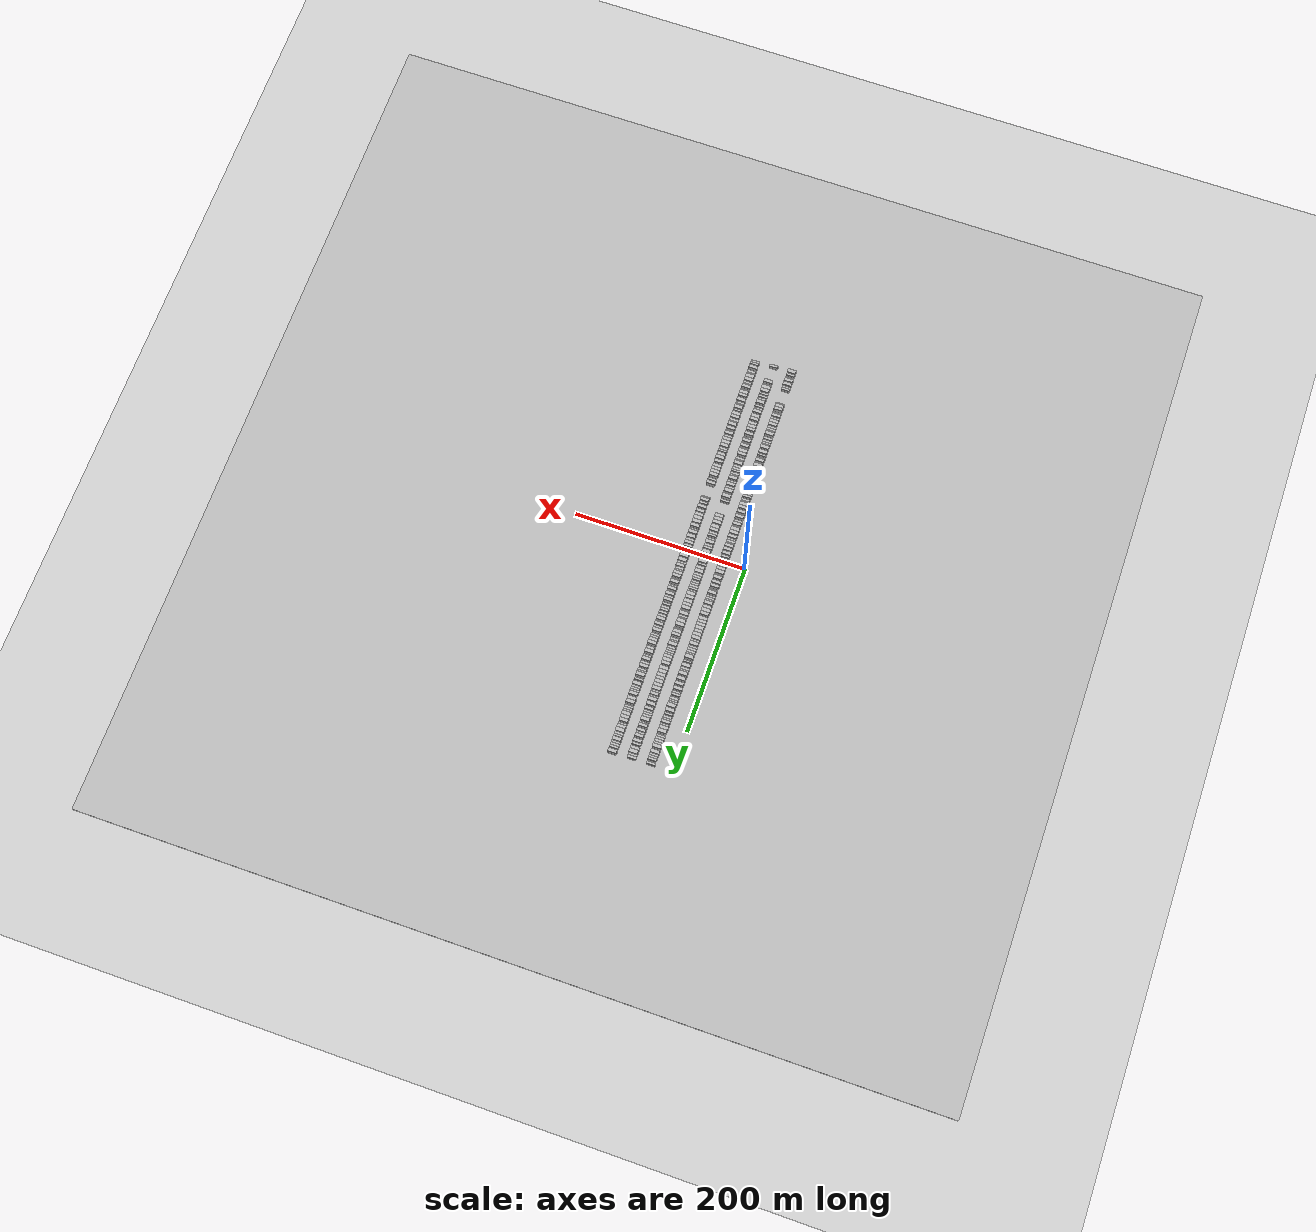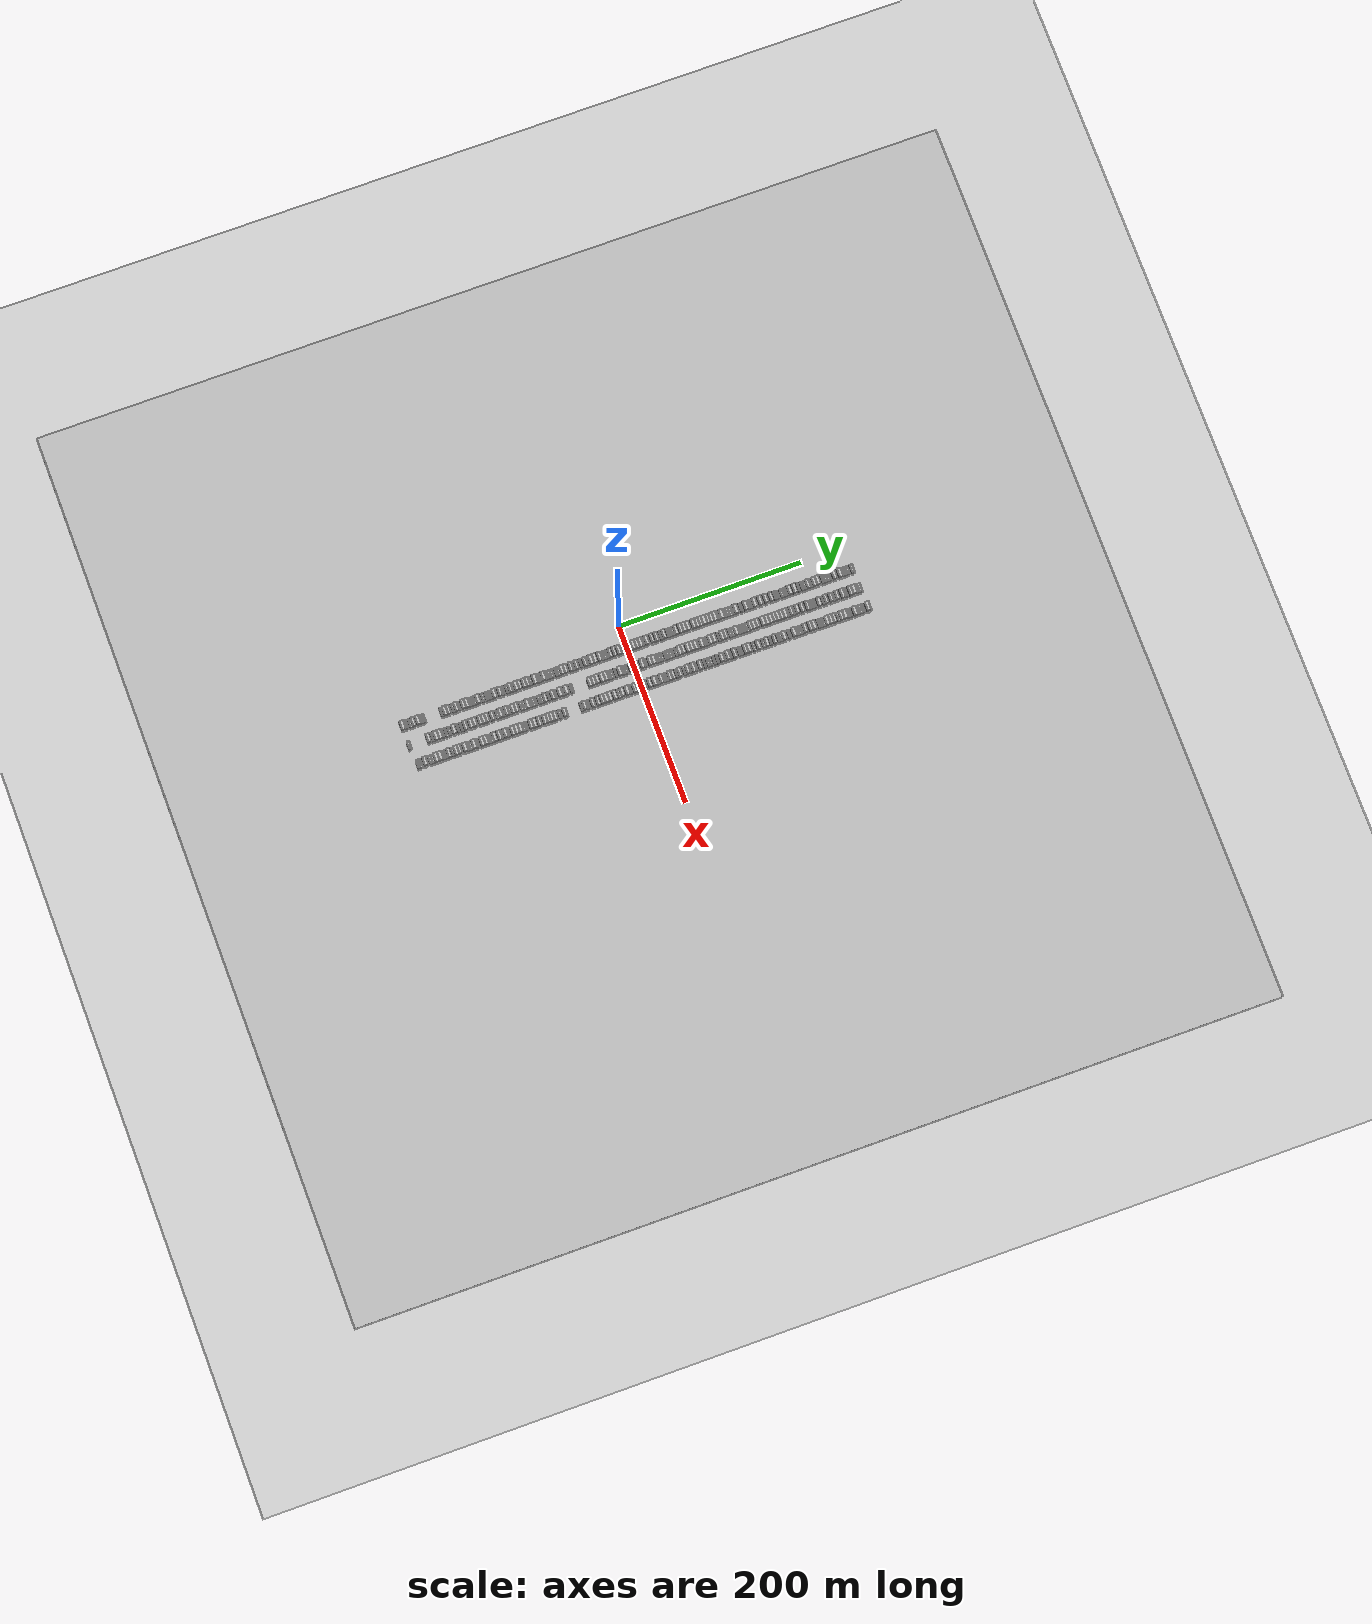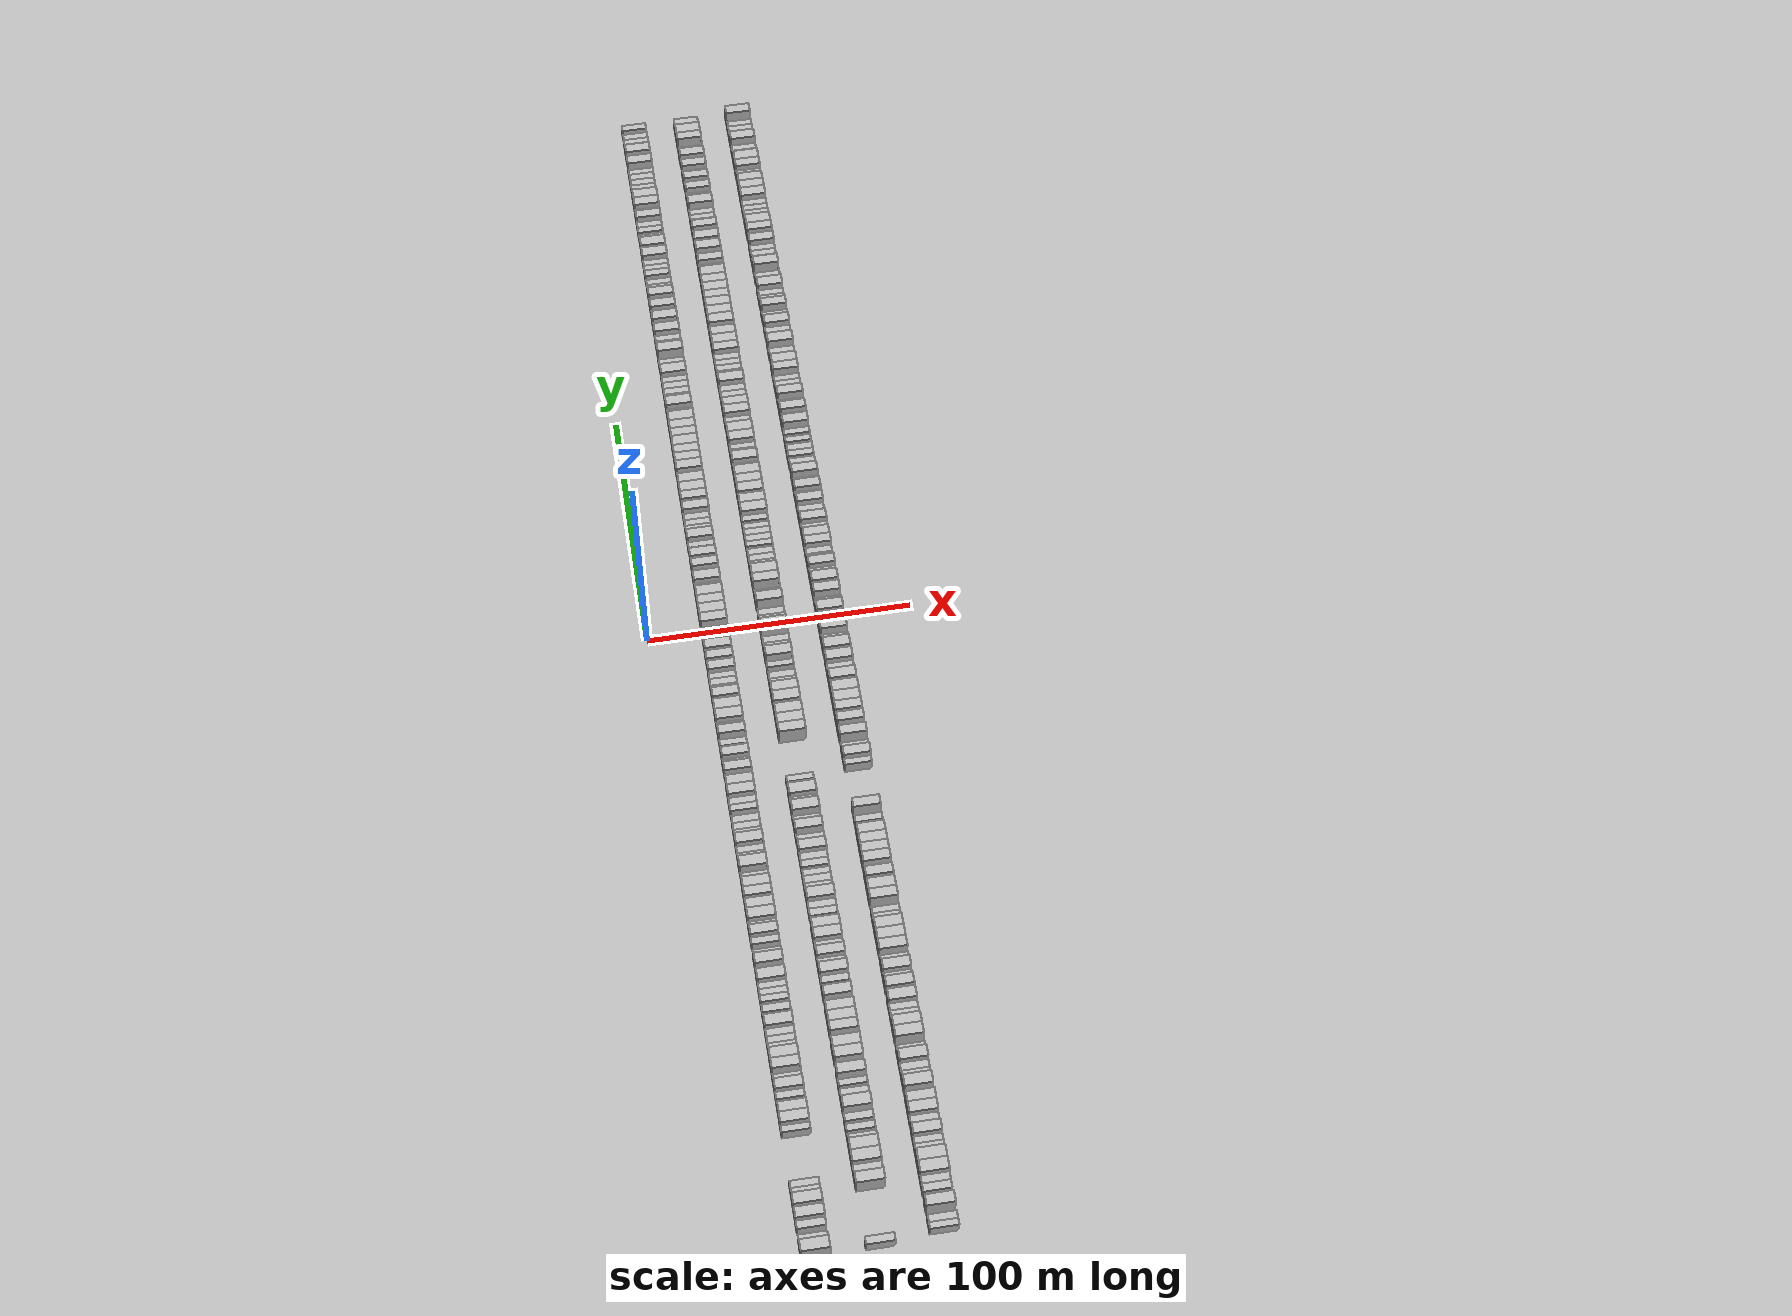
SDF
<?xml version="1.0" encoding="utf-8"?>

<sdf version="1.6">

   <world name="default">

      <gui fullscreen="0">

         <camera name="user_camera">

            <pose>-15 0 4.57585 0 0 0</pose>

            <view_controller>orbit</view_controller>

         </camera>

      </gui>

      <scene>

         <sky>

           <clouds>

             <speed>12</speed>

           </clouds>

         </sky>

         <ambient>0.4 0.4 0.4 1</ambient>

         <background>0.7 0.7 0.7 1</background>

         <shadows>1</shadows>

      </scene>

      <gravity>0 0 -9.8066</gravity>

      <magnetic_field>6e-06 2.3e-05 -4.2e-05</magnetic_field>

      <physics default="0" name="default_physics" type="ode">

         <ode>

            <solver>

               <type>quick</type>

               <iters>10</iters>

               <sor>1.0</sor>

               <use_dynamic_moi_rescaling>0</use_dynamic_moi_rescaling>

            </solver>

            <constraints>

               <cfm>0</cfm>

               <erp>0.2</erp>

               <contact_max_correcting_vel>100</contact_max_correcting_vel>

               <contact_surface_layer>0.001</contact_surface_layer>

            </constraints>

         </ode>

         <max_step_size>0.004</max_step_size>

         <real_time_factor>1</real_time_factor>

         <real_time_update_rate>250</real_time_update_rate>

      </physics>

      <light name="sun" type="directional">

         <cast_shadows>1</cast_shadows>

         <pose>0 0 10 0 0 0</pose>

         <diffuse>0.8 0.8 0.8 1</diffuse>

         <specular>0.2 0.2 0.2 1</specular>

         <attenuation>

            <range>1000</range>

            <constant>0.9</constant>

            <linear>0.01</linear>

            <quadratic>0.001</quadratic>

         </attenuation>

         <direction>-0.5 0.1 -0.9</direction>

      </light>

      <include>

         <name>ground_plane_1</name>

         <uri>model://HANNAS_ground_plane</uri>

         <pose>0 0 0  0 0 0</pose>

      </include>

      <include>

         <name>ground_plane_2</name>

         <uri>model://HANNAS_ground_plane</uri>

         <pose>100 0 0  0 0 0</pose>

      </include>

      <model name="building_1">

         <static>1</static>

         <pose frame="">25.0000 -245.8490 0 0.000000 0.000000 0.000000</pose>

         <link name="link">

            <pose frame="">0 0 4.50 0 0 0</pose>

            <collision name="collision">

               <geometry>

                  <box>

                     <size>10.0000 4.3020 9.0000</size>

                  </box>

               </geometry>

               <max_contacts>10</max_contacts>

               <surface>

                  <contact>

                     <ode/>

                  </contact>

                  <bounce/>

                  <friction>

                     <torsional>

                        <ode/>

                     </torsional>

                     <ode/>

                  </friction>

               </surface>

            </collision>

            <visual name="visual">

               <cast_shadows>0</cast_shadows>

               <geometry>

                  <box>

                     <size>10.0000 4.3020 9.0000</size>

                  </box>

               </geometry>

               <material>

                  <script>

                     <uri>model://HANNAS_wall/materials/scripts</uri>

                     <uri>model://HANNAS_wall/materials/textures</uri>

                     <name>vrc/HANNAS_wall</name>

                  </script>

               </material>

            </visual>

            <self_collide>0</self_collide>

            <enable_wind>0</enable_wind>

            <kinematic>0</kinematic>

         </link>

      </model>

      <model name="building_2">

         <static>1</static>

         <pose frame="">25.0000 -242.3765 0 0.000000 0.000000 0.000000</pose>

         <link name="link">

            <pose frame="">0 0 3.00 0 0 0</pose>

            <collision name="collision">

               <geometry>

                  <box>

                     <size>10.0000 2.6430 6.0000</size>

                  </box>

               </geometry>

               <max_contacts>10</max_contacts>

               <surface>

                  <contact>

                     <ode/>

                  </contact>

                  <bounce/>

                  <friction>

                     <torsional>

                        <ode/>

                     </torsional>

                     <ode/>

                  </friction>

               </surface>

            </collision>

            <visual name="visual">

               <cast_shadows>0</cast_shadows>

               <geometry>

                  <box>

                     <size>10.0000 2.6430 6.0000</size>

                  </box>

               </geometry>

               <material>

                  <script>

                     <uri>model://HANNAS_wall/materials/scripts</uri>

                     <uri>model://HANNAS_wall/materials/textures</uri>

                     <name>vrc/HANNAS_wall</name>

                  </script>

               </material>

            </visual>

            <self_collide>0</self_collide>

            <enable_wind>0</enable_wind>

            <kinematic>0</kinematic>

         </link>

      </model>

      <model name="building_3">

         <static>1</static>

         <pose frame="">25.0000 -237.5975 0 0.000000 0.000000 0.000000</pose>

         <link name="link">

            <pose frame="">0 0 3.00 0 0 0</pose>

            <collision name="collision">

               <geometry>

                  <box>

                     <size>10.0000 2.9150 6.0000</size>

                  </box>

               </geometry>

               <max_contacts>10</max_contacts>

               <surface>

                  <contact>

                     <ode/>

                  </contact>

                  <bounce/>

                  <friction>

                     <torsional>

                        <ode/>

                     </torsional>

                     <ode/>

                  </friction>

               </surface>

            </collision>

            <visual name="visual">

               <cast_shadows>0</cast_shadows>

               <geometry>

                  <box>

                     <size>10.0000 2.9150 6.0000</size>

                  </box>

               </geometry>

               <material>

                  <script>

                     <uri>model://HANNAS_wall/materials/scripts</uri>

                     <uri>model://HANNAS_wall/materials/textures</uri>

                     <name>vrc/HANNAS_wall</name>

                  </script>

               </material>

            </visual>

            <self_collide>0</self_collide>

            <enable_wind>0</enable_wind>

            <kinematic>0</kinematic>

         </link>

      </model>

      <model name="building_4">

         <static>1</static>

         <pose frame="">25.0000 -234.2111 0 0.000000 0.000000 0.000000</pose>

         <link name="link">

            <pose frame="">0 0 4.50 0 0 0</pose>

            <collision name="collision">

               <geometry>

                  <box>

                     <size>10.0000 3.8579 9.0000</size>

                  </box>

               </geometry>

               <max_contacts>10</max_contacts>

               <surface>

                  <contact>

                     <ode/>

                  </contact>

                  <bounce/>

                  <friction>

                     <torsional>

                        <ode/>

                     </torsional>

                     <ode/>

                  </friction>

               </surface>

            </collision>

            <visual name="visual">

               <cast_shadows>0</cast_shadows>

               <geometry>

                  <box>

                     <size>10.0000 3.8579 9.0000</size>

                  </box>

               </geometry>

               <material>

                  <script>

                     <uri>model://HANNAS_wall/materials/scripts</uri>

                     <uri>model://HANNAS_wall/materials/textures</uri>

                     <name>vrc/HANNAS_wall</name>

                  </script>

               </material>

            </visual>

            <self_collide>0</self_collide>

            <enable_wind>0</enable_wind>

            <kinematic>0</kinematic>

         </link>

      </model>

      <model name="building_5">

         <static>1</static>

         <pose frame="">25.0000 -229.2383 0 0.000000 0.000000 0.000000</pose>

         <link name="link">

            <pose frame="">0 0 4.50 0 0 0</pose>

            <collision name="collision">

               <geometry>

                  <box>

                     <size>10.0000 4.0878 9.0000</size>

                  </box>

               </geometry>

               <max_contacts>10</max_contacts>

               <surface>

                  <contact>

                     <ode/>

                  </contact>

                  <bounce/>

                  <friction>

                     <torsional>

                        <ode/>

                     </torsional>

                     <ode/>

                  </friction>

               </surface>

            </collision>

            <visual name="visual">

               <cast_shadows>0</cast_shadows>

               <geometry>

                  <box>

                     <size>10.0000 4.0878 9.0000</size>

                  </box>

               </geometry>

               <material>

                  <script>

                     <uri>model://HANNAS_wall/materials/scripts</uri>

                     <uri>model://HANNAS_wall/materials/textures</uri>

                     <name>vrc/HANNAS_wall</name>

                  </script>

               </material>

            </visual>

            <self_collide>0</self_collide>

            <enable_wind>0</enable_wind>

            <kinematic>0</kinematic>

         </link>

      </model>

      <model name="building_6">

         <static>1</static>

         <pose frame="">25.0000 -225.8606 0 0.000000 0.000000 0.000000</pose>

         <link name="link">

            <pose frame="">0 0 3.00 0 0 0</pose>

            <collision name="collision">

               <geometry>

                  <box>

                     <size>10.0000 2.6676 6.0000</size>

                  </box>

               </geometry>

               <max_contacts>10</max_contacts>

               <surface>

                  <contact>

                     <ode/>

                  </contact>

                  <bounce/>

                  <friction>

                     <torsional>

                        <ode/>

                     </torsional>

                     <ode/>

                  </friction>

               </surface>

            </collision>

            <visual name="visual">

               <cast_shadows>0</cast_shadows>

               <geometry>

                  <box>

                     <size>10.0000 2.6676 6.0000</size>

                  </box>

               </geometry>

               <material>

                  <script>

                     <uri>model://HANNAS_wall/materials/scripts</uri>

                     <uri>model://HANNAS_wall/materials/textures</uri>

                     <name>vrc/HANNAS_wall</name>

                  </script>

               </material>

            </visual>

            <self_collide>0</self_collide>

            <enable_wind>0</enable_wind>

            <kinematic>0</kinematic>

         </link>

      </model>

      <model name="building_7">

         <static>1</static>

         <pose frame="">25.0000 -223.2291 0 0.000000 0.000000 0.000000</pose>

         <link name="link">

            <pose frame="">0 0 3.00 0 0 0</pose>

            <collision name="collision">

               <geometry>

                  <box>

                     <size>10.0000 2.5953 6.0000</size>

                  </box>

               </geometry>

               <max_contacts>10</max_contacts>

               <surface>

                  <contact>

                     <ode/>

                  </contact>

                  <bounce/>

                  <friction>

                     <torsional>

                        <ode/>

                     </torsional>

                     <ode/>

                  </friction>

               </surface>

            </collision>

            <visual name="visual">

               <cast_shadows>0</cast_shadows>

               <geometry>

                  <box>

                     <size>10.0000 2.5953 6.0000</size>

                  </box>

               </geometry>

               <material>

                  <script>

                     <uri>model://HANNAS_wall/materials/scripts</uri>

                     <uri>model://HANNAS_wall/materials/textures</uri>

                     <name>vrc/HANNAS_wall</name>

                  </script>

               </material>

            </visual>

            <self_collide>0</self_collide>

            <enable_wind>0</enable_wind>

            <kinematic>0</kinematic>

         </link>

      </model>

      <model name="building_8">

         <static>1</static>

         <pose frame="">25.0000 -203.1853 0 0.000000 0.000000 0.000000</pose>

         <link name="link">

            <pose frame="">0 0 3.00 0 0 0</pose>

            <collision name="collision">

               <geometry>

                  <box>

                     <size>10.0000 2.4975 6.0000</size>

                  </box>

               </geometry>

               <max_contacts>10</max_contacts>

               <surface>

                  <contact>

                     <ode/>

                  </contact>

                  <bounce/>

                  <friction>

                     <torsional>

                        <ode/>

                     </torsional>

                     <ode/>

                  </friction>

               </surface>

            </collision>

            <visual name="visual">

               <cast_shadows>0</cast_shadows>

               <geometry>

                  <box>

                     <size>10.0000 2.4975 6.0000</size>

                  </box>

               </geometry>

               <material>

                  <script>

                     <uri>model://HANNAS_wall/materials/scripts</uri>

                     <uri>model://HANNAS_wall/materials/textures</uri>

                     <name>vrc/HANNAS_wall</name>

                  </script>

               </material>

            </visual>

            <self_collide>0</self_collide>

            <enable_wind>0</enable_wind>

            <kinematic>0</kinematic>

         </link>

      </model>

      <model name="building_9">

         <static>1</static>

         <pose frame="">25.0000 -199.9623 0 0.000000 0.000000 0.000000</pose>

         <link name="link">

            <pose frame="">0 0 4.50 0 0 0</pose>

            <collision name="collision">

               <geometry>

                  <box>

                     <size>10.0000 3.9486 9.0000</size>

                  </box>

               </geometry>

               <max_contacts>10</max_contacts>

               <surface>

                  <contact>

                     <ode/>

                  </contact>

                  <bounce/>

                  <friction>

                     <torsional>

                        <ode/>

                     </torsional>

                     <ode/>

                  </friction>

               </surface>

            </collision>

            <visual name="visual">

               <cast_shadows>0</cast_shadows>

               <geometry>

                  <box>

                     <size>10.0000 3.9486 9.0000</size>

                  </box>

               </geometry>

               <material>

                  <script>

                     <uri>model://HANNAS_wall/materials/scripts</uri>

                     <uri>model://HANNAS_wall/materials/textures</uri>

                     <name>vrc/HANNAS_wall</name>

                  </script>

               </material>

            </visual>

            <self_collide>0</self_collide>

            <enable_wind>0</enable_wind>

            <kinematic>0</kinematic>

         </link>

      </model>

      <model name="building_10">

         <static>1</static>

         <pose frame="">25.0000 -196.1469 0 0.000000 0.000000 0.000000</pose>

         <link name="link">

            <pose frame="">0 0 4.50 0 0 0</pose>

            <collision name="collision">

               <geometry>

                  <box>

                     <size>10.0000 3.6823 9.0000</size>

                  </box>

               </geometry>

               <max_contacts>10</max_contacts>

               <surface>

                  <contact>

                     <ode/>

                  </contact>

                  <bounce/>

                  <friction>

                     <torsional>

                        <ode/>

                     </torsional>

                     <ode/>

                  </friction>

               </surface>

            </collision>

            <visual name="visual">

               <cast_shadows>0</cast_shadows>

               <geometry>

                  <box>

                     <size>10.0000 3.6823 9.0000</size>

                  </box>

               </geometry>

               <material>

                  <script>

                     <uri>model://HANNAS_wall/materials/scripts</uri>

                     <uri>model://HANNAS_wall/materials/textures</uri>

                     <name>vrc/HANNAS_wall</name>

                  </script>

               </material>

            </visual>

            <self_collide>0</self_collide>

            <enable_wind>0</enable_wind>

            <kinematic>0</kinematic>

         </link>

      </model>

      <model name="building_11">

         <static>1</static>

         <pose frame="">25.0000 -190.9192 0 0.000000 0.000000 0.000000</pose>

         <link name="link">

            <pose frame="">0 0 3.00 0 0 0</pose>

            <collision name="collision">

               <geometry>

                  <box>

                     <size>10.0000 2.7731 6.0000</size>

                  </box>

               </geometry>

               <max_contacts>10</max_contacts>

               <surface>

                  <contact>

                     <ode/>

                  </contact>

                  <bounce/>

                  <friction>

                     <torsional>

                        <ode/>

                     </torsional>

                     <ode/>

                  </friction>

               </surface>

            </collision>

            <visual name="visual">

               <cast_shadows>0</cast_shadows>

               <geometry>

                  <box>

                     <size>10.0000 2.7731 6.0000</size>

                  </box>

               </geometry>

               <material>

                  <script>

                     <uri>model://HANNAS_wall/materials/scripts</uri>

                     <uri>model://HANNAS_wall/materials/textures</uri>

                     <name>vrc/HANNAS_wall</name>

                  </script>

               </material>

            </visual>

            <self_collide>0</self_collide>

            <enable_wind>0</enable_wind>

            <kinematic>0</kinematic>

         </link>

      </model>

      <model name="building_12">

         <static>1</static>

         <pose frame="">25.0000 -187.5897 0 0.000000 0.000000 0.000000</pose>

         <link name="link">

            <pose frame="">0 0 4.50 0 0 0</pose>

            <collision name="collision">

               <geometry>

                  <box>

                     <size>10.0000 3.8859 9.0000</size>

                  </box>

               </geometry>

               <max_contacts>10</max_contacts>

               <surface>

                  <contact>

                     <ode/>

                  </contact>

                  <bounce/>

                  <friction>

                     <torsional>

                        <ode/>

                     </torsional>

                     <ode/>

                  </friction>

               </surface>

            </collision>

            <visual name="visual">

               <cast_shadows>0</cast_shadows>

               <geometry>

                  <box>

                     <size>10.0000 3.8859 9.0000</size>

                  </box>

               </geometry>

               <material>

                  <script>

                     <uri>model://HANNAS_wall/materials/scripts</uri>

                     <uri>model://HANNAS_wall/materials/textures</uri>

                     <name>vrc/HANNAS_wall</name>

                  </script>

               </material>

            </visual>

            <self_collide>0</self_collide>

            <enable_wind>0</enable_wind>

            <kinematic>0</kinematic>

         </link>

      </model>

      <model name="building_13">

         <static>1</static>

         <pose frame="">25.0000 -184.2983 0 0.000000 0.000000 0.000000</pose>

         <link name="link">

            <pose frame="">0 0 3.00 0 0 0</pose>

            <collision name="collision">

               <geometry>

                  <box>

                     <size>10.0000 2.6970 6.0000</size>

                  </box>

               </geometry>

               <max_contacts>10</max_contacts>

               <surface>

                  <contact>

                     <ode/>

                  </contact>

                  <bounce/>

                  <friction>

                     <torsional>

                        <ode/>

                     </torsional>

                     <ode/>

                  </friction>

               </surface>

            </collision>

            <visual name="visual">

               <cast_shadows>0</cast_shadows>

               <geometry>

                  <box>

                     <size>10.0000 2.6970 6.0000</size>

                  </box>

               </geometry>

               <material>

                  <script>

                     <uri>model://HANNAS_wall/materials/scripts</uri>

                     <uri>model://HANNAS_wall/materials/textures</uri>

                     <name>vrc/HANNAS_wall</name>

                  </script>

               </material>

            </visual>

            <self_collide>0</self_collide>

            <enable_wind>0</enable_wind>

            <kinematic>0</kinematic>

         </link>

      </model>

      <model name="building_14">

         <static>1</static>

         <pose frame="">25.0000 -180.0099 0 0.000000 0.000000 0.000000</pose>

         <link name="link">

            <pose frame="">0 0 4.50 0 0 0</pose>

            <collision name="collision">

               <geometry>

                  <box>

                     <size>10.0000 3.8799 9.0000</size>

                  </box>

               </geometry>

               <max_contacts>10</max_contacts>

               <surface>

                  <contact>

                     <ode/>

                  </contact>

                  <bounce/>

                  <friction>

                     <torsional>

                        <ode/>

                     </torsional>

                     <ode/>

                  </friction>

               </surface>

            </collision>

            <visual name="visual">

               <cast_shadows>0</cast_shadows>

               <geometry>

                  <box>

                     <size>10.0000 3.8799 9.0000</size>

                  </box>

               </geometry>

               <material>

                  <script>

                     <uri>model://HANNAS_wall/materials/scripts</uri>

                     <uri>model://HANNAS_wall/materials/textures</uri>

                     <name>vrc/HANNAS_wall</name>

                  </script>

               </material>

            </visual>

            <self_collide>0</self_collide>

            <enable_wind>0</enable_wind>

            <kinematic>0</kinematic>

         </link>

      </model>

      <model name="building_15">

         <static>1</static>

         <pose frame="">25.0000 -176.0379 0 0.000000 0.000000 0.000000</pose>

         <link name="link">

            <pose frame="">0 0 4.50 0 0 0</pose>

            <collision name="collision">

               <geometry>

                  <box>

                     <size>10.0000 4.0640 9.0000</size>

                  </box>

               </geometry>

               <max_contacts>10</max_contacts>

               <surface>

                  <contact>

                     <ode/>

                  </contact>

                  <bounce/>

                  <friction>

                     <torsional>

                        <ode/>

                     </torsional>

                     <ode/>

                  </friction>

               </surface>

            </collision>

            <visual name="visual">

               <cast_shadows>0</cast_shadows>

               <geometry>

                  <box>

                     <size>10.0000 4.0640 9.0000</size>

                  </box>

               </geometry>

               <material>

                  <script>

                     <uri>model://HANNAS_wall/materials/scripts</uri>

                     <uri>model://HANNAS_wall/materials/textures</uri>

                     <name>vrc/HANNAS_wall</name>

                  </script>

               </material>

            </visual>

            <self_collide>0</self_collide>

            <enable_wind>0</enable_wind>

            <kinematic>0</kinematic>

         </link>

      </model>

      <model name="building_16">

         <static>1</static>

         <pose frame="">25.0000 -172.6615 0 0.000000 0.000000 0.000000</pose>

         <link name="link">

            <pose frame="">0 0 3.00 0 0 0</pose>

            <collision name="collision">

               <geometry>

                  <box>

                     <size>10.0000 2.6888 6.0000</size>

                  </box>

               </geometry>

               <max_contacts>10</max_contacts>

               <surface>

                  <contact>

                     <ode/>

                  </contact>

                  <bounce/>

                  <friction>

                     <torsional>

                        <ode/>

                     </torsional>

                     <ode/>

                  </friction>

               </surface>

            </collision>

            <visual name="visual">

               <cast_shadows>0</cast_shadows>

               <geometry>

                  <box>

                     <size>10.0000 2.6888 6.0000</size>

                  </box>

               </geometry>

               <material>

                  <script>

                     <uri>model://HANNAS_wall/materials/scripts</uri>

                     <uri>model://HANNAS_wall/materials/textures</uri>

                     <name>vrc/HANNAS_wall</name>

                  </script>

               </material>

            </visual>

            <self_collide>0</self_collide>

            <enable_wind>0</enable_wind>

            <kinematic>0</kinematic>

         </link>

      </model>

      <model name="building_17">

         <static>1</static>

         <pose frame="">25.0000 -170.0229 0 0.000000 0.000000 0.000000</pose>

         <link name="link">

            <pose frame="">0 0 3.00 0 0 0</pose>

            <collision name="collision">

               <geometry>

                  <box>

                     <size>10.0000 2.5885 6.0000</size>

                  </box>

               </geometry>

               <max_contacts>10</max_contacts>

               <surface>

                  <contact>

                     <ode/>

                  </contact>

                  <bounce/>

                  <friction>

                     <torsional>

                        <ode/>

                     </torsional>

                     <ode/>

                  </friction>

               </surface>

            </collision>

            <visual name="visual">

               <cast_shadows>0</cast_shadows>

               <geometry>

                  <box>

                     <size>10.0000 2.5885 6.0000</size>

                  </box>

               </geometry>

               <material>

                  <script>

                     <uri>model://HANNAS_wall/materials/scripts</uri>

                     <uri>model://HANNAS_wall/materials/textures</uri>

                     <name>vrc/HANNAS_wall</name>

                  </script>

               </material>

            </visual>

            <self_collide>0</self_collide>

            <enable_wind>0</enable_wind>

            <kinematic>0</kinematic>

         </link>

      </model>

      <model name="building_18">

         <static>1</static>

         <pose frame="">25.0000 -167.3150 0 0.000000 0.000000 0.000000</pose>

         <link name="link">

            <pose frame="">0 0 3.00 0 0 0</pose>

            <collision name="collision">

               <geometry>

                  <box>

                     <size>10.0000 2.8273 6.0000</size>

                  </box>

               </geometry>

               <max_contacts>10</max_contacts>

               <surface>

                  <contact>

                     <ode/>

                  </contact>

                  <bounce/>

                  <friction>

                     <torsional>

                        <ode/>

                     </torsional>

                     <ode/>

                  </friction>

               </surface>

            </collision>

            <visual name="visual">

               <cast_shadows>0</cast_shadows>

               <geometry>

                  <box>

                     <size>10.0000 2.8273 6.0000</size>

                  </box>

               </geometry>

               <material>

                  <script>

                     <uri>model://HANNAS_wall/materials/scripts</uri>

                     <uri>model://HANNAS_wall/materials/textures</uri>

                     <name>vrc/HANNAS_wall</name>

                  </script>

               </material>

            </visual>

            <self_collide>0</self_collide>

            <enable_wind>0</enable_wind>

            <kinematic>0</kinematic>

         </link>

      </model>

      <model name="building_19">

         <static>1</static>

         <pose frame="">25.0000 -163.7482 0 0.000000 0.000000 0.000000</pose>

         <link name="link">

            <pose frame="">0 0 4.50 0 0 0</pose>

            <collision name="collision">

               <geometry>

                  <box>

                     <size>10.0000 4.3062 9.0000</size>

                  </box>

               </geometry>

               <max_contacts>10</max_contacts>

               <surface>

                  <contact>

                     <ode/>

                  </contact>

                  <bounce/>

                  <friction>

                     <torsional>

                        <ode/>

                     </torsional>

                     <ode/>

                  </friction>

               </surface>

            </collision>

            <visual name="visual">

               <cast_shadows>0</cast_shadows>

               <geometry>

                  <box>

                     <size>10.0000 4.3062 9.0000</size>

                  </box>

               </geometry>

               <material>

                  <script>

                     <uri>model://HANNAS_wall/materials/scripts</uri>

                     <uri>model://HANNAS_wall/materials/textures</uri>

                     <name>vrc/HANNAS_wall</name>

                  </script>

               </material>

            </visual>

            <self_collide>0</self_collide>

            <enable_wind>0</enable_wind>

            <kinematic>0</kinematic>

         </link>

      </model>

      <model name="building_20">

         <static>1</static>

         <pose frame="">25.0000 -158.1103 0 0.000000 0.000000 0.000000</pose>

         <link name="link">

            <pose frame="">0 0 3.00 0 0 0</pose>

            <collision name="collision">

               <geometry>

                  <box>

                     <size>10.0000 2.9697 6.0000</size>

                  </box>

               </geometry>

               <max_contacts>10</max_contacts>

               <surface>

                  <contact>

                     <ode/>

                  </contact>

                  <bounce/>

                  <friction>

                     <torsional>

                        <ode/>

                     </torsional>

                     <ode/>

                  </friction>

               </surface>

            </collision>

            <visual name="visual">

               <cast_shadows>0</cast_shadows>

               <geometry>

                  <box>

                     <size>10.0000 2.9697 6.0000</size>

                  </box>

               </geometry>

               <material>

                  <script>

                     <uri>model://HANNAS_wall/materials/scripts</uri>

                     <uri>model://HANNAS_wall/materials/textures</uri>

                     <name>vrc/HANNAS_wall</name>

                  </script>

               </material>

            </visual>

            <self_collide>0</self_collide>

            <enable_wind>0</enable_wind>

            <kinematic>0</kinematic>

         </link>

      </model>

      <model name="building_21">

         <static>1</static>

         <pose frame="">25.0000 -154.3483 0 0.000000 0.000000 0.000000</pose>

         <link name="link">

            <pose frame="">0 0 3.00 0 0 0</pose>

            <collision name="collision">

               <geometry>

                  <box>

                     <size>10.0000 2.5543 6.0000</size>

                  </box>

               </geometry>

               <max_contacts>10</max_contacts>

               <surface>

                  <contact>

                     <ode/>

                  </contact>

                  <bounce/>

                  <friction>

                     <torsional>

                        <ode/>

                     </torsional>

                     <ode/>

                  </friction>

               </surface>

            </collision>

            <visual name="visual">

               <cast_shadows>0</cast_shadows>

               <geometry>

                  <box>

                     <size>10.0000 2.5543 6.0000</size>

                  </box>

               </geometry>

               <material>

                  <script>

                     <uri>model://HANNAS_wall/materials/scripts</uri>

                     <uri>model://HANNAS_wall/materials/textures</uri>

                     <name>vrc/HANNAS_wall</name>

                  </script>

               </material>

            </visual>

            <self_collide>0</self_collide>

            <enable_wind>0</enable_wind>

            <kinematic>0</kinematic>

         </link>

      </model>

      <model name="building_22">

         <static>1</static>

         <pose frame="">25.0000 -151.8470 0 0.000000 0.000000 0.000000</pose>

         <link name="link">

            <pose frame="">0 0 3.00 0 0 0</pose>

            <collision name="collision">

               <geometry>

                  <box>

                     <size>10.0000 2.4483 6.0000</size>

                  </box>

               </geometry>

               <max_contacts>10</max_contacts>

               <surface>

                  <contact>

                     <ode/>

                  </contact>

                  <bounce/>

                  <friction>

                     <torsional>

                        <ode/>

                     </torsional>

                     <ode/>

                  </friction>

               </surface>

            </collision>

            <visual name="visual">

               <cast_shadows>0</cast_shadows>

               <geometry>

                  <box>

                     <size>10.0000 2.4483 6.0000</size>

                  </box>

               </geometry>

               <material>

                  <script>

                     <uri>model://HANNAS_wall/materials/scripts</uri>

                     <uri>model://HANNAS_wall/materials/textures</uri>

                     <name>vrc/HANNAS_wall</name>

                  </script>

               </material>

            </visual>

            <self_collide>0</self_collide>

            <enable_wind>0</enable_wind>

            <kinematic>0</kinematic>

         </link>

      </model>

      <model name="building_23">

         <static>1</static>

         <pose frame="">25.0000 -149.4169 0 0.000000 0.000000 0.000000</pose>

         <link name="link">

            <pose frame="">0 0 3.00 0 0 0</pose>

            <collision name="collision">

               <geometry>

                  <box>

                     <size>10.0000 2.4118 6.0000</size>

                  </box>

               </geometry>

               <max_contacts>10</max_contacts>

               <surface>

                  <contact>

                     <ode/>

                  </contact>

                  <bounce/>

                  <friction>

                     <torsional>

                        <ode/>

                     </torsional>

                     <ode/>

                  </friction>

               </surface>

            </collision>

            <visual name="visual">

               <cast_shadows>0</cast_shadows>

               <geometry>

                  <box>

                     <size>10.0000 2.4118 6.0000</size>

                  </box>

               </geometry>

               <material>

                  <script>

                     <uri>model://HANNAS_wall/materials/scripts</uri>

                     <uri>model://HANNAS_wall/materials/textures</uri>

                     <name>vrc/HANNAS_wall</name>

                  </script>

               </material>

            </visual>

            <self_collide>0</self_collide>

            <enable_wind>0</enable_wind>

            <kinematic>0</kinematic>

         </link>

      </model>

      <model name="building_24">

         <static>1</static>

         <pose frame="">25.0000 -146.0749 0 0.000000 0.000000 0.000000</pose>

         <link name="link">

            <pose frame="">0 0 4.50 0 0 0</pose>

            <collision name="collision">

               <geometry>

                  <box>

                     <size>10.0000 4.2722 9.0000</size>

                  </box>

               </geometry>

               <max_contacts>10</max_contacts>

               <surface>

                  <contact>

                     <ode/>

                  </contact>

                  <bounce/>

                  <friction>

                     <torsional>

                        <ode/>

                     </torsional>

                     <ode/>

                  </friction>

               </surface>

            </collision>

            <visual name="visual">

               <cast_shadows>0</cast_shadows>

               <geometry>

                  <box>

                     <size>10.0000 4.2722 9.0000</size>

                  </box>

               </geometry>

               <material>

                  <script>

                     <uri>model://HANNAS_wall/materials/scripts</uri>

                     <uri>model://HANNAS_wall/materials/textures</uri>

                     <name>vrc/HANNAS_wall</name>

                  </script>

               </material>

            </visual>

            <self_collide>0</self_collide>

            <enable_wind>0</enable_wind>

            <kinematic>0</kinematic>

         </link>

      </model>

      <model name="building_25">

         <static>1</static>

         <pose frame="">25.0000 -139.9030 0 0.000000 0.000000 0.000000</pose>

         <link name="link">

            <pose frame="">0 0 4.50 0 0 0</pose>

            <collision name="collision">

               <geometry>

                  <box>

                     <size>10.0000 4.0716 9.0000</size>

                  </box>

               </geometry>

               <max_contacts>10</max_contacts>

               <surface>

                  <contact>

                     <ode/>

                  </contact>

                  <bounce/>

                  <friction>

                     <torsional>

                        <ode/>

                     </torsional>

                     <ode/>

                  </friction>

               </surface>

            </collision>

            <visual name="visual">

               <cast_shadows>0</cast_shadows>

               <geometry>

                  <box>

                     <size>10.0000 4.0716 9.0000</size>

                  </box>

               </geometry>

               <material>

                  <script>

                     <uri>model://HANNAS_wall/materials/scripts</uri>

                     <uri>model://HANNAS_wall/materials/textures</uri>

                     <name>vrc/HANNAS_wall</name>

                  </script>

               </material>

            </visual>

            <self_collide>0</self_collide>

            <enable_wind>0</enable_wind>

            <kinematic>0</kinematic>

         </link>

      </model>

      <model name="building_26">

         <static>1</static>

         <pose frame="">25.0000 -136.5946 0 0.000000 0.000000 0.000000</pose>

         <link name="link">

            <pose frame="">0 0 3.00 0 0 0</pose>

            <collision name="collision">

               <geometry>

                  <box>

                     <size>10.0000 2.5452 6.0000</size>

                  </box>

               </geometry>

               <max_contacts>10</max_contacts>

               <surface>

                  <contact>

                     <ode/>

                  </contact>

                  <bounce/>

                  <friction>

                     <torsional>

                        <ode/>

                     </torsional>

                     <ode/>

                  </friction>

               </surface>

            </collision>

            <visual name="visual">

               <cast_shadows>0</cast_shadows>

               <geometry>

                  <box>

                     <size>10.0000 2.5452 6.0000</size>

                  </box>

               </geometry>

               <material>

                  <script>

                     <uri>model://HANNAS_wall/materials/scripts</uri>

                     <uri>model://HANNAS_wall/materials/textures</uri>

                     <name>vrc/HANNAS_wall</name>

                  </script>

               </material>

            </visual>

            <self_collide>0</self_collide>

            <enable_wind>0</enable_wind>

            <kinematic>0</kinematic>

         </link>

      </model>

      <model name="building_27">

         <static>1</static>

         <pose frame="">25.0000 -131.9562 0 0.000000 0.000000 0.000000</pose>

         <link name="link">

            <pose frame="">0 0 3.00 0 0 0</pose>

            <collision name="collision">

               <geometry>

                  <box>

                     <size>10.0000 2.7318 6.0000</size>

                  </box>

               </geometry>

               <max_contacts>10</max_contacts>

               <surface>

                  <contact>

                     <ode/>

                  </contact>

                  <bounce/>

                  <friction>

                     <torsional>

                        <ode/>

                     </torsional>

                     <ode/>

                  </friction>

               </surface>

            </collision>

            <visual name="visual">

               <cast_shadows>0</cast_shadows>

               <geometry>

                  <box>

                     <size>10.0000 2.7318 6.0000</size>

                  </box>

               </geometry>

               <material>

                  <script>

                     <uri>model://HANNAS_wall/materials/scripts</uri>

                     <uri>model://HANNAS_wall/materials/textures</uri>

                     <name>vrc/HANNAS_wall</name>

                  </script>

               </material>

            </visual>

            <self_collide>0</self_collide>

            <enable_wind>0</enable_wind>

            <kinematic>0</kinematic>

         </link>

      </model>

      <model name="building_28">

         <static>1</static>

         <pose frame="">25.0000 -128.7188 0 0.000000 0.000000 0.000000</pose>

         <link name="link">

            <pose frame="">0 0 4.50 0 0 0</pose>

            <collision name="collision">

               <geometry>

                  <box>

                     <size>10.0000 3.7429 9.0000</size>

                  </box>

               </geometry>

               <max_contacts>10</max_contacts>

               <surface>

                  <contact>

                     <ode/>

                  </contact>

                  <bounce/>

                  <friction>

                     <torsional>

                        <ode/>

                     </torsional>

                     <ode/>

                  </friction>

               </surface>

            </collision>

            <visual name="visual">

               <cast_shadows>0</cast_shadows>

               <geometry>

                  <box>

                     <size>10.0000 3.7429 9.0000</size>

                  </box>

               </geometry>

               <material>

                  <script>

                     <uri>model://HANNAS_wall/materials/scripts</uri>

                     <uri>model://HANNAS_wall/materials/textures</uri>

                     <name>vrc/HANNAS_wall</name>

                  </script>

               </material>

            </visual>

            <self_collide>0</self_collide>

            <enable_wind>0</enable_wind>

            <kinematic>0</kinematic>

         </link>

      </model>

      <model name="building_29">

         <static>1</static>

         <pose frame="">25.0000 -125.6237 0 0.000000 0.000000 0.000000</pose>

         <link name="link">

            <pose frame="">0 0 3.00 0 0 0</pose>

            <collision name="collision">

               <geometry>

                  <box>

                     <size>10.0000 2.4472 6.0000</size>

                  </box>

               </geometry>

               <max_contacts>10</max_contacts>

               <surface>

                  <contact>

                     <ode/>

                  </contact>

                  <bounce/>

                  <friction>

                     <torsional>

                        <ode/>

                     </torsional>

                     <ode/>

                  </friction>

               </surface>

            </collision>

            <visual name="visual">

               <cast_shadows>0</cast_shadows>

               <geometry>

                  <box>

                     <size>10.0000 2.4472 6.0000</size>

                  </box>

               </geometry>

               <material>

                  <script>

                     <uri>model://HANNAS_wall/materials/scripts</uri>

                     <uri>model://HANNAS_wall/materials/textures</uri>

                     <name>vrc/HANNAS_wall</name>

                  </script>

               </material>

            </visual>

            <self_collide>0</self_collide>

            <enable_wind>0</enable_wind>

            <kinematic>0</kinematic>

         </link>

      </model>

      <model name="building_30">

         <static>1</static>

         <pose frame="">25.0000 -122.2991 0 0.000000 0.000000 0.000000</pose>

         <link name="link">

            <pose frame="">0 0 4.50 0 0 0</pose>

            <collision name="collision">

               <geometry>

                  <box>

                     <size>10.0000 4.2020 9.0000</size>

                  </box>

               </geometry>

               <max_contacts>10</max_contacts>

               <surface>

                  <contact>

                     <ode/>

                  </contact>

                  <bounce/>

                  <friction>

                     <torsional>

                        <ode/>

                     </torsional>

                     <ode/>

                  </friction>

               </surface>

            </collision>

            <visual name="visual">

               <cast_shadows>0</cast_shadows>

               <geometry>

                  <box>

                     <size>10.0000 4.2020 9.0000</size>

                  </box>

               </geometry>

               <material>

                  <script>

                     <uri>model://HANNAS_wall/materials/scripts</uri>

                     <uri>model://HANNAS_wall/materials/textures</uri>

                     <name>vrc/HANNAS_wall</name>

                  </script>

               </material>

            </visual>

            <self_collide>0</self_collide>

            <enable_wind>0</enable_wind>

            <kinematic>0</kinematic>

         </link>

      </model>

      <model name="building_31">

         <static>1</static>

         <pose frame="">25.0000 -118.3108 0 0.000000 0.000000 0.000000</pose>

         <link name="link">

            <pose frame="">0 0 4.50 0 0 0</pose>

            <collision name="collision">

               <geometry>

                  <box>

                     <size>10.0000 3.7748 9.0000</size>

                  </box>

               </geometry>

               <max_contacts>10</max_contacts>

               <surface>

                  <contact>

                     <ode/>

                  </contact>

                  <bounce/>

                  <friction>

                     <torsional>

                        <ode/>

                     </torsional>

                     <ode/>

                  </friction>

               </surface>

            </collision>

            <visual name="visual">

               <cast_shadows>0</cast_shadows>

               <geometry>

                  <box>

                     <size>10.0000 3.7748 9.0000</size>

                  </box>

               </geometry>

               <material>

                  <script>

                     <uri>model://HANNAS_wall/materials/scripts</uri>

                     <uri>model://HANNAS_wall/materials/textures</uri>

                     <name>vrc/HANNAS_wall</name>

                  </script>

               </material>

            </visual>

            <self_collide>0</self_collide>

            <enable_wind>0</enable_wind>

            <kinematic>0</kinematic>

         </link>

      </model>

      <model name="building_32">

         <static>1</static>

         <pose frame="">25.0000 -113.5876 0 0.000000 0.000000 0.000000</pose>

         <link name="link">

            <pose frame="">0 0 4.50 0 0 0</pose>

            <collision name="collision">

               <geometry>

                  <box>

                     <size>10.0000 3.6714 9.0000</size>

                  </box>

               </geometry>

               <max_contacts>10</max_contacts>

               <surface>

                  <contact>

                     <ode/>

                  </contact>

                  <bounce/>

                  <friction>

                     <torsional>

                        <ode/>

                     </torsional>

                     <ode/>

                  </friction>

               </surface>

            </collision>

            <visual name="visual">

               <cast_shadows>0</cast_shadows>

               <geometry>

                  <box>

                     <size>10.0000 3.6714 9.0000</size>

                  </box>

               </geometry>

               <material>

                  <script>

                     <uri>model://HANNAS_wall/materials/scripts</uri>

                     <uri>model://HANNAS_wall/materials/textures</uri>

                     <name>vrc/HANNAS_wall</name>

                  </script>

               </material>

            </visual>

            <self_collide>0</self_collide>

            <enable_wind>0</enable_wind>

            <kinematic>0</kinematic>

         </link>

      </model>

      <model name="building_33">

         <static>1</static>

         <pose frame="">25.0000 -109.7929 0 0.000000 0.000000 0.000000</pose>

         <link name="link">

            <pose frame="">0 0 4.50 0 0 0</pose>

            <collision name="collision">

               <geometry>

                  <box>

                     <size>10.0000 3.9181 9.0000</size>

                  </box>

               </geometry>

               <max_contacts>10</max_contacts>

               <surface>

                  <contact>

                     <ode/>

                  </contact>

                  <bounce/>

                  <friction>

                     <torsional>

                        <ode/>

                     </torsional>

                     <ode/>

                  </friction>

               </surface>

            </collision>

            <visual name="visual">

               <cast_shadows>0</cast_shadows>

               <geometry>

                  <box>

                     <size>10.0000 3.9181 9.0000</size>

                  </box>

               </geometry>

               <material>

                  <script>

                     <uri>model://HANNAS_wall/materials/scripts</uri>

                     <uri>model://HANNAS_wall/materials/textures</uri>

                     <name>vrc/HANNAS_wall</name>

                  </script>

               </material>

            </visual>

            <self_collide>0</self_collide>

            <enable_wind>0</enable_wind>

            <kinematic>0</kinematic>

         </link>

      </model>

      <model name="building_34">

         <static>1</static>

         <pose frame="">25.0000 -106.3459 0 0.000000 0.000000 0.000000</pose>

         <link name="link">

            <pose frame="">0 0 3.00 0 0 0</pose>

            <collision name="collision">

               <geometry>

                  <box>

                     <size>10.0000 2.9760 6.0000</size>

                  </box>

               </geometry>

               <max_contacts>10</max_contacts>

               <surface>

                  <contact>

                     <ode/>

                  </contact>

                  <bounce/>

                  <friction>

                     <torsional>

                        <ode/>

                     </torsional>

                     <ode/>

                  </friction>

               </surface>

            </collision>

            <visual name="visual">

               <cast_shadows>0</cast_shadows>

               <geometry>

                  <box>

                     <size>10.0000 2.9760 6.0000</size>

                  </box>

               </geometry>

               <material>

                  <script>

                     <uri>model://HANNAS_wall/materials/scripts</uri>

                     <uri>model://HANNAS_wall/materials/textures</uri>

                     <name>vrc/HANNAS_wall</name>

                  </script>

               </material>

            </visual>

            <self_collide>0</self_collide>

            <enable_wind>0</enable_wind>

            <kinematic>0</kinematic>

         </link>

      </model>

      <model name="building_35">

         <static>1</static>

         <pose frame="">25.0000 -101.6116 0 0.000000 0.000000 0.000000</pose>

         <link name="link">

            <pose frame="">0 0 4.50 0 0 0</pose>

            <collision name="collision">

               <geometry>

                  <box>

                     <size>10.0000 4.4926 9.0000</size>

                  </box>

               </geometry>

               <max_contacts>10</max_contacts>

               <surface>

                  <contact>

                     <ode/>

                  </contact>

                  <bounce/>

                  <friction>

                     <torsional>

                        <ode/>

                     </torsional>

                     <ode/>

                  </friction>

               </surface>

            </collision>

            <visual name="visual">

               <cast_shadows>0</cast_shadows>

               <geometry>

                  <box>

                     <size>10.0000 4.4926 9.0000</size>

                  </box>

               </geometry>

               <material>

                  <script>

                     <uri>model://HANNAS_wall/materials/scripts</uri>

                     <uri>model://HANNAS_wall/materials/textures</uri>

                     <name>vrc/HANNAS_wall</name>

                  </script>

               </material>

            </visual>

            <self_collide>0</self_collide>

            <enable_wind>0</enable_wind>

            <kinematic>0</kinematic>

         </link>

      </model>

      <model name="building_36">

         <static>1</static>

         <pose frame="">25.0000 -98.1097 0 0.000000 0.000000 0.000000</pose>

         <link name="link">

            <pose frame="">0 0 3.00 0 0 0</pose>

            <collision name="collision">

               <geometry>

                  <box>

                     <size>10.0000 2.5113 6.0000</size>

                  </box>

               </geometry>

               <max_contacts>10</max_contacts>

               <surface>

                  <contact>

                     <ode/>

                  </contact>

                  <bounce/>

                  <friction>

                     <torsional>

                        <ode/>

                     </torsional>

                     <ode/>

                  </friction>

               </surface>

            </collision>

            <visual name="visual">

               <cast_shadows>0</cast_shadows>

               <geometry>

                  <box>

                     <size>10.0000 2.5113 6.0000</size>

                  </box>

               </geometry>

               <material>

                  <script>

                     <uri>model://HANNAS_wall/materials/scripts</uri>

                     <uri>model://HANNAS_wall/materials/textures</uri>

                     <name>vrc/HANNAS_wall</name>

                  </script>

               </material>

            </visual>

            <self_collide>0</self_collide>

            <enable_wind>0</enable_wind>

            <kinematic>0</kinematic>

         </link>

      </model>

      <model name="building_37">

         <static>1</static>

         <pose frame="">25.0000 -95.5361 0 0.000000 0.000000 0.000000</pose>

         <link name="link">

            <pose frame="">0 0 3.00 0 0 0</pose>

            <collision name="collision">

               <geometry>

                  <box>

                     <size>10.0000 2.6359 6.0000</size>

                  </box>

               </geometry>

               <max_contacts>10</max_contacts>

               <surface>

                  <contact>

                     <ode/>

                  </contact>

                  <bounce/>

                  <friction>

                     <torsional>

                        <ode/>

                     </torsional>

                     <ode/>

                  </friction>

               </surface>

            </collision>

            <visual name="visual">

               <cast_shadows>0</cast_shadows>

               <geometry>

                  <box>

                     <size>10.0000 2.6359 6.0000</size>

                  </box>

               </geometry>

               <material>

                  <script>

                     <uri>model://HANNAS_wall/materials/scripts</uri>

                     <uri>model://HANNAS_wall/materials/textures</uri>

                     <name>vrc/HANNAS_wall</name>

                  </script>

               </material>

            </visual>

            <self_collide>0</self_collide>

            <enable_wind>0</enable_wind>

            <kinematic>0</kinematic>

         </link>

      </model>

      <model name="building_38">

         <static>1</static>

         <pose frame="">25.0000 -92.1232 0 0.000000 0.000000 0.000000</pose>

         <link name="link">

            <pose frame="">0 0 4.50 0 0 0</pose>

            <collision name="collision">

               <geometry>

                  <box>

                     <size>10.0000 4.1899 9.0000</size>

                  </box>

               </geometry>

               <max_contacts>10</max_contacts>

               <surface>

                  <contact>

                     <ode/>

                  </contact>

                  <bounce/>

                  <friction>

                     <torsional>

                        <ode/>

                     </torsional>

                     <ode/>

                  </friction>

               </surface>

            </collision>

            <visual name="visual">

               <cast_shadows>0</cast_shadows>

               <geometry>

                  <box>

                     <size>10.0000 4.1899 9.0000</size>

                  </box>

               </geometry>

               <material>

                  <script>

                     <uri>model://HANNAS_wall/materials/scripts</uri>

                     <uri>model://HANNAS_wall/materials/textures</uri>

                     <name>vrc/HANNAS_wall</name>

                  </script>

               </material>

            </visual>

            <self_collide>0</self_collide>

            <enable_wind>0</enable_wind>

            <kinematic>0</kinematic>

         </link>

      </model>

      <model name="building_39">

         <static>1</static>

         <pose frame="">25.0000 -88.6636 0 0.000000 0.000000 0.000000</pose>

         <link name="link">

            <pose frame="">0 0 3.00 0 0 0</pose>

            <collision name="collision">

               <geometry>

                  <box>

                     <size>10.0000 2.7293 6.0000</size>

                  </box>

               </geometry>

               <max_contacts>10</max_contacts>

               <surface>

                  <contact>

                     <ode/>

                  </contact>

                  <bounce/>

                  <friction>

                     <torsional>

                        <ode/>

                     </torsional>

                     <ode/>

                  </friction>

               </surface>

            </collision>

            <visual name="visual">

               <cast_shadows>0</cast_shadows>

               <geometry>

                  <box>

                     <size>10.0000 2.7293 6.0000</size>

                  </box>

               </geometry>

               <material>

                  <script>

                     <uri>model://HANNAS_wall/materials/scripts</uri>

                     <uri>model://HANNAS_wall/materials/textures</uri>

                     <name>vrc/HANNAS_wall</name>

                  </script>

               </material>

            </visual>

            <self_collide>0</self_collide>

            <enable_wind>0</enable_wind>

            <kinematic>0</kinematic>

         </link>

      </model>

      <model name="building_40">

         <static>1</static>

         <pose frame="">25.0000 -85.9057 0 0.000000 0.000000 0.000000</pose>

         <link name="link">

            <pose frame="">0 0 3.00 0 0 0</pose>

            <collision name="collision">

               <geometry>

                  <box>

                     <size>10.0000 2.7864 6.0000</size>

                  </box>

               </geometry>

               <max_contacts>10</max_contacts>

               <surface>

                  <contact>

                     <ode/>

                  </contact>

                  <bounce/>

                  <friction>

                     <torsional>

                        <ode/>

                     </torsional>

                     <ode/>

                  </friction>

               </surface>

            </collision>

            <visual name="visual">

               <cast_shadows>0</cast_shadows>

               <geometry>

                  <box>

                     <size>10.0000 2.7864 6.0000</size>

                  </box>

               </geometry>

               <material>

                  <script>

                     <uri>model://HANNAS_wall/materials/scripts</uri>

                     <uri>model://HANNAS_wall/materials/textures</uri>

                     <name>vrc/HANNAS_wall</name>

                  </script>

               </material>

            </visual>

            <self_collide>0</self_collide>

            <enable_wind>0</enable_wind>

            <kinematic>0</kinematic>

         </link>

      </model>

      <model name="building_41">

         <static>1</static>

         <pose frame="">25.0000 -83.0607 0 0.000000 0.000000 0.000000</pose>

         <link name="link">

            <pose frame="">0 0 3.00 0 0 0</pose>

            <collision name="collision">

               <geometry>

                  <box>

                     <size>10.0000 2.9037 6.0000</size>

                  </box>

               </geometry>

               <max_contacts>10</max_contacts>

               <surface>

                  <contact>

                     <ode/>

                  </contact>

                  <bounce/>

                  <friction>

                     <torsional>

                        <ode/>

                     </torsional>

                     <ode/>

                  </friction>

               </surface>

            </collision>

            <visual name="visual">

               <cast_shadows>0</cast_shadows>

               <geometry>

                  <box>

                     <size>10.0000 2.9037 6.0000</size>

                  </box>

               </geometry>

               <material>

                  <script>

                     <uri>model://HANNAS_wall/materials/scripts</uri>

                     <uri>model://HANNAS_wall/materials/textures</uri>

                     <name>vrc/HANNAS_wall</name>

                  </script>

               </material>

            </visual>

            <self_collide>0</self_collide>

            <enable_wind>0</enable_wind>

            <kinematic>0</kinematic>

         </link>

      </model>

      <model name="building_42">

         <static>1</static>

         <pose frame="">25.0000 -78.2863 0 0.000000 0.000000 0.000000</pose>

         <link name="link">

            <pose frame="">0 0 3.00 0 0 0</pose>

            <collision name="collision">

               <geometry>

                  <box>

                     <size>10.0000 2.6452 6.0000</size>

                  </box>

               </geometry>

               <max_contacts>10</max_contacts>

               <surface>

                  <contact>

                     <ode/>

                  </contact>

                  <bounce/>

                  <friction>

                     <torsional>

                        <ode/>

                     </torsional>

                     <ode/>

                  </friction>

               </surface>

            </collision>

            <visual name="visual">

               <cast_shadows>0</cast_shadows>

               <geometry>

                  <box>

                     <size>10.0000 2.6452 6.0000</size>

                  </box>

               </geometry>

               <material>

                  <script>

                     <uri>model://HANNAS_wall/materials/scripts</uri>

                     <uri>model://HANNAS_wall/materials/textures</uri>

                     <name>vrc/HANNAS_wall</name>

                  </script>

               </material>

            </visual>

            <self_collide>0</self_collide>

            <enable_wind>0</enable_wind>

            <kinematic>0</kinematic>

         </link>

      </model>

      <model name="building_43">

         <static>1</static>

         <pose frame="">25.0000 -75.5401 0 0.000000 0.000000 0.000000</pose>

         <link name="link">

            <pose frame="">0 0 3.00 0 0 0</pose>

            <collision name="collision">

               <geometry>

                  <box>

                     <size>10.0000 2.8470 6.0000</size>

                  </box>

               </geometry>

               <max_contacts>10</max_contacts>

               <surface>

                  <contact>

                     <ode/>

                  </contact>

                  <bounce/>

                  <friction>

                     <torsional>

                        <ode/>

                     </torsional>

                     <ode/>

                  </friction>

               </surface>

            </collision>

            <visual name="visual">

               <cast_shadows>0</cast_shadows>

               <geometry>

                  <box>

                     <size>10.0000 2.8470 6.0000</size>

                  </box>

               </geometry>

               <material>

                  <script>

                     <uri>model://HANNAS_wall/materials/scripts</uri>

                     <uri>model://HANNAS_wall/materials/textures</uri>

                     <name>vrc/HANNAS_wall</name>

                  </script>

               </material>

            </visual>

            <self_collide>0</self_collide>

            <enable_wind>0</enable_wind>

            <kinematic>0</kinematic>

         </link>

      </model>

      <model name="building_44">

         <static>1</static>

         <pose frame="">25.0000 -72.0647 0 0.000000 0.000000 0.000000</pose>

         <link name="link">

            <pose frame="">0 0 4.50 0 0 0</pose>

            <collision name="collision">

               <geometry>

                  <box>

                     <size>10.0000 4.1038 9.0000</size>

                  </box>

               </geometry>

               <max_contacts>10</max_contacts>

               <surface>

                  <contact>

                     <ode/>

                  </contact>

                  <bounce/>

                  <friction>

                     <torsional>

                        <ode/>

                     </torsional>

                     <ode/>

                  </friction>

               </surface>

            </collision>

            <visual name="visual">

               <cast_shadows>0</cast_shadows>

               <geometry>

                  <box>

                     <size>10.0000 4.1038 9.0000</size>

                  </box>

               </geometry>

               <material>

                  <script>

                     <uri>model://HANNAS_wall/materials/scripts</uri>

                     <uri>model://HANNAS_wall/materials/textures</uri>

                     <name>vrc/HANNAS_wall</name>

                  </script>

               </material>

            </visual>

            <self_collide>0</self_collide>

            <enable_wind>0</enable_wind>

            <kinematic>0</kinematic>

         </link>

      </model>

      <model name="building_45">

         <static>1</static>

         <pose frame="">25.0000 -68.1016 0 0.000000 0.000000 0.000000</pose>

         <link name="link">

            <pose frame="">0 0 4.50 0 0 0</pose>

            <collision name="collision">

               <geometry>

                  <box>

                     <size>10.0000 3.8224 9.0000</size>

                  </box>

               </geometry>

               <max_contacts>10</max_contacts>

               <surface>

                  <contact>

                     <ode/>

                  </contact>

                  <bounce/>

                  <friction>

                     <torsional>

                        <ode/>

                     </torsional>

                     <ode/>

                  </friction>

               </surface>

            </collision>

            <visual name="visual">

               <cast_shadows>0</cast_shadows>

               <geometry>

                  <box>

                     <size>10.0000 3.8224 9.0000</size>

                  </box>

               </geometry>

               <material>

                  <script>

                     <uri>model://HANNAS_wall/materials/scripts</uri>

                     <uri>model://HANNAS_wall/materials/textures</uri>

                     <name>vrc/HANNAS_wall</name>

                  </script>

               </material>

            </visual>

            <self_collide>0</self_collide>

            <enable_wind>0</enable_wind>

            <kinematic>0</kinematic>

         </link>

      </model>

      <model name="building_46">

         <static>1</static>

         <pose frame="">25.0000 -62.3664 0 0.000000 0.000000 0.000000</pose>

         <link name="link">

            <pose frame="">0 0 4.50 0 0 0</pose>

            <collision name="collision">

               <geometry>

                  <box>

                     <size>10.0000 3.6479 9.0000</size>

                  </box>

               </geometry>

               <max_contacts>10</max_contacts>

               <surface>

                  <contact>

                     <ode/>

                  </contact>

                  <bounce/>

                  <friction>

                     <torsional>

                        <ode/>

                     </torsional>

                     <ode/>

                  </friction>

               </surface>

            </collision>

            <visual name="visual">

               <cast_shadows>0</cast_shadows>

               <geometry>

                  <box>

                     <size>10.0000 3.6479 9.0000</size>

                  </box>

               </geometry>

               <material>

                  <script>

                     <uri>model://HANNAS_wall/materials/scripts</uri>

                     <uri>model://HANNAS_wall/materials/textures</uri>

                     <name>vrc/HANNAS_wall</name>

                  </script>

               </material>

            </visual>

            <self_collide>0</self_collide>

            <enable_wind>0</enable_wind>

            <kinematic>0</kinematic>

         </link>

      </model>

      <model name="building_47">

         <static>1</static>

         <pose frame="">25.0000 -59.2812 0 0.000000 0.000000 0.000000</pose>

         <link name="link">

            <pose frame="">0 0 3.00 0 0 0</pose>

            <collision name="collision">

               <geometry>

                  <box>

                     <size>10.0000 2.5225 6.0000</size>

                  </box>

               </geometry>

               <max_contacts>10</max_contacts>

               <surface>

                  <contact>

                     <ode/>

                  </contact>

                  <bounce/>

                  <friction>

                     <torsional>

                        <ode/>

                     </torsional>

                     <ode/>

                  </friction>

               </surface>

            </collision>

            <visual name="visual">

               <cast_shadows>0</cast_shadows>

               <geometry>

                  <box>

                     <size>10.0000 2.5225 6.0000</size>

                  </box>

               </geometry>

               <material>

                  <script>

                     <uri>model://HANNAS_wall/materials/scripts</uri>

                     <uri>model://HANNAS_wall/materials/textures</uri>

                     <name>vrc/HANNAS_wall</name>

                  </script>

               </material>

            </visual>

            <self_collide>0</self_collide>

            <enable_wind>0</enable_wind>

            <kinematic>0</kinematic>

         </link>

      </model>

      <model name="building_48">

         <static>1</static>

         <pose frame="">25.0000 -56.1685 0 0.000000 0.000000 0.000000</pose>

         <link name="link">

            <pose frame="">0 0 4.50 0 0 0</pose>

            <collision name="collision">

               <geometry>

                  <box>

                     <size>10.0000 3.7029 9.0000</size>

                  </box>

               </geometry>

               <max_contacts>10</max_contacts>

               <surface>

                  <contact>

                     <ode/>

                  </contact>

                  <bounce/>

                  <friction>

                     <torsional>

                        <ode/>

                     </torsional>

                     <ode/>

                  </friction>

               </surface>

            </collision>

            <visual name="visual">

               <cast_shadows>0</cast_shadows>

               <geometry>

                  <box>

                     <size>10.0000 3.7029 9.0000</size>

                  </box>

               </geometry>

               <material>

                  <script>

                     <uri>model://HANNAS_wall/materials/scripts</uri>

                     <uri>model://HANNAS_wall/materials/textures</uri>

                     <name>vrc/HANNAS_wall</name>

                  </script>

               </material>

            </visual>

            <self_collide>0</self_collide>

            <enable_wind>0</enable_wind>

            <kinematic>0</kinematic>

         </link>

      </model>

      <model name="building_49">

         <static>1</static>

         <pose frame="">25.0000 -50.9868 0 0.000000 0.000000 0.000000</pose>

         <link name="link">

            <pose frame="">0 0 3.00 0 0 0</pose>

            <collision name="collision">

               <geometry>

                  <box>

                     <size>10.0000 2.6606 6.0000</size>

                  </box>

               </geometry>

               <max_contacts>10</max_contacts>

               <surface>

                  <contact>

                     <ode/>

                  </contact>

                  <bounce/>

                  <friction>

                     <torsional>

                        <ode/>

                     </torsional>

                     <ode/>

                  </friction>

               </surface>

            </collision>

            <visual name="visual">

               <cast_shadows>0</cast_shadows>

               <geometry>

                  <box>

                     <size>10.0000 2.6606 6.0000</size>

                  </box>

               </geometry>

               <material>

                  <script>

                     <uri>model://HANNAS_wall/materials/scripts</uri>

                     <uri>model://HANNAS_wall/materials/textures</uri>

                     <name>vrc/HANNAS_wall</name>

                  </script>

               </material>

            </visual>

            <self_collide>0</self_collide>

            <enable_wind>0</enable_wind>

            <kinematic>0</kinematic>

         </link>

      </model>

      <model name="building_50">

         <static>1</static>

         <pose frame="">25.0000 -46.8098 0 0.000000 0.000000 0.000000</pose>

         <link name="link">

            <pose frame="">0 0 4.50 0 0 0</pose>

            <collision name="collision">

               <geometry>

                  <box>

                     <size>10.0000 3.6933 9.0000</size>

                  </box>

               </geometry>

               <max_contacts>10</max_contacts>

               <surface>

                  <contact>

                     <ode/>

                  </contact>

                  <bounce/>

                  <friction>

                     <torsional>

                        <ode/>

                     </torsional>

                     <ode/>

                  </friction>

               </surface>

            </collision>

            <visual name="visual">

               <cast_shadows>0</cast_shadows>

               <geometry>

                  <box>

                     <size>10.0000 3.6933 9.0000</size>

                  </box>

               </geometry>

               <material>

                  <script>

                     <uri>model://HANNAS_wall/materials/scripts</uri>

                     <uri>model://HANNAS_wall/materials/textures</uri>

                     <name>vrc/HANNAS_wall</name>

                  </script>

               </material>

            </visual>

            <self_collide>0</self_collide>

            <enable_wind>0</enable_wind>

            <kinematic>0</kinematic>

         </link>

      </model>

      <model name="building_51">

         <static>1</static>

         <pose frame="">25.0000 -43.7116 0 0.000000 0.000000 0.000000</pose>

         <link name="link">

            <pose frame="">0 0 3.00 0 0 0</pose>

            <collision name="collision">

               <geometry>

                  <box>

                     <size>10.0000 2.5031 6.0000</size>

                  </box>

               </geometry>

               <max_contacts>10</max_contacts>

               <surface>

                  <contact>

                     <ode/>

                  </contact>

                  <bounce/>

                  <friction>

                     <torsional>

                        <ode/>

                     </torsional>

                     <ode/>

                  </friction>

               </surface>

            </collision>

            <visual name="visual">

               <cast_shadows>0</cast_shadows>

               <geometry>

                  <box>

                     <size>10.0000 2.5031 6.0000</size>

                  </box>

               </geometry>

               <material>

                  <script>

                     <uri>model://HANNAS_wall/materials/scripts</uri>

                     <uri>model://HANNAS_wall/materials/textures</uri>

                     <name>vrc/HANNAS_wall</name>

                  </script>

               </material>

            </visual>

            <self_collide>0</self_collide>

            <enable_wind>0</enable_wind>

            <kinematic>0</kinematic>

         </link>

      </model>

      <model name="building_52">

         <static>1</static>

         <pose frame="">25.0000 -40.2781 0 0.000000 0.000000 0.000000</pose>

         <link name="link">

            <pose frame="">0 0 4.50 0 0 0</pose>

            <collision name="collision">

               <geometry>

                  <box>

                     <size>10.0000 4.3639 9.0000</size>

                  </box>

               </geometry>

               <max_contacts>10</max_contacts>

               <surface>

                  <contact>

                     <ode/>

                  </contact>

                  <bounce/>

                  <friction>

                     <torsional>

                        <ode/>

                     </torsional>

                     <ode/>

                  </friction>

               </surface>

            </collision>

            <visual name="visual">

               <cast_shadows>0</cast_shadows>

               <geometry>

                  <box>

                     <size>10.0000 4.3639 9.0000</size>

                  </box>

               </geometry>

               <material>

                  <script>

                     <uri>model://HANNAS_wall/materials/scripts</uri>

                     <uri>model://HANNAS_wall/materials/textures</uri>

                     <name>vrc/HANNAS_wall</name>

                  </script>

               </material>

            </visual>

            <self_collide>0</self_collide>

            <enable_wind>0</enable_wind>

            <kinematic>0</kinematic>

         </link>

      </model>

      <model name="building_53">

         <static>1</static>

         <pose frame="">25.0000 -35.9338 0 0.000000 0.000000 0.000000</pose>

         <link name="link">

            <pose frame="">0 0 4.50 0 0 0</pose>

            <collision name="collision">

               <geometry>

                  <box>

                     <size>10.0000 4.3248 9.0000</size>

                  </box>

               </geometry>

               <max_contacts>10</max_contacts>

               <surface>

                  <contact>

                     <ode/>

                  </contact>

                  <bounce/>

                  <friction>

                     <torsional>

                        <ode/>

                     </torsional>

                     <ode/>

                  </friction>

               </surface>

            </collision>

            <visual name="visual">

               <cast_shadows>0</cast_shadows>

               <geometry>

                  <box>

                     <size>10.0000 4.3248 9.0000</size>

                  </box>

               </geometry>

               <material>

                  <script>

                     <uri>model://HANNAS_wall/materials/scripts</uri>

                     <uri>model://HANNAS_wall/materials/textures</uri>

                     <name>vrc/HANNAS_wall</name>

                  </script>

               </material>

            </visual>

            <self_collide>0</self_collide>

            <enable_wind>0</enable_wind>

            <kinematic>0</kinematic>

         </link>

      </model>

      <model name="building_54">

         <static>1</static>

         <pose frame="">25.0000 -30.8141 0 0.000000 0.000000 0.000000</pose>

         <link name="link">

            <pose frame="">0 0 4.50 0 0 0</pose>

            <collision name="collision">

               <geometry>

                  <box>

                     <size>10.0000 3.9146 9.0000</size>

                  </box>

               </geometry>

               <max_contacts>10</max_contacts>

               <surface>

                  <contact>

                     <ode/>

                  </contact>

                  <bounce/>

                  <friction>

                     <torsional>

                        <ode/>

                     </torsional>

                     <ode/>

                  </friction>

               </surface>

            </collision>

            <visual name="visual">

               <cast_shadows>0</cast_shadows>

               <geometry>

                  <box>

                     <size>10.0000 3.9146 9.0000</size>

                  </box>

               </geometry>

               <material>

                  <script>

                     <uri>model://HANNAS_wall/materials/scripts</uri>

                     <uri>model://HANNAS_wall/materials/textures</uri>

                     <name>vrc/HANNAS_wall</name>

                  </script>

               </material>

            </visual>

            <self_collide>0</self_collide>

            <enable_wind>0</enable_wind>

            <kinematic>0</kinematic>

         </link>

      </model>

      <model name="building_55">

         <static>1</static>

         <pose frame="">25.0000 -27.6327 0 0.000000 0.000000 0.000000</pose>

         <link name="link">

            <pose frame="">0 0 3.00 0 0 0</pose>

            <collision name="collision">

               <geometry>

                  <box>

                     <size>10.0000 2.4482 6.0000</size>

                  </box>

               </geometry>

               <max_contacts>10</max_contacts>

               <surface>

                  <contact>

                     <ode/>

                  </contact>

                  <bounce/>

                  <friction>

                     <torsional>

                        <ode/>

                     </torsional>

                     <ode/>

                  </friction>

               </surface>

            </collision>

            <visual name="visual">

               <cast_shadows>0</cast_shadows>

               <geometry>

                  <box>

                     <size>10.0000 2.4482 6.0000</size>

                  </box>

               </geometry>

               <material>

                  <script>

                     <uri>model://HANNAS_wall/materials/scripts</uri>

                     <uri>model://HANNAS_wall/materials/textures</uri>

                     <name>vrc/HANNAS_wall</name>

                  </script>

               </material>

            </visual>

            <self_collide>0</self_collide>

            <enable_wind>0</enable_wind>

            <kinematic>0</kinematic>

         </link>

      </model>

      <model name="building_56">

         <static>1</static>

         <pose frame="">25.0000 -24.9484 0 0.000000 0.000000 0.000000</pose>

         <link name="link">

            <pose frame="">0 0 3.00 0 0 0</pose>

            <collision name="collision">

               <geometry>

                  <box>

                     <size>10.0000 2.9204 6.0000</size>

                  </box>

               </geometry>

               <max_contacts>10</max_contacts>

               <surface>

                  <contact>

                     <ode/>

                  </contact>

                  <bounce/>

                  <friction>

                     <torsional>

                        <ode/>

                     </torsional>

                     <ode/>

                  </friction>

               </surface>

            </collision>

            <visual name="visual">

               <cast_shadows>0</cast_shadows>

               <geometry>

                  <box>

                     <size>10.0000 2.9204 6.0000</size>

                  </box>

               </geometry>

               <material>

                  <script>

                     <uri>model://HANNAS_wall/materials/scripts</uri>

                     <uri>model://HANNAS_wall/materials/textures</uri>

                     <name>vrc/HANNAS_wall</name>

                  </script>

               </material>

            </visual>

            <self_collide>0</self_collide>

            <enable_wind>0</enable_wind>

            <kinematic>0</kinematic>

         </link>

      </model>

      <model name="building_57">

         <static>1</static>

         <pose frame="">25.0000 -22.2467 0 0.000000 0.000000 0.000000</pose>

         <link name="link">

            <pose frame="">0 0 3.00 0 0 0</pose>

            <collision name="collision">

               <geometry>

                  <box>

                     <size>10.0000 2.4829 6.0000</size>

                  </box>

               </geometry>

               <max_contacts>10</max_contacts>

               <surface>

                  <contact>

                     <ode/>

                  </contact>

                  <bounce/>

                  <friction>

                     <torsional>

                        <ode/>

                     </torsional>

                     <ode/>

                  </friction>

               </surface>

            </collision>

            <visual name="visual">

               <cast_shadows>0</cast_shadows>

               <geometry>

                  <box>

                     <size>10.0000 2.4829 6.0000</size>

                  </box>

               </geometry>

               <material>

                  <script>

                     <uri>model://HANNAS_wall/materials/scripts</uri>

                     <uri>model://HANNAS_wall/materials/textures</uri>

                     <name>vrc/HANNAS_wall</name>

                  </script>

               </material>

            </visual>

            <self_collide>0</self_collide>

            <enable_wind>0</enable_wind>

            <kinematic>0</kinematic>

         </link>

      </model>

      <model name="building_58">

         <static>1</static>

         <pose frame="">25.0000 -19.1601 0 0.000000 0.000000 0.000000</pose>

         <link name="link">

            <pose frame="">0 0 4.50 0 0 0</pose>

            <collision name="collision">

               <geometry>

                  <box>

                     <size>10.0000 3.6903 9.0000</size>

                  </box>

               </geometry>

               <max_contacts>10</max_contacts>

               <surface>

                  <contact>

                     <ode/>

                  </contact>

                  <bounce/>

                  <friction>

                     <torsional>

                        <ode/>

                     </torsional>

                     <ode/>

                  </friction>

               </surface>

            </collision>

            <visual name="visual">

               <cast_shadows>0</cast_shadows>

               <geometry>

                  <box>

                     <size>10.0000 3.6903 9.0000</size>

                  </box>

               </geometry>

               <material>

                  <script>

                     <uri>model://HANNAS_wall/materials/scripts</uri>

                     <uri>model://HANNAS_wall/materials/textures</uri>

                     <name>vrc/HANNAS_wall</name>

                  </script>

               </material>

            </visual>

            <self_collide>0</self_collide>

            <enable_wind>0</enable_wind>

            <kinematic>0</kinematic>

         </link>

      </model>

      <model name="building_59">

         <static>1</static>

         <pose frame="">25.0000 -14.5144 0 0.000000 0.000000 0.000000</pose>

         <link name="link">

            <pose frame="">0 0 4.50 0 0 0</pose>

            <collision name="collision">

               <geometry>

                  <box>

                     <size>10.0000 3.6012 9.0000</size>

                  </box>

               </geometry>

               <max_contacts>10</max_contacts>

               <surface>

                  <contact>

                     <ode/>

                  </contact>

                  <bounce/>

                  <friction>

                     <torsional>

                        <ode/>

                     </torsional>

                     <ode/>

                  </friction>

               </surface>

            </collision>

            <visual name="visual">

               <cast_shadows>0</cast_shadows>

               <geometry>

                  <box>

                     <size>10.0000 3.6012 9.0000</size>

                  </box>

               </geometry>

               <material>

                  <script>

                     <uri>model://HANNAS_wall/materials/scripts</uri>

                     <uri>model://HANNAS_wall/materials/textures</uri>

                     <name>vrc/HANNAS_wall</name>

                  </script>

               </material>

            </visual>

            <self_collide>0</self_collide>

            <enable_wind>0</enable_wind>

            <kinematic>0</kinematic>

         </link>

      </model>

      <model name="building_60">

         <static>1</static>

         <pose frame="">25.0000 -9.7171 0 0.000000 0.000000 0.000000</pose>

         <link name="link">

            <pose frame="">0 0 4.50 0 0 0</pose>

            <collision name="collision">

               <geometry>

                  <box>

                     <size>10.0000 3.9933 9.0000</size>

                  </box>

               </geometry>

               <max_contacts>10</max_contacts>

               <surface>

                  <contact>

                     <ode/>

                  </contact>

                  <bounce/>

                  <friction>

                     <torsional>

                        <ode/>

                     </torsional>

                     <ode/>

                  </friction>

               </surface>

            </collision>

            <visual name="visual">

               <cast_shadows>0</cast_shadows>

               <geometry>

                  <box>

                     <size>10.0000 3.9933 9.0000</size>

                  </box>

               </geometry>

               <material>

                  <script>

                     <uri>model://HANNAS_wall/materials/scripts</uri>

                     <uri>model://HANNAS_wall/materials/textures</uri>

                     <name>vrc/HANNAS_wall</name>

                  </script>

               </material>

            </visual>

            <self_collide>0</self_collide>

            <enable_wind>0</enable_wind>

            <kinematic>0</kinematic>

         </link>

      </model>

      <model name="building_61">

         <static>1</static>

         <pose frame="">25.0000 -6.3009 0 0.000000 0.000000 0.000000</pose>

         <link name="link">

            <pose frame="">0 0 3.00 0 0 0</pose>

            <collision name="collision">

               <geometry>

                  <box>

                     <size>10.0000 2.8391 6.0000</size>

                  </box>

               </geometry>

               <max_contacts>10</max_contacts>

               <surface>

                  <contact>

                     <ode/>

                  </contact>

                  <bounce/>

                  <friction>

                     <torsional>

                        <ode/>

                     </torsional>

                     <ode/>

                  </friction>

               </surface>

            </collision>

            <visual name="visual">

               <cast_shadows>0</cast_shadows>

               <geometry>

                  <box>

                     <size>10.0000 2.8391 6.0000</size>

                  </box>

               </geometry>

               <material>

                  <script>

                     <uri>model://HANNAS_wall/materials/scripts</uri>

                     <uri>model://HANNAS_wall/materials/textures</uri>

                     <name>vrc/HANNAS_wall</name>

                  </script>

               </material>

            </visual>

            <self_collide>0</self_collide>

            <enable_wind>0</enable_wind>

            <kinematic>0</kinematic>

         </link>

      </model>

      <model name="building_62">

         <static>1</static>

         <pose frame="">25.0000 -2.4091 0 0.000000 0.000000 0.000000</pose>

         <link name="link">

            <pose frame="">0 0 3.00 0 0 0</pose>

            <collision name="collision">

               <geometry>

                  <box>

                     <size>10.0000 2.9446 6.0000</size>

                  </box>

               </geometry>

               <max_contacts>10</max_contacts>

               <surface>

                  <contact>

                     <ode/>

                  </contact>

                  <bounce/>

                  <friction>

                     <torsional>

                        <ode/>

                     </torsional>

                     <ode/>

                  </friction>

               </surface>

            </collision>

            <visual name="visual">

               <cast_shadows>0</cast_shadows>

               <geometry>

                  <box>

                     <size>10.0000 2.9446 6.0000</size>

                  </box>

               </geometry>

               <material>

                  <script>

                     <uri>model://HANNAS_wall/materials/scripts</uri>

                     <uri>model://HANNAS_wall/materials/textures</uri>

                     <name>vrc/HANNAS_wall</name>

                  </script>

               </material>

            </visual>

            <self_collide>0</self_collide>

            <enable_wind>0</enable_wind>

            <kinematic>0</kinematic>

         </link>

      </model>

      <model name="building_63">

         <static>1</static>

         <pose frame="">25.0000 2.0167 0 0.000000 0.000000 0.000000</pose>

         <link name="link">

            <pose frame="">0 0 4.50 0 0 0</pose>

            <collision name="collision">

               <geometry>

                  <box>

                     <size>10.0000 3.9069 9.0000</size>

                  </box>

               </geometry>

               <max_contacts>10</max_contacts>

               <surface>

                  <contact>

                     <ode/>

                  </contact>

                  <bounce/>

                  <friction>

                     <torsional>

                        <ode/>

                     </torsional>

                     <ode/>

                  </friction>

               </surface>

            </collision>

            <visual name="visual">

               <cast_shadows>0</cast_shadows>

               <geometry>

                  <box>

                     <size>10.0000 3.9069 9.0000</size>

                  </box>

               </geometry>

               <material>

                  <script>

                     <uri>model://HANNAS_wall/materials/scripts</uri>

                     <uri>model://HANNAS_wall/materials/textures</uri>

                     <name>vrc/HANNAS_wall</name>

                  </script>

               </material>

            </visual>

            <self_collide>0</self_collide>

            <enable_wind>0</enable_wind>

            <kinematic>0</kinematic>

         </link>

      </model>

      <model name="building_64">

         <static>1</static>

         <pose frame="">25.0000 6.0637 0 0.000000 0.000000 0.000000</pose>

         <link name="link">

            <pose frame="">0 0 4.50 0 0 0</pose>

            <collision name="collision">

               <geometry>

                  <box>

                     <size>10.0000 4.1870 9.0000</size>

                  </box>

               </geometry>

               <max_contacts>10</max_contacts>

               <surface>

                  <contact>

                     <ode/>

                  </contact>

                  <bounce/>

                  <friction>

                     <torsional>

                        <ode/>

                     </torsional>

                     <ode/>

                  </friction>

               </surface>

            </collision>

            <visual name="visual">

               <cast_shadows>0</cast_shadows>

               <geometry>

                  <box>

                     <size>10.0000 4.1870 9.0000</size>

                  </box>

               </geometry>

               <material>

                  <script>

                     <uri>model://HANNAS_wall/materials/scripts</uri>

                     <uri>model://HANNAS_wall/materials/textures</uri>

                     <name>vrc/HANNAS_wall</name>

                  </script>

               </material>

            </visual>

            <self_collide>0</self_collide>

            <enable_wind>0</enable_wind>

            <kinematic>0</kinematic>

         </link>

      </model>

      <model name="building_65">

         <static>1</static>

         <pose frame="">25.0000 10.0209 0 0.000000 0.000000 0.000000</pose>

         <link name="link">

            <pose frame="">0 0 4.50 0 0 0</pose>

            <collision name="collision">

               <geometry>

                  <box>

                     <size>10.0000 3.7274 9.0000</size>

                  </box>

               </geometry>

               <max_contacts>10</max_contacts>

               <surface>

                  <contact>

                     <ode/>

                  </contact>

                  <bounce/>

                  <friction>

                     <torsional>

                        <ode/>

                     </torsional>

                     <ode/>

                  </friction>

               </surface>

            </collision>

            <visual name="visual">

               <cast_shadows>0</cast_shadows>

               <geometry>

                  <box>

                     <size>10.0000 3.7274 9.0000</size>

                  </box>

               </geometry>

               <material>

                  <script>

                     <uri>model://HANNAS_wall/materials/scripts</uri>

                     <uri>model://HANNAS_wall/materials/textures</uri>

                     <name>vrc/HANNAS_wall</name>

                  </script>

               </material>

            </visual>

            <self_collide>0</self_collide>

            <enable_wind>0</enable_wind>

            <kinematic>0</kinematic>

         </link>

      </model>

      <model name="building_66">

         <static>1</static>

         <pose frame="">25.0000 14.0433 0 0.000000 0.000000 0.000000</pose>

         <link name="link">

            <pose frame="">0 0 4.50 0 0 0</pose>

            <collision name="collision">

               <geometry>

                  <box>

                     <size>10.0000 4.3173 9.0000</size>

                  </box>

               </geometry>

               <max_contacts>10</max_contacts>

               <surface>

                  <contact>

                     <ode/>

                  </contact>

                  <bounce/>

                  <friction>

                     <torsional>

                        <ode/>

                     </torsional>

                     <ode/>

                  </friction>

               </surface>

            </collision>

            <visual name="visual">

               <cast_shadows>0</cast_shadows>

               <geometry>

                  <box>

                     <size>10.0000 4.3173 9.0000</size>

                  </box>

               </geometry>

               <material>

                  <script>

                     <uri>model://HANNAS_wall/materials/scripts</uri>

                     <uri>model://HANNAS_wall/materials/textures</uri>

                     <name>vrc/HANNAS_wall</name>

                  </script>

               </material>

            </visual>

            <self_collide>0</self_collide>

            <enable_wind>0</enable_wind>

            <kinematic>0</kinematic>

         </link>

      </model>

      <model name="building_67">

         <static>1</static>

         <pose frame="">25.0000 17.4818 0 0.000000 0.000000 0.000000</pose>

         <link name="link">

            <pose frame="">0 0 3.00 0 0 0</pose>

            <collision name="collision">

               <geometry>

                  <box>

                     <size>10.0000 2.5597 6.0000</size>

                  </box>

               </geometry>

               <max_contacts>10</max_contacts>

               <surface>

                  <contact>

                     <ode/>

                  </contact>

                  <bounce/>

                  <friction>

                     <torsional>

                        <ode/>

                     </torsional>

                     <ode/>

                  </friction>

               </surface>

            </collision>

            <visual name="visual">

               <cast_shadows>0</cast_shadows>

               <geometry>

                  <box>

                     <size>10.0000 2.5597 6.0000</size>

                  </box>

               </geometry>

               <material>

                  <script>

                     <uri>model://HANNAS_wall/materials/scripts</uri>

                     <uri>model://HANNAS_wall/materials/textures</uri>

                     <name>vrc/HANNAS_wall</name>

                  </script>

               </material>

            </visual>

            <self_collide>0</self_collide>

            <enable_wind>0</enable_wind>

            <kinematic>0</kinematic>

         </link>

      </model>

      <model name="building_68">

         <static>1</static>

         <pose frame="">25.0000 20.8657 0 0.000000 0.000000 0.000000</pose>

         <link name="link">

            <pose frame="">0 0 4.50 0 0 0</pose>

            <collision name="collision">

               <geometry>

                  <box>

                     <size>10.0000 4.2083 9.0000</size>

                  </box>

               </geometry>

               <max_contacts>10</max_contacts>

               <surface>

                  <contact>

                     <ode/>

                  </contact>

                  <bounce/>

                  <friction>

                     <torsional>

                        <ode/>

                     </torsional>

                     <ode/>

                  </friction>

               </surface>

            </collision>

            <visual name="visual">

               <cast_shadows>0</cast_shadows>

               <geometry>

                  <box>

                     <size>10.0000 4.2083 9.0000</size>

                  </box>

               </geometry>

               <material>

                  <script>

                     <uri>model://HANNAS_wall/materials/scripts</uri>

                     <uri>model://HANNAS_wall/materials/textures</uri>

                     <name>vrc/HANNAS_wall</name>

                  </script>

               </material>

            </visual>

            <self_collide>0</self_collide>

            <enable_wind>0</enable_wind>

            <kinematic>0</kinematic>

         </link>

      </model>

      <model name="building_69">

         <static>1</static>

         <pose frame="">25.0000 26.7829 0 0.000000 0.000000 0.000000</pose>

         <link name="link">

            <pose frame="">0 0 4.50 0 0 0</pose>

            <collision name="collision">

               <geometry>

                  <box>

                     <size>10.0000 3.6260 9.0000</size>

                  </box>

               </geometry>

               <max_contacts>10</max_contacts>

               <surface>

                  <contact>

                     <ode/>

                  </contact>

                  <bounce/>

                  <friction>

                     <torsional>

                        <ode/>

                     </torsional>

                     <ode/>

                  </friction>

               </surface>

            </collision>

            <visual name="visual">

               <cast_shadows>0</cast_shadows>

               <geometry>

                  <box>

                     <size>10.0000 3.6260 9.0000</size>

                  </box>

               </geometry>

               <material>

                  <script>

                     <uri>model://HANNAS_wall/materials/scripts</uri>

                     <uri>model://HANNAS_wall/materials/textures</uri>

                     <name>vrc/HANNAS_wall</name>

                  </script>

               </material>

            </visual>

            <self_collide>0</self_collide>

            <enable_wind>0</enable_wind>

            <kinematic>0</kinematic>

         </link>

      </model>

      <model name="building_70">

         <static>1</static>

         <pose frame="">25.0000 31.4533 0 0.000000 0.000000 0.000000</pose>

         <link name="link">

            <pose frame="">0 0 4.50 0 0 0</pose>

            <collision name="collision">

               <geometry>

                  <box>

                     <size>10.0000 3.7148 9.0000</size>

                  </box>

               </geometry>

               <max_contacts>10</max_contacts>

               <surface>

                  <contact>

                     <ode/>

                  </contact>

                  <bounce/>

                  <friction>

                     <torsional>

                        <ode/>

                     </torsional>

                     <ode/>

                  </friction>

               </surface>

            </collision>

            <visual name="visual">

               <cast_shadows>0</cast_shadows>

               <geometry>

                  <box>

                     <size>10.0000 3.7148 9.0000</size>

                  </box>

               </geometry>

               <material>

                  <script>

                     <uri>model://HANNAS_wall/materials/scripts</uri>

                     <uri>model://HANNAS_wall/materials/textures</uri>

                     <name>vrc/HANNAS_wall</name>

                  </script>

               </material>

            </visual>

            <self_collide>0</self_collide>

            <enable_wind>0</enable_wind>

            <kinematic>0</kinematic>

         </link>

      </model>

      <model name="building_71">

         <static>1</static>

         <pose frame="">25.0000 36.6122 0 0.000000 0.000000 0.000000</pose>

         <link name="link">

            <pose frame="">0 0 3.00 0 0 0</pose>

            <collision name="collision">

               <geometry>

                  <box>

                     <size>10.0000 2.6030 6.0000</size>

                  </box>

               </geometry>

               <max_contacts>10</max_contacts>

               <surface>

                  <contact>

                     <ode/>

                  </contact>

                  <bounce/>

                  <friction>

                     <torsional>

                        <ode/>

                     </torsional>

                     <ode/>

                  </friction>

               </surface>

            </collision>

            <visual name="visual">

               <cast_shadows>0</cast_shadows>

               <geometry>

                  <box>

                     <size>10.0000 2.6030 6.0000</size>

                  </box>

               </geometry>

               <material>

                  <script>

                     <uri>model://HANNAS_wall/materials/scripts</uri>

                     <uri>model://HANNAS_wall/materials/textures</uri>

                     <name>vrc/HANNAS_wall</name>

                  </script>

               </material>

            </visual>

            <self_collide>0</self_collide>

            <enable_wind>0</enable_wind>

            <kinematic>0</kinematic>

         </link>

      </model>

      <model name="building_72">

         <static>1</static>

         <pose frame="">25.0000 39.9638 0 0.000000 0.000000 0.000000</pose>

         <link name="link">

            <pose frame="">0 0 4.50 0 0 0</pose>

            <collision name="collision">

               <geometry>

                  <box>

                     <size>10.0000 4.1002 9.0000</size>

                  </box>

               </geometry>

               <max_contacts>10</max_contacts>

               <surface>

                  <contact>

                     <ode/>

                  </contact>

                  <bounce/>

                  <friction>

                     <torsional>

                        <ode/>

                     </torsional>

                     <ode/>

                  </friction>

               </surface>

            </collision>

            <visual name="visual">

               <cast_shadows>0</cast_shadows>

               <geometry>

                  <box>

                     <size>10.0000 4.1002 9.0000</size>

                  </box>

               </geometry>

               <material>

                  <script>

                     <uri>model://HANNAS_wall/materials/scripts</uri>

                     <uri>model://HANNAS_wall/materials/textures</uri>

                     <name>vrc/HANNAS_wall</name>

                  </script>

               </material>

            </visual>

            <self_collide>0</self_collide>

            <enable_wind>0</enable_wind>

            <kinematic>0</kinematic>

         </link>

      </model>

      <model name="building_73">

         <static>1</static>

         <pose frame="">25.0000 44.2410 0 0.000000 0.000000 0.000000</pose>

         <link name="link">

            <pose frame="">0 0 3.00 0 0 0</pose>

            <collision name="collision">

               <geometry>

                  <box>

                     <size>10.0000 2.4542 6.0000</size>

                  </box>

               </geometry>

               <max_contacts>10</max_contacts>

               <surface>

                  <contact>

                     <ode/>

                  </contact>

                  <bounce/>

                  <friction>

                     <torsional>

                        <ode/>

                     </torsional>

                     <ode/>

                  </friction>

               </surface>

            </collision>

            <visual name="visual">

               <cast_shadows>0</cast_shadows>

               <geometry>

                  <box>

                     <size>10.0000 2.4542 6.0000</size>

                  </box>

               </geometry>

               <material>

                  <script>

                     <uri>model://HANNAS_wall/materials/scripts</uri>

                     <uri>model://HANNAS_wall/materials/textures</uri>

                     <name>vrc/HANNAS_wall</name>

                  </script>

               </material>

            </visual>

            <self_collide>0</self_collide>

            <enable_wind>0</enable_wind>

            <kinematic>0</kinematic>

         </link>

      </model>

      <model name="building_74">

         <static>1</static>

         <pose frame="">25.0000 46.7785 0 0.000000 0.000000 0.000000</pose>

         <link name="link">

            <pose frame="">0 0 3.00 0 0 0</pose>

            <collision name="collision">

               <geometry>

                  <box>

                     <size>10.0000 2.6208 6.0000</size>

                  </box>

               </geometry>

               <max_contacts>10</max_contacts>

               <surface>

                  <contact>

                     <ode/>

                  </contact>

                  <bounce/>

                  <friction>

                     <torsional>

                        <ode/>

                     </torsional>

                     <ode/>

                  </friction>

               </surface>

            </collision>

            <visual name="visual">

               <cast_shadows>0</cast_shadows>

               <geometry>

                  <box>

                     <size>10.0000 2.6208 6.0000</size>

                  </box>

               </geometry>

               <material>

                  <script>

                     <uri>model://HANNAS_wall/materials/scripts</uri>

                     <uri>model://HANNAS_wall/materials/textures</uri>

                     <name>vrc/HANNAS_wall</name>

                  </script>

               </material>

            </visual>

            <self_collide>0</self_collide>

            <enable_wind>0</enable_wind>

            <kinematic>0</kinematic>

         </link>

      </model>

      <model name="building_75">

         <static>1</static>

         <pose frame="">25.0000 49.5413 0 0.000000 0.000000 0.000000</pose>

         <link name="link">

            <pose frame="">0 0 3.00 0 0 0</pose>

            <collision name="collision">

               <geometry>

                  <box>

                     <size>10.0000 2.9047 6.0000</size>

                  </box>

               </geometry>

               <max_contacts>10</max_contacts>

               <surface>

                  <contact>

                     <ode/>

                  </contact>

                  <bounce/>

                  <friction>

                     <torsional>

                        <ode/>

                     </torsional>

                     <ode/>

                  </friction>

               </surface>

            </collision>

            <visual name="visual">

               <cast_shadows>0</cast_shadows>

               <geometry>

                  <box>

                     <size>10.0000 2.9047 6.0000</size>

                  </box>

               </geometry>

               <material>

                  <script>

                     <uri>model://HANNAS_wall/materials/scripts</uri>

                     <uri>model://HANNAS_wall/materials/textures</uri>

                     <name>vrc/HANNAS_wall</name>

                  </script>

               </material>

            </visual>

            <self_collide>0</self_collide>

            <enable_wind>0</enable_wind>

            <kinematic>0</kinematic>

         </link>

      </model>

      <model name="building_76">

         <static>1</static>

         <pose frame="">25.0000 53.0043 0 0.000000 0.000000 0.000000</pose>

         <link name="link">

            <pose frame="">0 0 4.50 0 0 0</pose>

            <collision name="collision">

               <geometry>

                  <box>

                     <size>10.0000 4.0213 9.0000</size>

                  </box>

               </geometry>

               <max_contacts>10</max_contacts>

               <surface>

                  <contact>

                     <ode/>

                  </contact>

                  <bounce/>

                  <friction>

                     <torsional>

                        <ode/>

                     </torsional>

                     <ode/>

                  </friction>

               </surface>

            </collision>

            <visual name="visual">

               <cast_shadows>0</cast_shadows>

               <geometry>

                  <box>

                     <size>10.0000 4.0213 9.0000</size>

                  </box>

               </geometry>

               <material>

                  <script>

                     <uri>model://HANNAS_wall/materials/scripts</uri>

                     <uri>model://HANNAS_wall/materials/textures</uri>

                     <name>vrc/HANNAS_wall</name>

                  </script>

               </material>

            </visual>

            <self_collide>0</self_collide>

            <enable_wind>0</enable_wind>

            <kinematic>0</kinematic>

         </link>

      </model>

      <model name="building_77">

         <static>1</static>

         <pose frame="">25.0000 57.8981 0 0.000000 0.000000 0.000000</pose>

         <link name="link">

            <pose frame="">0 0 4.50 0 0 0</pose>

            <collision name="collision">

               <geometry>

                  <box>

                     <size>10.0000 3.7663 9.0000</size>

                  </box>

               </geometry>

               <max_contacts>10</max_contacts>

               <surface>

                  <contact>

                     <ode/>

                  </contact>

                  <bounce/>

                  <friction>

                     <torsional>

                        <ode/>

                     </torsional>

                     <ode/>

                  </friction>

               </surface>

            </collision>

            <visual name="visual">

               <cast_shadows>0</cast_shadows>

               <geometry>

                  <box>

                     <size>10.0000 3.7663 9.0000</size>

                  </box>

               </geometry>

               <material>

                  <script>

                     <uri>model://HANNAS_wall/materials/scripts</uri>

                     <uri>model://HANNAS_wall/materials/textures</uri>

                     <name>vrc/HANNAS_wall</name>

                  </script>

               </material>

            </visual>

            <self_collide>0</self_collide>

            <enable_wind>0</enable_wind>

            <kinematic>0</kinematic>

         </link>

      </model>

      <model name="building_78">

         <static>1</static>

         <pose frame="">25.0000 61.8895 0 0.000000 0.000000 0.000000</pose>

         <link name="link">

            <pose frame="">0 0 4.50 0 0 0</pose>

            <collision name="collision">

               <geometry>

                  <box>

                     <size>10.0000 4.2167 9.0000</size>

                  </box>

               </geometry>

               <max_contacts>10</max_contacts>

               <surface>

                  <contact>

                     <ode/>

                  </contact>

                  <bounce/>

                  <friction>

                     <torsional>

                        <ode/>

                     </torsional>

                     <ode/>

                  </friction>

               </surface>

            </collision>

            <visual name="visual">

               <cast_shadows>0</cast_shadows>

               <geometry>

                  <box>

                     <size>10.0000 4.2167 9.0000</size>

                  </box>

               </geometry>

               <material>

                  <script>

                     <uri>model://HANNAS_wall/materials/scripts</uri>

                     <uri>model://HANNAS_wall/materials/textures</uri>

                     <name>vrc/HANNAS_wall</name>

                  </script>

               </material>

            </visual>

            <self_collide>0</self_collide>

            <enable_wind>0</enable_wind>

            <kinematic>0</kinematic>

         </link>

      </model>

      <model name="building_79">

         <static>1</static>

         <pose frame="">25.0000 66.0644 0 0.000000 0.000000 0.000000</pose>

         <link name="link">

            <pose frame="">0 0 4.50 0 0 0</pose>

            <collision name="collision">

               <geometry>

                  <box>

                     <size>10.0000 4.1331 9.0000</size>

                  </box>

               </geometry>

               <max_contacts>10</max_contacts>

               <surface>

                  <contact>

                     <ode/>

                  </contact>

                  <bounce/>

                  <friction>

                     <torsional>

                        <ode/>

                     </torsional>

                     <ode/>

                  </friction>

               </surface>

            </collision>

            <visual name="visual">

               <cast_shadows>0</cast_shadows>

               <geometry>

                  <box>

                     <size>10.0000 4.1331 9.0000</size>

                  </box>

               </geometry>

               <material>

                  <script>

                     <uri>model://HANNAS_wall/materials/scripts</uri>

                     <uri>model://HANNAS_wall/materials/textures</uri>

                     <name>vrc/HANNAS_wall</name>

                  </script>

               </material>

            </visual>

            <self_collide>0</self_collide>

            <enable_wind>0</enable_wind>

            <kinematic>0</kinematic>

         </link>

      </model>

      <model name="building_80">

         <static>1</static>

         <pose frame="">25.0000 72.2032 0 0.000000 0.000000 0.000000</pose>

         <link name="link">

            <pose frame="">0 0 4.50 0 0 0</pose>

            <collision name="collision">

               <geometry>

                  <box>

                     <size>10.0000 4.1444 9.0000</size>

                  </box>

               </geometry>

               <max_contacts>10</max_contacts>

               <surface>

                  <contact>

                     <ode/>

                  </contact>

                  <bounce/>

                  <friction>

                     <torsional>

                        <ode/>

                     </torsional>

                     <ode/>

                  </friction>

               </surface>

            </collision>

            <visual name="visual">

               <cast_shadows>0</cast_shadows>

               <geometry>

                  <box>

                     <size>10.0000 4.1444 9.0000</size>

                  </box>

               </geometry>

               <material>

                  <script>

                     <uri>model://HANNAS_wall/materials/scripts</uri>

                     <uri>model://HANNAS_wall/materials/textures</uri>

                     <name>vrc/HANNAS_wall</name>

                  </script>

               </material>

            </visual>

            <self_collide>0</self_collide>

            <enable_wind>0</enable_wind>

            <kinematic>0</kinematic>

         </link>

      </model>

      <model name="building_81">

         <static>1</static>

         <pose frame="">25.0000 76.1131 0 0.000000 0.000000 0.000000</pose>

         <link name="link">

            <pose frame="">0 0 4.50 0 0 0</pose>

            <collision name="collision">

               <geometry>

                  <box>

                     <size>10.0000 3.6752 9.0000</size>

                  </box>

               </geometry>

               <max_contacts>10</max_contacts>

               <surface>

                  <contact>

                     <ode/>

                  </contact>

                  <bounce/>

                  <friction>

                     <torsional>

                        <ode/>

                     </torsional>

                     <ode/>

                  </friction>

               </surface>

            </collision>

            <visual name="visual">

               <cast_shadows>0</cast_shadows>

               <geometry>

                  <box>

                     <size>10.0000 3.6752 9.0000</size>

                  </box>

               </geometry>

               <material>

                  <script>

                     <uri>model://HANNAS_wall/materials/scripts</uri>

                     <uri>model://HANNAS_wall/materials/textures</uri>

                     <name>vrc/HANNAS_wall</name>

                  </script>

               </material>

            </visual>

            <self_collide>0</self_collide>

            <enable_wind>0</enable_wind>

            <kinematic>0</kinematic>

         </link>

      </model>

      <model name="building_82">

         <static>1</static>

         <pose frame="">25.0000 79.7683 0 0.000000 0.000000 0.000000</pose>

         <link name="link">

            <pose frame="">0 0 4.50 0 0 0</pose>

            <collision name="collision">

               <geometry>

                  <box>

                     <size>10.0000 3.6352 9.0000</size>

                  </box>

               </geometry>

               <max_contacts>10</max_contacts>

               <surface>

                  <contact>

                     <ode/>

                  </contact>

                  <bounce/>

                  <friction>

                     <torsional>

                        <ode/>

                     </torsional>

                     <ode/>

                  </friction>

               </surface>

            </collision>

            <visual name="visual">

               <cast_shadows>0</cast_shadows>

               <geometry>

                  <box>

                     <size>10.0000 3.6352 9.0000</size>

                  </box>

               </geometry>

               <material>

                  <script>

                     <uri>model://HANNAS_wall/materials/scripts</uri>

                     <uri>model://HANNAS_wall/materials/textures</uri>

                     <name>vrc/HANNAS_wall</name>

                  </script>

               </material>

            </visual>

            <self_collide>0</self_collide>

            <enable_wind>0</enable_wind>

            <kinematic>0</kinematic>

         </link>

      </model>

      <model name="building_83">

         <static>1</static>

         <pose frame="">25.0000 83.7932 0 0.000000 0.000000 0.000000</pose>

         <link name="link">

            <pose frame="">0 0 4.50 0 0 0</pose>

            <collision name="collision">

               <geometry>

                  <box>

                     <size>10.0000 4.4147 9.0000</size>

                  </box>

               </geometry>

               <max_contacts>10</max_contacts>

               <surface>

                  <contact>

                     <ode/>

                  </contact>

                  <bounce/>

                  <friction>

                     <torsional>

                        <ode/>

                     </torsional>

                     <ode/>

                  </friction>

               </surface>

            </collision>

            <visual name="visual">

               <cast_shadows>0</cast_shadows>

               <geometry>

                  <box>

                     <size>10.0000 4.4147 9.0000</size>

                  </box>

               </geometry>

               <material>

                  <script>

                     <uri>model://HANNAS_wall/materials/scripts</uri>

                     <uri>model://HANNAS_wall/materials/textures</uri>

                     <name>vrc/HANNAS_wall</name>

                  </script>

               </material>

            </visual>

            <self_collide>0</self_collide>

            <enable_wind>0</enable_wind>

            <kinematic>0</kinematic>

         </link>

      </model>

      <model name="building_84">

         <static>1</static>

         <pose frame="">25.0000 87.8407 0 0.000000 0.000000 0.000000</pose>

         <link name="link">

            <pose frame="">0 0 4.50 0 0 0</pose>

            <collision name="collision">

               <geometry>

                  <box>

                     <size>10.0000 3.6802 9.0000</size>

                  </box>

               </geometry>

               <max_contacts>10</max_contacts>

               <surface>

                  <contact>

                     <ode/>

                  </contact>

                  <bounce/>

                  <friction>

                     <torsional>

                        <ode/>

                     </torsional>

                     <ode/>

                  </friction>

               </surface>

            </collision>

            <visual name="visual">

               <cast_shadows>0</cast_shadows>

               <geometry>

                  <box>

                     <size>10.0000 3.6802 9.0000</size>

                  </box>

               </geometry>

               <material>

                  <script>

                     <uri>model://HANNAS_wall/materials/scripts</uri>

                     <uri>model://HANNAS_wall/materials/textures</uri>

                     <name>vrc/HANNAS_wall</name>

                  </script>

               </material>

            </visual>

            <self_collide>0</self_collide>

            <enable_wind>0</enable_wind>

            <kinematic>0</kinematic>

         </link>

      </model>

      <model name="building_85">

         <static>1</static>

         <pose frame="">25.0000 91.6075 0 0.000000 0.000000 0.000000</pose>

         <link name="link">

            <pose frame="">0 0 4.50 0 0 0</pose>

            <collision name="collision">

               <geometry>

                  <box>

                     <size>10.0000 3.8534 9.0000</size>

                  </box>

               </geometry>

               <max_contacts>10</max_contacts>

               <surface>

                  <contact>

                     <ode/>

                  </contact>

                  <bounce/>

                  <friction>

                     <torsional>

                        <ode/>

                     </torsional>

                     <ode/>

                  </friction>

               </surface>

            </collision>

            <visual name="visual">

               <cast_shadows>0</cast_shadows>

               <geometry>

                  <box>

                     <size>10.0000 3.8534 9.0000</size>

                  </box>

               </geometry>

               <material>

                  <script>

                     <uri>model://HANNAS_wall/materials/scripts</uri>

                     <uri>model://HANNAS_wall/materials/textures</uri>

                     <name>vrc/HANNAS_wall</name>

                  </script>

               </material>

            </visual>

            <self_collide>0</self_collide>

            <enable_wind>0</enable_wind>

            <kinematic>0</kinematic>

         </link>

      </model>

      <model name="building_86">

         <static>1</static>

         <pose frame="">25.0000 95.7060 0 0.000000 0.000000 0.000000</pose>

         <link name="link">

            <pose frame="">0 0 4.50 0 0 0</pose>

            <collision name="collision">

               <geometry>

                  <box>

                     <size>10.0000 4.3437 9.0000</size>

                  </box>

               </geometry>

               <max_contacts>10</max_contacts>

               <surface>

                  <contact>

                     <ode/>

                  </contact>

                  <bounce/>

                  <friction>

                     <torsional>

                        <ode/>

                     </torsional>

                     <ode/>

                  </friction>

               </surface>

            </collision>

            <visual name="visual">

               <cast_shadows>0</cast_shadows>

               <geometry>

                  <box>

                     <size>10.0000 4.3437 9.0000</size>

                  </box>

               </geometry>

               <material>

                  <script>

                     <uri>model://HANNAS_wall/materials/scripts</uri>

                     <uri>model://HANNAS_wall/materials/textures</uri>

                     <name>vrc/HANNAS_wall</name>

                  </script>

               </material>

            </visual>

            <self_collide>0</self_collide>

            <enable_wind>0</enable_wind>

            <kinematic>0</kinematic>

         </link>

      </model>

      <model name="building_87">

         <static>1</static>

         <pose frame="">25.0000 99.3693 0 0.000000 0.000000 0.000000</pose>

         <link name="link">

            <pose frame="">0 0 3.00 0 0 0</pose>

            <collision name="collision">

               <geometry>

                  <box>

                     <size>10.0000 2.9828 6.0000</size>

                  </box>

               </geometry>

               <max_contacts>10</max_contacts>

               <surface>

                  <contact>

                     <ode/>

                  </contact>

                  <bounce/>

                  <friction>

                     <torsional>

                        <ode/>

                     </torsional>

                     <ode/>

                  </friction>

               </surface>

            </collision>

            <visual name="visual">

               <cast_shadows>0</cast_shadows>

               <geometry>

                  <box>

                     <size>10.0000 2.9828 6.0000</size>

                  </box>

               </geometry>

               <material>

                  <script>

                     <uri>model://HANNAS_wall/materials/scripts</uri>

                     <uri>model://HANNAS_wall/materials/textures</uri>

                     <name>vrc/HANNAS_wall</name>

                  </script>

               </material>

            </visual>

            <self_collide>0</self_collide>

            <enable_wind>0</enable_wind>

            <kinematic>0</kinematic>

         </link>

      </model>

      <model name="building_88">

         <static>1</static>

         <pose frame="">25.0000 103.0950 0 0.000000 0.000000 0.000000</pose>

         <link name="link">

            <pose frame="">0 0 4.50 0 0 0</pose>

            <collision name="collision">

               <geometry>

                  <box>

                     <size>10.0000 4.4688 9.0000</size>

                  </box>

               </geometry>

               <max_contacts>10</max_contacts>

               <surface>

                  <contact>

                     <ode/>

                  </contact>

                  <bounce/>

                  <friction>

                     <torsional>

                        <ode/>

                     </torsional>

                     <ode/>

                  </friction>

               </surface>

            </collision>

            <visual name="visual">

               <cast_shadows>0</cast_shadows>

               <geometry>

                  <box>

                     <size>10.0000 4.4688 9.0000</size>

                  </box>

               </geometry>

               <material>

                  <script>

                     <uri>model://HANNAS_wall/materials/scripts</uri>

                     <uri>model://HANNAS_wall/materials/textures</uri>

                     <name>vrc/HANNAS_wall</name>

                  </script>

               </material>

            </visual>

            <self_collide>0</self_collide>

            <enable_wind>0</enable_wind>

            <kinematic>0</kinematic>

         </link>

      </model>

      <model name="building_89">

         <static>1</static>

         <pose frame="">25.0000 106.7341 0 0.000000 0.000000 0.000000</pose>

         <link name="link">

            <pose frame="">0 0 3.00 0 0 0</pose>

            <collision name="collision">

               <geometry>

                  <box>

                     <size>10.0000 2.8093 6.0000</size>

                  </box>

               </geometry>

               <max_contacts>10</max_contacts>

               <surface>

                  <contact>

                     <ode/>

                  </contact>

                  <bounce/>

                  <friction>

                     <torsional>

                        <ode/>

                     </torsional>

                     <ode/>

                  </friction>

               </surface>

            </collision>

            <visual name="visual">

               <cast_shadows>0</cast_shadows>

               <geometry>

                  <box>

                     <size>10.0000 2.8093 6.0000</size>

                  </box>

               </geometry>

               <material>

                  <script>

                     <uri>model://HANNAS_wall/materials/scripts</uri>

                     <uri>model://HANNAS_wall/materials/textures</uri>

                     <name>vrc/HANNAS_wall</name>

                  </script>

               </material>

            </visual>

            <self_collide>0</self_collide>

            <enable_wind>0</enable_wind>

            <kinematic>0</kinematic>

         </link>

      </model>

      <model name="building_90">

         <static>1</static>

         <pose frame="">25.0000 109.5918 0 0.000000 0.000000 0.000000</pose>

         <link name="link">

            <pose frame="">0 0 3.00 0 0 0</pose>

            <collision name="collision">

               <geometry>

                  <box>

                     <size>10.0000 2.9062 6.0000</size>

                  </box>

               </geometry>

               <max_contacts>10</max_contacts>

               <surface>

                  <contact>

                     <ode/>

                  </contact>

                  <bounce/>

                  <friction>

                     <torsional>

                        <ode/>

                     </torsional>

                     <ode/>

                  </friction>

               </surface>

            </collision>

            <visual name="visual">

               <cast_shadows>0</cast_shadows>

               <geometry>

                  <box>

                     <size>10.0000 2.9062 6.0000</size>

                  </box>

               </geometry>

               <material>

                  <script>

                     <uri>model://HANNAS_wall/materials/scripts</uri>

                     <uri>model://HANNAS_wall/materials/textures</uri>

                     <name>vrc/HANNAS_wall</name>

                  </script>

               </material>

            </visual>

            <self_collide>0</self_collide>

            <enable_wind>0</enable_wind>

            <kinematic>0</kinematic>

         </link>

      </model>

      <model name="building_91">

         <static>1</static>

         <pose frame="">25.0000 112.5151 0 0.000000 0.000000 0.000000</pose>

         <link name="link">

            <pose frame="">0 0 3.00 0 0 0</pose>

            <collision name="collision">

               <geometry>

                  <box>

                     <size>10.0000 2.9403 6.0000</size>

                  </box>

               </geometry>

               <max_contacts>10</max_contacts>

               <surface>

                  <contact>

                     <ode/>

                  </contact>

                  <bounce/>

                  <friction>

                     <torsional>

                        <ode/>

                     </torsional>

                     <ode/>

                  </friction>

               </surface>

            </collision>

            <visual name="visual">

               <cast_shadows>0</cast_shadows>

               <geometry>

                  <box>

                     <size>10.0000 2.9403 6.0000</size>

                  </box>

               </geometry>

               <material>

                  <script>

                     <uri>model://HANNAS_wall/materials/scripts</uri>

                     <uri>model://HANNAS_wall/materials/textures</uri>

                     <name>vrc/HANNAS_wall</name>

                  </script>

               </material>

            </visual>

            <self_collide>0</self_collide>

            <enable_wind>0</enable_wind>

            <kinematic>0</kinematic>

         </link>

      </model>

      <model name="building_92">

         <static>1</static>

         <pose frame="">25.0000 115.3304 0 0.000000 0.000000 0.000000</pose>

         <link name="link">

            <pose frame="">0 0 3.00 0 0 0</pose>

            <collision name="collision">

               <geometry>

                  <box>

                     <size>10.0000 2.6903 6.0000</size>

                  </box>

               </geometry>

               <max_contacts>10</max_contacts>

               <surface>

                  <contact>

                     <ode/>

                  </contact>

                  <bounce/>

                  <friction>

                     <torsional>

                        <ode/>

                     </torsional>

                     <ode/>

                  </friction>

               </surface>

            </collision>

            <visual name="visual">

               <cast_shadows>0</cast_shadows>

               <geometry>

                  <box>

                     <size>10.0000 2.6903 6.0000</size>

                  </box>

               </geometry>

               <material>

                  <script>

                     <uri>model://HANNAS_wall/materials/scripts</uri>

                     <uri>model://HANNAS_wall/materials/textures</uri>

                     <name>vrc/HANNAS_wall</name>

                  </script>

               </material>

            </visual>

            <self_collide>0</self_collide>

            <enable_wind>0</enable_wind>

            <kinematic>0</kinematic>

         </link>

      </model>

      <model name="building_93">

         <static>1</static>

         <pose frame="">25.0000 118.9179 0 0.000000 0.000000 0.000000</pose>

         <link name="link">

            <pose frame="">0 0 4.50 0 0 0</pose>

            <collision name="collision">

               <geometry>

                  <box>

                     <size>10.0000 4.4847 9.0000</size>

                  </box>

               </geometry>

               <max_contacts>10</max_contacts>

               <surface>

                  <contact>

                     <ode/>

                  </contact>

                  <bounce/>

                  <friction>

                     <torsional>

                        <ode/>

                     </torsional>

                     <ode/>

                  </friction>

               </surface>

            </collision>

            <visual name="visual">

               <cast_shadows>0</cast_shadows>

               <geometry>

                  <box>

                     <size>10.0000 4.4847 9.0000</size>

                  </box>

               </geometry>

               <material>

                  <script>

                     <uri>model://HANNAS_wall/materials/scripts</uri>

                     <uri>model://HANNAS_wall/materials/textures</uri>

                     <name>vrc/HANNAS_wall</name>

                  </script>

               </material>

            </visual>

            <self_collide>0</self_collide>

            <enable_wind>0</enable_wind>

            <kinematic>0</kinematic>

         </link>

      </model>

      <model name="building_94">

         <static>1</static>

         <pose frame="">25.0000 124.3690 0 0.000000 0.000000 0.000000</pose>

         <link name="link">

            <pose frame="">0 0 3.00 0 0 0</pose>

            <collision name="collision">

               <geometry>

                  <box>

                     <size>10.0000 2.4174 6.0000</size>

                  </box>

               </geometry>

               <max_contacts>10</max_contacts>

               <surface>

                  <contact>

                     <ode/>

                  </contact>

                  <bounce/>

                  <friction>

                     <torsional>

                        <ode/>

                     </torsional>

                     <ode/>

                  </friction>

               </surface>

            </collision>

            <visual name="visual">

               <cast_shadows>0</cast_shadows>

               <geometry>

                  <box>

                     <size>10.0000 2.4174 6.0000</size>

                  </box>

               </geometry>

               <material>

                  <script>

                     <uri>model://HANNAS_wall/materials/scripts</uri>

                     <uri>model://HANNAS_wall/materials/textures</uri>

                     <name>vrc/HANNAS_wall</name>

                  </script>

               </material>

            </visual>

            <self_collide>0</self_collide>

            <enable_wind>0</enable_wind>

            <kinematic>0</kinematic>

         </link>

      </model>

      <model name="building_95">

         <static>1</static>

         <pose frame="">25.0000 129.6791 0 0.000000 0.000000 0.000000</pose>

         <link name="link">

            <pose frame="">0 0 4.50 0 0 0</pose>

            <collision name="collision">

               <geometry>

                  <box>

                     <size>10.0000 4.2029 9.0000</size>

                  </box>

               </geometry>

               <max_contacts>10</max_contacts>

               <surface>

                  <contact>

                     <ode/>

                  </contact>

                  <bounce/>

                  <friction>

                     <torsional>

                        <ode/>

                     </torsional>

                     <ode/>

                  </friction>

               </surface>

            </collision>

            <visual name="visual">

               <cast_shadows>0</cast_shadows>

               <geometry>

                  <box>

                     <size>10.0000 4.2029 9.0000</size>

                  </box>

               </geometry>

               <material>

                  <script>

                     <uri>model://HANNAS_wall/materials/scripts</uri>

                     <uri>model://HANNAS_wall/materials/textures</uri>

                     <name>vrc/HANNAS_wall</name>

                  </script>

               </material>

            </visual>

            <self_collide>0</self_collide>

            <enable_wind>0</enable_wind>

            <kinematic>0</kinematic>

         </link>

      </model>

      <model name="building_96">

         <static>1</static>

         <pose frame="">25.0000 133.1959 0 0.000000 0.000000 0.000000</pose>

         <link name="link">

            <pose frame="">0 0 3.00 0 0 0</pose>

            <collision name="collision">

               <geometry>

                  <box>

                     <size>10.0000 2.8306 6.0000</size>

                  </box>

               </geometry>

               <max_contacts>10</max_contacts>

               <surface>

                  <contact>

                     <ode/>

                  </contact>

                  <bounce/>

                  <friction>

                     <torsional>

                        <ode/>

                     </torsional>

                     <ode/>

                  </friction>

               </surface>

            </collision>

            <visual name="visual">

               <cast_shadows>0</cast_shadows>

               <geometry>

                  <box>

                     <size>10.0000 2.8306 6.0000</size>

                  </box>

               </geometry>

               <material>

                  <script>

                     <uri>model://HANNAS_wall/materials/scripts</uri>

                     <uri>model://HANNAS_wall/materials/textures</uri>

                     <name>vrc/HANNAS_wall</name>

                  </script>

               </material>

            </visual>

            <self_collide>0</self_collide>

            <enable_wind>0</enable_wind>

            <kinematic>0</kinematic>

         </link>

      </model>

      <model name="building_97">

         <static>1</static>

         <pose frame="">25.0000 135.9650 0 0.000000 0.000000 0.000000</pose>

         <link name="link">

            <pose frame="">0 0 3.00 0 0 0</pose>

            <collision name="collision">

               <geometry>

                  <box>

                     <size>10.0000 2.7077 6.0000</size>

                  </box>

               </geometry>

               <max_contacts>10</max_contacts>

               <surface>

                  <contact>

                     <ode/>

                  </contact>

                  <bounce/>

                  <friction>

                     <torsional>

                        <ode/>

                     </torsional>

                     <ode/>

                  </friction>

               </surface>

            </collision>

            <visual name="visual">

               <cast_shadows>0</cast_shadows>

               <geometry>

                  <box>

                     <size>10.0000 2.7077 6.0000</size>

                  </box>

               </geometry>

               <material>

                  <script>

                     <uri>model://HANNAS_wall/materials/scripts</uri>

                     <uri>model://HANNAS_wall/materials/textures</uri>

                     <name>vrc/HANNAS_wall</name>

                  </script>

               </material>

            </visual>

            <self_collide>0</self_collide>

            <enable_wind>0</enable_wind>

            <kinematic>0</kinematic>

         </link>

      </model>

      <model name="building_98">

         <static>1</static>

         <pose frame="">25.0000 139.4616 0 0.000000 0.000000 0.000000</pose>

         <link name="link">

            <pose frame="">0 0 4.50 0 0 0</pose>

            <collision name="collision">

               <geometry>

                  <box>

                     <size>10.0000 4.2854 9.0000</size>

                  </box>

               </geometry>

               <max_contacts>10</max_contacts>

               <surface>

                  <contact>

                     <ode/>

                  </contact>

                  <bounce/>

                  <friction>

                     <torsional>

                        <ode/>

                     </torsional>

                     <ode/>

                  </friction>

               </surface>

            </collision>

            <visual name="visual">

               <cast_shadows>0</cast_shadows>

               <geometry>

                  <box>

                     <size>10.0000 4.2854 9.0000</size>

                  </box>

               </geometry>

               <material>

                  <script>

                     <uri>model://HANNAS_wall/materials/scripts</uri>

                     <uri>model://HANNAS_wall/materials/textures</uri>

                     <name>vrc/HANNAS_wall</name>

                  </script>

               </material>

            </visual>

            <self_collide>0</self_collide>

            <enable_wind>0</enable_wind>

            <kinematic>0</kinematic>

         </link>

      </model>

      <model name="building_99">

         <static>1</static>

         <pose frame="">25.0000 145.7187 0 0.000000 0.000000 0.000000</pose>

         <link name="link">

            <pose frame="">0 0 4.50 0 0 0</pose>

            <collision name="collision">

               <geometry>

                  <box>

                     <size>10.0000 4.2287 9.0000</size>

                  </box>

               </geometry>

               <max_contacts>10</max_contacts>

               <surface>

                  <contact>

                     <ode/>

                  </contact>

                  <bounce/>

                  <friction>

                     <torsional>

                        <ode/>

                     </torsional>

                     <ode/>

                  </friction>

               </surface>

            </collision>

            <visual name="visual">

               <cast_shadows>0</cast_shadows>

               <geometry>

                  <box>

                     <size>10.0000 4.2287 9.0000</size>

                  </box>

               </geometry>

               <material>

                  <script>

                     <uri>model://HANNAS_wall/materials/scripts</uri>

                     <uri>model://HANNAS_wall/materials/textures</uri>

                     <name>vrc/HANNAS_wall</name>

                  </script>

               </material>

            </visual>

            <self_collide>0</self_collide>

            <enable_wind>0</enable_wind>

            <kinematic>0</kinematic>

         </link>

      </model>

      <model name="building_100">

         <static>1</static>

         <pose frame="">25.0000 151.8026 0 0.000000 0.000000 0.000000</pose>

         <link name="link">

            <pose frame="">0 0 4.50 0 0 0</pose>

            <collision name="collision">

               <geometry>

                  <box>

                     <size>10.0000 3.9392 9.0000</size>

                  </box>

               </geometry>

               <max_contacts>10</max_contacts>

               <surface>

                  <contact>

                     <ode/>

                  </contact>

                  <bounce/>

                  <friction>

                     <torsional>

                        <ode/>

                     </torsional>

                     <ode/>

                  </friction>

               </surface>

            </collision>

            <visual name="visual">

               <cast_shadows>0</cast_shadows>

               <geometry>

                  <box>

                     <size>10.0000 3.9392 9.0000</size>

                  </box>

               </geometry>

               <material>

                  <script>

                     <uri>model://HANNAS_wall/materials/scripts</uri>

                     <uri>model://HANNAS_wall/materials/textures</uri>

                     <name>vrc/HANNAS_wall</name>

                  </script>

               </material>

            </visual>

            <self_collide>0</self_collide>

            <enable_wind>0</enable_wind>

            <kinematic>0</kinematic>

         </link>

      </model>

      <model name="building_101">

         <static>1</static>

         <pose frame="">25.0000 157.7586 0 0.000000 0.000000 0.000000</pose>

         <link name="link">

            <pose frame="">0 0 4.50 0 0 0</pose>

            <collision name="collision">

               <geometry>

                  <box>

                     <size>10.0000 3.9727 9.0000</size>

                  </box>

               </geometry>

               <max_contacts>10</max_contacts>

               <surface>

                  <contact>

                     <ode/>

                  </contact>

                  <bounce/>

                  <friction>

                     <torsional>

                        <ode/>

                     </torsional>

                     <ode/>

                  </friction>

               </surface>

            </collision>

            <visual name="visual">

               <cast_shadows>0</cast_shadows>

               <geometry>

                  <box>

                     <size>10.0000 3.9727 9.0000</size>

                  </box>

               </geometry>

               <material>

                  <script>

                     <uri>model://HANNAS_wall/materials/scripts</uri>

                     <uri>model://HANNAS_wall/materials/textures</uri>

                     <name>vrc/HANNAS_wall</name>

                  </script>

               </material>

            </visual>

            <self_collide>0</self_collide>

            <enable_wind>0</enable_wind>

            <kinematic>0</kinematic>

         </link>

      </model>

      <model name="building_102">

         <static>1</static>

         <pose frame="">25.0000 162.0350 0 0.000000 0.000000 0.000000</pose>

         <link name="link">

            <pose frame="">0 0 3.00 0 0 0</pose>

            <collision name="collision">

               <geometry>

                  <box>

                     <size>10.0000 2.5802 6.0000</size>

                  </box>

               </geometry>

               <max_contacts>10</max_contacts>

               <surface>

                  <contact>

                     <ode/>

                  </contact>

                  <bounce/>

                  <friction>

                     <torsional>

                        <ode/>

                     </torsional>

                     <ode/>

                  </friction>

               </surface>

            </collision>

            <visual name="visual">

               <cast_shadows>0</cast_shadows>

               <geometry>

                  <box>

                     <size>10.0000 2.5802 6.0000</size>

                  </box>

               </geometry>

               <material>

                  <script>

                     <uri>model://HANNAS_wall/materials/scripts</uri>

                     <uri>model://HANNAS_wall/materials/textures</uri>

                     <name>vrc/HANNAS_wall</name>

                  </script>

               </material>

            </visual>

            <self_collide>0</self_collide>

            <enable_wind>0</enable_wind>

            <kinematic>0</kinematic>

         </link>

      </model>

      <model name="building_103">

         <static>1</static>

         <pose frame="">25.0000 164.6502 0 0.000000 0.000000 0.000000</pose>

         <link name="link">

            <pose frame="">0 0 3.00 0 0 0</pose>

            <collision name="collision">

               <geometry>

                  <box>

                     <size>10.0000 2.6501 6.0000</size>

                  </box>

               </geometry>

               <max_contacts>10</max_contacts>

               <surface>

                  <contact>

                     <ode/>

                  </contact>

                  <bounce/>

                  <friction>

                     <torsional>

                        <ode/>

                     </torsional>

                     <ode/>

                  </friction>

               </surface>

            </collision>

            <visual name="visual">

               <cast_shadows>0</cast_shadows>

               <geometry>

                  <box>

                     <size>10.0000 2.6501 6.0000</size>

                  </box>

               </geometry>

               <material>

                  <script>

                     <uri>model://HANNAS_wall/materials/scripts</uri>

                     <uri>model://HANNAS_wall/materials/textures</uri>

                     <name>vrc/HANNAS_wall</name>

                  </script>

               </material>

            </visual>

            <self_collide>0</self_collide>

            <enable_wind>0</enable_wind>

            <kinematic>0</kinematic>

         </link>

      </model>

      <model name="building_104">

         <static>1</static>

         <pose frame="">25.0000 169.4559 0 0.000000 0.000000 0.000000</pose>

         <link name="link">

            <pose frame="">0 0 3.00 0 0 0</pose>

            <collision name="collision">

               <geometry>

                  <box>

                     <size>10.0000 2.9613 6.0000</size>

                  </box>

               </geometry>

               <max_contacts>10</max_contacts>

               <surface>

                  <contact>

                     <ode/>

                  </contact>

                  <bounce/>

                  <friction>

                     <torsional>

                        <ode/>

                     </torsional>

                     <ode/>

                  </friction>

               </surface>

            </collision>

            <visual name="visual">

               <cast_shadows>0</cast_shadows>

               <geometry>

                  <box>

                     <size>10.0000 2.9613 6.0000</size>

                  </box>

               </geometry>

               <material>

                  <script>

                     <uri>model://HANNAS_wall/materials/scripts</uri>

                     <uri>model://HANNAS_wall/materials/textures</uri>

                     <name>vrc/HANNAS_wall</name>

                  </script>

               </material>

            </visual>

            <self_collide>0</self_collide>

            <enable_wind>0</enable_wind>

            <kinematic>0</kinematic>

         </link>

      </model>

      <model name="building_105">

         <static>1</static>

         <pose frame="">25.0000 172.1730 0 0.000000 0.000000 0.000000</pose>

         <link name="link">

            <pose frame="">0 0 3.00 0 0 0</pose>

            <collision name="collision">

               <geometry>

                  <box>

                     <size>10.0000 2.4728 6.0000</size>

                  </box>

               </geometry>

               <max_contacts>10</max_contacts>

               <surface>

                  <contact>

                     <ode/>

                  </contact>

                  <bounce/>

                  <friction>

                     <torsional>

                        <ode/>

                     </torsional>

                     <ode/>

                  </friction>

               </surface>

            </collision>

            <visual name="visual">

               <cast_shadows>0</cast_shadows>

               <geometry>

                  <box>

                     <size>10.0000 2.4728 6.0000</size>

                  </box>

               </geometry>

               <material>

                  <script>

                     <uri>model://HANNAS_wall/materials/scripts</uri>

                     <uri>model://HANNAS_wall/materials/textures</uri>

                     <name>vrc/HANNAS_wall</name>

                  </script>

               </material>

            </visual>

            <self_collide>0</self_collide>

            <enable_wind>0</enable_wind>

            <kinematic>0</kinematic>

         </link>

      </model>

      <model name="building_106">

         <static>1</static>

         <pose frame="">25.0000 174.7276 0 0.000000 0.000000 0.000000</pose>

         <link name="link">

            <pose frame="">0 0 3.00 0 0 0</pose>

            <collision name="collision">

               <geometry>

                  <box>

                     <size>10.0000 2.6365 6.0000</size>

                  </box>

               </geometry>

               <max_contacts>10</max_contacts>

               <surface>

                  <contact>

                     <ode/>

                  </contact>

                  <bounce/>

                  <friction>

                     <torsional>

                        <ode/>

                     </torsional>

                     <ode/>

                  </friction>

               </surface>

            </collision>

            <visual name="visual">

               <cast_shadows>0</cast_shadows>

               <geometry>

                  <box>

                     <size>10.0000 2.6365 6.0000</size>

                  </box>

               </geometry>

               <material>

                  <script>

                     <uri>model://HANNAS_wall/materials/scripts</uri>

                     <uri>model://HANNAS_wall/materials/textures</uri>

                     <name>vrc/HANNAS_wall</name>

                  </script>

               </material>

            </visual>

            <self_collide>0</self_collide>

            <enable_wind>0</enable_wind>

            <kinematic>0</kinematic>

         </link>

      </model>

      <model name="building_107">

         <static>1</static>

         <pose frame="">25.0000 178.2667 0 0.000000 0.000000 0.000000</pose>

         <link name="link">

            <pose frame="">0 0 4.50 0 0 0</pose>

            <collision name="collision">

               <geometry>

                  <box>

                     <size>10.0000 4.4417 9.0000</size>

                  </box>

               </geometry>

               <max_contacts>10</max_contacts>

               <surface>

                  <contact>

                     <ode/>

                  </contact>

                  <bounce/>

                  <friction>

                     <torsional>

                        <ode/>

                     </torsional>

                     <ode/>

                  </friction>

               </surface>

            </collision>

            <visual name="visual">

               <cast_shadows>0</cast_shadows>

               <geometry>

                  <box>

                     <size>10.0000 4.4417 9.0000</size>

                  </box>

               </geometry>

               <material>

                  <script>

                     <uri>model://HANNAS_wall/materials/scripts</uri>

                     <uri>model://HANNAS_wall/materials/textures</uri>

                     <name>vrc/HANNAS_wall</name>

                  </script>

               </material>

            </visual>

            <self_collide>0</self_collide>

            <enable_wind>0</enable_wind>

            <kinematic>0</kinematic>

         </link>

      </model>

      <model name="building_108">

         <static>1</static>

         <pose frame="">25.0000 183.7313 0 0.000000 0.000000 0.000000</pose>

         <link name="link">

            <pose frame="">0 0 4.50 0 0 0</pose>

            <collision name="collision">

               <geometry>

                  <box>

                     <size>10.0000 4.4874 9.0000</size>

                  </box>

               </geometry>

               <max_contacts>10</max_contacts>

               <surface>

                  <contact>

                     <ode/>

                  </contact>

                  <bounce/>

                  <friction>

                     <torsional>

                        <ode/>

                     </torsional>

                     <ode/>

                  </friction>

               </surface>

            </collision>

            <visual name="visual">

               <cast_shadows>0</cast_shadows>

               <geometry>

                  <box>

                     <size>10.0000 4.4874 9.0000</size>

                  </box>

               </geometry>

               <material>

                  <script>

                     <uri>model://HANNAS_wall/materials/scripts</uri>

                     <uri>model://HANNAS_wall/materials/textures</uri>

                     <name>vrc/HANNAS_wall</name>

                  </script>

               </material>

            </visual>

            <self_collide>0</self_collide>

            <enable_wind>0</enable_wind>

            <kinematic>0</kinematic>

         </link>

      </model>

      <model name="building_109">

         <static>1</static>

         <pose frame="">25.0000 188.2489 0 0.000000 0.000000 0.000000</pose>

         <link name="link">

            <pose frame="">0 0 3.00 0 0 0</pose>

            <collision name="collision">

               <geometry>

                  <box>

                     <size>10.0000 2.5479 6.0000</size>

                  </box>

               </geometry>

               <max_contacts>10</max_contacts>

               <surface>

                  <contact>

                     <ode/>

                  </contact>

                  <bounce/>

                  <friction>

                     <torsional>

                        <ode/>

                     </torsional>

                     <ode/>

                  </friction>

               </surface>

            </collision>

            <visual name="visual">

               <cast_shadows>0</cast_shadows>

               <geometry>

                  <box>

                     <size>10.0000 2.5479 6.0000</size>

                  </box>

               </geometry>

               <material>

                  <script>

                     <uri>model://HANNAS_wall/materials/scripts</uri>

                     <uri>model://HANNAS_wall/materials/textures</uri>

                     <name>vrc/HANNAS_wall</name>

                  </script>

               </material>

            </visual>

            <self_collide>0</self_collide>

            <enable_wind>0</enable_wind>

            <kinematic>0</kinematic>

         </link>

      </model>

      <model name="building_110">

         <static>1</static>

         <pose frame="">25.0000 191.9222 0 0.000000 0.000000 0.000000</pose>

         <link name="link">

            <pose frame="">0 0 3.00 0 0 0</pose>

            <collision name="collision">

               <geometry>

                  <box>

                     <size>10.0000 2.7987 6.0000</size>

                  </box>

               </geometry>

               <max_contacts>10</max_contacts>

               <surface>

                  <contact>

                     <ode/>

                  </contact>

                  <bounce/>

                  <friction>

                     <torsional>

                        <ode/>

                     </torsional>

                     <ode/>

                  </friction>

               </surface>

            </collision>

            <visual name="visual">

               <cast_shadows>0</cast_shadows>

               <geometry>

                  <box>

                     <size>10.0000 2.7987 6.0000</size>

                  </box>

               </geometry>

               <material>

                  <script>

                     <uri>model://HANNAS_wall/materials/scripts</uri>

                     <uri>model://HANNAS_wall/materials/textures</uri>

                     <name>vrc/HANNAS_wall</name>

                  </script>

               </material>

            </visual>

            <self_collide>0</self_collide>

            <enable_wind>0</enable_wind>

            <kinematic>0</kinematic>

         </link>

      </model>

      <model name="building_111">

         <static>1</static>

         <pose frame="">25.0000 194.7516 0 0.000000 0.000000 0.000000</pose>

         <link name="link">

            <pose frame="">0 0 3.00 0 0 0</pose>

            <collision name="collision">

               <geometry>

                  <box>

                     <size>10.0000 2.8600 6.0000</size>

                  </box>

               </geometry>

               <max_contacts>10</max_contacts>

               <surface>

                  <contact>

                     <ode/>

                  </contact>

                  <bounce/>

                  <friction>

                     <torsional>

                        <ode/>

                     </torsional>

                     <ode/>

                  </friction>

               </surface>

            </collision>

            <visual name="visual">

               <cast_shadows>0</cast_shadows>

               <geometry>

                  <box>

                     <size>10.0000 2.8600 6.0000</size>

                  </box>

               </geometry>

               <material>

                  <script>

                     <uri>model://HANNAS_wall/materials/scripts</uri>

                     <uri>model://HANNAS_wall/materials/textures</uri>

                     <name>vrc/HANNAS_wall</name>

                  </script>

               </material>

            </visual>

            <self_collide>0</self_collide>

            <enable_wind>0</enable_wind>

            <kinematic>0</kinematic>

         </link>

      </model>

      <model name="building_112">

         <static>1</static>

         <pose frame="">25.0000 198.0817 0 0.000000 0.000000 0.000000</pose>

         <link name="link">

            <pose frame="">0 0 4.50 0 0 0</pose>

            <collision name="collision">

               <geometry>

                  <box>

                     <size>10.0000 3.8003 9.0000</size>

                  </box>

               </geometry>

               <max_contacts>10</max_contacts>

               <surface>

                  <contact>

                     <ode/>

                  </contact>

                  <bounce/>

                  <friction>

                     <torsional>

                        <ode/>

                     </torsional>

                     <ode/>

                  </friction>

               </surface>

            </collision>

            <visual name="visual">

               <cast_shadows>0</cast_shadows>

               <geometry>

                  <box>

                     <size>10.0000 3.8003 9.0000</size>

                  </box>

               </geometry>

               <material>

                  <script>

                     <uri>model://HANNAS_wall/materials/scripts</uri>

                     <uri>model://HANNAS_wall/materials/textures</uri>

                     <name>vrc/HANNAS_wall</name>

                  </script>

               </material>

            </visual>

            <self_collide>0</self_collide>

            <enable_wind>0</enable_wind>

            <kinematic>0</kinematic>

         </link>

      </model>

      <model name="building_113">

         <static>1</static>

         <pose frame="">25.0000 201.4371 0 0.000000 0.000000 0.000000</pose>

         <link name="link">

            <pose frame="">0 0 3.00 0 0 0</pose>

            <collision name="collision">

               <geometry>

                  <box>

                     <size>10.0000 2.9106 6.0000</size>

                  </box>

               </geometry>

               <max_contacts>10</max_contacts>

               <surface>

                  <contact>

                     <ode/>

                  </contact>

                  <bounce/>

                  <friction>

                     <torsional>

                        <ode/>

                     </torsional>

                     <ode/>

                  </friction>

               </surface>

            </collision>

            <visual name="visual">

               <cast_shadows>0</cast_shadows>

               <geometry>

                  <box>

                     <size>10.0000 2.9106 6.0000</size>

                  </box>

               </geometry>

               <material>

                  <script>

                     <uri>model://HANNAS_wall/materials/scripts</uri>

                     <uri>model://HANNAS_wall/materials/textures</uri>

                     <name>vrc/HANNAS_wall</name>

                  </script>

               </material>

            </visual>

            <self_collide>0</self_collide>

            <enable_wind>0</enable_wind>

            <kinematic>0</kinematic>

         </link>

      </model>

      <model name="building_114">

         <static>1</static>

         <pose frame="">25.0000 204.9278 0 0.000000 0.000000 0.000000</pose>

         <link name="link">

            <pose frame="">0 0 4.50 0 0 0</pose>

            <collision name="collision">

               <geometry>

                  <box>

                     <size>10.0000 4.0708 9.0000</size>

                  </box>

               </geometry>

               <max_contacts>10</max_contacts>

               <surface>

                  <contact>

                     <ode/>

                  </contact>

                  <bounce/>

                  <friction>

                     <torsional>

                        <ode/>

                     </torsional>

                     <ode/>

                  </friction>

               </surface>

            </collision>

            <visual name="visual">

               <cast_shadows>0</cast_shadows>

               <geometry>

                  <box>

                     <size>10.0000 4.0708 9.0000</size>

                  </box>

               </geometry>

               <material>

                  <script>

                     <uri>model://HANNAS_wall/materials/scripts</uri>

                     <uri>model://HANNAS_wall/materials/textures</uri>

                     <name>vrc/HANNAS_wall</name>

                  </script>

               </material>

            </visual>

            <self_collide>0</self_collide>

            <enable_wind>0</enable_wind>

            <kinematic>0</kinematic>

         </link>

      </model>

      <model name="building_115">

         <static>1</static>

         <pose frame="">25.0000 209.0566 0 0.000000 0.000000 0.000000</pose>

         <link name="link">

            <pose frame="">0 0 4.50 0 0 0</pose>

            <collision name="collision">

               <geometry>

                  <box>

                     <size>10.0000 4.1867 9.0000</size>

                  </box>

               </geometry>

               <max_contacts>10</max_contacts>

               <surface>

                  <contact>

                     <ode/>

                  </contact>

                  <bounce/>

                  <friction>

                     <torsional>

                        <ode/>

                     </torsional>

                     <ode/>

                  </friction>

               </surface>

            </collision>

            <visual name="visual">

               <cast_shadows>0</cast_shadows>

               <geometry>

                  <box>

                     <size>10.0000 4.1867 9.0000</size>

                  </box>

               </geometry>

               <material>

                  <script>

                     <uri>model://HANNAS_wall/materials/scripts</uri>

                     <uri>model://HANNAS_wall/materials/textures</uri>

                     <name>vrc/HANNAS_wall</name>

                  </script>

               </material>

            </visual>

            <self_collide>0</self_collide>

            <enable_wind>0</enable_wind>

            <kinematic>0</kinematic>

         </link>

      </model>

      <model name="building_116">

         <static>1</static>

         <pose frame="">25.0000 214.5141 0 0.000000 0.000000 0.000000</pose>

         <link name="link">

            <pose frame="">0 0 3.00 0 0 0</pose>

            <collision name="collision">

               <geometry>

                  <box>

                     <size>10.0000 2.7284 6.0000</size>

                  </box>

               </geometry>

               <max_contacts>10</max_contacts>

               <surface>

                  <contact>

                     <ode/>

                  </contact>

                  <bounce/>

                  <friction>

                     <torsional>

                        <ode/>

                     </torsional>

                     <ode/>

                  </friction>

               </surface>

            </collision>

            <visual name="visual">

               <cast_shadows>0</cast_shadows>

               <geometry>

                  <box>

                     <size>10.0000 2.7284 6.0000</size>

                  </box>

               </geometry>

               <material>

                  <script>

                     <uri>model://HANNAS_wall/materials/scripts</uri>

                     <uri>model://HANNAS_wall/materials/textures</uri>

                     <name>vrc/HANNAS_wall</name>

                  </script>

               </material>

            </visual>

            <self_collide>0</self_collide>

            <enable_wind>0</enable_wind>

            <kinematic>0</kinematic>

         </link>

      </model>

      <model name="building_117">

         <static>1</static>

         <pose frame="">25.0000 217.3220 0 0.000000 0.000000 0.000000</pose>

         <link name="link">

            <pose frame="">0 0 3.00 0 0 0</pose>

            <collision name="collision">

               <geometry>

                  <box>

                     <size>10.0000 2.8875 6.0000</size>

                  </box>

               </geometry>

               <max_contacts>10</max_contacts>

               <surface>

                  <contact>

                     <ode/>

                  </contact>

                  <bounce/>

                  <friction>

                     <torsional>

                        <ode/>

                     </torsional>

                     <ode/>

                  </friction>

               </surface>

            </collision>

            <visual name="visual">

               <cast_shadows>0</cast_shadows>

               <geometry>

                  <box>

                     <size>10.0000 2.8875 6.0000</size>

                  </box>

               </geometry>

               <material>

                  <script>

                     <uri>model://HANNAS_wall/materials/scripts</uri>

                     <uri>model://HANNAS_wall/materials/textures</uri>

                     <name>vrc/HANNAS_wall</name>

                  </script>

               </material>

            </visual>

            <self_collide>0</self_collide>

            <enable_wind>0</enable_wind>

            <kinematic>0</kinematic>

         </link>

      </model>

      <model name="building_118">

         <static>1</static>

         <pose frame="">25.0000 220.2433 0 0.000000 0.000000 0.000000</pose>

         <link name="link">

            <pose frame="">0 0 3.00 0 0 0</pose>

            <collision name="collision">

               <geometry>

                  <box>

                     <size>10.0000 2.9550 6.0000</size>

                  </box>

               </geometry>

               <max_contacts>10</max_contacts>

               <surface>

                  <contact>

                     <ode/>

                  </contact>

                  <bounce/>

                  <friction>

                     <torsional>

                        <ode/>

                     </torsional>

                     <ode/>

                  </friction>

               </surface>

            </collision>

            <visual name="visual">

               <cast_shadows>0</cast_shadows>

               <geometry>

                  <box>

                     <size>10.0000 2.9550 6.0000</size>

                  </box>

               </geometry>

               <material>

                  <script>

                     <uri>model://HANNAS_wall/materials/scripts</uri>

                     <uri>model://HANNAS_wall/materials/textures</uri>

                     <name>vrc/HANNAS_wall</name>

                  </script>

               </material>

            </visual>

            <self_collide>0</self_collide>

            <enable_wind>0</enable_wind>

            <kinematic>0</kinematic>

         </link>

      </model>

      <model name="building_119">

         <static>1</static>

         <pose frame="">25.0000 222.9664 0 0.000000 0.000000 0.000000</pose>

         <link name="link">

            <pose frame="">0 0 3.00 0 0 0</pose>

            <collision name="collision">

               <geometry>

                  <box>

                     <size>10.0000 2.4912 6.0000</size>

                  </box>

               </geometry>

               <max_contacts>10</max_contacts>

               <surface>

                  <contact>

                     <ode/>

                  </contact>

                  <bounce/>

                  <friction>

                     <torsional>

                        <ode/>

                     </torsional>

                     <ode/>

                  </friction>

               </surface>

            </collision>

            <visual name="visual">

               <cast_shadows>0</cast_shadows>

               <geometry>

                  <box>

                     <size>10.0000 2.4912 6.0000</size>

                  </box>

               </geometry>

               <material>

                  <script>

                     <uri>model://HANNAS_wall/materials/scripts</uri>

                     <uri>model://HANNAS_wall/materials/textures</uri>

                     <name>vrc/HANNAS_wall</name>

                  </script>

               </material>

            </visual>

            <self_collide>0</self_collide>

            <enable_wind>0</enable_wind>

            <kinematic>0</kinematic>

         </link>

      </model>

      <model name="building_120">

         <static>1</static>

         <pose frame="">25.0000 227.3016 0 0.000000 0.000000 0.000000</pose>

         <link name="link">

            <pose frame="">0 0 4.50 0 0 0</pose>

            <collision name="collision">

               <geometry>

                  <box>

                     <size>10.0000 4.1792 9.0000</size>

                  </box>

               </geometry>

               <max_contacts>10</max_contacts>

               <surface>

                  <contact>

                     <ode/>

                  </contact>

                  <bounce/>

                  <friction>

                     <torsional>

                        <ode/>

                     </torsional>

                     <ode/>

                  </friction>

               </surface>

            </collision>

            <visual name="visual">

               <cast_shadows>0</cast_shadows>

               <geometry>

                  <box>

                     <size>10.0000 4.1792 9.0000</size>

                  </box>

               </geometry>

               <material>

                  <script>

                     <uri>model://HANNAS_wall/materials/scripts</uri>

                     <uri>model://HANNAS_wall/materials/textures</uri>

                     <name>vrc/HANNAS_wall</name>

                  </script>

               </material>

            </visual>

            <self_collide>0</self_collide>

            <enable_wind>0</enable_wind>

            <kinematic>0</kinematic>

         </link>

      </model>

      <model name="building_121">

         <static>1</static>

         <pose frame="">25.0000 233.4459 0 0.000000 0.000000 0.000000</pose>

         <link name="link">

            <pose frame="">0 0 4.50 0 0 0</pose>

            <collision name="collision">

               <geometry>

                  <box>

                     <size>10.0000 4.1093 9.0000</size>

                  </box>

               </geometry>

               <max_contacts>10</max_contacts>

               <surface>

                  <contact>

                     <ode/>

                  </contact>

                  <bounce/>

                  <friction>

                     <torsional>

                        <ode/>

                     </torsional>

                     <ode/>

                  </friction>

               </surface>

            </collision>

            <visual name="visual">

               <cast_shadows>0</cast_shadows>

               <geometry>

                  <box>

                     <size>10.0000 4.1093 9.0000</size>

                  </box>

               </geometry>

               <material>

                  <script>

                     <uri>model://HANNAS_wall/materials/scripts</uri>

                     <uri>model://HANNAS_wall/materials/textures</uri>

                     <name>vrc/HANNAS_wall</name>

                  </script>

               </material>

            </visual>

            <self_collide>0</self_collide>

            <enable_wind>0</enable_wind>

            <kinematic>0</kinematic>

         </link>

      </model>

      <model name="building_122">

         <static>1</static>

         <pose frame="">25.0000 236.8376 0 0.000000 0.000000 0.000000</pose>

         <link name="link">

            <pose frame="">0 0 3.00 0 0 0</pose>

            <collision name="collision">

               <geometry>

                  <box>

                     <size>10.0000 2.6743 6.0000</size>

                  </box>

               </geometry>

               <max_contacts>10</max_contacts>

               <surface>

                  <contact>

                     <ode/>

                  </contact>

                  <bounce/>

                  <friction>

                     <torsional>

                        <ode/>

                     </torsional>

                     <ode/>

                  </friction>

               </surface>

            </collision>

            <visual name="visual">

               <cast_shadows>0</cast_shadows>

               <geometry>

                  <box>

                     <size>10.0000 2.6743 6.0000</size>

                  </box>

               </geometry>

               <material>

                  <script>

                     <uri>model://HANNAS_wall/materials/scripts</uri>

                     <uri>model://HANNAS_wall/materials/textures</uri>

                     <name>vrc/HANNAS_wall</name>

                  </script>

               </material>

            </visual>

            <self_collide>0</self_collide>

            <enable_wind>0</enable_wind>

            <kinematic>0</kinematic>

         </link>

      </model>

      <model name="building_123">

         <static>1</static>

         <pose frame="">25.0000 239.4373 0 0.000000 0.000000 0.000000</pose>

         <link name="link">

            <pose frame="">0 0 3.00 0 0 0</pose>

            <collision name="collision">

               <geometry>

                  <box>

                     <size>10.0000 2.5251 6.0000</size>

                  </box>

               </geometry>

               <max_contacts>10</max_contacts>

               <surface>

                  <contact>

                     <ode/>

                  </contact>

                  <bounce/>

                  <friction>

                     <torsional>

                        <ode/>

                     </torsional>

                     <ode/>

                  </friction>

               </surface>

            </collision>

            <visual name="visual">

               <cast_shadows>0</cast_shadows>

               <geometry>

                  <box>

                     <size>10.0000 2.5251 6.0000</size>

                  </box>

               </geometry>

               <material>

                  <script>

                     <uri>model://HANNAS_wall/materials/scripts</uri>

                     <uri>model://HANNAS_wall/materials/textures</uri>

                     <name>vrc/HANNAS_wall</name>

                  </script>

               </material>

            </visual>

            <self_collide>0</self_collide>

            <enable_wind>0</enable_wind>

            <kinematic>0</kinematic>

         </link>

      </model>

      <model name="building_124">

         <static>1</static>

         <pose frame="">25.0000 242.1159 0 0.000000 0.000000 0.000000</pose>

         <link name="link">

            <pose frame="">0 0 3.00 0 0 0</pose>

            <collision name="collision">

               <geometry>

                  <box>

                     <size>10.0000 2.8319 6.0000</size>

                  </box>

               </geometry>

               <max_contacts>10</max_contacts>

               <surface>

                  <contact>

                     <ode/>

                  </contact>

                  <bounce/>

                  <friction>

                     <torsional>

                        <ode/>

                     </torsional>

                     <ode/>

                  </friction>

               </surface>

            </collision>

            <visual name="visual">

               <cast_shadows>0</cast_shadows>

               <geometry>

                  <box>

                     <size>10.0000 2.8319 6.0000</size>

                  </box>

               </geometry>

               <material>

                  <script>

                     <uri>model://HANNAS_wall/materials/scripts</uri>

                     <uri>model://HANNAS_wall/materials/textures</uri>

                     <name>vrc/HANNAS_wall</name>

                  </script>

               </material>

            </visual>

            <self_collide>0</self_collide>

            <enable_wind>0</enable_wind>

            <kinematic>0</kinematic>

         </link>

      </model>

      <model name="building_125">

         <static>1</static>

         <pose frame="">25.0000 247.0064 0 0.000000 0.000000 0.000000</pose>

         <link name="link">

            <pose frame="">0 0 3.00 0 0 0</pose>

            <collision name="collision">

               <geometry>

                  <box>

                     <size>10.0000 2.9490 6.0000</size>

                  </box>

               </geometry>

               <max_contacts>10</max_contacts>

               <surface>

                  <contact>

                     <ode/>

                  </contact>

                  <bounce/>

                  <friction>

                     <torsional>

                        <ode/>

                     </torsional>

                     <ode/>

                  </friction>

               </surface>

            </collision>

            <visual name="visual">

               <cast_shadows>0</cast_shadows>

               <geometry>

                  <box>

                     <size>10.0000 2.9490 6.0000</size>

                  </box>

               </geometry>

               <material>

                  <script>

                     <uri>model://HANNAS_wall/materials/scripts</uri>

                     <uri>model://HANNAS_wall/materials/textures</uri>

                     <name>vrc/HANNAS_wall</name>

                  </script>

               </material>

            </visual>

            <self_collide>0</self_collide>

            <enable_wind>0</enable_wind>

            <kinematic>0</kinematic>

         </link>

      </model>

      <model name="building_126">

         <static>1</static>

         <pose frame="">47.0000 -246.5776 0 0.000000 0.000000 0.000000</pose>

         <link name="link">

            <pose frame="">0 0 3.00 0 0 0</pose>

            <collision name="collision">

               <geometry>

                  <box>

                     <size>10.0000 2.8448 6.0000</size>

                  </box>

               </geometry>

               <max_contacts>10</max_contacts>

               <surface>

                  <contact>

                     <ode/>

                  </contact>

                  <bounce/>

                  <friction>

                     <torsional>

                        <ode/>

                     </torsional>

                     <ode/>

                  </friction>

               </surface>

            </collision>

            <visual name="visual">

               <cast_shadows>0</cast_shadows>

               <geometry>

                  <box>

                     <size>10.0000 2.8448 6.0000</size>

                  </box>

               </geometry>

               <material>

                  <script>

                     <uri>model://HANNAS_wall/materials/scripts</uri>

                     <uri>model://HANNAS_wall/materials/textures</uri>

                     <name>vrc/HANNAS_wall</name>

                  </script>

               </material>

            </visual>

            <self_collide>0</self_collide>

            <enable_wind>0</enable_wind>

            <kinematic>0</kinematic>

         </link>

      </model>

      <model name="building_127">

         <static>1</static>

         <pose frame="">47.0000 -225.2253 0 0.000000 0.000000 0.000000</pose>

         <link name="link">

            <pose frame="">0 0 4.50 0 0 0</pose>

            <collision name="collision">

               <geometry>

                  <box>

                     <size>10.0000 3.9532 9.0000</size>

                  </box>

               </geometry>

               <max_contacts>10</max_contacts>

               <surface>

                  <contact>

                     <ode/>

                  </contact>

                  <bounce/>

                  <friction>

                     <torsional>

                        <ode/>

                     </torsional>

                     <ode/>

                  </friction>

               </surface>

            </collision>

            <visual name="visual">

               <cast_shadows>0</cast_shadows>

               <geometry>

                  <box>

                     <size>10.0000 3.9532 9.0000</size>

                  </box>

               </geometry>

               <material>

                  <script>

                     <uri>model://HANNAS_wall/materials/scripts</uri>

                     <uri>model://HANNAS_wall/materials/textures</uri>

                     <name>vrc/HANNAS_wall</name>

                  </script>

               </material>

            </visual>

            <self_collide>0</self_collide>

            <enable_wind>0</enable_wind>

            <kinematic>0</kinematic>

         </link>

      </model>

      <model name="building_128">

         <static>1</static>

         <pose frame="">47.0000 -220.9127 0 0.000000 0.000000 0.000000</pose>

         <link name="link">

            <pose frame="">0 0 3.00 0 0 0</pose>

            <collision name="collision">

               <geometry>

                  <box>

                     <size>10.0000 2.6721 6.0000</size>

                  </box>

               </geometry>

               <max_contacts>10</max_contacts>

               <surface>

                  <contact>

                     <ode/>

                  </contact>

                  <bounce/>

                  <friction>

                     <torsional>

                        <ode/>

                     </torsional>

                     <ode/>

                  </friction>

               </surface>

            </collision>

            <visual name="visual">

               <cast_shadows>0</cast_shadows>

               <geometry>

                  <box>

                     <size>10.0000 2.6721 6.0000</size>

                  </box>

               </geometry>

               <material>

                  <script>

                     <uri>model://HANNAS_wall/materials/scripts</uri>

                     <uri>model://HANNAS_wall/materials/textures</uri>

                     <name>vrc/HANNAS_wall</name>

                  </script>

               </material>

            </visual>

            <self_collide>0</self_collide>

            <enable_wind>0</enable_wind>

            <kinematic>0</kinematic>

         </link>

      </model>

      <model name="building_129">

         <static>1</static>

         <pose frame="">47.0000 -217.3931 0 0.000000 0.000000 0.000000</pose>

         <link name="link">

            <pose frame="">0 0 4.50 0 0 0</pose>

            <collision name="collision">

               <geometry>

                  <box>

                     <size>10.0000 4.3670 9.0000</size>

                  </box>

               </geometry>

               <max_contacts>10</max_contacts>

               <surface>

                  <contact>

                     <ode/>

                  </contact>

                  <bounce/>

                  <friction>

                     <torsional>

                        <ode/>

                     </torsional>

                     <ode/>

                  </friction>

               </surface>

            </collision>

            <visual name="visual">

               <cast_shadows>0</cast_shadows>

               <geometry>

                  <box>

                     <size>10.0000 4.3670 9.0000</size>

                  </box>

               </geometry>

               <material>

                  <script>

                     <uri>model://HANNAS_wall/materials/scripts</uri>

                     <uri>model://HANNAS_wall/materials/textures</uri>

                     <name>vrc/HANNAS_wall</name>

                  </script>

               </material>

            </visual>

            <self_collide>0</self_collide>

            <enable_wind>0</enable_wind>

            <kinematic>0</kinematic>

         </link>

      </model>

      <model name="building_130">

         <static>1</static>

         <pose frame="">47.0000 -213.0997 0 0.000000 0.000000 0.000000</pose>

         <link name="link">

            <pose frame="">0 0 4.50 0 0 0</pose>

            <collision name="collision">

               <geometry>

                  <box>

                     <size>10.0000 4.2197 9.0000</size>

                  </box>

               </geometry>

               <max_contacts>10</max_contacts>

               <surface>

                  <contact>

                     <ode/>

                  </contact>

                  <bounce/>

                  <friction>

                     <torsional>

                        <ode/>

                     </torsional>

                     <ode/>

                  </friction>

               </surface>

            </collision>

            <visual name="visual">

               <cast_shadows>0</cast_shadows>

               <geometry>

                  <box>

                     <size>10.0000 4.2197 9.0000</size>

                  </box>

               </geometry>

               <material>

                  <script>

                     <uri>model://HANNAS_wall/materials/scripts</uri>

                     <uri>model://HANNAS_wall/materials/textures</uri>

                     <name>vrc/HANNAS_wall</name>

                  </script>

               </material>

            </visual>

            <self_collide>0</self_collide>

            <enable_wind>0</enable_wind>

            <kinematic>0</kinematic>

         </link>

      </model>

      <model name="building_131">

         <static>1</static>

         <pose frame="">47.0000 -209.7221 0 0.000000 0.000000 0.000000</pose>

         <link name="link">

            <pose frame="">0 0 3.00 0 0 0</pose>

            <collision name="collision">

               <geometry>

                  <box>

                     <size>10.0000 2.5355 6.0000</size>

                  </box>

               </geometry>

               <max_contacts>10</max_contacts>

               <surface>

                  <contact>

                     <ode/>

                  </contact>

                  <bounce/>

                  <friction>

                     <torsional>

                        <ode/>

                     </torsional>

                     <ode/>

                  </friction>

               </surface>

            </collision>

            <visual name="visual">

               <cast_shadows>0</cast_shadows>

               <geometry>

                  <box>

                     <size>10.0000 2.5355 6.0000</size>

                  </box>

               </geometry>

               <material>

                  <script>

                     <uri>model://HANNAS_wall/materials/scripts</uri>

                     <uri>model://HANNAS_wall/materials/textures</uri>

                     <name>vrc/HANNAS_wall</name>

                  </script>

               </material>

            </visual>

            <self_collide>0</self_collide>

            <enable_wind>0</enable_wind>

            <kinematic>0</kinematic>

         </link>

      </model>

      <model name="building_132">

         <static>1</static>

         <pose frame="">47.0000 -206.1162 0 0.000000 0.000000 0.000000</pose>

         <link name="link">

            <pose frame="">0 0 3.00 0 0 0</pose>

            <collision name="collision">

               <geometry>

                  <box>

                     <size>10.0000 2.6763 6.0000</size>

                  </box>

               </geometry>

               <max_contacts>10</max_contacts>

               <surface>

                  <contact>

                     <ode/>

                  </contact>

                  <bounce/>

                  <friction>

                     <torsional>

                        <ode/>

                     </torsional>

                     <ode/>

                  </friction>

               </surface>

            </collision>

            <visual name="visual">

               <cast_shadows>0</cast_shadows>

               <geometry>

                  <box>

                     <size>10.0000 2.6763 6.0000</size>

                  </box>

               </geometry>

               <material>

                  <script>

                     <uri>model://HANNAS_wall/materials/scripts</uri>

                     <uri>model://HANNAS_wall/materials/textures</uri>

                     <name>vrc/HANNAS_wall</name>

                  </script>

               </material>

            </visual>

            <self_collide>0</self_collide>

            <enable_wind>0</enable_wind>

            <kinematic>0</kinematic>

         </link>

      </model>

      <model name="building_133">

         <static>1</static>

         <pose frame="">47.0000 -202.3141 0 0.000000 0.000000 0.000000</pose>

         <link name="link">

            <pose frame="">0 0 3.00 0 0 0</pose>

            <collision name="collision">

               <geometry>

                  <box>

                     <size>10.0000 2.9279 6.0000</size>

                  </box>

               </geometry>

               <max_contacts>10</max_contacts>

               <surface>

                  <contact>

                     <ode/>

                  </contact>

                  <bounce/>

                  <friction>

                     <torsional>

                        <ode/>

                     </torsional>

                     <ode/>

                  </friction>

               </surface>

            </collision>

            <visual name="visual">

               <cast_shadows>0</cast_shadows>

               <geometry>

                  <box>

                     <size>10.0000 2.9279 6.0000</size>

                  </box>

               </geometry>

               <material>

                  <script>

                     <uri>model://HANNAS_wall/materials/scripts</uri>

                     <uri>model://HANNAS_wall/materials/textures</uri>

                     <name>vrc/HANNAS_wall</name>

                  </script>

               </material>

            </visual>

            <self_collide>0</self_collide>

            <enable_wind>0</enable_wind>

            <kinematic>0</kinematic>

         </link>

      </model>

      <model name="building_134">

         <static>1</static>

         <pose frame="">47.0000 -197.6455 0 0.000000 0.000000 0.000000</pose>

         <link name="link">

            <pose frame="">0 0 4.50 0 0 0</pose>

            <collision name="collision">

               <geometry>

                  <box>

                     <size>10.0000 4.4094 9.0000</size>

                  </box>

               </geometry>

               <max_contacts>10</max_contacts>

               <surface>

                  <contact>

                     <ode/>

                  </contact>

                  <bounce/>

                  <friction>

                     <torsional>

                        <ode/>

                     </torsional>

                     <ode/>

                  </friction>

               </surface>

            </collision>

            <visual name="visual">

               <cast_shadows>0</cast_shadows>

               <geometry>

                  <box>

                     <size>10.0000 4.4094 9.0000</size>

                  </box>

               </geometry>

               <material>

                  <script>

                     <uri>model://HANNAS_wall/materials/scripts</uri>

                     <uri>model://HANNAS_wall/materials/textures</uri>

                     <name>vrc/HANNAS_wall</name>

                  </script>

               </material>

            </visual>

            <self_collide>0</self_collide>

            <enable_wind>0</enable_wind>

            <kinematic>0</kinematic>

         </link>

      </model>

      <model name="building_135">

         <static>1</static>

         <pose frame="">47.0000 -193.1348 0 0.000000 0.000000 0.000000</pose>

         <link name="link">

            <pose frame="">0 0 3.00 0 0 0</pose>

            <collision name="collision">

               <geometry>

                  <box>

                     <size>10.0000 2.6119 6.0000</size>

                  </box>

               </geometry>

               <max_contacts>10</max_contacts>

               <surface>

                  <contact>

                     <ode/>

                  </contact>

                  <bounce/>

                  <friction>

                     <torsional>

                        <ode/>

                     </torsional>

                     <ode/>

                  </friction>

               </surface>

            </collision>

            <visual name="visual">

               <cast_shadows>0</cast_shadows>

               <geometry>

                  <box>

                     <size>10.0000 2.6119 6.0000</size>

                  </box>

               </geometry>

               <material>

                  <script>

                     <uri>model://HANNAS_wall/materials/scripts</uri>

                     <uri>model://HANNAS_wall/materials/textures</uri>

                     <name>vrc/HANNAS_wall</name>

                  </script>

               </material>

            </visual>

            <self_collide>0</self_collide>

            <enable_wind>0</enable_wind>

            <kinematic>0</kinematic>

         </link>

      </model>

      <model name="building_136">

         <static>1</static>

         <pose frame="">47.0000 -189.5733 0 0.000000 0.000000 0.000000</pose>

         <link name="link">

            <pose frame="">0 0 3.00 0 0 0</pose>

            <collision name="collision">

               <geometry>

                  <box>

                     <size>10.0000 2.5112 6.0000</size>

                  </box>

               </geometry>

               <max_contacts>10</max_contacts>

               <surface>

                  <contact>

                     <ode/>

                  </contact>

                  <bounce/>

                  <friction>

                     <torsional>

                        <ode/>

                     </torsional>

                     <ode/>

                  </friction>

               </surface>

            </collision>

            <visual name="visual">

               <cast_shadows>0</cast_shadows>

               <geometry>

                  <box>

                     <size>10.0000 2.5112 6.0000</size>

                  </box>

               </geometry>

               <material>

                  <script>

                     <uri>model://HANNAS_wall/materials/scripts</uri>

                     <uri>model://HANNAS_wall/materials/textures</uri>

                     <name>vrc/HANNAS_wall</name>

                  </script>

               </material>

            </visual>

            <self_collide>0</self_collide>

            <enable_wind>0</enable_wind>

            <kinematic>0</kinematic>

         </link>

      </model>

      <model name="building_137">

         <static>1</static>

         <pose frame="">47.0000 -185.3455 0 0.000000 0.000000 0.000000</pose>

         <link name="link">

            <pose frame="">0 0 4.50 0 0 0</pose>

            <collision name="collision">

               <geometry>

                  <box>

                     <size>10.0000 3.9444 9.0000</size>

                  </box>

               </geometry>

               <max_contacts>10</max_contacts>

               <surface>

                  <contact>

                     <ode/>

                  </contact>

                  <bounce/>

                  <friction>

                     <torsional>

                        <ode/>

                     </torsional>

                     <ode/>

                  </friction>

               </surface>

            </collision>

            <visual name="visual">

               <cast_shadows>0</cast_shadows>

               <geometry>

                  <box>

                     <size>10.0000 3.9444 9.0000</size>

                  </box>

               </geometry>

               <material>

                  <script>

                     <uri>model://HANNAS_wall/materials/scripts</uri>

                     <uri>model://HANNAS_wall/materials/textures</uri>

                     <name>vrc/HANNAS_wall</name>

                  </script>

               </material>

            </visual>

            <self_collide>0</self_collide>

            <enable_wind>0</enable_wind>

            <kinematic>0</kinematic>

         </link>

      </model>

      <model name="building_138">

         <static>1</static>

         <pose frame="">47.0000 -179.2974 0 0.000000 0.000000 0.000000</pose>

         <link name="link">

            <pose frame="">0 0 4.50 0 0 0</pose>

            <collision name="collision">

               <geometry>

                  <box>

                     <size>10.0000 4.1519 9.0000</size>

                  </box>

               </geometry>

               <max_contacts>10</max_contacts>

               <surface>

                  <contact>

                     <ode/>

                  </contact>

                  <bounce/>

                  <friction>

                     <torsional>

                        <ode/>

                     </torsional>

                     <ode/>

                  </friction>

               </surface>

            </collision>

            <visual name="visual">

               <cast_shadows>0</cast_shadows>

               <geometry>

                  <box>

                     <size>10.0000 4.1519 9.0000</size>

                  </box>

               </geometry>

               <material>

                  <script>

                     <uri>model://HANNAS_wall/materials/scripts</uri>

                     <uri>model://HANNAS_wall/materials/textures</uri>

                     <name>vrc/HANNAS_wall</name>

                  </script>

               </material>

            </visual>

            <self_collide>0</self_collide>

            <enable_wind>0</enable_wind>

            <kinematic>0</kinematic>

         </link>

      </model>

      <model name="building_139">

         <static>1</static>

         <pose frame="">47.0000 -175.2024 0 0.000000 0.000000 0.000000</pose>

         <link name="link">

            <pose frame="">0 0 4.50 0 0 0</pose>

            <collision name="collision">

               <geometry>

                  <box>

                     <size>10.0000 4.0380 9.0000</size>

                  </box>

               </geometry>

               <max_contacts>10</max_contacts>

               <surface>

                  <contact>

                     <ode/>

                  </contact>

                  <bounce/>

                  <friction>

                     <torsional>

                        <ode/>

                     </torsional>

                     <ode/>

                  </friction>

               </surface>

            </collision>

            <visual name="visual">

               <cast_shadows>0</cast_shadows>

               <geometry>

                  <box>

                     <size>10.0000 4.0380 9.0000</size>

                  </box>

               </geometry>

               <material>

                  <script>

                     <uri>model://HANNAS_wall/materials/scripts</uri>

                     <uri>model://HANNAS_wall/materials/textures</uri>

                     <name>vrc/HANNAS_wall</name>

                  </script>

               </material>

            </visual>

            <self_collide>0</self_collide>

            <enable_wind>0</enable_wind>

            <kinematic>0</kinematic>

         </link>

      </model>

      <model name="building_140">

         <static>1</static>

         <pose frame="">47.0000 -169.3364 0 0.000000 0.000000 0.000000</pose>

         <link name="link">

            <pose frame="">0 0 4.50 0 0 0</pose>

            <collision name="collision">

               <geometry>

                  <box>

                     <size>10.0000 3.6941 9.0000</size>

                  </box>

               </geometry>

               <max_contacts>10</max_contacts>

               <surface>

                  <contact>

                     <ode/>

                  </contact>

                  <bounce/>

                  <friction>

                     <torsional>

                        <ode/>

                     </torsional>

                     <ode/>

                  </friction>

               </surface>

            </collision>

            <visual name="visual">

               <cast_shadows>0</cast_shadows>

               <geometry>

                  <box>

                     <size>10.0000 3.6941 9.0000</size>

                  </box>

               </geometry>

               <material>

                  <script>

                     <uri>model://HANNAS_wall/materials/scripts</uri>

                     <uri>model://HANNAS_wall/materials/textures</uri>

                     <name>vrc/HANNAS_wall</name>

                  </script>

               </material>

            </visual>

            <self_collide>0</self_collide>

            <enable_wind>0</enable_wind>

            <kinematic>0</kinematic>

         </link>

      </model>

      <model name="building_141">

         <static>1</static>

         <pose frame="">47.0000 -165.5065 0 0.000000 0.000000 0.000000</pose>

         <link name="link">

            <pose frame="">0 0 4.50 0 0 0</pose>

            <collision name="collision">

               <geometry>

                  <box>

                     <size>10.0000 3.9657 9.0000</size>

                  </box>

               </geometry>

               <max_contacts>10</max_contacts>

               <surface>

                  <contact>

                     <ode/>

                  </contact>

                  <bounce/>

                  <friction>

                     <torsional>

                        <ode/>

                     </torsional>

                     <ode/>

                  </friction>

               </surface>

            </collision>

            <visual name="visual">

               <cast_shadows>0</cast_shadows>

               <geometry>

                  <box>

                     <size>10.0000 3.9657 9.0000</size>

                  </box>

               </geometry>

               <material>

                  <script>

                     <uri>model://HANNAS_wall/materials/scripts</uri>

                     <uri>model://HANNAS_wall/materials/textures</uri>

                     <name>vrc/HANNAS_wall</name>

                  </script>

               </material>

            </visual>

            <self_collide>0</self_collide>

            <enable_wind>0</enable_wind>

            <kinematic>0</kinematic>

         </link>

      </model>

      <model name="building_142">

         <static>1</static>

         <pose frame="">47.0000 -161.6528 0 0.000000 0.000000 0.000000</pose>

         <link name="link">

            <pose frame="">0 0 4.50 0 0 0</pose>

            <collision name="collision">

               <geometry>

                  <box>

                     <size>10.0000 3.7416 9.0000</size>

                  </box>

               </geometry>

               <max_contacts>10</max_contacts>

               <surface>

                  <contact>

                     <ode/>

                  </contact>

                  <bounce/>

                  <friction>

                     <torsional>

                        <ode/>

                     </torsional>

                     <ode/>

                  </friction>

               </surface>

            </collision>

            <visual name="visual">

               <cast_shadows>0</cast_shadows>

               <geometry>

                  <box>

                     <size>10.0000 3.7416 9.0000</size>

                  </box>

               </geometry>

               <material>

                  <script>

                     <uri>model://HANNAS_wall/materials/scripts</uri>

                     <uri>model://HANNAS_wall/materials/textures</uri>

                     <name>vrc/HANNAS_wall</name>

                  </script>

               </material>

            </visual>

            <self_collide>0</self_collide>

            <enable_wind>0</enable_wind>

            <kinematic>0</kinematic>

         </link>

      </model>

      <model name="building_143">

         <static>1</static>

         <pose frame="">47.0000 -155.8462 0 0.000000 0.000000 0.000000</pose>

         <link name="link">

            <pose frame="">0 0 4.50 0 0 0</pose>

            <collision name="collision">

               <geometry>

                  <box>

                     <size>10.0000 3.8716 9.0000</size>

                  </box>

               </geometry>

               <max_contacts>10</max_contacts>

               <surface>

                  <contact>

                     <ode/>

                  </contact>

                  <bounce/>

                  <friction>

                     <torsional>

                        <ode/>

                     </torsional>

                     <ode/>

                  </friction>

               </surface>

            </collision>

            <visual name="visual">

               <cast_shadows>0</cast_shadows>

               <geometry>

                  <box>

                     <size>10.0000 3.8716 9.0000</size>

                  </box>

               </geometry>

               <material>

                  <script>

                     <uri>model://HANNAS_wall/materials/scripts</uri>

                     <uri>model://HANNAS_wall/materials/textures</uri>

                     <name>vrc/HANNAS_wall</name>

                  </script>

               </material>

            </visual>

            <self_collide>0</self_collide>

            <enable_wind>0</enable_wind>

            <kinematic>0</kinematic>

         </link>

      </model>

      <model name="building_144">

         <static>1</static>

         <pose frame="">47.0000 -150.4656 0 0.000000 0.000000 0.000000</pose>

         <link name="link">

            <pose frame="">0 0 3.00 0 0 0</pose>

            <collision name="collision">

               <geometry>

                  <box>

                     <size>10.0000 2.8896 6.0000</size>

                  </box>

               </geometry>

               <max_contacts>10</max_contacts>

               <surface>

                  <contact>

                     <ode/>

                  </contact>

                  <bounce/>

                  <friction>

                     <torsional>

                        <ode/>

                     </torsional>

                     <ode/>

                  </friction>

               </surface>

            </collision>

            <visual name="visual">

               <cast_shadows>0</cast_shadows>

               <geometry>

                  <box>

                     <size>10.0000 2.8896 6.0000</size>

                  </box>

               </geometry>

               <material>

                  <script>

                     <uri>model://HANNAS_wall/materials/scripts</uri>

                     <uri>model://HANNAS_wall/materials/textures</uri>

                     <name>vrc/HANNAS_wall</name>

                  </script>

               </material>

            </visual>

            <self_collide>0</self_collide>

            <enable_wind>0</enable_wind>

            <kinematic>0</kinematic>

         </link>

      </model>

      <model name="building_145">

         <static>1</static>

         <pose frame="">47.0000 -146.9824 0 0.000000 0.000000 0.000000</pose>

         <link name="link">

            <pose frame="">0 0 4.50 0 0 0</pose>

            <collision name="collision">

               <geometry>

                  <box>

                     <size>10.0000 4.0767 9.0000</size>

                  </box>

               </geometry>

               <max_contacts>10</max_contacts>

               <surface>

                  <contact>

                     <ode/>

                  </contact>

                  <bounce/>

                  <friction>

                     <torsional>

                        <ode/>

                     </torsional>

                     <ode/>

                  </friction>

               </surface>

            </collision>

            <visual name="visual">

               <cast_shadows>0</cast_shadows>

               <geometry>

                  <box>

                     <size>10.0000 4.0767 9.0000</size>

                  </box>

               </geometry>

               <material>

                  <script>

                     <uri>model://HANNAS_wall/materials/scripts</uri>

                     <uri>model://HANNAS_wall/materials/textures</uri>

                     <name>vrc/HANNAS_wall</name>

                  </script>

               </material>

            </visual>

            <self_collide>0</self_collide>

            <enable_wind>0</enable_wind>

            <kinematic>0</kinematic>

         </link>

      </model>

      <model name="building_146">

         <static>1</static>

         <pose frame="">47.0000 -143.5938 0 0.000000 0.000000 0.000000</pose>

         <link name="link">

            <pose frame="">0 0 3.00 0 0 0</pose>

            <collision name="collision">

               <geometry>

                  <box>

                     <size>10.0000 2.7006 6.0000</size>

                  </box>

               </geometry>

               <max_contacts>10</max_contacts>

               <surface>

                  <contact>

                     <ode/>

                  </contact>

                  <bounce/>

                  <friction>

                     <torsional>

                        <ode/>

                     </torsional>

                     <ode/>

                  </friction>

               </surface>

            </collision>

            <visual name="visual">

               <cast_shadows>0</cast_shadows>

               <geometry>

                  <box>

                     <size>10.0000 2.7006 6.0000</size>

                  </box>

               </geometry>

               <material>

                  <script>

                     <uri>model://HANNAS_wall/materials/scripts</uri>

                     <uri>model://HANNAS_wall/materials/textures</uri>

                     <name>vrc/HANNAS_wall</name>

                  </script>

               </material>

            </visual>

            <self_collide>0</self_collide>

            <enable_wind>0</enable_wind>

            <kinematic>0</kinematic>

         </link>

      </model>

      <model name="building_147">

         <static>1</static>

         <pose frame="">47.0000 -140.3884 0 0.000000 0.000000 0.000000</pose>

         <link name="link">

            <pose frame="">0 0 4.50 0 0 0</pose>

            <collision name="collision">

               <geometry>

                  <box>

                     <size>10.0000 3.7102 9.0000</size>

                  </box>

               </geometry>

               <max_contacts>10</max_contacts>

               <surface>

                  <contact>

                     <ode/>

                  </contact>

                  <bounce/>

                  <friction>

                     <torsional>

                        <ode/>

                     </torsional>

                     <ode/>

                  </friction>

               </surface>

            </collision>

            <visual name="visual">

               <cast_shadows>0</cast_shadows>

               <geometry>

                  <box>

                     <size>10.0000 3.7102 9.0000</size>

                  </box>

               </geometry>

               <material>

                  <script>

                     <uri>model://HANNAS_wall/materials/scripts</uri>

                     <uri>model://HANNAS_wall/materials/textures</uri>

                     <name>vrc/HANNAS_wall</name>

                  </script>

               </material>

            </visual>

            <self_collide>0</self_collide>

            <enable_wind>0</enable_wind>

            <kinematic>0</kinematic>

         </link>

      </model>

      <model name="building_148">

         <static>1</static>

         <pose frame="">47.0000 -137.0513 0 0.000000 0.000000 0.000000</pose>

         <link name="link">

            <pose frame="">0 0 3.00 0 0 0</pose>

            <collision name="collision">

               <geometry>

                  <box>

                     <size>10.0000 2.9640 6.0000</size>

                  </box>

               </geometry>

               <max_contacts>10</max_contacts>

               <surface>

                  <contact>

                     <ode/>

                  </contact>

                  <bounce/>

                  <friction>

                     <torsional>

                        <ode/>

                     </torsional>

                     <ode/>

                  </friction>

               </surface>

            </collision>

            <visual name="visual">

               <cast_shadows>0</cast_shadows>

               <geometry>

                  <box>

                     <size>10.0000 2.9640 6.0000</size>

                  </box>

               </geometry>

               <material>

                  <script>

                     <uri>model://HANNAS_wall/materials/scripts</uri>

                     <uri>model://HANNAS_wall/materials/textures</uri>

                     <name>vrc/HANNAS_wall</name>

                  </script>

               </material>

            </visual>

            <self_collide>0</self_collide>

            <enable_wind>0</enable_wind>

            <kinematic>0</kinematic>

         </link>

      </model>

      <model name="building_149">

         <static>1</static>

         <pose frame="">47.0000 -133.4928 0 0.000000 0.000000 0.000000</pose>

         <link name="link">

            <pose frame="">0 0 4.50 0 0 0</pose>

            <collision name="collision">

               <geometry>

                  <box>

                     <size>10.0000 4.1530 9.0000</size>

                  </box>

               </geometry>

               <max_contacts>10</max_contacts>

               <surface>

                  <contact>

                     <ode/>

                  </contact>

                  <bounce/>

                  <friction>

                     <torsional>

                        <ode/>

                     </torsional>

                     <ode/>

                  </friction>

               </surface>

            </collision>

            <visual name="visual">

               <cast_shadows>0</cast_shadows>

               <geometry>

                  <box>

                     <size>10.0000 4.1530 9.0000</size>

                  </box>

               </geometry>

               <material>

                  <script>

                     <uri>model://HANNAS_wall/materials/scripts</uri>

                     <uri>model://HANNAS_wall/materials/textures</uri>

                     <name>vrc/HANNAS_wall</name>

                  </script>

               </material>

            </visual>

            <self_collide>0</self_collide>

            <enable_wind>0</enable_wind>

            <kinematic>0</kinematic>

         </link>

      </model>

      <model name="building_150">

         <static>1</static>

         <pose frame="">47.0000 -129.4914 0 0.000000 0.000000 0.000000</pose>

         <link name="link">

            <pose frame="">0 0 4.50 0 0 0</pose>

            <collision name="collision">

               <geometry>

                  <box>

                     <size>10.0000 3.8499 9.0000</size>

                  </box>

               </geometry>

               <max_contacts>10</max_contacts>

               <surface>

                  <contact>

                     <ode/>

                  </contact>

                  <bounce/>

                  <friction>

                     <torsional>

                        <ode/>

                     </torsional>

                     <ode/>

                  </friction>

               </surface>

            </collision>

            <visual name="visual">

               <cast_shadows>0</cast_shadows>

               <geometry>

                  <box>

                     <size>10.0000 3.8499 9.0000</size>

                  </box>

               </geometry>

               <material>

                  <script>

                     <uri>model://HANNAS_wall/materials/scripts</uri>

                     <uri>model://HANNAS_wall/materials/textures</uri>

                     <name>vrc/HANNAS_wall</name>

                  </script>

               </material>

            </visual>

            <self_collide>0</self_collide>

            <enable_wind>0</enable_wind>

            <kinematic>0</kinematic>

         </link>

      </model>

      <model name="building_151">

         <static>1</static>

         <pose frame="">47.0000 -124.1032 0 0.000000 0.000000 0.000000</pose>

         <link name="link">

            <pose frame="">0 0 3.00 0 0 0</pose>

            <collision name="collision">

               <geometry>

                  <box>

                     <size>10.0000 2.9266 6.0000</size>

                  </box>

               </geometry>

               <max_contacts>10</max_contacts>

               <surface>

                  <contact>

                     <ode/>

                  </contact>

                  <bounce/>

                  <friction>

                     <torsional>

                        <ode/>

                     </torsional>

                     <ode/>

                  </friction>

               </surface>

            </collision>

            <visual name="visual">

               <cast_shadows>0</cast_shadows>

               <geometry>

                  <box>

                     <size>10.0000 2.9266 6.0000</size>

                  </box>

               </geometry>

               <material>

                  <script>

                     <uri>model://HANNAS_wall/materials/scripts</uri>

                     <uri>model://HANNAS_wall/materials/textures</uri>

                     <name>vrc/HANNAS_wall</name>

                  </script>

               </material>

            </visual>

            <self_collide>0</self_collide>

            <enable_wind>0</enable_wind>

            <kinematic>0</kinematic>

         </link>

      </model>

      <model name="building_152">

         <static>1</static>

         <pose frame="">47.0000 -121.2081 0 0.000000 0.000000 0.000000</pose>

         <link name="link">

            <pose frame="">0 0 3.00 0 0 0</pose>

            <collision name="collision">

               <geometry>

                  <box>

                     <size>10.0000 2.8635 6.0000</size>

                  </box>

               </geometry>

               <max_contacts>10</max_contacts>

               <surface>

                  <contact>

                     <ode/>

                  </contact>

                  <bounce/>

                  <friction>

                     <torsional>

                        <ode/>

                     </torsional>

                     <ode/>

                  </friction>

               </surface>

            </collision>

            <visual name="visual">

               <cast_shadows>0</cast_shadows>

               <geometry>

                  <box>

                     <size>10.0000 2.8635 6.0000</size>

                  </box>

               </geometry>

               <material>

                  <script>

                     <uri>model://HANNAS_wall/materials/scripts</uri>

                     <uri>model://HANNAS_wall/materials/textures</uri>

                     <name>vrc/HANNAS_wall</name>

                  </script>

               </material>

            </visual>

            <self_collide>0</self_collide>

            <enable_wind>0</enable_wind>

            <kinematic>0</kinematic>

         </link>

      </model>

      <model name="building_153">

         <static>1</static>

         <pose frame="">47.0000 -117.6011 0 0.000000 0.000000 0.000000</pose>

         <link name="link">

            <pose frame="">0 0 4.50 0 0 0</pose>

            <collision name="collision">

               <geometry>

                  <box>

                     <size>10.0000 4.3505 9.0000</size>

                  </box>

               </geometry>

               <max_contacts>10</max_contacts>

               <surface>

                  <contact>

                     <ode/>

                  </contact>

                  <bounce/>

                  <friction>

                     <torsional>

                        <ode/>

                     </torsional>

                     <ode/>

                  </friction>

               </surface>

            </collision>

            <visual name="visual">

               <cast_shadows>0</cast_shadows>

               <geometry>

                  <box>

                     <size>10.0000 4.3505 9.0000</size>

                  </box>

               </geometry>

               <material>

                  <script>

                     <uri>model://HANNAS_wall/materials/scripts</uri>

                     <uri>model://HANNAS_wall/materials/textures</uri>

                     <name>vrc/HANNAS_wall</name>

                  </script>

               </material>

            </visual>

            <self_collide>0</self_collide>

            <enable_wind>0</enable_wind>

            <kinematic>0</kinematic>

         </link>

      </model>

      <model name="building_154">

         <static>1</static>

         <pose frame="">47.0000 -113.9526 0 0.000000 0.000000 0.000000</pose>

         <link name="link">

            <pose frame="">0 0 3.00 0 0 0</pose>

            <collision name="collision">

               <geometry>

                  <box>

                     <size>10.0000 2.9466 6.0000</size>

                  </box>

               </geometry>

               <max_contacts>10</max_contacts>

               <surface>

                  <contact>

                     <ode/>

                  </contact>

                  <bounce/>

                  <friction>

                     <torsional>

                        <ode/>

                     </torsional>

                     <ode/>

                  </friction>

               </surface>

            </collision>

            <visual name="visual">

               <cast_shadows>0</cast_shadows>

               <geometry>

                  <box>

                     <size>10.0000 2.9466 6.0000</size>

                  </box>

               </geometry>

               <material>

                  <script>

                     <uri>model://HANNAS_wall/materials/scripts</uri>

                     <uri>model://HANNAS_wall/materials/textures</uri>

                     <name>vrc/HANNAS_wall</name>

                  </script>

               </material>

            </visual>

            <self_collide>0</self_collide>

            <enable_wind>0</enable_wind>

            <kinematic>0</kinematic>

         </link>

      </model>

      <model name="building_155">

         <static>1</static>

         <pose frame="">47.0000 -111.0038 0 0.000000 0.000000 0.000000</pose>

         <link name="link">

            <pose frame="">0 0 3.00 0 0 0</pose>

            <collision name="collision">

               <geometry>

                  <box>

                     <size>10.0000 2.9509 6.0000</size>

                  </box>

               </geometry>

               <max_contacts>10</max_contacts>

               <surface>

                  <contact>

                     <ode/>

                  </contact>

                  <bounce/>

                  <friction>

                     <torsional>

                        <ode/>

                     </torsional>

                     <ode/>

                  </friction>

               </surface>

            </collision>

            <visual name="visual">

               <cast_shadows>0</cast_shadows>

               <geometry>

                  <box>

                     <size>10.0000 2.9509 6.0000</size>

                  </box>

               </geometry>

               <material>

                  <script>

                     <uri>model://HANNAS_wall/materials/scripts</uri>

                     <uri>model://HANNAS_wall/materials/textures</uri>

                     <name>vrc/HANNAS_wall</name>

                  </script>

               </material>

            </visual>

            <self_collide>0</self_collide>

            <enable_wind>0</enable_wind>

            <kinematic>0</kinematic>

         </link>

      </model>

      <model name="building_156">

         <static>1</static>

         <pose frame="">47.0000 -108.2922 0 0.000000 0.000000 0.000000</pose>

         <link name="link">

            <pose frame="">0 0 3.00 0 0 0</pose>

            <collision name="collision">

               <geometry>

                  <box>

                     <size>10.0000 2.4724 6.0000</size>

                  </box>

               </geometry>

               <max_contacts>10</max_contacts>

               <surface>

                  <contact>

                     <ode/>

                  </contact>

                  <bounce/>

                  <friction>

                     <torsional>

                        <ode/>

                     </torsional>

                     <ode/>

                  </friction>

               </surface>

            </collision>

            <visual name="visual">

               <cast_shadows>0</cast_shadows>

               <geometry>

                  <box>

                     <size>10.0000 2.4724 6.0000</size>

                  </box>

               </geometry>

               <material>

                  <script>

                     <uri>model://HANNAS_wall/materials/scripts</uri>

                     <uri>model://HANNAS_wall/materials/textures</uri>

                     <name>vrc/HANNAS_wall</name>

                  </script>

               </material>

            </visual>

            <self_collide>0</self_collide>

            <enable_wind>0</enable_wind>

            <kinematic>0</kinematic>

         </link>

      </model>

      <model name="building_157">

         <static>1</static>

         <pose frame="">47.0000 -104.6186 0 0.000000 0.000000 0.000000</pose>

         <link name="link">

            <pose frame="">0 0 3.00 0 0 0</pose>

            <collision name="collision">

               <geometry>

                  <box>

                     <size>10.0000 2.8748 6.0000</size>

                  </box>

               </geometry>

               <max_contacts>10</max_contacts>

               <surface>

                  <contact>

                     <ode/>

                  </contact>

                  <bounce/>

                  <friction>

                     <torsional>

                        <ode/>

                     </torsional>

                     <ode/>

                  </friction>

               </surface>

            </collision>

            <visual name="visual">

               <cast_shadows>0</cast_shadows>

               <geometry>

                  <box>

                     <size>10.0000 2.8748 6.0000</size>

                  </box>

               </geometry>

               <material>

                  <script>

                     <uri>model://HANNAS_wall/materials/scripts</uri>

                     <uri>model://HANNAS_wall/materials/textures</uri>

                     <name>vrc/HANNAS_wall</name>

                  </script>

               </material>

            </visual>

            <self_collide>0</self_collide>

            <enable_wind>0</enable_wind>

            <kinematic>0</kinematic>

         </link>

      </model>

      <model name="building_158">

         <static>1</static>

         <pose frame="">47.0000 -101.7303 0 0.000000 0.000000 0.000000</pose>

         <link name="link">

            <pose frame="">0 0 3.00 0 0 0</pose>

            <collision name="collision">

               <geometry>

                  <box>

                     <size>10.0000 2.9018 6.0000</size>

                  </box>

               </geometry>

               <max_contacts>10</max_contacts>

               <surface>

                  <contact>

                     <ode/>

                  </contact>

                  <bounce/>

                  <friction>

                     <torsional>

                        <ode/>

                     </torsional>

                     <ode/>

                  </friction>

               </surface>

            </collision>

            <visual name="visual">

               <cast_shadows>0</cast_shadows>

               <geometry>

                  <box>

                     <size>10.0000 2.9018 6.0000</size>

                  </box>

               </geometry>

               <material>

                  <script>

                     <uri>model://HANNAS_wall/materials/scripts</uri>

                     <uri>model://HANNAS_wall/materials/textures</uri>

                     <name>vrc/HANNAS_wall</name>

                  </script>

               </material>

            </visual>

            <self_collide>0</self_collide>

            <enable_wind>0</enable_wind>

            <kinematic>0</kinematic>

         </link>

      </model>

      <model name="building_159">

         <static>1</static>

         <pose frame="">47.0000 -98.2994 0 0.000000 0.000000 0.000000</pose>

         <link name="link">

            <pose frame="">0 0 4.50 0 0 0</pose>

            <collision name="collision">

               <geometry>

                  <box>

                     <size>10.0000 3.9601 9.0000</size>

                  </box>

               </geometry>

               <max_contacts>10</max_contacts>

               <surface>

                  <contact>

                     <ode/>

                  </contact>

                  <bounce/>

                  <friction>

                     <torsional>

                        <ode/>

                     </torsional>

                     <ode/>

                  </friction>

               </surface>

            </collision>

            <visual name="visual">

               <cast_shadows>0</cast_shadows>

               <geometry>

                  <box>

                     <size>10.0000 3.9601 9.0000</size>

                  </box>

               </geometry>

               <material>

                  <script>

                     <uri>model://HANNAS_wall/materials/scripts</uri>

                     <uri>model://HANNAS_wall/materials/textures</uri>

                     <name>vrc/HANNAS_wall</name>

                  </script>

               </material>

            </visual>

            <self_collide>0</self_collide>

            <enable_wind>0</enable_wind>

            <kinematic>0</kinematic>

         </link>

      </model>

      <model name="building_160">

         <static>1</static>

         <pose frame="">47.0000 -94.1018 0 0.000000 0.000000 0.000000</pose>

         <link name="link">

            <pose frame="">0 0 3.00 0 0 0</pose>

            <collision name="collision">

               <geometry>

                  <box>

                     <size>10.0000 2.4349 6.0000</size>

                  </box>

               </geometry>

               <max_contacts>10</max_contacts>

               <surface>

                  <contact>

                     <ode/>

                  </contact>

                  <bounce/>

                  <friction>

                     <torsional>

                        <ode/>

                     </torsional>

                     <ode/>

                  </friction>

               </surface>

            </collision>

            <visual name="visual">

               <cast_shadows>0</cast_shadows>

               <geometry>

                  <box>

                     <size>10.0000 2.4349 6.0000</size>

                  </box>

               </geometry>

               <material>

                  <script>

                     <uri>model://HANNAS_wall/materials/scripts</uri>

                     <uri>model://HANNAS_wall/materials/textures</uri>

                     <name>vrc/HANNAS_wall</name>

                  </script>

               </material>

            </visual>

            <self_collide>0</self_collide>

            <enable_wind>0</enable_wind>

            <kinematic>0</kinematic>

         </link>

      </model>

      <model name="building_161">

         <static>1</static>

         <pose frame="">47.0000 -89.9531 0 0.000000 0.000000 0.000000</pose>

         <link name="link">

            <pose frame="">0 0 4.50 0 0 0</pose>

            <collision name="collision">

               <geometry>

                  <box>

                     <size>10.0000 3.8627 9.0000</size>

                  </box>

               </geometry>

               <max_contacts>10</max_contacts>

               <surface>

                  <contact>

                     <ode/>

                  </contact>

                  <bounce/>

                  <friction>

                     <torsional>

                        <ode/>

                     </torsional>

                     <ode/>

                  </friction>

               </surface>

            </collision>

            <visual name="visual">

               <cast_shadows>0</cast_shadows>

               <geometry>

                  <box>

                     <size>10.0000 3.8627 9.0000</size>

                  </box>

               </geometry>

               <material>

                  <script>

                     <uri>model://HANNAS_wall/materials/scripts</uri>

                     <uri>model://HANNAS_wall/materials/textures</uri>

                     <name>vrc/HANNAS_wall</name>

                  </script>

               </material>

            </visual>

            <self_collide>0</self_collide>

            <enable_wind>0</enable_wind>

            <kinematic>0</kinematic>

         </link>

      </model>

      <model name="building_162">

         <static>1</static>

         <pose frame="">47.0000 -86.5851 0 0.000000 0.000000 0.000000</pose>

         <link name="link">

            <pose frame="">0 0 3.00 0 0 0</pose>

            <collision name="collision">

               <geometry>

                  <box>

                     <size>10.0000 2.8732 6.0000</size>

                  </box>

               </geometry>

               <max_contacts>10</max_contacts>

               <surface>

                  <contact>

                     <ode/>

                  </contact>

                  <bounce/>

                  <friction>

                     <torsional>

                        <ode/>

                     </torsional>

                     <ode/>

                  </friction>

               </surface>

            </collision>

            <visual name="visual">

               <cast_shadows>0</cast_shadows>

               <geometry>

                  <box>

                     <size>10.0000 2.8732 6.0000</size>

                  </box>

               </geometry>

               <material>

                  <script>

                     <uri>model://HANNAS_wall/materials/scripts</uri>

                     <uri>model://HANNAS_wall/materials/textures</uri>

                     <name>vrc/HANNAS_wall</name>

                  </script>

               </material>

            </visual>

            <self_collide>0</self_collide>

            <enable_wind>0</enable_wind>

            <kinematic>0</kinematic>

         </link>

      </model>

      <model name="building_163">

         <static>1</static>

         <pose frame="">47.0000 -81.9961 0 0.000000 0.000000 0.000000</pose>

         <link name="link">

            <pose frame="">0 0 4.50 0 0 0</pose>

            <collision name="collision">

               <geometry>

                  <box>

                     <size>10.0000 4.3047 9.0000</size>

                  </box>

               </geometry>

               <max_contacts>10</max_contacts>

               <surface>

                  <contact>

                     <ode/>

                  </contact>

                  <bounce/>

                  <friction>

                     <torsional>

                        <ode/>

                     </torsional>

                     <ode/>

                  </friction>

               </surface>

            </collision>

            <visual name="visual">

               <cast_shadows>0</cast_shadows>

               <geometry>

                  <box>

                     <size>10.0000 4.3047 9.0000</size>

                  </box>

               </geometry>

               <material>

                  <script>

                     <uri>model://HANNAS_wall/materials/scripts</uri>

                     <uri>model://HANNAS_wall/materials/textures</uri>

                     <name>vrc/HANNAS_wall</name>

                  </script>

               </material>

            </visual>

            <self_collide>0</self_collide>

            <enable_wind>0</enable_wind>

            <kinematic>0</kinematic>

         </link>

      </model>

      <model name="building_164">

         <static>1</static>

         <pose frame="">47.0000 -78.5674 0 0.000000 0.000000 0.000000</pose>

         <link name="link">

            <pose frame="">0 0 3.00 0 0 0</pose>

            <collision name="collision">

               <geometry>

                  <box>

                     <size>10.0000 2.5528 6.0000</size>

                  </box>

               </geometry>

               <max_contacts>10</max_contacts>

               <surface>

                  <contact>

                     <ode/>

                  </contact>

                  <bounce/>

                  <friction>

                     <torsional>

                        <ode/>

                     </torsional>

                     <ode/>

                  </friction>

               </surface>

            </collision>

            <visual name="visual">

               <cast_shadows>0</cast_shadows>

               <geometry>

                  <box>

                     <size>10.0000 2.5528 6.0000</size>

                  </box>

               </geometry>

               <material>

                  <script>

                     <uri>model://HANNAS_wall/materials/scripts</uri>

                     <uri>model://HANNAS_wall/materials/textures</uri>

                     <name>vrc/HANNAS_wall</name>

                  </script>

               </material>

            </visual>

            <self_collide>0</self_collide>

            <enable_wind>0</enable_wind>

            <kinematic>0</kinematic>

         </link>

      </model>

      <model name="building_165">

         <static>1</static>

         <pose frame="">47.0000 -75.0735 0 0.000000 0.000000 0.000000</pose>

         <link name="link">

            <pose frame="">0 0 4.50 0 0 0</pose>

            <collision name="collision">

               <geometry>

                  <box>

                     <size>10.0000 4.4350 9.0000</size>

                  </box>

               </geometry>

               <max_contacts>10</max_contacts>

               <surface>

                  <contact>

                     <ode/>

                  </contact>

                  <bounce/>

                  <friction>

                     <torsional>

                        <ode/>

                     </torsional>

                     <ode/>

                  </friction>

               </surface>

            </collision>

            <visual name="visual">

               <cast_shadows>0</cast_shadows>

               <geometry>

                  <box>

                     <size>10.0000 4.4350 9.0000</size>

                  </box>

               </geometry>

               <material>

                  <script>

                     <uri>model://HANNAS_wall/materials/scripts</uri>

                     <uri>model://HANNAS_wall/materials/textures</uri>

                     <name>vrc/HANNAS_wall</name>

                  </script>

               </material>

            </visual>

            <self_collide>0</self_collide>

            <enable_wind>0</enable_wind>

            <kinematic>0</kinematic>

         </link>

      </model>

      <model name="building_166">

         <static>1</static>

         <pose frame="">47.0000 -69.6040 0 0.000000 0.000000 0.000000</pose>

         <link name="link">

            <pose frame="">0 0 3.00 0 0 0</pose>

            <collision name="collision">

               <geometry>

                  <box>

                     <size>10.0000 2.5039 6.0000</size>

                  </box>

               </geometry>

               <max_contacts>10</max_contacts>

               <surface>

                  <contact>

                     <ode/>

                  </contact>

                  <bounce/>

                  <friction>

                     <torsional>

                        <ode/>

                     </torsional>

                     <ode/>

                  </friction>

               </surface>

            </collision>

            <visual name="visual">

               <cast_shadows>0</cast_shadows>

               <geometry>

                  <box>

                     <size>10.0000 2.5039 6.0000</size>

                  </box>

               </geometry>

               <material>

                  <script>

                     <uri>model://HANNAS_wall/materials/scripts</uri>

                     <uri>model://HANNAS_wall/materials/textures</uri>

                     <name>vrc/HANNAS_wall</name>

                  </script>

               </material>

            </visual>

            <self_collide>0</self_collide>

            <enable_wind>0</enable_wind>

            <kinematic>0</kinematic>

         </link>

      </model>

      <model name="building_167">

         <static>1</static>

         <pose frame="">47.0000 -49.4347 0 0.000000 0.000000 0.000000</pose>

         <link name="link">

            <pose frame="">0 0 4.50 0 0 0</pose>

            <collision name="collision">

               <geometry>

                  <box>

                     <size>10.0000 3.9449 9.0000</size>

                  </box>

               </geometry>

               <max_contacts>10</max_contacts>

               <surface>

                  <contact>

                     <ode/>

                  </contact>

                  <bounce/>

                  <friction>

                     <torsional>

                        <ode/>

                     </torsional>

                     <ode/>

                  </friction>

               </surface>

            </collision>

            <visual name="visual">

               <cast_shadows>0</cast_shadows>

               <geometry>

                  <box>

                     <size>10.0000 3.9449 9.0000</size>

                  </box>

               </geometry>

               <material>

                  <script>

                     <uri>model://HANNAS_wall/materials/scripts</uri>

                     <uri>model://HANNAS_wall/materials/textures</uri>

                     <name>vrc/HANNAS_wall</name>

                  </script>

               </material>

            </visual>

            <self_collide>0</self_collide>

            <enable_wind>0</enable_wind>

            <kinematic>0</kinematic>

         </link>

      </model>

      <model name="building_168">

         <static>1</static>

         <pose frame="">47.0000 -45.4252 0 0.000000 0.000000 0.000000</pose>

         <link name="link">

            <pose frame="">0 0 4.50 0 0 0</pose>

            <collision name="collision">

               <geometry>

                  <box>

                     <size>10.0000 4.0742 9.0000</size>

                  </box>

               </geometry>

               <max_contacts>10</max_contacts>

               <surface>

                  <contact>

                     <ode/>

                  </contact>

                  <bounce/>

                  <friction>

                     <torsional>

                        <ode/>

                     </torsional>

                     <ode/>

                  </friction>

               </surface>

            </collision>

            <visual name="visual">

               <cast_shadows>0</cast_shadows>

               <geometry>

                  <box>

                     <size>10.0000 4.0742 9.0000</size>

                  </box>

               </geometry>

               <material>

                  <script>

                     <uri>model://HANNAS_wall/materials/scripts</uri>

                     <uri>model://HANNAS_wall/materials/textures</uri>

                     <name>vrc/HANNAS_wall</name>

                  </script>

               </material>

            </visual>

            <self_collide>0</self_collide>

            <enable_wind>0</enable_wind>

            <kinematic>0</kinematic>

         </link>

      </model>

      <model name="building_169">

         <static>1</static>

         <pose frame="">47.0000 -41.2732 0 0.000000 0.000000 0.000000</pose>

         <link name="link">

            <pose frame="">0 0 4.50 0 0 0</pose>

            <collision name="collision">

               <geometry>

                  <box>

                     <size>10.0000 4.2297 9.0000</size>

                  </box>

               </geometry>

               <max_contacts>10</max_contacts>

               <surface>

                  <contact>

                     <ode/>

                  </contact>

                  <bounce/>

                  <friction>

                     <torsional>

                        <ode/>

                     </torsional>

                     <ode/>

                  </friction>

               </surface>

            </collision>

            <visual name="visual">

               <cast_shadows>0</cast_shadows>

               <geometry>

                  <box>

                     <size>10.0000 4.2297 9.0000</size>

                  </box>

               </geometry>

               <material>

                  <script>

                     <uri>model://HANNAS_wall/materials/scripts</uri>

                     <uri>model://HANNAS_wall/materials/textures</uri>

                     <name>vrc/HANNAS_wall</name>

                  </script>

               </material>

            </visual>

            <self_collide>0</self_collide>

            <enable_wind>0</enable_wind>

            <kinematic>0</kinematic>

         </link>

      </model>

      <model name="building_170">

         <static>1</static>

         <pose frame="">47.0000 -35.9367 0 0.000000 0.000000 0.000000</pose>

         <link name="link">

            <pose frame="">0 0 4.50 0 0 0</pose>

            <collision name="collision">

               <geometry>

                  <box>

                     <size>10.0000 4.4432 9.0000</size>

                  </box>

               </geometry>

               <max_contacts>10</max_contacts>

               <surface>

                  <contact>

                     <ode/>

                  </contact>

                  <bounce/>

                  <friction>

                     <torsional>

                        <ode/>

                     </torsional>

                     <ode/>

                  </friction>

               </surface>

            </collision>

            <visual name="visual">

               <cast_shadows>0</cast_shadows>

               <geometry>

                  <box>

                     <size>10.0000 4.4432 9.0000</size>

                  </box>

               </geometry>

               <material>

                  <script>

                     <uri>model://HANNAS_wall/materials/scripts</uri>

                     <uri>model://HANNAS_wall/materials/textures</uri>

                     <name>vrc/HANNAS_wall</name>

                  </script>

               </material>

            </visual>

            <self_collide>0</self_collide>

            <enable_wind>0</enable_wind>

            <kinematic>0</kinematic>

         </link>

      </model>

      <model name="building_171">

         <static>1</static>

         <pose frame="">47.0000 -31.7424 0 0.000000 0.000000 0.000000</pose>

         <link name="link">

            <pose frame="">0 0 4.50 0 0 0</pose>

            <collision name="collision">

               <geometry>

                  <box>

                     <size>10.0000 3.9455 9.0000</size>

                  </box>

               </geometry>

               <max_contacts>10</max_contacts>

               <surface>

                  <contact>

                     <ode/>

                  </contact>

                  <bounce/>

                  <friction>

                     <torsional>

                        <ode/>

                     </torsional>

                     <ode/>

                  </friction>

               </surface>

            </collision>

            <visual name="visual">

               <cast_shadows>0</cast_shadows>

               <geometry>

                  <box>

                     <size>10.0000 3.9455 9.0000</size>

                  </box>

               </geometry>

               <material>

                  <script>

                     <uri>model://HANNAS_wall/materials/scripts</uri>

                     <uri>model://HANNAS_wall/materials/textures</uri>

                     <name>vrc/HANNAS_wall</name>

                  </script>

               </material>

            </visual>

            <self_collide>0</self_collide>

            <enable_wind>0</enable_wind>

            <kinematic>0</kinematic>

         </link>

      </model>

      <model name="building_172">

         <static>1</static>

         <pose frame="">47.0000 -28.3073 0 0.000000 0.000000 0.000000</pose>

         <link name="link">

            <pose frame="">0 0 3.00 0 0 0</pose>

            <collision name="collision">

               <geometry>

                  <box>

                     <size>10.0000 2.9247 6.0000</size>

                  </box>

               </geometry>

               <max_contacts>10</max_contacts>

               <surface>

                  <contact>

                     <ode/>

                  </contact>

                  <bounce/>

                  <friction>

                     <torsional>

                        <ode/>

                     </torsional>

                     <ode/>

                  </friction>

               </surface>

            </collision>

            <visual name="visual">

               <cast_shadows>0</cast_shadows>

               <geometry>

                  <box>

                     <size>10.0000 2.9247 6.0000</size>

                  </box>

               </geometry>

               <material>

                  <script>

                     <uri>model://HANNAS_wall/materials/scripts</uri>

                     <uri>model://HANNAS_wall/materials/textures</uri>

                     <name>vrc/HANNAS_wall</name>

                  </script>

               </material>

            </visual>

            <self_collide>0</self_collide>

            <enable_wind>0</enable_wind>

            <kinematic>0</kinematic>

         </link>

      </model>

      <model name="building_173">

         <static>1</static>

         <pose frame="">47.0000 -25.3788 0 0.000000 0.000000 0.000000</pose>

         <link name="link">

            <pose frame="">0 0 3.00 0 0 0</pose>

            <collision name="collision">

               <geometry>

                  <box>

                     <size>10.0000 2.9322 6.0000</size>

                  </box>

               </geometry>

               <max_contacts>10</max_contacts>

               <surface>

                  <contact>

                     <ode/>

                  </contact>

                  <bounce/>

                  <friction>

                     <torsional>

                        <ode/>

                     </torsional>

                     <ode/>

                  </friction>

               </surface>

            </collision>

            <visual name="visual">

               <cast_shadows>0</cast_shadows>

               <geometry>

                  <box>

                     <size>10.0000 2.9322 6.0000</size>

                  </box>

               </geometry>

               <material>

                  <script>

                     <uri>model://HANNAS_wall/materials/scripts</uri>

                     <uri>model://HANNAS_wall/materials/textures</uri>

                     <name>vrc/HANNAS_wall</name>

                  </script>

               </material>

            </visual>

            <self_collide>0</self_collide>

            <enable_wind>0</enable_wind>

            <kinematic>0</kinematic>

         </link>

      </model>

      <model name="building_174">

         <static>1</static>

         <pose frame="">47.0000 -20.6749 0 0.000000 0.000000 0.000000</pose>

         <link name="link">

            <pose frame="">0 0 3.00 0 0 0</pose>

            <collision name="collision">

               <geometry>

                  <box>

                     <size>10.0000 2.4757 6.0000</size>

                  </box>

               </geometry>

               <max_contacts>10</max_contacts>

               <surface>

                  <contact>

                     <ode/>

                  </contact>

                  <bounce/>

                  <friction>

                     <torsional>

                        <ode/>

                     </torsional>

                     <ode/>

                  </friction>

               </surface>

            </collision>

            <visual name="visual">

               <cast_shadows>0</cast_shadows>

               <geometry>

                  <box>

                     <size>10.0000 2.4757 6.0000</size>

                  </box>

               </geometry>

               <material>

                  <script>

                     <uri>model://HANNAS_wall/materials/scripts</uri>

                     <uri>model://HANNAS_wall/materials/textures</uri>

                     <name>vrc/HANNAS_wall</name>

                  </script>

               </material>

            </visual>

            <self_collide>0</self_collide>

            <enable_wind>0</enable_wind>

            <kinematic>0</kinematic>

         </link>

      </model>

      <model name="building_175">

         <static>1</static>

         <pose frame="">47.0000 -16.2961 0 0.000000 0.000000 0.000000</pose>

         <link name="link">

            <pose frame="">0 0 4.50 0 0 0</pose>

            <collision name="collision">

               <geometry>

                  <box>

                     <size>10.0000 4.2819 9.0000</size>

                  </box>

               </geometry>

               <max_contacts>10</max_contacts>

               <surface>

                  <contact>

                     <ode/>

                  </contact>

                  <bounce/>

                  <friction>

                     <torsional>

                        <ode/>

                     </torsional>

                     <ode/>

                  </friction>

               </surface>

            </collision>

            <visual name="visual">

               <cast_shadows>0</cast_shadows>

               <geometry>

                  <box>

                     <size>10.0000 4.2819 9.0000</size>

                  </box>

               </geometry>

               <material>

                  <script>

                     <uri>model://HANNAS_wall/materials/scripts</uri>

                     <uri>model://HANNAS_wall/materials/textures</uri>

                     <name>vrc/HANNAS_wall</name>

                  </script>

               </material>

            </visual>

            <self_collide>0</self_collide>

            <enable_wind>0</enable_wind>

            <kinematic>0</kinematic>

         </link>

      </model>

      <model name="building_176">

         <static>1</static>

         <pose frame="">47.0000 -12.6715 0 0.000000 0.000000 0.000000</pose>

         <link name="link">

            <pose frame="">0 0 3.00 0 0 0</pose>

            <collision name="collision">

               <geometry>

                  <box>

                     <size>10.0000 2.9674 6.0000</size>

                  </box>

               </geometry>

               <max_contacts>10</max_contacts>

               <surface>

                  <contact>

                     <ode/>

                  </contact>

                  <bounce/>

                  <friction>

                     <torsional>

                        <ode/>

                     </torsional>

                     <ode/>

                  </friction>

               </surface>

            </collision>

            <visual name="visual">

               <cast_shadows>0</cast_shadows>

               <geometry>

                  <box>

                     <size>10.0000 2.9674 6.0000</size>

                  </box>

               </geometry>

               <material>

                  <script>

                     <uri>model://HANNAS_wall/materials/scripts</uri>

                     <uri>model://HANNAS_wall/materials/textures</uri>

                     <name>vrc/HANNAS_wall</name>

                  </script>

               </material>

            </visual>

            <self_collide>0</self_collide>

            <enable_wind>0</enable_wind>

            <kinematic>0</kinematic>

         </link>

      </model>

      <model name="building_177">

         <static>1</static>

         <pose frame="">47.0000 -9.7440 0 0.000000 0.000000 0.000000</pose>

         <link name="link">

            <pose frame="">0 0 3.00 0 0 0</pose>

            <collision name="collision">

               <geometry>

                  <box>

                     <size>10.0000 2.8874 6.0000</size>

                  </box>

               </geometry>

               <max_contacts>10</max_contacts>

               <surface>

                  <contact>

                     <ode/>

                  </contact>

                  <bounce/>

                  <friction>

                     <torsional>

                        <ode/>

                     </torsional>

                     <ode/>

                  </friction>

               </surface>

            </collision>

            <visual name="visual">

               <cast_shadows>0</cast_shadows>

               <geometry>

                  <box>

                     <size>10.0000 2.8874 6.0000</size>

                  </box>

               </geometry>

               <material>

                  <script>

                     <uri>model://HANNAS_wall/materials/scripts</uri>

                     <uri>model://HANNAS_wall/materials/textures</uri>

                     <name>vrc/HANNAS_wall</name>

                  </script>

               </material>

            </visual>

            <self_collide>0</self_collide>

            <enable_wind>0</enable_wind>

            <kinematic>0</kinematic>

         </link>

      </model>

      <model name="building_178">

         <static>1</static>

         <pose frame="">47.0000 -4.0553 0 0.000000 0.000000 0.000000</pose>

         <link name="link">

            <pose frame="">0 0 4.50 0 0 0</pose>

            <collision name="collision">

               <geometry>

                  <box>

                     <size>10.0000 4.4900 9.0000</size>

                  </box>

               </geometry>

               <max_contacts>10</max_contacts>

               <surface>

                  <contact>

                     <ode/>

                  </contact>

                  <bounce/>

                  <friction>

                     <torsional>

                        <ode/>

                     </torsional>

                     <ode/>

                  </friction>

               </surface>

            </collision>

            <visual name="visual">

               <cast_shadows>0</cast_shadows>

               <geometry>

                  <box>

                     <size>10.0000 4.4900 9.0000</size>

                  </box>

               </geometry>

               <material>

                  <script>

                     <uri>model://HANNAS_wall/materials/scripts</uri>

                     <uri>model://HANNAS_wall/materials/textures</uri>

                     <name>vrc/HANNAS_wall</name>

                  </script>

               </material>

            </visual>

            <self_collide>0</self_collide>

            <enable_wind>0</enable_wind>

            <kinematic>0</kinematic>

         </link>

      </model>

      <model name="building_179">

         <static>1</static>

         <pose frame="">47.0000 -0.3727 0 0.000000 0.000000 0.000000</pose>

         <link name="link">

            <pose frame="">0 0 3.00 0 0 0</pose>

            <collision name="collision">

               <geometry>

                  <box>

                     <size>10.0000 2.8753 6.0000</size>

                  </box>

               </geometry>

               <max_contacts>10</max_contacts>

               <surface>

                  <contact>

                     <ode/>

                  </contact>

                  <bounce/>

                  <friction>

                     <torsional>

                        <ode/>

                     </torsional>

                     <ode/>

                  </friction>

               </surface>

            </collision>

            <visual name="visual">

               <cast_shadows>0</cast_shadows>

               <geometry>

                  <box>

                     <size>10.0000 2.8753 6.0000</size>

                  </box>

               </geometry>

               <material>

                  <script>

                     <uri>model://HANNAS_wall/materials/scripts</uri>

                     <uri>model://HANNAS_wall/materials/textures</uri>

                     <name>vrc/HANNAS_wall</name>

                  </script>

               </material>

            </visual>

            <self_collide>0</self_collide>

            <enable_wind>0</enable_wind>

            <kinematic>0</kinematic>

         </link>

      </model>

      <model name="building_180">

         <static>1</static>

         <pose frame="">47.0000 2.4995 0 0.000000 0.000000 0.000000</pose>

         <link name="link">

            <pose frame="">0 0 3.00 0 0 0</pose>

            <collision name="collision">

               <geometry>

                  <box>

                     <size>10.0000 2.8692 6.0000</size>

                  </box>

               </geometry>

               <max_contacts>10</max_contacts>

               <surface>

                  <contact>

                     <ode/>

                  </contact>

                  <bounce/>

                  <friction>

                     <torsional>

                        <ode/>

                     </torsional>

                     <ode/>

                  </friction>

               </surface>

            </collision>

            <visual name="visual">

               <cast_shadows>0</cast_shadows>

               <geometry>

                  <box>

                     <size>10.0000 2.8692 6.0000</size>

                  </box>

               </geometry>

               <material>

                  <script>

                     <uri>model://HANNAS_wall/materials/scripts</uri>

                     <uri>model://HANNAS_wall/materials/textures</uri>

                     <name>vrc/HANNAS_wall</name>

                  </script>

               </material>

            </visual>

            <self_collide>0</self_collide>

            <enable_wind>0</enable_wind>

            <kinematic>0</kinematic>

         </link>

      </model>

      <model name="building_181">

         <static>1</static>

         <pose frame="">47.0000 7.9766 0 0.000000 0.000000 0.000000</pose>

         <link name="link">

            <pose frame="">0 0 4.50 0 0 0</pose>

            <collision name="collision">

               <geometry>

                  <box>

                     <size>10.0000 4.0850 9.0000</size>

                  </box>

               </geometry>

               <max_contacts>10</max_contacts>

               <surface>

                  <contact>

                     <ode/>

                  </contact>

                  <bounce/>

                  <friction>

                     <torsional>

                        <ode/>

                     </torsional>

                     <ode/>

                  </friction>

               </surface>

            </collision>

            <visual name="visual">

               <cast_shadows>0</cast_shadows>

               <geometry>

                  <box>

                     <size>10.0000 4.0850 9.0000</size>

                  </box>

               </geometry>

               <material>

                  <script>

                     <uri>model://HANNAS_wall/materials/scripts</uri>

                     <uri>model://HANNAS_wall/materials/textures</uri>

                     <name>vrc/HANNAS_wall</name>

                  </script>

               </material>

            </visual>

            <self_collide>0</self_collide>

            <enable_wind>0</enable_wind>

            <kinematic>0</kinematic>

         </link>

      </model>

      <model name="building_182">

         <static>1</static>

         <pose frame="">47.0000 11.2383 0 0.000000 0.000000 0.000000</pose>

         <link name="link">

            <pose frame="">0 0 3.00 0 0 0</pose>

            <collision name="collision">

               <geometry>

                  <box>

                     <size>10.0000 2.4383 6.0000</size>

                  </box>

               </geometry>

               <max_contacts>10</max_contacts>

               <surface>

                  <contact>

                     <ode/>

                  </contact>

                  <bounce/>

                  <friction>

                     <torsional>

                        <ode/>

                     </torsional>

                     <ode/>

                  </friction>

               </surface>

            </collision>

            <visual name="visual">

               <cast_shadows>0</cast_shadows>

               <geometry>

                  <box>

                     <size>10.0000 2.4383 6.0000</size>

                  </box>

               </geometry>

               <material>

                  <script>

                     <uri>model://HANNAS_wall/materials/scripts</uri>

                     <uri>model://HANNAS_wall/materials/textures</uri>

                     <name>vrc/HANNAS_wall</name>

                  </script>

               </material>

            </visual>

            <self_collide>0</self_collide>

            <enable_wind>0</enable_wind>

            <kinematic>0</kinematic>

         </link>

      </model>

      <model name="building_183">

         <static>1</static>

         <pose frame="">47.0000 16.4114 0 0.000000 0.000000 0.000000</pose>

         <link name="link">

            <pose frame="">0 0 4.50 0 0 0</pose>

            <collision name="collision">

               <geometry>

                  <box>

                     <size>10.0000 3.9079 9.0000</size>

                  </box>

               </geometry>

               <max_contacts>10</max_contacts>

               <surface>

                  <contact>

                     <ode/>

                  </contact>

                  <bounce/>

                  <friction>

                     <torsional>

                        <ode/>

                     </torsional>

                     <ode/>

                  </friction>

               </surface>

            </collision>

            <visual name="visual">

               <cast_shadows>0</cast_shadows>

               <geometry>

                  <box>

                     <size>10.0000 3.9079 9.0000</size>

                  </box>

               </geometry>

               <material>

                  <script>

                     <uri>model://HANNAS_wall/materials/scripts</uri>

                     <uri>model://HANNAS_wall/materials/textures</uri>

                     <name>vrc/HANNAS_wall</name>

                  </script>

               </material>

            </visual>

            <self_collide>0</self_collide>

            <enable_wind>0</enable_wind>

            <kinematic>0</kinematic>

         </link>

      </model>

      <model name="building_184">

         <static>1</static>

         <pose frame="">47.0000 20.5269 0 0.000000 0.000000 0.000000</pose>

         <link name="link">

            <pose frame="">0 0 4.50 0 0 0</pose>

            <collision name="collision">

               <geometry>

                  <box>

                     <size>10.0000 4.3232 9.0000</size>

                  </box>

               </geometry>

               <max_contacts>10</max_contacts>

               <surface>

                  <contact>

                     <ode/>

                  </contact>

                  <bounce/>

                  <friction>

                     <torsional>

                        <ode/>

                     </torsional>

                     <ode/>

                  </friction>

               </surface>

            </collision>

            <visual name="visual">

               <cast_shadows>0</cast_shadows>

               <geometry>

                  <box>

                     <size>10.0000 4.3232 9.0000</size>

                  </box>

               </geometry>

               <material>

                  <script>

                     <uri>model://HANNAS_wall/materials/scripts</uri>

                     <uri>model://HANNAS_wall/materials/textures</uri>

                     <name>vrc/HANNAS_wall</name>

                  </script>

               </material>

            </visual>

            <self_collide>0</self_collide>

            <enable_wind>0</enable_wind>

            <kinematic>0</kinematic>

         </link>

      </model>

      <model name="building_185">

         <static>1</static>

         <pose frame="">47.0000 24.1631 0 0.000000 0.000000 0.000000</pose>

         <link name="link">

            <pose frame="">0 0 3.00 0 0 0</pose>

            <collision name="collision">

               <geometry>

                  <box>

                     <size>10.0000 2.9492 6.0000</size>

                  </box>

               </geometry>

               <max_contacts>10</max_contacts>

               <surface>

                  <contact>

                     <ode/>

                  </contact>

                  <bounce/>

                  <friction>

                     <torsional>

                        <ode/>

                     </torsional>

                     <ode/>

                  </friction>

               </surface>

            </collision>

            <visual name="visual">

               <cast_shadows>0</cast_shadows>

               <geometry>

                  <box>

                     <size>10.0000 2.9492 6.0000</size>

                  </box>

               </geometry>

               <material>

                  <script>

                     <uri>model://HANNAS_wall/materials/scripts</uri>

                     <uri>model://HANNAS_wall/materials/textures</uri>

                     <name>vrc/HANNAS_wall</name>

                  </script>

               </material>

            </visual>

            <self_collide>0</self_collide>

            <enable_wind>0</enable_wind>

            <kinematic>0</kinematic>

         </link>

      </model>

      <model name="building_186">

         <static>1</static>

         <pose frame="">47.0000 27.0301 0 0.000000 0.000000 0.000000</pose>

         <link name="link">

            <pose frame="">0 0 3.00 0 0 0</pose>

            <collision name="collision">

               <geometry>

                  <box>

                     <size>10.0000 2.7849 6.0000</size>

                  </box>

               </geometry>

               <max_contacts>10</max_contacts>

               <surface>

                  <contact>

                     <ode/>

                  </contact>

                  <bounce/>

                  <friction>

                     <torsional>

                        <ode/>

                     </torsional>

                     <ode/>

                  </friction>

               </surface>

            </collision>

            <visual name="visual">

               <cast_shadows>0</cast_shadows>

               <geometry>

                  <box>

                     <size>10.0000 2.7849 6.0000</size>

                  </box>

               </geometry>

               <material>

                  <script>

                     <uri>model://HANNAS_wall/materials/scripts</uri>

                     <uri>model://HANNAS_wall/materials/textures</uri>

                     <name>vrc/HANNAS_wall</name>

                  </script>

               </material>

            </visual>

            <self_collide>0</self_collide>

            <enable_wind>0</enable_wind>

            <kinematic>0</kinematic>

         </link>

      </model>

      <model name="building_187">

         <static>1</static>

         <pose frame="">47.0000 29.8471 0 0.000000 0.000000 0.000000</pose>

         <link name="link">

            <pose frame="">0 0 3.00 0 0 0</pose>

            <collision name="collision">

               <geometry>

                  <box>

                     <size>10.0000 2.8491 6.0000</size>

                  </box>

               </geometry>

               <max_contacts>10</max_contacts>

               <surface>

                  <contact>

                     <ode/>

                  </contact>

                  <bounce/>

                  <friction>

                     <torsional>

                        <ode/>

                     </torsional>

                     <ode/>

                  </friction>

               </surface>

            </collision>

            <visual name="visual">

               <cast_shadows>0</cast_shadows>

               <geometry>

                  <box>

                     <size>10.0000 2.8491 6.0000</size>

                  </box>

               </geometry>

               <material>

                  <script>

                     <uri>model://HANNAS_wall/materials/scripts</uri>

                     <uri>model://HANNAS_wall/materials/textures</uri>

                     <name>vrc/HANNAS_wall</name>

                  </script>

               </material>

            </visual>

            <self_collide>0</self_collide>

            <enable_wind>0</enable_wind>

            <kinematic>0</kinematic>

         </link>

      </model>

      <model name="building_188">

         <static>1</static>

         <pose frame="">47.0000 33.5238 0 0.000000 0.000000 0.000000</pose>

         <link name="link">

            <pose frame="">0 0 3.00 0 0 0</pose>

            <collision name="collision">

               <geometry>

                  <box>

                     <size>10.0000 2.5043 6.0000</size>

                  </box>

               </geometry>

               <max_contacts>10</max_contacts>

               <surface>

                  <contact>

                     <ode/>

                  </contact>

                  <bounce/>

                  <friction>

                     <torsional>

                        <ode/>

                     </torsional>

                     <ode/>

                  </friction>

               </surface>

            </collision>

            <visual name="visual">

               <cast_shadows>0</cast_shadows>

               <geometry>

                  <box>

                     <size>10.0000 2.5043 6.0000</size>

                  </box>

               </geometry>

               <material>

                  <script>

                     <uri>model://HANNAS_wall/materials/scripts</uri>

                     <uri>model://HANNAS_wall/materials/textures</uri>

                     <name>vrc/HANNAS_wall</name>

                  </script>

               </material>

            </visual>

            <self_collide>0</self_collide>

            <enable_wind>0</enable_wind>

            <kinematic>0</kinematic>

         </link>

      </model>

      <model name="building_189">

         <static>1</static>

         <pose frame="">47.0000 36.1962 0 0.000000 0.000000 0.000000</pose>

         <link name="link">

            <pose frame="">0 0 3.00 0 0 0</pose>

            <collision name="collision">

               <geometry>

                  <box>

                     <size>10.0000 2.8405 6.0000</size>

                  </box>

               </geometry>

               <max_contacts>10</max_contacts>

               <surface>

                  <contact>

                     <ode/>

                  </contact>

                  <bounce/>

                  <friction>

                     <torsional>

                        <ode/>

                     </torsional>

                     <ode/>

                  </friction>

               </surface>

            </collision>

            <visual name="visual">

               <cast_shadows>0</cast_shadows>

               <geometry>

                  <box>

                     <size>10.0000 2.8405 6.0000</size>

                  </box>

               </geometry>

               <material>

                  <script>

                     <uri>model://HANNAS_wall/materials/scripts</uri>

                     <uri>model://HANNAS_wall/materials/textures</uri>

                     <name>vrc/HANNAS_wall</name>

                  </script>

               </material>

            </visual>

            <self_collide>0</self_collide>

            <enable_wind>0</enable_wind>

            <kinematic>0</kinematic>

         </link>

      </model>

      <model name="building_190">

         <static>1</static>

         <pose frame="">47.0000 39.0479 0 0.000000 0.000000 0.000000</pose>

         <link name="link">

            <pose frame="">0 0 3.00 0 0 0</pose>

            <collision name="collision">

               <geometry>

                  <box>

                     <size>10.0000 2.8628 6.0000</size>

                  </box>

               </geometry>

               <max_contacts>10</max_contacts>

               <surface>

                  <contact>

                     <ode/>

                  </contact>

                  <bounce/>

                  <friction>

                     <torsional>

                        <ode/>

                     </torsional>

                     <ode/>

                  </friction>

               </surface>

            </collision>

            <visual name="visual">

               <cast_shadows>0</cast_shadows>

               <geometry>

                  <box>

                     <size>10.0000 2.8628 6.0000</size>

                  </box>

               </geometry>

               <material>

                  <script>

                     <uri>model://HANNAS_wall/materials/scripts</uri>

                     <uri>model://HANNAS_wall/materials/textures</uri>

                     <name>vrc/HANNAS_wall</name>

                  </script>

               </material>

            </visual>

            <self_collide>0</self_collide>

            <enable_wind>0</enable_wind>

            <kinematic>0</kinematic>

         </link>

      </model>

      <model name="building_191">

         <static>1</static>

         <pose frame="">47.0000 41.6999 0 0.000000 0.000000 0.000000</pose>

         <link name="link">

            <pose frame="">0 0 3.00 0 0 0</pose>

            <collision name="collision">

               <geometry>

                  <box>

                     <size>10.0000 2.4411 6.0000</size>

                  </box>

               </geometry>

               <max_contacts>10</max_contacts>

               <surface>

                  <contact>

                     <ode/>

                  </contact>

                  <bounce/>

                  <friction>

                     <torsional>

                        <ode/>

                     </torsional>

                     <ode/>

                  </friction>

               </surface>

            </collision>

            <visual name="visual">

               <cast_shadows>0</cast_shadows>

               <geometry>

                  <box>

                     <size>10.0000 2.4411 6.0000</size>

                  </box>

               </geometry>

               <material>

                  <script>

                     <uri>model://HANNAS_wall/materials/scripts</uri>

                     <uri>model://HANNAS_wall/materials/textures</uri>

                     <name>vrc/HANNAS_wall</name>

                  </script>

               </material>

            </visual>

            <self_collide>0</self_collide>

            <enable_wind>0</enable_wind>

            <kinematic>0</kinematic>

         </link>

      </model>

      <model name="building_192">

         <static>1</static>

         <pose frame="">47.0000 45.2905 0 0.000000 0.000000 0.000000</pose>

         <link name="link">

            <pose frame="">0 0 3.00 0 0 0</pose>

            <collision name="collision">

               <geometry>

                  <box>

                     <size>10.0000 2.7401 6.0000</size>

                  </box>

               </geometry>

               <max_contacts>10</max_contacts>

               <surface>

                  <contact>

                     <ode/>

                  </contact>

                  <bounce/>

                  <friction>

                     <torsional>

                        <ode/>

                     </torsional>

                     <ode/>

                  </friction>

               </surface>

            </collision>

            <visual name="visual">

               <cast_shadows>0</cast_shadows>

               <geometry>

                  <box>

                     <size>10.0000 2.7401 6.0000</size>

                  </box>

               </geometry>

               <material>

                  <script>

                     <uri>model://HANNAS_wall/materials/scripts</uri>

                     <uri>model://HANNAS_wall/materials/textures</uri>

                     <name>vrc/HANNAS_wall</name>

                  </script>

               </material>

            </visual>

            <self_collide>0</self_collide>

            <enable_wind>0</enable_wind>

            <kinematic>0</kinematic>

         </link>

      </model>

      <model name="building_193">

         <static>1</static>

         <pose frame="">47.0000 48.8434 0 0.000000 0.000000 0.000000</pose>

         <link name="link">

            <pose frame="">0 0 4.50 0 0 0</pose>

            <collision name="collision">

               <geometry>

                  <box>

                     <size>10.0000 4.3658 9.0000</size>

                  </box>

               </geometry>

               <max_contacts>10</max_contacts>

               <surface>

                  <contact>

                     <ode/>

                  </contact>

                  <bounce/>

                  <friction>

                     <torsional>

                        <ode/>

                     </torsional>

                     <ode/>

                  </friction>

               </surface>

            </collision>

            <visual name="visual">

               <cast_shadows>0</cast_shadows>

               <geometry>

                  <box>

                     <size>10.0000 4.3658 9.0000</size>

                  </box>

               </geometry>

               <material>

                  <script>

                     <uri>model://HANNAS_wall/materials/scripts</uri>

                     <uri>model://HANNAS_wall/materials/textures</uri>

                     <name>vrc/HANNAS_wall</name>

                  </script>

               </material>

            </visual>

            <self_collide>0</self_collide>

            <enable_wind>0</enable_wind>

            <kinematic>0</kinematic>

         </link>

      </model>

      <model name="building_194">

         <static>1</static>

         <pose frame="">47.0000 53.0233 0 0.000000 0.000000 0.000000</pose>

         <link name="link">

            <pose frame="">0 0 4.50 0 0 0</pose>

            <collision name="collision">

               <geometry>

                  <box>

                     <size>10.0000 3.9940 9.0000</size>

                  </box>

               </geometry>

               <max_contacts>10</max_contacts>

               <surface>

                  <contact>

                     <ode/>

                  </contact>

                  <bounce/>

                  <friction>

                     <torsional>

                        <ode/>

                     </torsional>

                     <ode/>

                  </friction>

               </surface>

            </collision>

            <visual name="visual">

               <cast_shadows>0</cast_shadows>

               <geometry>

                  <box>

                     <size>10.0000 3.9940 9.0000</size>

                  </box>

               </geometry>

               <material>

                  <script>

                     <uri>model://HANNAS_wall/materials/scripts</uri>

                     <uri>model://HANNAS_wall/materials/textures</uri>

                     <name>vrc/HANNAS_wall</name>

                  </script>

               </material>

            </visual>

            <self_collide>0</self_collide>

            <enable_wind>0</enable_wind>

            <kinematic>0</kinematic>

         </link>

      </model>

      <model name="building_195">

         <static>1</static>

         <pose frame="">47.0000 58.1542 0 0.000000 0.000000 0.000000</pose>

         <link name="link">

            <pose frame="">0 0 4.50 0 0 0</pose>

            <collision name="collision">

               <geometry>

                  <box>

                     <size>10.0000 4.2679 9.0000</size>

                  </box>

               </geometry>

               <max_contacts>10</max_contacts>

               <surface>

                  <contact>

                     <ode/>

                  </contact>

                  <bounce/>

                  <friction>

                     <torsional>

                        <ode/>

                     </torsional>

                     <ode/>

                  </friction>

               </surface>

            </collision>

            <visual name="visual">

               <cast_shadows>0</cast_shadows>

               <geometry>

                  <box>

                     <size>10.0000 4.2679 9.0000</size>

                  </box>

               </geometry>

               <material>

                  <script>

                     <uri>model://HANNAS_wall/materials/scripts</uri>

                     <uri>model://HANNAS_wall/materials/textures</uri>

                     <name>vrc/HANNAS_wall</name>

                  </script>

               </material>

            </visual>

            <self_collide>0</self_collide>

            <enable_wind>0</enable_wind>

            <kinematic>0</kinematic>

         </link>

      </model>

      <model name="building_196">

         <static>1</static>

         <pose frame="">47.0000 62.2658 0 0.000000 0.000000 0.000000</pose>

         <link name="link">

            <pose frame="">0 0 4.50 0 0 0</pose>

            <collision name="collision">

               <geometry>

                  <box>

                     <size>10.0000 3.9553 9.0000</size>

                  </box>

               </geometry>

               <max_contacts>10</max_contacts>

               <surface>

                  <contact>

                     <ode/>

                  </contact>

                  <bounce/>

                  <friction>

                     <torsional>

                        <ode/>

                     </torsional>

                     <ode/>

                  </friction>

               </surface>

            </collision>

            <visual name="visual">

               <cast_shadows>0</cast_shadows>

               <geometry>

                  <box>

                     <size>10.0000 3.9553 9.0000</size>

                  </box>

               </geometry>

               <material>

                  <script>

                     <uri>model://HANNAS_wall/materials/scripts</uri>

                     <uri>model://HANNAS_wall/materials/textures</uri>

                     <name>vrc/HANNAS_wall</name>

                  </script>

               </material>

            </visual>

            <self_collide>0</self_collide>

            <enable_wind>0</enable_wind>

            <kinematic>0</kinematic>

         </link>

      </model>

      <model name="building_197">

         <static>1</static>

         <pose frame="">47.0000 66.3854 0 0.000000 0.000000 0.000000</pose>

         <link name="link">

            <pose frame="">0 0 4.50 0 0 0</pose>

            <collision name="collision">

               <geometry>

                  <box>

                     <size>10.0000 4.2839 9.0000</size>

                  </box>

               </geometry>

               <max_contacts>10</max_contacts>

               <surface>

                  <contact>

                     <ode/>

                  </contact>

                  <bounce/>

                  <friction>

                     <torsional>

                        <ode/>

                     </torsional>

                     <ode/>

                  </friction>

               </surface>

            </collision>

            <visual name="visual">

               <cast_shadows>0</cast_shadows>

               <geometry>

                  <box>

                     <size>10.0000 4.2839 9.0000</size>

                  </box>

               </geometry>

               <material>

                  <script>

                     <uri>model://HANNAS_wall/materials/scripts</uri>

                     <uri>model://HANNAS_wall/materials/textures</uri>

                     <name>vrc/HANNAS_wall</name>

                  </script>

               </material>

            </visual>

            <self_collide>0</self_collide>

            <enable_wind>0</enable_wind>

            <kinematic>0</kinematic>

         </link>

      </model>

      <model name="building_198">

         <static>1</static>

         <pose frame="">47.0000 69.7867 0 0.000000 0.000000 0.000000</pose>

         <link name="link">

            <pose frame="">0 0 3.00 0 0 0</pose>

            <collision name="collision">

               <geometry>

                  <box>

                     <size>10.0000 2.5188 6.0000</size>

                  </box>

               </geometry>

               <max_contacts>10</max_contacts>

               <surface>

                  <contact>

                     <ode/>

                  </contact>

                  <bounce/>

                  <friction>

                     <torsional>

                        <ode/>

                     </torsional>

                     <ode/>

                  </friction>

               </surface>

            </collision>

            <visual name="visual">

               <cast_shadows>0</cast_shadows>

               <geometry>

                  <box>

                     <size>10.0000 2.5188 6.0000</size>

                  </box>

               </geometry>

               <material>

                  <script>

                     <uri>model://HANNAS_wall/materials/scripts</uri>

                     <uri>model://HANNAS_wall/materials/textures</uri>

                     <name>vrc/HANNAS_wall</name>

                  </script>

               </material>

            </visual>

            <self_collide>0</self_collide>

            <enable_wind>0</enable_wind>

            <kinematic>0</kinematic>

         </link>

      </model>

      <model name="building_199">

         <static>1</static>

         <pose frame="">47.0000 73.1935 0 0.000000 0.000000 0.000000</pose>

         <link name="link">

            <pose frame="">0 0 4.50 0 0 0</pose>

            <collision name="collision">

               <geometry>

                  <box>

                     <size>10.0000 4.2947 9.0000</size>

                  </box>

               </geometry>

               <max_contacts>10</max_contacts>

               <surface>

                  <contact>

                     <ode/>

                  </contact>

                  <bounce/>

                  <friction>

                     <torsional>

                        <ode/>

                     </torsional>

                     <ode/>

                  </friction>

               </surface>

            </collision>

            <visual name="visual">

               <cast_shadows>0</cast_shadows>

               <geometry>

                  <box>

                     <size>10.0000 4.2947 9.0000</size>

                  </box>

               </geometry>

               <material>

                  <script>

                     <uri>model://HANNAS_wall/materials/scripts</uri>

                     <uri>model://HANNAS_wall/materials/textures</uri>

                     <name>vrc/HANNAS_wall</name>

                  </script>

               </material>

            </visual>

            <self_collide>0</self_collide>

            <enable_wind>0</enable_wind>

            <kinematic>0</kinematic>

         </link>

      </model>

      <model name="building_200">

         <static>1</static>

         <pose frame="">47.0000 76.6551 0 0.000000 0.000000 0.000000</pose>

         <link name="link">

            <pose frame="">0 0 3.00 0 0 0</pose>

            <collision name="collision">

               <geometry>

                  <box>

                     <size>10.0000 2.6286 6.0000</size>

                  </box>

               </geometry>

               <max_contacts>10</max_contacts>

               <surface>

                  <contact>

                     <ode/>

                  </contact>

                  <bounce/>

                  <friction>

                     <torsional>

                        <ode/>

                     </torsional>

                     <ode/>

                  </friction>

               </surface>

            </collision>

            <visual name="visual">

               <cast_shadows>0</cast_shadows>

               <geometry>

                  <box>

                     <size>10.0000 2.6286 6.0000</size>

                  </box>

               </geometry>

               <material>

                  <script>

                     <uri>model://HANNAS_wall/materials/scripts</uri>

                     <uri>model://HANNAS_wall/materials/textures</uri>

                     <name>vrc/HANNAS_wall</name>

                  </script>

               </material>

            </visual>

            <self_collide>0</self_collide>

            <enable_wind>0</enable_wind>

            <kinematic>0</kinematic>

         </link>

      </model>

      <model name="building_201">

         <static>1</static>

         <pose frame="">47.0000 79.2165 0 0.000000 0.000000 0.000000</pose>

         <link name="link">

            <pose frame="">0 0 3.00 0 0 0</pose>

            <collision name="collision">

               <geometry>

                  <box>

                     <size>10.0000 2.4942 6.0000</size>

                  </box>

               </geometry>

               <max_contacts>10</max_contacts>

               <surface>

                  <contact>

                     <ode/>

                  </contact>

                  <bounce/>

                  <friction>

                     <torsional>

                        <ode/>

                     </torsional>

                     <ode/>

                  </friction>

               </surface>

            </collision>

            <visual name="visual">

               <cast_shadows>0</cast_shadows>

               <geometry>

                  <box>

                     <size>10.0000 2.4942 6.0000</size>

                  </box>

               </geometry>

               <material>

                  <script>

                     <uri>model://HANNAS_wall/materials/scripts</uri>

                     <uri>model://HANNAS_wall/materials/textures</uri>

                     <name>vrc/HANNAS_wall</name>

                  </script>

               </material>

            </visual>

            <self_collide>0</self_collide>

            <enable_wind>0</enable_wind>

            <kinematic>0</kinematic>

         </link>

      </model>

      <model name="building_202">

         <static>1</static>

         <pose frame="">47.0000 82.5795 0 0.000000 0.000000 0.000000</pose>

         <link name="link">

            <pose frame="">0 0 4.50 0 0 0</pose>

            <collision name="collision">

               <geometry>

                  <box>

                     <size>10.0000 4.2317 9.0000</size>

                  </box>

               </geometry>

               <max_contacts>10</max_contacts>

               <surface>

                  <contact>

                     <ode/>

                  </contact>

                  <bounce/>

                  <friction>

                     <torsional>

                        <ode/>

                     </torsional>

                     <ode/>

                  </friction>

               </surface>

            </collision>

            <visual name="visual">

               <cast_shadows>0</cast_shadows>

               <geometry>

                  <box>

                     <size>10.0000 4.2317 9.0000</size>

                  </box>

               </geometry>

               <material>

                  <script>

                     <uri>model://HANNAS_wall/materials/scripts</uri>

                     <uri>model://HANNAS_wall/materials/textures</uri>

                     <name>vrc/HANNAS_wall</name>

                  </script>

               </material>

            </visual>

            <self_collide>0</self_collide>

            <enable_wind>0</enable_wind>

            <kinematic>0</kinematic>

         </link>

      </model>

      <model name="building_203">

         <static>1</static>

         <pose frame="">47.0000 86.8786 0 0.000000 0.000000 0.000000</pose>

         <link name="link">

            <pose frame="">0 0 4.50 0 0 0</pose>

            <collision name="collision">

               <geometry>

                  <box>

                     <size>10.0000 4.3666 9.0000</size>

                  </box>

               </geometry>

               <max_contacts>10</max_contacts>

               <surface>

                  <contact>

                     <ode/>

                  </contact>

                  <bounce/>

                  <friction>

                     <torsional>

                        <ode/>

                     </torsional>

                     <ode/>

                  </friction>

               </surface>

            </collision>

            <visual name="visual">

               <cast_shadows>0</cast_shadows>

               <geometry>

                  <box>

                     <size>10.0000 4.3666 9.0000</size>

                  </box>

               </geometry>

               <material>

                  <script>

                     <uri>model://HANNAS_wall/materials/scripts</uri>

                     <uri>model://HANNAS_wall/materials/textures</uri>

                     <name>vrc/HANNAS_wall</name>

                  </script>

               </material>

            </visual>

            <self_collide>0</self_collide>

            <enable_wind>0</enable_wind>

            <kinematic>0</kinematic>

         </link>

      </model>

      <model name="building_204">

         <static>1</static>

         <pose frame="">47.0000 92.2637 0 0.000000 0.000000 0.000000</pose>

         <link name="link">

            <pose frame="">0 0 3.00 0 0 0</pose>

            <collision name="collision">

               <geometry>

                  <box>

                     <size>10.0000 2.4036 6.0000</size>

                  </box>

               </geometry>

               <max_contacts>10</max_contacts>

               <surface>

                  <contact>

                     <ode/>

                  </contact>

                  <bounce/>

                  <friction>

                     <torsional>

                        <ode/>

                     </torsional>

                     <ode/>

                  </friction>

               </surface>

            </collision>

            <visual name="visual">

               <cast_shadows>0</cast_shadows>

               <geometry>

                  <box>

                     <size>10.0000 2.4036 6.0000</size>

                  </box>

               </geometry>

               <material>

                  <script>

                     <uri>model://HANNAS_wall/materials/scripts</uri>

                     <uri>model://HANNAS_wall/materials/textures</uri>

                     <name>vrc/HANNAS_wall</name>

                  </script>

               </material>

            </visual>

            <self_collide>0</self_collide>

            <enable_wind>0</enable_wind>

            <kinematic>0</kinematic>

         </link>

      </model>

      <model name="building_205">

         <static>1</static>

         <pose frame="">47.0000 95.5250 0 0.000000 0.000000 0.000000</pose>

         <link name="link">

            <pose frame="">0 0 4.50 0 0 0</pose>

            <collision name="collision">

               <geometry>

                  <box>

                     <size>10.0000 4.1190 9.0000</size>

                  </box>

               </geometry>

               <max_contacts>10</max_contacts>

               <surface>

                  <contact>

                     <ode/>

                  </contact>

                  <bounce/>

                  <friction>

                     <torsional>

                        <ode/>

                     </torsional>

                     <ode/>

                  </friction>

               </surface>

            </collision>

            <visual name="visual">

               <cast_shadows>0</cast_shadows>

               <geometry>

                  <box>

                     <size>10.0000 4.1190 9.0000</size>

                  </box>

               </geometry>

               <material>

                  <script>

                     <uri>model://HANNAS_wall/materials/scripts</uri>

                     <uri>model://HANNAS_wall/materials/textures</uri>

                     <name>vrc/HANNAS_wall</name>

                  </script>

               </material>

            </visual>

            <self_collide>0</self_collide>

            <enable_wind>0</enable_wind>

            <kinematic>0</kinematic>

         </link>

      </model>

      <model name="building_206">

         <static>1</static>

         <pose frame="">47.0000 99.3985 0 0.000000 0.000000 0.000000</pose>

         <link name="link">

            <pose frame="">0 0 4.50 0 0 0</pose>

            <collision name="collision">

               <geometry>

                  <box>

                     <size>10.0000 3.6279 9.0000</size>

                  </box>

               </geometry>

               <max_contacts>10</max_contacts>

               <surface>

                  <contact>

                     <ode/>

                  </contact>

                  <bounce/>

                  <friction>

                     <torsional>

                        <ode/>

                     </torsional>

                     <ode/>

                  </friction>

               </surface>

            </collision>

            <visual name="visual">

               <cast_shadows>0</cast_shadows>

               <geometry>

                  <box>

                     <size>10.0000 3.6279 9.0000</size>

                  </box>

               </geometry>

               <material>

                  <script>

                     <uri>model://HANNAS_wall/materials/scripts</uri>

                     <uri>model://HANNAS_wall/materials/textures</uri>

                     <name>vrc/HANNAS_wall</name>

                  </script>

               </material>

            </visual>

            <self_collide>0</self_collide>

            <enable_wind>0</enable_wind>

            <kinematic>0</kinematic>

         </link>

      </model>

      <model name="building_207">

         <static>1</static>

         <pose frame="">47.0000 104.6295 0 0.000000 0.000000 0.000000</pose>

         <link name="link">

            <pose frame="">0 0 3.00 0 0 0</pose>

            <collision name="collision">

               <geometry>

                  <box>

                     <size>10.0000 2.8340 6.0000</size>

                  </box>

               </geometry>

               <max_contacts>10</max_contacts>

               <surface>

                  <contact>

                     <ode/>

                  </contact>

                  <bounce/>

                  <friction>

                     <torsional>

                        <ode/>

                     </torsional>

                     <ode/>

                  </friction>

               </surface>

            </collision>

            <visual name="visual">

               <cast_shadows>0</cast_shadows>

               <geometry>

                  <box>

                     <size>10.0000 2.8340 6.0000</size>

                  </box>

               </geometry>

               <material>

                  <script>

                     <uri>model://HANNAS_wall/materials/scripts</uri>

                     <uri>model://HANNAS_wall/materials/textures</uri>

                     <name>vrc/HANNAS_wall</name>

                  </script>

               </material>

            </visual>

            <self_collide>0</self_collide>

            <enable_wind>0</enable_wind>

            <kinematic>0</kinematic>

         </link>

      </model>

      <model name="building_208">

         <static>1</static>

         <pose frame="">47.0000 107.5206 0 0.000000 0.000000 0.000000</pose>

         <link name="link">

            <pose frame="">0 0 3.00 0 0 0</pose>

            <collision name="collision">

               <geometry>

                  <box>

                     <size>10.0000 2.9482 6.0000</size>

                  </box>

               </geometry>

               <max_contacts>10</max_contacts>

               <surface>

                  <contact>

                     <ode/>

                  </contact>

                  <bounce/>

                  <friction>

                     <torsional>

                        <ode/>

                     </torsional>

                     <ode/>

                  </friction>

               </surface>

            </collision>

            <visual name="visual">

               <cast_shadows>0</cast_shadows>

               <geometry>

                  <box>

                     <size>10.0000 2.9482 6.0000</size>

                  </box>

               </geometry>

               <material>

                  <script>

                     <uri>model://HANNAS_wall/materials/scripts</uri>

                     <uri>model://HANNAS_wall/materials/textures</uri>

                     <name>vrc/HANNAS_wall</name>

                  </script>

               </material>

            </visual>

            <self_collide>0</self_collide>

            <enable_wind>0</enable_wind>

            <kinematic>0</kinematic>

         </link>

      </model>

      <model name="building_209">

         <static>1</static>

         <pose frame="">47.0000 111.1932 0 0.000000 0.000000 0.000000</pose>

         <link name="link">

            <pose frame="">0 0 4.50 0 0 0</pose>

            <collision name="collision">

               <geometry>

                  <box>

                     <size>10.0000 4.3971 9.0000</size>

                  </box>

               </geometry>

               <max_contacts>10</max_contacts>

               <surface>

                  <contact>

                     <ode/>

                  </contact>

                  <bounce/>

                  <friction>

                     <torsional>

                        <ode/>

                     </torsional>

                     <ode/>

                  </friction>

               </surface>

            </collision>

            <visual name="visual">

               <cast_shadows>0</cast_shadows>

               <geometry>

                  <box>

                     <size>10.0000 4.3971 9.0000</size>

                  </box>

               </geometry>

               <material>

                  <script>

                     <uri>model://HANNAS_wall/materials/scripts</uri>

                     <uri>model://HANNAS_wall/materials/textures</uri>

                     <name>vrc/HANNAS_wall</name>

                  </script>

               </material>

            </visual>

            <self_collide>0</self_collide>

            <enable_wind>0</enable_wind>

            <kinematic>0</kinematic>

         </link>

      </model>

      <model name="building_210">

         <static>1</static>

         <pose frame="">47.0000 114.8200 0 0.000000 0.000000 0.000000</pose>

         <link name="link">

            <pose frame="">0 0 3.00 0 0 0</pose>

            <collision name="collision">

               <geometry>

                  <box>

                     <size>10.0000 2.8565 6.0000</size>

                  </box>

               </geometry>

               <max_contacts>10</max_contacts>

               <surface>

                  <contact>

                     <ode/>

                  </contact>

                  <bounce/>

                  <friction>

                     <torsional>

                        <ode/>

                     </torsional>

                     <ode/>

                  </friction>

               </surface>

            </collision>

            <visual name="visual">

               <cast_shadows>0</cast_shadows>

               <geometry>

                  <box>

                     <size>10.0000 2.8565 6.0000</size>

                  </box>

               </geometry>

               <material>

                  <script>

                     <uri>model://HANNAS_wall/materials/scripts</uri>

                     <uri>model://HANNAS_wall/materials/textures</uri>

                     <name>vrc/HANNAS_wall</name>

                  </script>

               </material>

            </visual>

            <self_collide>0</self_collide>

            <enable_wind>0</enable_wind>

            <kinematic>0</kinematic>

         </link>

      </model>

      <model name="building_211">

         <static>1</static>

         <pose frame="">47.0000 117.6326 0 0.000000 0.000000 0.000000</pose>

         <link name="link">

            <pose frame="">0 0 3.00 0 0 0</pose>

            <collision name="collision">

               <geometry>

                  <box>

                     <size>10.0000 2.7687 6.0000</size>

                  </box>

               </geometry>

               <max_contacts>10</max_contacts>

               <surface>

                  <contact>

                     <ode/>

                  </contact>

                  <bounce/>

                  <friction>

                     <torsional>

                        <ode/>

                     </torsional>

                     <ode/>

                  </friction>

               </surface>

            </collision>

            <visual name="visual">

               <cast_shadows>0</cast_shadows>

               <geometry>

                  <box>

                     <size>10.0000 2.7687 6.0000</size>

                  </box>

               </geometry>

               <material>

                  <script>

                     <uri>model://HANNAS_wall/materials/scripts</uri>

                     <uri>model://HANNAS_wall/materials/textures</uri>

                     <name>vrc/HANNAS_wall</name>

                  </script>

               </material>

            </visual>

            <self_collide>0</self_collide>

            <enable_wind>0</enable_wind>

            <kinematic>0</kinematic>

         </link>

      </model>

      <model name="building_212">

         <static>1</static>

         <pose frame="">47.0000 120.3211 0 0.000000 0.000000 0.000000</pose>

         <link name="link">

            <pose frame="">0 0 3.00 0 0 0</pose>

            <collision name="collision">

               <geometry>

                  <box>

                     <size>10.0000 2.6082 6.0000</size>

                  </box>

               </geometry>

               <max_contacts>10</max_contacts>

               <surface>

                  <contact>

                     <ode/>

                  </contact>

                  <bounce/>

                  <friction>

                     <torsional>

                        <ode/>

                     </torsional>

                     <ode/>

                  </friction>

               </surface>

            </collision>

            <visual name="visual">

               <cast_shadows>0</cast_shadows>

               <geometry>

                  <box>

                     <size>10.0000 2.6082 6.0000</size>

                  </box>

               </geometry>

               <material>

                  <script>

                     <uri>model://HANNAS_wall/materials/scripts</uri>

                     <uri>model://HANNAS_wall/materials/textures</uri>

                     <name>vrc/HANNAS_wall</name>

                  </script>

               </material>

            </visual>

            <self_collide>0</self_collide>

            <enable_wind>0</enable_wind>

            <kinematic>0</kinematic>

         </link>

      </model>

      <model name="building_213">

         <static>1</static>

         <pose frame="">47.0000 123.0768 0 0.000000 0.000000 0.000000</pose>

         <link name="link">

            <pose frame="">0 0 3.00 0 0 0</pose>

            <collision name="collision">

               <geometry>

                  <box>

                     <size>10.0000 2.9032 6.0000</size>

                  </box>

               </geometry>

               <max_contacts>10</max_contacts>

               <surface>

                  <contact>

                     <ode/>

                  </contact>

                  <bounce/>

                  <friction>

                     <torsional>

                        <ode/>

                     </torsional>

                     <ode/>

                  </friction>

               </surface>

            </collision>

            <visual name="visual">

               <cast_shadows>0</cast_shadows>

               <geometry>

                  <box>

                     <size>10.0000 2.9032 6.0000</size>

                  </box>

               </geometry>

               <material>

                  <script>

                     <uri>model://HANNAS_wall/materials/scripts</uri>

                     <uri>model://HANNAS_wall/materials/textures</uri>

                     <name>vrc/HANNAS_wall</name>

                  </script>

               </material>

            </visual>

            <self_collide>0</self_collide>

            <enable_wind>0</enable_wind>

            <kinematic>0</kinematic>

         </link>

      </model>

      <model name="building_214">

         <static>1</static>

         <pose frame="">47.0000 126.3948 0 0.000000 0.000000 0.000000</pose>

         <link name="link">

            <pose frame="">0 0 4.50 0 0 0</pose>

            <collision name="collision">

               <geometry>

                  <box>

                     <size>10.0000 3.7327 9.0000</size>

                  </box>

               </geometry>

               <max_contacts>10</max_contacts>

               <surface>

                  <contact>

                     <ode/>

                  </contact>

                  <bounce/>

                  <friction>

                     <torsional>

                        <ode/>

                     </torsional>

                     <ode/>

                  </friction>

               </surface>

            </collision>

            <visual name="visual">

               <cast_shadows>0</cast_shadows>

               <geometry>

                  <box>

                     <size>10.0000 3.7327 9.0000</size>

                  </box>

               </geometry>

               <material>

                  <script>

                     <uri>model://HANNAS_wall/materials/scripts</uri>

                     <uri>model://HANNAS_wall/materials/textures</uri>

                     <name>vrc/HANNAS_wall</name>

                  </script>

               </material>

            </visual>

            <self_collide>0</self_collide>

            <enable_wind>0</enable_wind>

            <kinematic>0</kinematic>

         </link>

      </model>

      <model name="building_215">

         <static>1</static>

         <pose frame="">47.0000 130.3726 0 0.000000 0.000000 0.000000</pose>

         <link name="link">

            <pose frame="">0 0 4.50 0 0 0</pose>

            <collision name="collision">

               <geometry>

                  <box>

                     <size>10.0000 4.2229 9.0000</size>

                  </box>

               </geometry>

               <max_contacts>10</max_contacts>

               <surface>

                  <contact>

                     <ode/>

                  </contact>

                  <bounce/>

                  <friction>

                     <torsional>

                        <ode/>

                     </torsional>

                     <ode/>

                  </friction>

               </surface>

            </collision>

            <visual name="visual">

               <cast_shadows>0</cast_shadows>

               <geometry>

                  <box>

                     <size>10.0000 4.2229 9.0000</size>

                  </box>

               </geometry>

               <material>

                  <script>

                     <uri>model://HANNAS_wall/materials/scripts</uri>

                     <uri>model://HANNAS_wall/materials/textures</uri>

                     <name>vrc/HANNAS_wall</name>

                  </script>

               </material>

            </visual>

            <self_collide>0</self_collide>

            <enable_wind>0</enable_wind>

            <kinematic>0</kinematic>

         </link>

      </model>

      <model name="building_216">

         <static>1</static>

         <pose frame="">47.0000 134.4536 0 0.000000 0.000000 0.000000</pose>

         <link name="link">

            <pose frame="">0 0 4.50 0 0 0</pose>

            <collision name="collision">

               <geometry>

                  <box>

                     <size>10.0000 3.9391 9.0000</size>

                  </box>

               </geometry>

               <max_contacts>10</max_contacts>

               <surface>

                  <contact>

                     <ode/>

                  </contact>

                  <bounce/>

                  <friction>

                     <torsional>

                        <ode/>

                     </torsional>

                     <ode/>

                  </friction>

               </surface>

            </collision>

            <visual name="visual">

               <cast_shadows>0</cast_shadows>

               <geometry>

                  <box>

                     <size>10.0000 3.9391 9.0000</size>

                  </box>

               </geometry>

               <material>

                  <script>

                     <uri>model://HANNAS_wall/materials/scripts</uri>

                     <uri>model://HANNAS_wall/materials/textures</uri>

                     <name>vrc/HANNAS_wall</name>

                  </script>

               </material>

            </visual>

            <self_collide>0</self_collide>

            <enable_wind>0</enable_wind>

            <kinematic>0</kinematic>

         </link>

      </model>

      <model name="building_217">

         <static>1</static>

         <pose frame="">47.0000 140.6052 0 0.000000 0.000000 0.000000</pose>

         <link name="link">

            <pose frame="">0 0 4.50 0 0 0</pose>

            <collision name="collision">

               <geometry>

                  <box>

                     <size>10.0000 4.3642 9.0000</size>

                  </box>

               </geometry>

               <max_contacts>10</max_contacts>

               <surface>

                  <contact>

                     <ode/>

                  </contact>

                  <bounce/>

                  <friction>

                     <torsional>

                        <ode/>

                     </torsional>

                     <ode/>

                  </friction>

               </surface>

            </collision>

            <visual name="visual">

               <cast_shadows>0</cast_shadows>

               <geometry>

                  <box>

                     <size>10.0000 4.3642 9.0000</size>

                  </box>

               </geometry>

               <material>

                  <script>

                     <uri>model://HANNAS_wall/materials/scripts</uri>

                     <uri>model://HANNAS_wall/materials/textures</uri>

                     <name>vrc/HANNAS_wall</name>

                  </script>

               </material>

            </visual>

            <self_collide>0</self_collide>

            <enable_wind>0</enable_wind>

            <kinematic>0</kinematic>

         </link>

      </model>

      <model name="building_218">

         <static>1</static>

         <pose frame="">47.0000 144.8813 0 0.000000 0.000000 0.000000</pose>

         <link name="link">

            <pose frame="">0 0 4.50 0 0 0</pose>

            <collision name="collision">

               <geometry>

                  <box>

                     <size>10.0000 4.1880 9.0000</size>

                  </box>

               </geometry>

               <max_contacts>10</max_contacts>

               <surface>

                  <contact>

                     <ode/>

                  </contact>

                  <bounce/>

                  <friction>

                     <torsional>

                        <ode/>

                     </torsional>

                     <ode/>

                  </friction>

               </surface>

            </collision>

            <visual name="visual">

               <cast_shadows>0</cast_shadows>

               <geometry>

                  <box>

                     <size>10.0000 4.1880 9.0000</size>

                  </box>

               </geometry>

               <material>

                  <script>

                     <uri>model://HANNAS_wall/materials/scripts</uri>

                     <uri>model://HANNAS_wall/materials/textures</uri>

                     <name>vrc/HANNAS_wall</name>

                  </script>

               </material>

            </visual>

            <self_collide>0</self_collide>

            <enable_wind>0</enable_wind>

            <kinematic>0</kinematic>

         </link>

      </model>

      <model name="building_219">

         <static>1</static>

         <pose frame="">47.0000 149.0833 0 0.000000 0.000000 0.000000</pose>

         <link name="link">

            <pose frame="">0 0 4.50 0 0 0</pose>

            <collision name="collision">

               <geometry>

                  <box>

                     <size>10.0000 4.2160 9.0000</size>

                  </box>

               </geometry>

               <max_contacts>10</max_contacts>

               <surface>

                  <contact>

                     <ode/>

                  </contact>

                  <bounce/>

                  <friction>

                     <torsional>

                        <ode/>

                     </torsional>

                     <ode/>

                  </friction>

               </surface>

            </collision>

            <visual name="visual">

               <cast_shadows>0</cast_shadows>

               <geometry>

                  <box>

                     <size>10.0000 4.2160 9.0000</size>

                  </box>

               </geometry>

               <material>

                  <script>

                     <uri>model://HANNAS_wall/materials/scripts</uri>

                     <uri>model://HANNAS_wall/materials/textures</uri>

                     <name>vrc/HANNAS_wall</name>

                  </script>

               </material>

            </visual>

            <self_collide>0</self_collide>

            <enable_wind>0</enable_wind>

            <kinematic>0</kinematic>

         </link>

      </model>

      <model name="building_220">

         <static>1</static>

         <pose frame="">47.0000 153.0043 0 0.000000 0.000000 0.000000</pose>

         <link name="link">

            <pose frame="">0 0 4.50 0 0 0</pose>

            <collision name="collision">

               <geometry>

                  <box>

                     <size>10.0000 3.6261 9.0000</size>

                  </box>

               </geometry>

               <max_contacts>10</max_contacts>

               <surface>

                  <contact>

                     <ode/>

                  </contact>

                  <bounce/>

                  <friction>

                     <torsional>

                        <ode/>

                     </torsional>

                     <ode/>

                  </friction>

               </surface>

            </collision>

            <visual name="visual">

               <cast_shadows>0</cast_shadows>

               <geometry>

                  <box>

                     <size>10.0000 3.6261 9.0000</size>

                  </box>

               </geometry>

               <material>

                  <script>

                     <uri>model://HANNAS_wall/materials/scripts</uri>

                     <uri>model://HANNAS_wall/materials/textures</uri>

                     <name>vrc/HANNAS_wall</name>

                  </script>

               </material>

            </visual>

            <self_collide>0</self_collide>

            <enable_wind>0</enable_wind>

            <kinematic>0</kinematic>

         </link>

      </model>

      <model name="building_221">

         <static>1</static>

         <pose frame="">47.0000 156.8864 0 0.000000 0.000000 0.000000</pose>

         <link name="link">

            <pose frame="">0 0 4.50 0 0 0</pose>

            <collision name="collision">

               <geometry>

                  <box>

                     <size>10.0000 4.1381 9.0000</size>

                  </box>

               </geometry>

               <max_contacts>10</max_contacts>

               <surface>

                  <contact>

                     <ode/>

                  </contact>

                  <bounce/>

                  <friction>

                     <torsional>

                        <ode/>

                     </torsional>

                     <ode/>

                  </friction>

               </surface>

            </collision>

            <visual name="visual">

               <cast_shadows>0</cast_shadows>

               <geometry>

                  <box>

                     <size>10.0000 4.1381 9.0000</size>

                  </box>

               </geometry>

               <material>

                  <script>

                     <uri>model://HANNAS_wall/materials/scripts</uri>

                     <uri>model://HANNAS_wall/materials/textures</uri>

                     <name>vrc/HANNAS_wall</name>

                  </script>

               </material>

            </visual>

            <self_collide>0</self_collide>

            <enable_wind>0</enable_wind>

            <kinematic>0</kinematic>

         </link>

      </model>

      <model name="building_222">

         <static>1</static>

         <pose frame="">47.0000 160.8949 0 0.000000 0.000000 0.000000</pose>

         <link name="link">

            <pose frame="">0 0 4.50 0 0 0</pose>

            <collision name="collision">

               <geometry>

                  <box>

                     <size>10.0000 3.8789 9.0000</size>

                  </box>

               </geometry>

               <max_contacts>10</max_contacts>

               <surface>

                  <contact>

                     <ode/>

                  </contact>

                  <bounce/>

                  <friction>

                     <torsional>

                        <ode/>

                     </torsional>

                     <ode/>

                  </friction>

               </surface>

            </collision>

            <visual name="visual">

               <cast_shadows>0</cast_shadows>

               <geometry>

                  <box>

                     <size>10.0000 3.8789 9.0000</size>

                  </box>

               </geometry>

               <material>

                  <script>

                     <uri>model://HANNAS_wall/materials/scripts</uri>

                     <uri>model://HANNAS_wall/materials/textures</uri>

                     <name>vrc/HANNAS_wall</name>

                  </script>

               </material>

            </visual>

            <self_collide>0</self_collide>

            <enable_wind>0</enable_wind>

            <kinematic>0</kinematic>

         </link>

      </model>

      <model name="building_223">

         <static>1</static>

         <pose frame="">47.0000 165.0486 0 0.000000 0.000000 0.000000</pose>

         <link name="link">

            <pose frame="">0 0 4.50 0 0 0</pose>

            <collision name="collision">

               <geometry>

                  <box>

                     <size>10.0000 4.4285 9.0000</size>

                  </box>

               </geometry>

               <max_contacts>10</max_contacts>

               <surface>

                  <contact>

                     <ode/>

                  </contact>

                  <bounce/>

                  <friction>

                     <torsional>

                        <ode/>

                     </torsional>

                     <ode/>

                  </friction>

               </surface>

            </collision>

            <visual name="visual">

               <cast_shadows>0</cast_shadows>

               <geometry>

                  <box>

                     <size>10.0000 4.4285 9.0000</size>

                  </box>

               </geometry>

               <material>

                  <script>

                     <uri>model://HANNAS_wall/materials/scripts</uri>

                     <uri>model://HANNAS_wall/materials/textures</uri>

                     <name>vrc/HANNAS_wall</name>

                  </script>

               </material>

            </visual>

            <self_collide>0</self_collide>

            <enable_wind>0</enable_wind>

            <kinematic>0</kinematic>

         </link>

      </model>

      <model name="building_224">

         <static>1</static>

         <pose frame="">47.0000 168.6947 0 0.000000 0.000000 0.000000</pose>

         <link name="link">

            <pose frame="">0 0 3.00 0 0 0</pose>

            <collision name="collision">

               <geometry>

                  <box>

                     <size>10.0000 2.8638 6.0000</size>

                  </box>

               </geometry>

               <max_contacts>10</max_contacts>

               <surface>

                  <contact>

                     <ode/>

                  </contact>

                  <bounce/>

                  <friction>

                     <torsional>

                        <ode/>

                     </torsional>

                     <ode/>

                  </friction>

               </surface>

            </collision>

            <visual name="visual">

               <cast_shadows>0</cast_shadows>

               <geometry>

                  <box>

                     <size>10.0000 2.8638 6.0000</size>

                  </box>

               </geometry>

               <material>

                  <script>

                     <uri>model://HANNAS_wall/materials/scripts</uri>

                     <uri>model://HANNAS_wall/materials/textures</uri>

                     <name>vrc/HANNAS_wall</name>

                  </script>

               </material>

            </visual>

            <self_collide>0</self_collide>

            <enable_wind>0</enable_wind>

            <kinematic>0</kinematic>

         </link>

      </model>

      <model name="building_225">

         <static>1</static>

         <pose frame="">47.0000 171.9299 0 0.000000 0.000000 0.000000</pose>

         <link name="link">

            <pose frame="">0 0 4.50 0 0 0</pose>

            <collision name="collision">

               <geometry>

                  <box>

                     <size>10.0000 3.6066 9.0000</size>

                  </box>

               </geometry>

               <max_contacts>10</max_contacts>

               <surface>

                  <contact>

                     <ode/>

                  </contact>

                  <bounce/>

                  <friction>

                     <torsional>

                        <ode/>

                     </torsional>

                     <ode/>

                  </friction>

               </surface>

            </collision>

            <visual name="visual">

               <cast_shadows>0</cast_shadows>

               <geometry>

                  <box>

                     <size>10.0000 3.6066 9.0000</size>

                  </box>

               </geometry>

               <material>

                  <script>

                     <uri>model://HANNAS_wall/materials/scripts</uri>

                     <uri>model://HANNAS_wall/materials/textures</uri>

                     <name>vrc/HANNAS_wall</name>

                  </script>

               </material>

            </visual>

            <self_collide>0</self_collide>

            <enable_wind>0</enable_wind>

            <kinematic>0</kinematic>

         </link>

      </model>

      <model name="building_226">

         <static>1</static>

         <pose frame="">47.0000 175.0046 0 0.000000 0.000000 0.000000</pose>

         <link name="link">

            <pose frame="">0 0 3.00 0 0 0</pose>

            <collision name="collision">

               <geometry>

                  <box>

                     <size>10.0000 2.5428 6.0000</size>

                  </box>

               </geometry>

               <max_contacts>10</max_contacts>

               <surface>

                  <contact>

                     <ode/>

                  </contact>

                  <bounce/>

                  <friction>

                     <torsional>

                        <ode/>

                     </torsional>

                     <ode/>

                  </friction>

               </surface>

            </collision>

            <visual name="visual">

               <cast_shadows>0</cast_shadows>

               <geometry>

                  <box>

                     <size>10.0000 2.5428 6.0000</size>

                  </box>

               </geometry>

               <material>

                  <script>

                     <uri>model://HANNAS_wall/materials/scripts</uri>

                     <uri>model://HANNAS_wall/materials/textures</uri>

                     <name>vrc/HANNAS_wall</name>

                  </script>

               </material>

            </visual>

            <self_collide>0</self_collide>

            <enable_wind>0</enable_wind>

            <kinematic>0</kinematic>

         </link>

      </model>

      <model name="building_227">

         <static>1</static>

         <pose frame="">47.0000 178.4618 0 0.000000 0.000000 0.000000</pose>

         <link name="link">

            <pose frame="">0 0 4.50 0 0 0</pose>

            <collision name="collision">

               <geometry>

                  <box>

                     <size>10.0000 4.3716 9.0000</size>

                  </box>

               </geometry>

               <max_contacts>10</max_contacts>

               <surface>

                  <contact>

                     <ode/>

                  </contact>

                  <bounce/>

                  <friction>

                     <torsional>

                        <ode/>

                     </torsional>

                     <ode/>

                  </friction>

               </surface>

            </collision>

            <visual name="visual">

               <cast_shadows>0</cast_shadows>

               <geometry>

                  <box>

                     <size>10.0000 4.3716 9.0000</size>

                  </box>

               </geometry>

               <material>

                  <script>

                     <uri>model://HANNAS_wall/materials/scripts</uri>

                     <uri>model://HANNAS_wall/materials/textures</uri>

                     <name>vrc/HANNAS_wall</name>

                  </script>

               </material>

            </visual>

            <self_collide>0</self_collide>

            <enable_wind>0</enable_wind>

            <kinematic>0</kinematic>

         </link>

      </model>

      <model name="building_228">

         <static>1</static>

         <pose frame="">47.0000 183.7325 0 0.000000 0.000000 0.000000</pose>

         <link name="link">

            <pose frame="">0 0 4.50 0 0 0</pose>

            <collision name="collision">

               <geometry>

                  <box>

                     <size>10.0000 4.1698 9.0000</size>

                  </box>

               </geometry>

               <max_contacts>10</max_contacts>

               <surface>

                  <contact>

                     <ode/>

                  </contact>

                  <bounce/>

                  <friction>

                     <torsional>

                        <ode/>

                     </torsional>

                     <ode/>

                  </friction>

               </surface>

            </collision>

            <visual name="visual">

               <cast_shadows>0</cast_shadows>

               <geometry>

                  <box>

                     <size>10.0000 4.1698 9.0000</size>

                  </box>

               </geometry>

               <material>

                  <script>

                     <uri>model://HANNAS_wall/materials/scripts</uri>

                     <uri>model://HANNAS_wall/materials/textures</uri>

                     <name>vrc/HANNAS_wall</name>

                  </script>

               </material>

            </visual>

            <self_collide>0</self_collide>

            <enable_wind>0</enable_wind>

            <kinematic>0</kinematic>

         </link>

      </model>

      <model name="building_229">

         <static>1</static>

         <pose frame="">47.0000 189.6320 0 0.000000 0.000000 0.000000</pose>

         <link name="link">

            <pose frame="">0 0 4.50 0 0 0</pose>

            <collision name="collision">

               <geometry>

                  <box>

                     <size>10.0000 3.6291 9.0000</size>

                  </box>

               </geometry>

               <max_contacts>10</max_contacts>

               <surface>

                  <contact>

                     <ode/>

                  </contact>

                  <bounce/>

                  <friction>

                     <torsional>

                        <ode/>

                     </torsional>

                     <ode/>

                  </friction>

               </surface>

            </collision>

            <visual name="visual">

               <cast_shadows>0</cast_shadows>

               <geometry>

                  <box>

                     <size>10.0000 3.6291 9.0000</size>

                  </box>

               </geometry>

               <material>

                  <script>

                     <uri>model://HANNAS_wall/materials/scripts</uri>

                     <uri>model://HANNAS_wall/materials/textures</uri>

                     <name>vrc/HANNAS_wall</name>

                  </script>

               </material>

            </visual>

            <self_collide>0</self_collide>

            <enable_wind>0</enable_wind>

            <kinematic>0</kinematic>

         </link>

      </model>

      <model name="building_230">

         <static>1</static>

         <pose frame="">47.0000 192.7824 0 0.000000 0.000000 0.000000</pose>

         <link name="link">

            <pose frame="">0 0 3.00 0 0 0</pose>

            <collision name="collision">

               <geometry>

                  <box>

                     <size>10.0000 2.6718 6.0000</size>

                  </box>

               </geometry>

               <max_contacts>10</max_contacts>

               <surface>

                  <contact>

                     <ode/>

                  </contact>

                  <bounce/>

                  <friction>

                     <torsional>

                        <ode/>

                     </torsional>

                     <ode/>

                  </friction>

               </surface>

            </collision>

            <visual name="visual">

               <cast_shadows>0</cast_shadows>

               <geometry>

                  <box>

                     <size>10.0000 2.6718 6.0000</size>

                  </box>

               </geometry>

               <material>

                  <script>

                     <uri>model://HANNAS_wall/materials/scripts</uri>

                     <uri>model://HANNAS_wall/materials/textures</uri>

                     <name>vrc/HANNAS_wall</name>

                  </script>

               </material>

            </visual>

            <self_collide>0</self_collide>

            <enable_wind>0</enable_wind>

            <kinematic>0</kinematic>

         </link>

      </model>

      <model name="building_231">

         <static>1</static>

         <pose frame="">47.0000 195.3844 0 0.000000 0.000000 0.000000</pose>

         <link name="link">

            <pose frame="">0 0 3.00 0 0 0</pose>

            <collision name="collision">

               <geometry>

                  <box>

                     <size>10.0000 2.5320 6.0000</size>

                  </box>

               </geometry>

               <max_contacts>10</max_contacts>

               <surface>

                  <contact>

                     <ode/>

                  </contact>

                  <bounce/>

                  <friction>

                     <torsional>

                        <ode/>

                     </torsional>

                     <ode/>

                  </friction>

               </surface>

            </collision>

            <visual name="visual">

               <cast_shadows>0</cast_shadows>

               <geometry>

                  <box>

                     <size>10.0000 2.5320 6.0000</size>

                  </box>

               </geometry>

               <material>

                  <script>

                     <uri>model://HANNAS_wall/materials/scripts</uri>

                     <uri>model://HANNAS_wall/materials/textures</uri>

                     <name>vrc/HANNAS_wall</name>

                  </script>

               </material>

            </visual>

            <self_collide>0</self_collide>

            <enable_wind>0</enable_wind>

            <kinematic>0</kinematic>

         </link>

      </model>

      <model name="building_232">

         <static>1</static>

         <pose frame="">47.0000 197.9877 0 0.000000 0.000000 0.000000</pose>

         <link name="link">

            <pose frame="">0 0 3.00 0 0 0</pose>

            <collision name="collision">

               <geometry>

                  <box>

                     <size>10.0000 2.6748 6.0000</size>

                  </box>

               </geometry>

               <max_contacts>10</max_contacts>

               <surface>

                  <contact>

                     <ode/>

                  </contact>

                  <bounce/>

                  <friction>

                     <torsional>

                        <ode/>

                     </torsional>

                     <ode/>

                  </friction>

               </surface>

            </collision>

            <visual name="visual">

               <cast_shadows>0</cast_shadows>

               <geometry>

                  <box>

                     <size>10.0000 2.6748 6.0000</size>

                  </box>

               </geometry>

               <material>

                  <script>

                     <uri>model://HANNAS_wall/materials/scripts</uri>

                     <uri>model://HANNAS_wall/materials/textures</uri>

                     <name>vrc/HANNAS_wall</name>

                  </script>

               </material>

            </visual>

            <self_collide>0</self_collide>

            <enable_wind>0</enable_wind>

            <kinematic>0</kinematic>

         </link>

      </model>

      <model name="building_233">

         <static>1</static>

         <pose frame="">47.0000 202.5046 0 0.000000 0.000000 0.000000</pose>

         <link name="link">

            <pose frame="">0 0 4.50 0 0 0</pose>

            <collision name="collision">

               <geometry>

                  <box>

                     <size>10.0000 4.3589 9.0000</size>

                  </box>

               </geometry>

               <max_contacts>10</max_contacts>

               <surface>

                  <contact>

                     <ode/>

                  </contact>

                  <bounce/>

                  <friction>

                     <torsional>

                        <ode/>

                     </torsional>

                     <ode/>

                  </friction>

               </surface>

            </collision>

            <visual name="visual">

               <cast_shadows>0</cast_shadows>

               <geometry>

                  <box>

                     <size>10.0000 4.3589 9.0000</size>

                  </box>

               </geometry>

               <material>

                  <script>

                     <uri>model://HANNAS_wall/materials/scripts</uri>

                     <uri>model://HANNAS_wall/materials/textures</uri>

                     <name>vrc/HANNAS_wall</name>

                  </script>

               </material>

            </visual>

            <self_collide>0</self_collide>

            <enable_wind>0</enable_wind>

            <kinematic>0</kinematic>

         </link>

      </model>

      <model name="building_234">

         <static>1</static>

         <pose frame="">47.0000 206.9203 0 0.000000 0.000000 0.000000</pose>

         <link name="link">

            <pose frame="">0 0 3.00 0 0 0</pose>

            <collision name="collision">

               <geometry>

                  <box>

                     <size>10.0000 2.4726 6.0000</size>

                  </box>

               </geometry>

               <max_contacts>10</max_contacts>

               <surface>

                  <contact>

                     <ode/>

                  </contact>

                  <bounce/>

                  <friction>

                     <torsional>

                        <ode/>

                     </torsional>

                     <ode/>

                  </friction>

               </surface>

            </collision>

            <visual name="visual">

               <cast_shadows>0</cast_shadows>

               <geometry>

                  <box>

                     <size>10.0000 2.4726 6.0000</size>

                  </box>

               </geometry>

               <material>

                  <script>

                     <uri>model://HANNAS_wall/materials/scripts</uri>

                     <uri>model://HANNAS_wall/materials/textures</uri>

                     <name>vrc/HANNAS_wall</name>

                  </script>

               </material>

            </visual>

            <self_collide>0</self_collide>

            <enable_wind>0</enable_wind>

            <kinematic>0</kinematic>

         </link>

      </model>

      <model name="building_235">

         <static>1</static>

         <pose frame="">47.0000 209.9609 0 0.000000 0.000000 0.000000</pose>

         <link name="link">

            <pose frame="">0 0 4.50 0 0 0</pose>

            <collision name="collision">

               <geometry>

                  <box>

                     <size>10.0000 3.6086 9.0000</size>

                  </box>

               </geometry>

               <max_contacts>10</max_contacts>

               <surface>

                  <contact>

                     <ode/>

                  </contact>

                  <bounce/>

                  <friction>

                     <torsional>

                        <ode/>

                     </torsional>

                     <ode/>

                  </friction>

               </surface>

            </collision>

            <visual name="visual">

               <cast_shadows>0</cast_shadows>

               <geometry>

                  <box>

                     <size>10.0000 3.6086 9.0000</size>

                  </box>

               </geometry>

               <material>

                  <script>

                     <uri>model://HANNAS_wall/materials/scripts</uri>

                     <uri>model://HANNAS_wall/materials/textures</uri>

                     <name>vrc/HANNAS_wall</name>

                  </script>

               </material>

            </visual>

            <self_collide>0</self_collide>

            <enable_wind>0</enable_wind>

            <kinematic>0</kinematic>

         </link>

      </model>

      <model name="building_236">

         <static>1</static>

         <pose frame="">47.0000 215.5670 0 0.000000 0.000000 0.000000</pose>

         <link name="link">

            <pose frame="">0 0 4.50 0 0 0</pose>

            <collision name="collision">

               <geometry>

                  <box>

                     <size>10.0000 3.6035 9.0000</size>

                  </box>

               </geometry>

               <max_contacts>10</max_contacts>

               <surface>

                  <contact>

                     <ode/>

                  </contact>

                  <bounce/>

                  <friction>

                     <torsional>

                        <ode/>

                     </torsional>

                     <ode/>

                  </friction>

               </surface>

            </collision>

            <visual name="visual">

               <cast_shadows>0</cast_shadows>

               <geometry>

                  <box>

                     <size>10.0000 3.6035 9.0000</size>

                  </box>

               </geometry>

               <material>

                  <script>

                     <uri>model://HANNAS_wall/materials/scripts</uri>

                     <uri>model://HANNAS_wall/materials/textures</uri>

                     <name>vrc/HANNAS_wall</name>

                  </script>

               </material>

            </visual>

            <self_collide>0</self_collide>

            <enable_wind>0</enable_wind>

            <kinematic>0</kinematic>

         </link>

      </model>

      <model name="building_237">

         <static>1</static>

         <pose frame="">47.0000 218.8610 0 0.000000 0.000000 0.000000</pose>

         <link name="link">

            <pose frame="">0 0 3.00 0 0 0</pose>

            <collision name="collision">

               <geometry>

                  <box>

                     <size>10.0000 2.9845 6.0000</size>

                  </box>

               </geometry>

               <max_contacts>10</max_contacts>

               <surface>

                  <contact>

                     <ode/>

                  </contact>

                  <bounce/>

                  <friction>

                     <torsional>

                        <ode/>

                     </torsional>

                     <ode/>

                  </friction>

               </surface>

            </collision>

            <visual name="visual">

               <cast_shadows>0</cast_shadows>

               <geometry>

                  <box>

                     <size>10.0000 2.9845 6.0000</size>

                  </box>

               </geometry>

               <material>

                  <script>

                     <uri>model://HANNAS_wall/materials/scripts</uri>

                     <uri>model://HANNAS_wall/materials/textures</uri>

                     <name>vrc/HANNAS_wall</name>

                  </script>

               </material>

            </visual>

            <self_collide>0</self_collide>

            <enable_wind>0</enable_wind>

            <kinematic>0</kinematic>

         </link>

      </model>

      <model name="building_238">

         <static>1</static>

         <pose frame="">47.0000 222.2471 0 0.000000 0.000000 0.000000</pose>

         <link name="link">

            <pose frame="">0 0 4.50 0 0 0</pose>

            <collision name="collision">

               <geometry>

                  <box>

                     <size>10.0000 3.7878 9.0000</size>

                  </box>

               </geometry>

               <max_contacts>10</max_contacts>

               <surface>

                  <contact>

                     <ode/>

                  </contact>

                  <bounce/>

                  <friction>

                     <torsional>

                        <ode/>

                     </torsional>

                     <ode/>

                  </friction>

               </surface>

            </collision>

            <visual name="visual">

               <cast_shadows>0</cast_shadows>

               <geometry>

                  <box>

                     <size>10.0000 3.7878 9.0000</size>

                  </box>

               </geometry>

               <material>

                  <script>

                     <uri>model://HANNAS_wall/materials/scripts</uri>

                     <uri>model://HANNAS_wall/materials/textures</uri>

                     <name>vrc/HANNAS_wall</name>

                  </script>

               </material>

            </visual>

            <self_collide>0</self_collide>

            <enable_wind>0</enable_wind>

            <kinematic>0</kinematic>

         </link>

      </model>

      <model name="building_239">

         <static>1</static>

         <pose frame="">47.0000 228.1265 0 0.000000 0.000000 0.000000</pose>

         <link name="link">

            <pose frame="">0 0 4.50 0 0 0</pose>

            <collision name="collision">

               <geometry>

                  <box>

                     <size>10.0000 3.9709 9.0000</size>

                  </box>

               </geometry>

               <max_contacts>10</max_contacts>

               <surface>

                  <contact>

                     <ode/>

                  </contact>

                  <bounce/>

                  <friction>

                     <torsional>

                        <ode/>

                     </torsional>

                     <ode/>

                  </friction>

               </surface>

            </collision>

            <visual name="visual">

               <cast_shadows>0</cast_shadows>

               <geometry>

                  <box>

                     <size>10.0000 3.9709 9.0000</size>

                  </box>

               </geometry>

               <material>

                  <script>

                     <uri>model://HANNAS_wall/materials/scripts</uri>

                     <uri>model://HANNAS_wall/materials/textures</uri>

                     <name>vrc/HANNAS_wall</name>

                  </script>

               </material>

            </visual>

            <self_collide>0</self_collide>

            <enable_wind>0</enable_wind>

            <kinematic>0</kinematic>

         </link>

      </model>

      <model name="building_240">

         <static>1</static>

         <pose frame="">47.0000 231.5722 0 0.000000 0.000000 0.000000</pose>

         <link name="link">

            <pose frame="">0 0 3.00 0 0 0</pose>

            <collision name="collision">

               <geometry>

                  <box>

                     <size>10.0000 2.9207 6.0000</size>

                  </box>

               </geometry>

               <max_contacts>10</max_contacts>

               <surface>

                  <contact>

                     <ode/>

                  </contact>

                  <bounce/>

                  <friction>

                     <torsional>

                        <ode/>

                     </torsional>

                     <ode/>

                  </friction>

               </surface>

            </collision>

            <visual name="visual">

               <cast_shadows>0</cast_shadows>

               <geometry>

                  <box>

                     <size>10.0000 2.9207 6.0000</size>

                  </box>

               </geometry>

               <material>

                  <script>

                     <uri>model://HANNAS_wall/materials/scripts</uri>

                     <uri>model://HANNAS_wall/materials/textures</uri>

                     <name>vrc/HANNAS_wall</name>

                  </script>

               </material>

            </visual>

            <self_collide>0</self_collide>

            <enable_wind>0</enable_wind>

            <kinematic>0</kinematic>

         </link>

      </model>

      <model name="building_241">

         <static>1</static>

         <pose frame="">47.0000 236.8432 0 0.000000 0.000000 0.000000</pose>

         <link name="link">

            <pose frame="">0 0 4.50 0 0 0</pose>

            <collision name="collision">

               <geometry>

                  <box>

                     <size>10.0000 3.6212 9.0000</size>

                  </box>

               </geometry>

               <max_contacts>10</max_contacts>

               <surface>

                  <contact>

                     <ode/>

                  </contact>

                  <bounce/>

                  <friction>

                     <torsional>

                        <ode/>

                     </torsional>

                     <ode/>

                  </friction>

               </surface>

            </collision>

            <visual name="visual">

               <cast_shadows>0</cast_shadows>

               <geometry>

                  <box>

                     <size>10.0000 3.6212 9.0000</size>

                  </box>

               </geometry>

               <material>

                  <script>

                     <uri>model://HANNAS_wall/materials/scripts</uri>

                     <uri>model://HANNAS_wall/materials/textures</uri>

                     <name>vrc/HANNAS_wall</name>

                  </script>

               </material>

            </visual>

            <self_collide>0</self_collide>

            <enable_wind>0</enable_wind>

            <kinematic>0</kinematic>

         </link>

      </model>

      <model name="building_242">

         <static>1</static>

         <pose frame="">47.0000 240.9004 0 0.000000 0.000000 0.000000</pose>

         <link name="link">

            <pose frame="">0 0 4.50 0 0 0</pose>

            <collision name="collision">

               <geometry>

                  <box>

                     <size>10.0000 4.4932 9.0000</size>

                  </box>

               </geometry>

               <max_contacts>10</max_contacts>

               <surface>

                  <contact>

                     <ode/>

                  </contact>

                  <bounce/>

                  <friction>

                     <torsional>

                        <ode/>

                     </torsional>

                     <ode/>

                  </friction>

               </surface>

            </collision>

            <visual name="visual">

               <cast_shadows>0</cast_shadows>

               <geometry>

                  <box>

                     <size>10.0000 4.4932 9.0000</size>

                  </box>

               </geometry>

               <material>

                  <script>

                     <uri>model://HANNAS_wall/materials/scripts</uri>

                     <uri>model://HANNAS_wall/materials/textures</uri>

                     <name>vrc/HANNAS_wall</name>

                  </script>

               </material>

            </visual>

            <self_collide>0</self_collide>

            <enable_wind>0</enable_wind>

            <kinematic>0</kinematic>

         </link>

      </model>

      <model name="building_243">

         <static>1</static>

         <pose frame="">47.0000 244.4435 0 0.000000 0.000000 0.000000</pose>

         <link name="link">

            <pose frame="">0 0 3.00 0 0 0</pose>

            <collision name="collision">

               <geometry>

                  <box>

                     <size>10.0000 2.5932 6.0000</size>

                  </box>

               </geometry>

               <max_contacts>10</max_contacts>

               <surface>

                  <contact>

                     <ode/>

                  </contact>

                  <bounce/>

                  <friction>

                     <torsional>

                        <ode/>

                     </torsional>

                     <ode/>

                  </friction>

               </surface>

            </collision>

            <visual name="visual">

               <cast_shadows>0</cast_shadows>

               <geometry>

                  <box>

                     <size>10.0000 2.5932 6.0000</size>

                  </box>

               </geometry>

               <material>

                  <script>

                     <uri>model://HANNAS_wall/materials/scripts</uri>

                     <uri>model://HANNAS_wall/materials/textures</uri>

                     <name>vrc/HANNAS_wall</name>

                  </script>

               </material>

            </visual>

            <self_collide>0</self_collide>

            <enable_wind>0</enable_wind>

            <kinematic>0</kinematic>

         </link>

      </model>

      <model name="building_244">

         <static>1</static>

         <pose frame="">47.0000 247.2238 0 0.000000 0.000000 0.000000</pose>

         <link name="link">

            <pose frame="">0 0 3.00 0 0 0</pose>

            <collision name="collision">

               <geometry>

                  <box>

                     <size>10.0000 2.9674 6.0000</size>

                  </box>

               </geometry>

               <max_contacts>10</max_contacts>

               <surface>

                  <contact>

                     <ode/>

                  </contact>

                  <bounce/>

                  <friction>

                     <torsional>

                        <ode/>

                     </torsional>

                     <ode/>

                  </friction>

               </surface>

            </collision>

            <visual name="visual">

               <cast_shadows>0</cast_shadows>

               <geometry>

                  <box>

                     <size>10.0000 2.9674 6.0000</size>

                  </box>

               </geometry>

               <material>

                  <script>

                     <uri>model://HANNAS_wall/materials/scripts</uri>

                     <uri>model://HANNAS_wall/materials/textures</uri>

                     <name>vrc/HANNAS_wall</name>

                  </script>

               </material>

            </visual>

            <self_collide>0</self_collide>

            <enable_wind>0</enable_wind>

            <kinematic>0</kinematic>

         </link>

      </model>

      <model name="building_245">

         <static>1</static>

         <pose frame="">69.0000 -244.7943 0 0.000000 0.000000 0.000000</pose>

         <link name="link">

            <pose frame="">0 0 3.00 0 0 0</pose>

            <collision name="collision">

               <geometry>

                  <box>

                     <size>10.0000 2.4115 6.0000</size>

                  </box>

               </geometry>

               <max_contacts>10</max_contacts>

               <surface>

                  <contact>

                     <ode/>

                  </contact>

                  <bounce/>

                  <friction>

                     <torsional>

                        <ode/>

                     </torsional>

                     <ode/>

                  </friction>

               </surface>

            </collision>

            <visual name="visual">

               <cast_shadows>0</cast_shadows>

               <geometry>

                  <box>

                     <size>10.0000 2.4115 6.0000</size>

                  </box>

               </geometry>

               <material>

                  <script>

                     <uri>model://HANNAS_wall/materials/scripts</uri>

                     <uri>model://HANNAS_wall/materials/textures</uri>

                     <name>vrc/HANNAS_wall</name>

                  </script>

               </material>

            </visual>

            <self_collide>0</self_collide>

            <enable_wind>0</enable_wind>

            <kinematic>0</kinematic>

         </link>

      </model>

      <model name="building_246">

         <static>1</static>

         <pose frame="">69.0000 -242.2396 0 0.000000 0.000000 0.000000</pose>

         <link name="link">

            <pose frame="">0 0 3.00 0 0 0</pose>

            <collision name="collision">

               <geometry>

                  <box>

                     <size>10.0000 2.6978 6.0000</size>

                  </box>

               </geometry>

               <max_contacts>10</max_contacts>

               <surface>

                  <contact>

                     <ode/>

                  </contact>

                  <bounce/>

                  <friction>

                     <torsional>

                        <ode/>

                     </torsional>

                     <ode/>

                  </friction>

               </surface>

            </collision>

            <visual name="visual">

               <cast_shadows>0</cast_shadows>

               <geometry>

                  <box>

                     <size>10.0000 2.6978 6.0000</size>

                  </box>

               </geometry>

               <material>

                  <script>

                     <uri>model://HANNAS_wall/materials/scripts</uri>

                     <uri>model://HANNAS_wall/materials/textures</uri>

                     <name>vrc/HANNAS_wall</name>

                  </script>

               </material>

            </visual>

            <self_collide>0</self_collide>

            <enable_wind>0</enable_wind>

            <kinematic>0</kinematic>

         </link>

      </model>

      <model name="building_247">

         <static>1</static>

         <pose frame="">69.0000 -236.8639 0 0.000000 0.000000 0.000000</pose>

         <link name="link">

            <pose frame="">0 0 4.50 0 0 0</pose>

            <collision name="collision">

               <geometry>

                  <box>

                     <size>10.0000 4.0537 9.0000</size>

                  </box>

               </geometry>

               <max_contacts>10</max_contacts>

               <surface>

                  <contact>

                     <ode/>

                  </contact>

                  <bounce/>

                  <friction>

                     <torsional>

                        <ode/>

                     </torsional>

                     <ode/>

                  </friction>

               </surface>

            </collision>

            <visual name="visual">

               <cast_shadows>0</cast_shadows>

               <geometry>

                  <box>

                     <size>10.0000 4.0537 9.0000</size>

                  </box>

               </geometry>

               <material>

                  <script>

                     <uri>model://HANNAS_wall/materials/scripts</uri>

                     <uri>model://HANNAS_wall/materials/textures</uri>

                     <name>vrc/HANNAS_wall</name>

                  </script>

               </material>

            </visual>

            <self_collide>0</self_collide>

            <enable_wind>0</enable_wind>

            <kinematic>0</kinematic>

         </link>

      </model>

      <model name="building_248">

         <static>1</static>

         <pose frame="">69.0000 -231.3515 0 0.000000 0.000000 0.000000</pose>

         <link name="link">

            <pose frame="">0 0 3.00 0 0 0</pose>

            <collision name="collision">

               <geometry>

                  <box>

                     <size>10.0000 2.9710 6.0000</size>

                  </box>

               </geometry>

               <max_contacts>10</max_contacts>

               <surface>

                  <contact>

                     <ode/>

                  </contact>

                  <bounce/>

                  <friction>

                     <torsional>

                        <ode/>

                     </torsional>

                     <ode/>

                  </friction>

               </surface>

            </collision>

            <visual name="visual">

               <cast_shadows>0</cast_shadows>

               <geometry>

                  <box>

                     <size>10.0000 2.9710 6.0000</size>

                  </box>

               </geometry>

               <material>

                  <script>

                     <uri>model://HANNAS_wall/materials/scripts</uri>

                     <uri>model://HANNAS_wall/materials/textures</uri>

                     <name>vrc/HANNAS_wall</name>

                  </script>

               </material>

            </visual>

            <self_collide>0</self_collide>

            <enable_wind>0</enable_wind>

            <kinematic>0</kinematic>

         </link>

      </model>

      <model name="building_249">

         <static>1</static>

         <pose frame="">69.0000 -228.4374 0 0.000000 0.000000 0.000000</pose>

         <link name="link">

            <pose frame="">0 0 3.00 0 0 0</pose>

            <collision name="collision">

               <geometry>

                  <box>

                     <size>10.0000 2.8572 6.0000</size>

                  </box>

               </geometry>

               <max_contacts>10</max_contacts>

               <surface>

                  <contact>

                     <ode/>

                  </contact>

                  <bounce/>

                  <friction>

                     <torsional>

                        <ode/>

                     </torsional>

                     <ode/>

                  </friction>

               </surface>

            </collision>

            <visual name="visual">

               <cast_shadows>0</cast_shadows>

               <geometry>

                  <box>

                     <size>10.0000 2.8572 6.0000</size>

                  </box>

               </geometry>

               <material>

                  <script>

                     <uri>model://HANNAS_wall/materials/scripts</uri>

                     <uri>model://HANNAS_wall/materials/textures</uri>

                     <name>vrc/HANNAS_wall</name>

                  </script>

               </material>

            </visual>

            <self_collide>0</self_collide>

            <enable_wind>0</enable_wind>

            <kinematic>0</kinematic>

         </link>

      </model>

      <model name="building_250">

         <static>1</static>

         <pose frame="">69.0000 -224.7662 0 0.000000 0.000000 0.000000</pose>

         <link name="link">

            <pose frame="">0 0 4.50 0 0 0</pose>

            <collision name="collision">

               <geometry>

                  <box>

                     <size>10.0000 4.4852 9.0000</size>

                  </box>

               </geometry>

               <max_contacts>10</max_contacts>

               <surface>

                  <contact>

                     <ode/>

                  </contact>

                  <bounce/>

                  <friction>

                     <torsional>

                        <ode/>

                     </torsional>

                     <ode/>

                  </friction>

               </surface>

            </collision>

            <visual name="visual">

               <cast_shadows>0</cast_shadows>

               <geometry>

                  <box>

                     <size>10.0000 4.4852 9.0000</size>

                  </box>

               </geometry>

               <material>

                  <script>

                     <uri>model://HANNAS_wall/materials/scripts</uri>

                     <uri>model://HANNAS_wall/materials/textures</uri>

                     <name>vrc/HANNAS_wall</name>

                  </script>

               </material>

            </visual>

            <self_collide>0</self_collide>

            <enable_wind>0</enable_wind>

            <kinematic>0</kinematic>

         </link>

      </model>

      <model name="building_251">

         <static>1</static>

         <pose frame="">69.0000 -220.3438 0 0.000000 0.000000 0.000000</pose>

         <link name="link">

            <pose frame="">0 0 4.50 0 0 0</pose>

            <collision name="collision">

               <geometry>

                  <box>

                     <size>10.0000 4.3597 9.0000</size>

                  </box>

               </geometry>

               <max_contacts>10</max_contacts>

               <surface>

                  <contact>

                     <ode/>

                  </contact>

                  <bounce/>

                  <friction>

                     <torsional>

                        <ode/>

                     </torsional>

                     <ode/>

                  </friction>

               </surface>

            </collision>

            <visual name="visual">

               <cast_shadows>0</cast_shadows>

               <geometry>

                  <box>

                     <size>10.0000 4.3597 9.0000</size>

                  </box>

               </geometry>

               <material>

                  <script>

                     <uri>model://HANNAS_wall/materials/scripts</uri>

                     <uri>model://HANNAS_wall/materials/textures</uri>

                     <name>vrc/HANNAS_wall</name>

                  </script>

               </material>

            </visual>

            <self_collide>0</self_collide>

            <enable_wind>0</enable_wind>

            <kinematic>0</kinematic>

         </link>

      </model>

      <model name="building_252">

         <static>1</static>

         <pose frame="">69.0000 -216.8131 0 0.000000 0.000000 0.000000</pose>

         <link name="link">

            <pose frame="">0 0 3.00 0 0 0</pose>

            <collision name="collision">

               <geometry>

                  <box>

                     <size>10.0000 2.7017 6.0000</size>

                  </box>

               </geometry>

               <max_contacts>10</max_contacts>

               <surface>

                  <contact>

                     <ode/>

                  </contact>

                  <bounce/>

                  <friction>

                     <torsional>

                        <ode/>

                     </torsional>

                     <ode/>

                  </friction>

               </surface>

            </collision>

            <visual name="visual">

               <cast_shadows>0</cast_shadows>

               <geometry>

                  <box>

                     <size>10.0000 2.7017 6.0000</size>

                  </box>

               </geometry>

               <material>

                  <script>

                     <uri>model://HANNAS_wall/materials/scripts</uri>

                     <uri>model://HANNAS_wall/materials/textures</uri>

                     <name>vrc/HANNAS_wall</name>

                  </script>

               </material>

            </visual>

            <self_collide>0</self_collide>

            <enable_wind>0</enable_wind>

            <kinematic>0</kinematic>

         </link>

      </model>

      <model name="building_253">

         <static>1</static>

         <pose frame="">69.0000 -214.2033 0 0.000000 0.000000 0.000000</pose>

         <link name="link">

            <pose frame="">0 0 3.00 0 0 0</pose>

            <collision name="collision">

               <geometry>

                  <box>

                     <size>10.0000 2.5180 6.0000</size>

                  </box>

               </geometry>

               <max_contacts>10</max_contacts>

               <surface>

                  <contact>

                     <ode/>

                  </contact>

                  <bounce/>

                  <friction>

                     <torsional>

                        <ode/>

                     </torsional>

                     <ode/>

                  </friction>

               </surface>

            </collision>

            <visual name="visual">

               <cast_shadows>0</cast_shadows>

               <geometry>

                  <box>

                     <size>10.0000 2.5180 6.0000</size>

                  </box>

               </geometry>

               <material>

                  <script>

                     <uri>model://HANNAS_wall/materials/scripts</uri>

                     <uri>model://HANNAS_wall/materials/textures</uri>

                     <name>vrc/HANNAS_wall</name>

                  </script>

               </material>

            </visual>

            <self_collide>0</self_collide>

            <enable_wind>0</enable_wind>

            <kinematic>0</kinematic>

         </link>

      </model>

      <model name="building_254">

         <static>1</static>

         <pose frame="">69.0000 -210.9725 0 0.000000 0.000000 0.000000</pose>

         <link name="link">

            <pose frame="">0 0 4.50 0 0 0</pose>

            <collision name="collision">

               <geometry>

                  <box>

                     <size>10.0000 3.9435 9.0000</size>

                  </box>

               </geometry>

               <max_contacts>10</max_contacts>

               <surface>

                  <contact>

                     <ode/>

                  </contact>

                  <bounce/>

                  <friction>

                     <torsional>

                        <ode/>

                     </torsional>

                     <ode/>

                  </friction>

               </surface>

            </collision>

            <visual name="visual">

               <cast_shadows>0</cast_shadows>

               <geometry>

                  <box>

                     <size>10.0000 3.9435 9.0000</size>

                  </box>

               </geometry>

               <material>

                  <script>

                     <uri>model://HANNAS_wall/materials/scripts</uri>

                     <uri>model://HANNAS_wall/materials/textures</uri>

                     <name>vrc/HANNAS_wall</name>

                  </script>

               </material>

            </visual>

            <self_collide>0</self_collide>

            <enable_wind>0</enable_wind>

            <kinematic>0</kinematic>

         </link>

      </model>

      <model name="building_255">

         <static>1</static>

         <pose frame="">69.0000 -206.6140 0 0.000000 0.000000 0.000000</pose>

         <link name="link">

            <pose frame="">0 0 3.00 0 0 0</pose>

            <collision name="collision">

               <geometry>

                  <box>

                     <size>10.0000 2.7736 6.0000</size>

                  </box>

               </geometry>

               <max_contacts>10</max_contacts>

               <surface>

                  <contact>

                     <ode/>

                  </contact>

                  <bounce/>

                  <friction>

                     <torsional>

                        <ode/>

                     </torsional>

                     <ode/>

                  </friction>

               </surface>

            </collision>

            <visual name="visual">

               <cast_shadows>0</cast_shadows>

               <geometry>

                  <box>

                     <size>10.0000 2.7736 6.0000</size>

                  </box>

               </geometry>

               <material>

                  <script>

                     <uri>model://HANNAS_wall/materials/scripts</uri>

                     <uri>model://HANNAS_wall/materials/textures</uri>

                     <name>vrc/HANNAS_wall</name>

                  </script>

               </material>

            </visual>

            <self_collide>0</self_collide>

            <enable_wind>0</enable_wind>

            <kinematic>0</kinematic>

         </link>

      </model>

      <model name="building_256">

         <static>1</static>

         <pose frame="">69.0000 -203.2015 0 0.000000 0.000000 0.000000</pose>

         <link name="link">

            <pose frame="">0 0 4.50 0 0 0</pose>

            <collision name="collision">

               <geometry>

                  <box>

                     <size>10.0000 4.0513 9.0000</size>

                  </box>

               </geometry>

               <max_contacts>10</max_contacts>

               <surface>

                  <contact>

                     <ode/>

                  </contact>

                  <bounce/>

                  <friction>

                     <torsional>

                        <ode/>

                     </torsional>

                     <ode/>

                  </friction>

               </surface>

            </collision>

            <visual name="visual">

               <cast_shadows>0</cast_shadows>

               <geometry>

                  <box>

                     <size>10.0000 4.0513 9.0000</size>

                  </box>

               </geometry>

               <material>

                  <script>

                     <uri>model://HANNAS_wall/materials/scripts</uri>

                     <uri>model://HANNAS_wall/materials/textures</uri>

                     <name>vrc/HANNAS_wall</name>

                  </script>

               </material>

            </visual>

            <self_collide>0</self_collide>

            <enable_wind>0</enable_wind>

            <kinematic>0</kinematic>

         </link>

      </model>

      <model name="building_257">

         <static>1</static>

         <pose frame="">69.0000 -199.3452 0 0.000000 0.000000 0.000000</pose>

         <link name="link">

            <pose frame="">0 0 4.50 0 0 0</pose>

            <collision name="collision">

               <geometry>

                  <box>

                     <size>10.0000 3.6614 9.0000</size>

                  </box>

               </geometry>

               <max_contacts>10</max_contacts>

               <surface>

                  <contact>

                     <ode/>

                  </contact>

                  <bounce/>

                  <friction>

                     <torsional>

                        <ode/>

                     </torsional>

                     <ode/>

                  </friction>

               </surface>

            </collision>

            <visual name="visual">

               <cast_shadows>0</cast_shadows>

               <geometry>

                  <box>

                     <size>10.0000 3.6614 9.0000</size>

                  </box>

               </geometry>

               <material>

                  <script>

                     <uri>model://HANNAS_wall/materials/scripts</uri>

                     <uri>model://HANNAS_wall/materials/textures</uri>

                     <name>vrc/HANNAS_wall</name>

                  </script>

               </material>

            </visual>

            <self_collide>0</self_collide>

            <enable_wind>0</enable_wind>

            <kinematic>0</kinematic>

         </link>

      </model>

      <model name="building_258">

         <static>1</static>

         <pose frame="">69.0000 -193.3284 0 0.000000 0.000000 0.000000</pose>

         <link name="link">

            <pose frame="">0 0 4.50 0 0 0</pose>

            <collision name="collision">

               <geometry>

                  <box>

                     <size>10.0000 4.3722 9.0000</size>

                  </box>

               </geometry>

               <max_contacts>10</max_contacts>

               <surface>

                  <contact>

                     <ode/>

                  </contact>

                  <bounce/>

                  <friction>

                     <torsional>

                        <ode/>

                     </torsional>

                     <ode/>

                  </friction>

               </surface>

            </collision>

            <visual name="visual">

               <cast_shadows>0</cast_shadows>

               <geometry>

                  <box>

                     <size>10.0000 4.3722 9.0000</size>

                  </box>

               </geometry>

               <material>

                  <script>

                     <uri>model://HANNAS_wall/materials/scripts</uri>

                     <uri>model://HANNAS_wall/materials/textures</uri>

                     <name>vrc/HANNAS_wall</name>

                  </script>

               </material>

            </visual>

            <self_collide>0</self_collide>

            <enable_wind>0</enable_wind>

            <kinematic>0</kinematic>

         </link>

      </model>

      <model name="building_259">

         <static>1</static>

         <pose frame="">69.0000 -189.8774 0 0.000000 0.000000 0.000000</pose>

         <link name="link">

            <pose frame="">0 0 3.00 0 0 0</pose>

            <collision name="collision">

               <geometry>

                  <box>

                     <size>10.0000 2.5297 6.0000</size>

                  </box>

               </geometry>

               <max_contacts>10</max_contacts>

               <surface>

                  <contact>

                     <ode/>

                  </contact>

                  <bounce/>

                  <friction>

                     <torsional>

                        <ode/>

                     </torsional>

                     <ode/>

                  </friction>

               </surface>

            </collision>

            <visual name="visual">

               <cast_shadows>0</cast_shadows>

               <geometry>

                  <box>

                     <size>10.0000 2.5297 6.0000</size>

                  </box>

               </geometry>

               <material>

                  <script>

                     <uri>model://HANNAS_wall/materials/scripts</uri>

                     <uri>model://HANNAS_wall/materials/textures</uri>

                     <name>vrc/HANNAS_wall</name>

                  </script>

               </material>

            </visual>

            <self_collide>0</self_collide>

            <enable_wind>0</enable_wind>

            <kinematic>0</kinematic>

         </link>

      </model>

      <model name="building_260">

         <static>1</static>

         <pose frame="">69.0000 -187.1497 0 0.000000 0.000000 0.000000</pose>

         <link name="link">

            <pose frame="">0 0 3.00 0 0 0</pose>

            <collision name="collision">

               <geometry>

                  <box>

                     <size>10.0000 2.9259 6.0000</size>

                  </box>

               </geometry>

               <max_contacts>10</max_contacts>

               <surface>

                  <contact>

                     <ode/>

                  </contact>

                  <bounce/>

                  <friction>

                     <torsional>

                        <ode/>

                     </torsional>

                     <ode/>

                  </friction>

               </surface>

            </collision>

            <visual name="visual">

               <cast_shadows>0</cast_shadows>

               <geometry>

                  <box>

                     <size>10.0000 2.9259 6.0000</size>

                  </box>

               </geometry>

               <material>

                  <script>

                     <uri>model://HANNAS_wall/materials/scripts</uri>

                     <uri>model://HANNAS_wall/materials/textures</uri>

                     <name>vrc/HANNAS_wall</name>

                  </script>

               </material>

            </visual>

            <self_collide>0</self_collide>

            <enable_wind>0</enable_wind>

            <kinematic>0</kinematic>

         </link>

      </model>

      <model name="building_261">

         <static>1</static>

         <pose frame="">69.0000 -183.5701 0 0.000000 0.000000 0.000000</pose>

         <link name="link">

            <pose frame="">0 0 4.50 0 0 0</pose>

            <collision name="collision">

               <geometry>

                  <box>

                     <size>10.0000 4.2332 9.0000</size>

                  </box>

               </geometry>

               <max_contacts>10</max_contacts>

               <surface>

                  <contact>

                     <ode/>

                  </contact>

                  <bounce/>

                  <friction>

                     <torsional>

                        <ode/>

                     </torsional>

                     <ode/>

                  </friction>

               </surface>

            </collision>

            <visual name="visual">

               <cast_shadows>0</cast_shadows>

               <geometry>

                  <box>

                     <size>10.0000 4.2332 9.0000</size>

                  </box>

               </geometry>

               <material>

                  <script>

                     <uri>model://HANNAS_wall/materials/scripts</uri>

                     <uri>model://HANNAS_wall/materials/textures</uri>

                     <name>vrc/HANNAS_wall</name>

                  </script>

               </material>

            </visual>

            <self_collide>0</self_collide>

            <enable_wind>0</enable_wind>

            <kinematic>0</kinematic>

         </link>

      </model>

      <model name="building_262">

         <static>1</static>

         <pose frame="">69.0000 -180.2141 0 0.000000 0.000000 0.000000</pose>

         <link name="link">

            <pose frame="">0 0 3.00 0 0 0</pose>

            <collision name="collision">

               <geometry>

                  <box>

                     <size>10.0000 2.4788 6.0000</size>

                  </box>

               </geometry>

               <max_contacts>10</max_contacts>

               <surface>

                  <contact>

                     <ode/>

                  </contact>

                  <bounce/>

                  <friction>

                     <torsional>

                        <ode/>

                     </torsional>

                     <ode/>

                  </friction>

               </surface>

            </collision>

            <visual name="visual">

               <cast_shadows>0</cast_shadows>

               <geometry>

                  <box>

                     <size>10.0000 2.4788 6.0000</size>

                  </box>

               </geometry>

               <material>

                  <script>

                     <uri>model://HANNAS_wall/materials/scripts</uri>

                     <uri>model://HANNAS_wall/materials/textures</uri>

                     <name>vrc/HANNAS_wall</name>

                  </script>

               </material>

            </visual>

            <self_collide>0</self_collide>

            <enable_wind>0</enable_wind>

            <kinematic>0</kinematic>

         </link>

      </model>

      <model name="building_263">

         <static>1</static>

         <pose frame="">69.0000 -174.8517 0 0.000000 0.000000 0.000000</pose>

         <link name="link">

            <pose frame="">0 0 4.50 0 0 0</pose>

            <collision name="collision">

               <geometry>

                  <box>

                     <size>10.0000 4.2461 9.0000</size>

                  </box>

               </geometry>

               <max_contacts>10</max_contacts>

               <surface>

                  <contact>

                     <ode/>

                  </contact>

                  <bounce/>

                  <friction>

                     <torsional>

                        <ode/>

                     </torsional>

                     <ode/>

                  </friction>

               </surface>

            </collision>

            <visual name="visual">

               <cast_shadows>0</cast_shadows>

               <geometry>

                  <box>

                     <size>10.0000 4.2461 9.0000</size>

                  </box>

               </geometry>

               <material>

                  <script>

                     <uri>model://HANNAS_wall/materials/scripts</uri>

                     <uri>model://HANNAS_wall/materials/textures</uri>

                     <name>vrc/HANNAS_wall</name>

                  </script>

               </material>

            </visual>

            <self_collide>0</self_collide>

            <enable_wind>0</enable_wind>

            <kinematic>0</kinematic>

         </link>

      </model>

      <model name="building_264">

         <static>1</static>

         <pose frame="">69.0000 -170.7779 0 0.000000 0.000000 0.000000</pose>

         <link name="link">

            <pose frame="">0 0 4.50 0 0 0</pose>

            <collision name="collision">

               <geometry>

                  <box>

                     <size>10.0000 3.9015 9.0000</size>

                  </box>

               </geometry>

               <max_contacts>10</max_contacts>

               <surface>

                  <contact>

                     <ode/>

                  </contact>

                  <bounce/>

                  <friction>

                     <torsional>

                        <ode/>

                     </torsional>

                     <ode/>

                  </friction>

               </surface>

            </collision>

            <visual name="visual">

               <cast_shadows>0</cast_shadows>

               <geometry>

                  <box>

                     <size>10.0000 3.9015 9.0000</size>

                  </box>

               </geometry>

               <material>

                  <script>

                     <uri>model://HANNAS_wall/materials/scripts</uri>

                     <uri>model://HANNAS_wall/materials/textures</uri>

                     <name>vrc/HANNAS_wall</name>

                  </script>

               </material>

            </visual>

            <self_collide>0</self_collide>

            <enable_wind>0</enable_wind>

            <kinematic>0</kinematic>

         </link>

      </model>

      <model name="building_265">

         <static>1</static>

         <pose frame="">69.0000 -167.3401 0 0.000000 0.000000 0.000000</pose>

         <link name="link">

            <pose frame="">0 0 3.00 0 0 0</pose>

            <collision name="collision">

               <geometry>

                  <box>

                     <size>10.0000 2.9740 6.0000</size>

                  </box>

               </geometry>

               <max_contacts>10</max_contacts>

               <surface>

                  <contact>

                     <ode/>

                  </contact>

                  <bounce/>

                  <friction>

                     <torsional>

                        <ode/>

                     </torsional>

                     <ode/>

                  </friction>

               </surface>

            </collision>

            <visual name="visual">

               <cast_shadows>0</cast_shadows>

               <geometry>

                  <box>

                     <size>10.0000 2.9740 6.0000</size>

                  </box>

               </geometry>

               <material>

                  <script>

                     <uri>model://HANNAS_wall/materials/scripts</uri>

                     <uri>model://HANNAS_wall/materials/textures</uri>

                     <name>vrc/HANNAS_wall</name>

                  </script>

               </material>

            </visual>

            <self_collide>0</self_collide>

            <enable_wind>0</enable_wind>

            <kinematic>0</kinematic>

         </link>

      </model>

      <model name="building_266">

         <static>1</static>

         <pose frame="">69.0000 -164.5119 0 0.000000 0.000000 0.000000</pose>

         <link name="link">

            <pose frame="">0 0 3.00 0 0 0</pose>

            <collision name="collision">

               <geometry>

                  <box>

                     <size>10.0000 2.6824 6.0000</size>

                  </box>

               </geometry>

               <max_contacts>10</max_contacts>

               <surface>

                  <contact>

                     <ode/>

                  </contact>

                  <bounce/>

                  <friction>

                     <torsional>

                        <ode/>

                     </torsional>

                     <ode/>

                  </friction>

               </surface>

            </collision>

            <visual name="visual">

               <cast_shadows>0</cast_shadows>

               <geometry>

                  <box>

                     <size>10.0000 2.6824 6.0000</size>

                  </box>

               </geometry>

               <material>

                  <script>

                     <uri>model://HANNAS_wall/materials/scripts</uri>

                     <uri>model://HANNAS_wall/materials/textures</uri>

                     <name>vrc/HANNAS_wall</name>

                  </script>

               </material>

            </visual>

            <self_collide>0</self_collide>

            <enable_wind>0</enable_wind>

            <kinematic>0</kinematic>

         </link>

      </model>

      <model name="building_267">

         <static>1</static>

         <pose frame="">69.0000 -161.0131 0 0.000000 0.000000 0.000000</pose>

         <link name="link">

            <pose frame="">0 0 4.50 0 0 0</pose>

            <collision name="collision">

               <geometry>

                  <box>

                     <size>10.0000 4.3152 9.0000</size>

                  </box>

               </geometry>

               <max_contacts>10</max_contacts>

               <surface>

                  <contact>

                     <ode/>

                  </contact>

                  <bounce/>

                  <friction>

                     <torsional>

                        <ode/>

                     </torsional>

                     <ode/>

                  </friction>

               </surface>

            </collision>

            <visual name="visual">

               <cast_shadows>0</cast_shadows>

               <geometry>

                  <box>

                     <size>10.0000 4.3152 9.0000</size>

                  </box>

               </geometry>

               <material>

                  <script>

                     <uri>model://HANNAS_wall/materials/scripts</uri>

                     <uri>model://HANNAS_wall/materials/textures</uri>

                     <name>vrc/HANNAS_wall</name>

                  </script>

               </material>

            </visual>

            <self_collide>0</self_collide>

            <enable_wind>0</enable_wind>

            <kinematic>0</kinematic>

         </link>

      </model>

      <model name="building_268">

         <static>1</static>

         <pose frame="">69.0000 -155.8616 0 0.000000 0.000000 0.000000</pose>

         <link name="link">

            <pose frame="">0 0 4.50 0 0 0</pose>

            <collision name="collision">

               <geometry>

                  <box>

                     <size>10.0000 3.9878 9.0000</size>

                  </box>

               </geometry>

               <max_contacts>10</max_contacts>

               <surface>

                  <contact>

                     <ode/>

                  </contact>

                  <bounce/>

                  <friction>

                     <torsional>

                        <ode/>

                     </torsional>

                     <ode/>

                  </friction>

               </surface>

            </collision>

            <visual name="visual">

               <cast_shadows>0</cast_shadows>

               <geometry>

                  <box>

                     <size>10.0000 3.9878 9.0000</size>

                  </box>

               </geometry>

               <material>

                  <script>

                     <uri>model://HANNAS_wall/materials/scripts</uri>

                     <uri>model://HANNAS_wall/materials/textures</uri>

                     <name>vrc/HANNAS_wall</name>

                  </script>

               </material>

            </visual>

            <self_collide>0</self_collide>

            <enable_wind>0</enable_wind>

            <kinematic>0</kinematic>

         </link>

      </model>

      <model name="building_269">

         <static>1</static>

         <pose frame="">69.0000 -152.5984 0 0.000000 0.000000 0.000000</pose>

         <link name="link">

            <pose frame="">0 0 3.00 0 0 0</pose>

            <collision name="collision">

               <geometry>

                  <box>

                     <size>10.0000 2.5385 6.0000</size>

                  </box>

               </geometry>

               <max_contacts>10</max_contacts>

               <surface>

                  <contact>

                     <ode/>

                  </contact>

                  <bounce/>

                  <friction>

                     <torsional>

                        <ode/>

                     </torsional>

                     <ode/>

                  </friction>

               </surface>

            </collision>

            <visual name="visual">

               <cast_shadows>0</cast_shadows>

               <geometry>

                  <box>

                     <size>10.0000 2.5385 6.0000</size>

                  </box>

               </geometry>

               <material>

                  <script>

                     <uri>model://HANNAS_wall/materials/scripts</uri>

                     <uri>model://HANNAS_wall/materials/textures</uri>

                     <name>vrc/HANNAS_wall</name>

                  </script>

               </material>

            </visual>

            <self_collide>0</self_collide>

            <enable_wind>0</enable_wind>

            <kinematic>0</kinematic>

         </link>

      </model>

      <model name="building_270">

         <static>1</static>

         <pose frame="">69.0000 -149.2857 0 0.000000 0.000000 0.000000</pose>

         <link name="link">

            <pose frame="">0 0 4.50 0 0 0</pose>

            <collision name="collision">

               <geometry>

                  <box>

                     <size>10.0000 4.0871 9.0000</size>

                  </box>

               </geometry>

               <max_contacts>10</max_contacts>

               <surface>

                  <contact>

                     <ode/>

                  </contact>

                  <bounce/>

                  <friction>

                     <torsional>

                        <ode/>

                     </torsional>

                     <ode/>

                  </friction>

               </surface>

            </collision>

            <visual name="visual">

               <cast_shadows>0</cast_shadows>

               <geometry>

                  <box>

                     <size>10.0000 4.0871 9.0000</size>

                  </box>

               </geometry>

               <material>

                  <script>

                     <uri>model://HANNAS_wall/materials/scripts</uri>

                     <uri>model://HANNAS_wall/materials/textures</uri>

                     <name>vrc/HANNAS_wall</name>

                  </script>

               </material>

            </visual>

            <self_collide>0</self_collide>

            <enable_wind>0</enable_wind>

            <kinematic>0</kinematic>

         </link>

      </model>

      <model name="building_271">

         <static>1</static>

         <pose frame="">69.0000 -145.8589 0 0.000000 0.000000 0.000000</pose>

         <link name="link">

            <pose frame="">0 0 3.00 0 0 0</pose>

            <collision name="collision">

               <geometry>

                  <box>

                     <size>10.0000 2.7665 6.0000</size>

                  </box>

               </geometry>

               <max_contacts>10</max_contacts>

               <surface>

                  <contact>

                     <ode/>

                  </contact>

                  <bounce/>

                  <friction>

                     <torsional>

                        <ode/>

                     </torsional>

                     <ode/>

                  </friction>

               </surface>

            </collision>

            <visual name="visual">

               <cast_shadows>0</cast_shadows>

               <geometry>

                  <box>

                     <size>10.0000 2.7665 6.0000</size>

                  </box>

               </geometry>

               <material>

                  <script>

                     <uri>model://HANNAS_wall/materials/scripts</uri>

                     <uri>model://HANNAS_wall/materials/textures</uri>

                     <name>vrc/HANNAS_wall</name>

                  </script>

               </material>

            </visual>

            <self_collide>0</self_collide>

            <enable_wind>0</enable_wind>

            <kinematic>0</kinematic>

         </link>

      </model>

      <model name="building_272">

         <static>1</static>

         <pose frame="">69.0000 -141.4242 0 0.000000 0.000000 0.000000</pose>

         <link name="link">

            <pose frame="">0 0 4.50 0 0 0</pose>

            <collision name="collision">

               <geometry>

                  <box>

                     <size>10.0000 4.1030 9.0000</size>

                  </box>

               </geometry>

               <max_contacts>10</max_contacts>

               <surface>

                  <contact>

                     <ode/>

                  </contact>

                  <bounce/>

                  <friction>

                     <torsional>

                        <ode/>

                     </torsional>

                     <ode/>

                  </friction>

               </surface>

            </collision>

            <visual name="visual">

               <cast_shadows>0</cast_shadows>

               <geometry>

                  <box>

                     <size>10.0000 4.1030 9.0000</size>

                  </box>

               </geometry>

               <material>

                  <script>

                     <uri>model://HANNAS_wall/materials/scripts</uri>

                     <uri>model://HANNAS_wall/materials/textures</uri>

                     <name>vrc/HANNAS_wall</name>

                  </script>

               </material>

            </visual>

            <self_collide>0</self_collide>

            <enable_wind>0</enable_wind>

            <kinematic>0</kinematic>

         </link>

      </model>

      <model name="building_273">

         <static>1</static>

         <pose frame="">69.0000 -137.2589 0 0.000000 0.000000 0.000000</pose>

         <link name="link">

            <pose frame="">0 0 4.50 0 0 0</pose>

            <collision name="collision">

               <geometry>

                  <box>

                     <size>10.0000 4.2275 9.0000</size>

                  </box>

               </geometry>

               <max_contacts>10</max_contacts>

               <surface>

                  <contact>

                     <ode/>

                  </contact>

                  <bounce/>

                  <friction>

                     <torsional>

                        <ode/>

                     </torsional>

                     <ode/>

                  </friction>

               </surface>

            </collision>

            <visual name="visual">

               <cast_shadows>0</cast_shadows>

               <geometry>

                  <box>

                     <size>10.0000 4.2275 9.0000</size>

                  </box>

               </geometry>

               <material>

                  <script>

                     <uri>model://HANNAS_wall/materials/scripts</uri>

                     <uri>model://HANNAS_wall/materials/textures</uri>

                     <name>vrc/HANNAS_wall</name>

                  </script>

               </material>

            </visual>

            <self_collide>0</self_collide>

            <enable_wind>0</enable_wind>

            <kinematic>0</kinematic>

         </link>

      </model>

      <model name="building_274">

         <static>1</static>

         <pose frame="">69.0000 -133.0214 0 0.000000 0.000000 0.000000</pose>

         <link name="link">

            <pose frame="">0 0 4.50 0 0 0</pose>

            <collision name="collision">

               <geometry>

                  <box>

                     <size>10.0000 4.2476 9.0000</size>

                  </box>

               </geometry>

               <max_contacts>10</max_contacts>

               <surface>

                  <contact>

                     <ode/>

                  </contact>

                  <bounce/>

                  <friction>

                     <torsional>

                        <ode/>

                     </torsional>

                     <ode/>

                  </friction>

               </surface>

            </collision>

            <visual name="visual">

               <cast_shadows>0</cast_shadows>

               <geometry>

                  <box>

                     <size>10.0000 4.2476 9.0000</size>

                  </box>

               </geometry>

               <material>

                  <script>

                     <uri>model://HANNAS_wall/materials/scripts</uri>

                     <uri>model://HANNAS_wall/materials/textures</uri>

                     <name>vrc/HANNAS_wall</name>

                  </script>

               </material>

            </visual>

            <self_collide>0</self_collide>

            <enable_wind>0</enable_wind>

            <kinematic>0</kinematic>

         </link>

      </model>

      <model name="building_275">

         <static>1</static>

         <pose frame="">69.0000 -129.4295 0 0.000000 0.000000 0.000000</pose>

         <link name="link">

            <pose frame="">0 0 3.00 0 0 0</pose>

            <collision name="collision">

               <geometry>

                  <box>

                     <size>10.0000 2.9360 6.0000</size>

                  </box>

               </geometry>

               <max_contacts>10</max_contacts>

               <surface>

                  <contact>

                     <ode/>

                  </contact>

                  <bounce/>

                  <friction>

                     <torsional>

                        <ode/>

                     </torsional>

                     <ode/>

                  </friction>

               </surface>

            </collision>

            <visual name="visual">

               <cast_shadows>0</cast_shadows>

               <geometry>

                  <box>

                     <size>10.0000 2.9360 6.0000</size>

                  </box>

               </geometry>

               <material>

                  <script>

                     <uri>model://HANNAS_wall/materials/scripts</uri>

                     <uri>model://HANNAS_wall/materials/textures</uri>

                     <name>vrc/HANNAS_wall</name>

                  </script>

               </material>

            </visual>

            <self_collide>0</self_collide>

            <enable_wind>0</enable_wind>

            <kinematic>0</kinematic>

         </link>

      </model>

      <model name="building_276">

         <static>1</static>

         <pose frame="">69.0000 -126.7543 0 0.000000 0.000000 0.000000</pose>

         <link name="link">

            <pose frame="">0 0 3.00 0 0 0</pose>

            <collision name="collision">

               <geometry>

                  <box>

                     <size>10.0000 2.4145 6.0000</size>

                  </box>

               </geometry>

               <max_contacts>10</max_contacts>

               <surface>

                  <contact>

                     <ode/>

                  </contact>

                  <bounce/>

                  <friction>

                     <torsional>

                        <ode/>

                     </torsional>

                     <ode/>

                  </friction>

               </surface>

            </collision>

            <visual name="visual">

               <cast_shadows>0</cast_shadows>

               <geometry>

                  <box>

                     <size>10.0000 2.4145 6.0000</size>

                  </box>

               </geometry>

               <material>

                  <script>

                     <uri>model://HANNAS_wall/materials/scripts</uri>

                     <uri>model://HANNAS_wall/materials/textures</uri>

                     <name>vrc/HANNAS_wall</name>

                  </script>

               </material>

            </visual>

            <self_collide>0</self_collide>

            <enable_wind>0</enable_wind>

            <kinematic>0</kinematic>

         </link>

      </model>

      <model name="building_277">

         <static>1</static>

         <pose frame="">69.0000 -121.5734 0 0.000000 0.000000 0.000000</pose>

         <link name="link">

            <pose frame="">0 0 4.50 0 0 0</pose>

            <collision name="collision">

               <geometry>

                  <box>

                     <size>10.0000 3.9474 9.0000</size>

                  </box>

               </geometry>

               <max_contacts>10</max_contacts>

               <surface>

                  <contact>

                     <ode/>

                  </contact>

                  <bounce/>

                  <friction>

                     <torsional>

                        <ode/>

                     </torsional>

                     <ode/>

                  </friction>

               </surface>

            </collision>

            <visual name="visual">

               <cast_shadows>0</cast_shadows>

               <geometry>

                  <box>

                     <size>10.0000 3.9474 9.0000</size>

                  </box>

               </geometry>

               <material>

                  <script>

                     <uri>model://HANNAS_wall/materials/scripts</uri>

                     <uri>model://HANNAS_wall/materials/textures</uri>

                     <name>vrc/HANNAS_wall</name>

                  </script>

               </material>

            </visual>

            <self_collide>0</self_collide>

            <enable_wind>0</enable_wind>

            <kinematic>0</kinematic>

         </link>

      </model>

      <model name="building_278">

         <static>1</static>

         <pose frame="">69.0000 -117.4654 0 0.000000 0.000000 0.000000</pose>

         <link name="link">

            <pose frame="">0 0 4.50 0 0 0</pose>

            <collision name="collision">

               <geometry>

                  <box>

                     <size>10.0000 4.2685 9.0000</size>

                  </box>

               </geometry>

               <max_contacts>10</max_contacts>

               <surface>

                  <contact>

                     <ode/>

                  </contact>

                  <bounce/>

                  <friction>

                     <torsional>

                        <ode/>

                     </torsional>

                     <ode/>

                  </friction>

               </surface>

            </collision>

            <visual name="visual">

               <cast_shadows>0</cast_shadows>

               <geometry>

                  <box>

                     <size>10.0000 4.2685 9.0000</size>

                  </box>

               </geometry>

               <material>

                  <script>

                     <uri>model://HANNAS_wall/materials/scripts</uri>

                     <uri>model://HANNAS_wall/materials/textures</uri>

                     <name>vrc/HANNAS_wall</name>

                  </script>

               </material>

            </visual>

            <self_collide>0</self_collide>

            <enable_wind>0</enable_wind>

            <kinematic>0</kinematic>

         </link>

      </model>

      <model name="building_279">

         <static>1</static>

         <pose frame="">69.0000 -112.4387 0 0.000000 0.000000 0.000000</pose>

         <link name="link">

            <pose frame="">0 0 4.50 0 0 0</pose>

            <collision name="collision">

               <geometry>

                  <box>

                     <size>10.0000 3.7849 9.0000</size>

                  </box>

               </geometry>

               <max_contacts>10</max_contacts>

               <surface>

                  <contact>

                     <ode/>

                  </contact>

                  <bounce/>

                  <friction>

                     <torsional>

                        <ode/>

                     </torsional>

                     <ode/>

                  </friction>

               </surface>

            </collision>

            <visual name="visual">

               <cast_shadows>0</cast_shadows>

               <geometry>

                  <box>

                     <size>10.0000 3.7849 9.0000</size>

                  </box>

               </geometry>

               <material>

                  <script>

                     <uri>model://HANNAS_wall/materials/scripts</uri>

                     <uri>model://HANNAS_wall/materials/textures</uri>

                     <name>vrc/HANNAS_wall</name>

                  </script>

               </material>

            </visual>

            <self_collide>0</self_collide>

            <enable_wind>0</enable_wind>

            <kinematic>0</kinematic>

         </link>

      </model>

      <model name="building_280">

         <static>1</static>

         <pose frame="">69.0000 -106.5766 0 0.000000 0.000000 0.000000</pose>

         <link name="link">

            <pose frame="">0 0 4.50 0 0 0</pose>

            <collision name="collision">

               <geometry>

                  <box>

                     <size>10.0000 3.9393 9.0000</size>

                  </box>

               </geometry>

               <max_contacts>10</max_contacts>

               <surface>

                  <contact>

                     <ode/>

                  </contact>

                  <bounce/>

                  <friction>

                     <torsional>

                        <ode/>

                     </torsional>

                     <ode/>

                  </friction>

               </surface>

            </collision>

            <visual name="visual">

               <cast_shadows>0</cast_shadows>

               <geometry>

                  <box>

                     <size>10.0000 3.9393 9.0000</size>

                  </box>

               </geometry>

               <material>

                  <script>

                     <uri>model://HANNAS_wall/materials/scripts</uri>

                     <uri>model://HANNAS_wall/materials/textures</uri>

                     <name>vrc/HANNAS_wall</name>

                  </script>

               </material>

            </visual>

            <self_collide>0</self_collide>

            <enable_wind>0</enable_wind>

            <kinematic>0</kinematic>

         </link>

      </model>

      <model name="building_281">

         <static>1</static>

         <pose frame="">69.0000 -102.7912 0 0.000000 0.000000 0.000000</pose>

         <link name="link">

            <pose frame="">0 0 4.50 0 0 0</pose>

            <collision name="collision">

               <geometry>

                  <box>

                     <size>10.0000 3.6316 9.0000</size>

                  </box>

               </geometry>

               <max_contacts>10</max_contacts>

               <surface>

                  <contact>

                     <ode/>

                  </contact>

                  <bounce/>

                  <friction>

                     <torsional>

                        <ode/>

                     </torsional>

                     <ode/>

                  </friction>

               </surface>

            </collision>

            <visual name="visual">

               <cast_shadows>0</cast_shadows>

               <geometry>

                  <box>

                     <size>10.0000 3.6316 9.0000</size>

                  </box>

               </geometry>

               <material>

                  <script>

                     <uri>model://HANNAS_wall/materials/scripts</uri>

                     <uri>model://HANNAS_wall/materials/textures</uri>

                     <name>vrc/HANNAS_wall</name>

                  </script>

               </material>

            </visual>

            <self_collide>0</self_collide>

            <enable_wind>0</enable_wind>

            <kinematic>0</kinematic>

         </link>

      </model>

      <model name="building_282">

         <static>1</static>

         <pose frame="">69.0000 -99.0318 0 0.000000 0.000000 0.000000</pose>

         <link name="link">

            <pose frame="">0 0 4.50 0 0 0</pose>

            <collision name="collision">

               <geometry>

                  <box>

                     <size>10.0000 3.8872 9.0000</size>

                  </box>

               </geometry>

               <max_contacts>10</max_contacts>

               <surface>

                  <contact>

                     <ode/>

                  </contact>

                  <bounce/>

                  <friction>

                     <torsional>

                        <ode/>

                     </torsional>

                     <ode/>

                  </friction>

               </surface>

            </collision>

            <visual name="visual">

               <cast_shadows>0</cast_shadows>

               <geometry>

                  <box>

                     <size>10.0000 3.8872 9.0000</size>

                  </box>

               </geometry>

               <material>

                  <script>

                     <uri>model://HANNAS_wall/materials/scripts</uri>

                     <uri>model://HANNAS_wall/materials/textures</uri>

                     <name>vrc/HANNAS_wall</name>

                  </script>

               </material>

            </visual>

            <self_collide>0</self_collide>

            <enable_wind>0</enable_wind>

            <kinematic>0</kinematic>

         </link>

      </model>

      <model name="building_283">

         <static>1</static>

         <pose frame="">69.0000 -95.1275 0 0.000000 0.000000 0.000000</pose>

         <link name="link">

            <pose frame="">0 0 4.50 0 0 0</pose>

            <collision name="collision">

               <geometry>

                  <box>

                     <size>10.0000 3.9214 9.0000</size>

                  </box>

               </geometry>

               <max_contacts>10</max_contacts>

               <surface>

                  <contact>

                     <ode/>

                  </contact>

                  <bounce/>

                  <friction>

                     <torsional>

                        <ode/>

                     </torsional>

                     <ode/>

                  </friction>

               </surface>

            </collision>

            <visual name="visual">

               <cast_shadows>0</cast_shadows>

               <geometry>

                  <box>

                     <size>10.0000 3.9214 9.0000</size>

                  </box>

               </geometry>

               <material>

                  <script>

                     <uri>model://HANNAS_wall/materials/scripts</uri>

                     <uri>model://HANNAS_wall/materials/textures</uri>

                     <name>vrc/HANNAS_wall</name>

                  </script>

               </material>

            </visual>

            <self_collide>0</self_collide>

            <enable_wind>0</enable_wind>

            <kinematic>0</kinematic>

         </link>

      </model>

      <model name="building_284">

         <static>1</static>

         <pose frame="">69.0000 -89.7927 0 0.000000 0.000000 0.000000</pose>

         <link name="link">

            <pose frame="">0 0 3.00 0 0 0</pose>

            <collision name="collision">

               <geometry>

                  <box>

                     <size>10.0000 2.7481 6.0000</size>

                  </box>

               </geometry>

               <max_contacts>10</max_contacts>

               <surface>

                  <contact>

                     <ode/>

                  </contact>

                  <bounce/>

                  <friction>

                     <torsional>

                        <ode/>

                     </torsional>

                     <ode/>

                  </friction>

               </surface>

            </collision>

            <visual name="visual">

               <cast_shadows>0</cast_shadows>

               <geometry>

                  <box>

                     <size>10.0000 2.7481 6.0000</size>

                  </box>

               </geometry>

               <material>

                  <script>

                     <uri>model://HANNAS_wall/materials/scripts</uri>

                     <uri>model://HANNAS_wall/materials/textures</uri>

                     <name>vrc/HANNAS_wall</name>

                  </script>

               </material>

            </visual>

            <self_collide>0</self_collide>

            <enable_wind>0</enable_wind>

            <kinematic>0</kinematic>

         </link>

      </model>

      <model name="building_285">

         <static>1</static>

         <pose frame="">69.0000 -84.5531 0 0.000000 0.000000 0.000000</pose>

         <link name="link">

            <pose frame="">0 0 4.50 0 0 0</pose>

            <collision name="collision">

               <geometry>

                  <box>

                     <size>10.0000 3.7313 9.0000</size>

                  </box>

               </geometry>

               <max_contacts>10</max_contacts>

               <surface>

                  <contact>

                     <ode/>

                  </contact>

                  <bounce/>

                  <friction>

                     <torsional>

                        <ode/>

                     </torsional>

                     <ode/>

                  </friction>

               </surface>

            </collision>

            <visual name="visual">

               <cast_shadows>0</cast_shadows>

               <geometry>

                  <box>

                     <size>10.0000 3.7313 9.0000</size>

                  </box>

               </geometry>

               <material>

                  <script>

                     <uri>model://HANNAS_wall/materials/scripts</uri>

                     <uri>model://HANNAS_wall/materials/textures</uri>

                     <name>vrc/HANNAS_wall</name>

                  </script>

               </material>

            </visual>

            <self_collide>0</self_collide>

            <enable_wind>0</enable_wind>

            <kinematic>0</kinematic>

         </link>

      </model>

      <model name="building_286">

         <static>1</static>

         <pose frame="">69.0000 -65.9661 0 0.000000 0.000000 0.000000</pose>

         <link name="link">

            <pose frame="">0 0 3.00 0 0 0</pose>

            <collision name="collision">

               <geometry>

                  <box>

                     <size>10.0000 2.4809 6.0000</size>

                  </box>

               </geometry>

               <max_contacts>10</max_contacts>

               <surface>

                  <contact>

                     <ode/>

                  </contact>

                  <bounce/>

                  <friction>

                     <torsional>

                        <ode/>

                     </torsional>

                     <ode/>

                  </friction>

               </surface>

            </collision>

            <visual name="visual">

               <cast_shadows>0</cast_shadows>

               <geometry>

                  <box>

                     <size>10.0000 2.4809 6.0000</size>

                  </box>

               </geometry>

               <material>

                  <script>

                     <uri>model://HANNAS_wall/materials/scripts</uri>

                     <uri>model://HANNAS_wall/materials/textures</uri>

                     <name>vrc/HANNAS_wall</name>

                  </script>

               </material>

            </visual>

            <self_collide>0</self_collide>

            <enable_wind>0</enable_wind>

            <kinematic>0</kinematic>

         </link>

      </model>

      <model name="building_287">

         <static>1</static>

         <pose frame="">69.0000 -62.8191 0 0.000000 0.000000 0.000000</pose>

         <link name="link">

            <pose frame="">0 0 4.50 0 0 0</pose>

            <collision name="collision">

               <geometry>

                  <box>

                     <size>10.0000 3.8131 9.0000</size>

                  </box>

               </geometry>

               <max_contacts>10</max_contacts>

               <surface>

                  <contact>

                     <ode/>

                  </contact>

                  <bounce/>

                  <friction>

                     <torsional>

                        <ode/>

                     </torsional>

                     <ode/>

                  </friction>

               </surface>

            </collision>

            <visual name="visual">

               <cast_shadows>0</cast_shadows>

               <geometry>

                  <box>

                     <size>10.0000 3.8131 9.0000</size>

                  </box>

               </geometry>

               <material>

                  <script>

                     <uri>model://HANNAS_wall/materials/scripts</uri>

                     <uri>model://HANNAS_wall/materials/textures</uri>

                     <name>vrc/HANNAS_wall</name>

                  </script>

               </material>

            </visual>

            <self_collide>0</self_collide>

            <enable_wind>0</enable_wind>

            <kinematic>0</kinematic>

         </link>

      </model>

      <model name="building_288">

         <static>1</static>

         <pose frame="">69.0000 -59.4159 0 0.000000 0.000000 0.000000</pose>

         <link name="link">

            <pose frame="">0 0 3.00 0 0 0</pose>

            <collision name="collision">

               <geometry>

                  <box>

                     <size>10.0000 2.9934 6.0000</size>

                  </box>

               </geometry>

               <max_contacts>10</max_contacts>

               <surface>

                  <contact>

                     <ode/>

                  </contact>

                  <bounce/>

                  <friction>

                     <torsional>

                        <ode/>

                     </torsional>

                     <ode/>

                  </friction>

               </surface>

            </collision>

            <visual name="visual">

               <cast_shadows>0</cast_shadows>

               <geometry>

                  <box>

                     <size>10.0000 2.9934 6.0000</size>

                  </box>

               </geometry>

               <material>

                  <script>

                     <uri>model://HANNAS_wall/materials/scripts</uri>

                     <uri>model://HANNAS_wall/materials/textures</uri>

                     <name>vrc/HANNAS_wall</name>

                  </script>

               </material>

            </visual>

            <self_collide>0</self_collide>

            <enable_wind>0</enable_wind>

            <kinematic>0</kinematic>

         </link>

      </model>

      <model name="building_289">

         <static>1</static>

         <pose frame="">69.0000 -54.0174 0 0.000000 0.000000 0.000000</pose>

         <link name="link">

            <pose frame="">0 0 4.50 0 0 0</pose>

            <collision name="collision">

               <geometry>

                  <box>

                     <size>10.0000 3.8036 9.0000</size>

                  </box>

               </geometry>

               <max_contacts>10</max_contacts>

               <surface>

                  <contact>

                     <ode/>

                  </contact>

                  <bounce/>

                  <friction>

                     <torsional>

                        <ode/>

                     </torsional>

                     <ode/>

                  </friction>

               </surface>

            </collision>

            <visual name="visual">

               <cast_shadows>0</cast_shadows>

               <geometry>

                  <box>

                     <size>10.0000 3.8036 9.0000</size>

                  </box>

               </geometry>

               <material>

                  <script>

                     <uri>model://HANNAS_wall/materials/scripts</uri>

                     <uri>model://HANNAS_wall/materials/textures</uri>

                     <name>vrc/HANNAS_wall</name>

                  </script>

               </material>

            </visual>

            <self_collide>0</self_collide>

            <enable_wind>0</enable_wind>

            <kinematic>0</kinematic>

         </link>

      </model>

      <model name="building_290">

         <static>1</static>

         <pose frame="">69.0000 -48.2644 0 0.000000 0.000000 0.000000</pose>

         <link name="link">

            <pose frame="">0 0 4.50 0 0 0</pose>

            <collision name="collision">

               <geometry>

                  <box>

                     <size>10.0000 3.7025 9.0000</size>

                  </box>

               </geometry>

               <max_contacts>10</max_contacts>

               <surface>

                  <contact>

                     <ode/>

                  </contact>

                  <bounce/>

                  <friction>

                     <torsional>

                        <ode/>

                     </torsional>

                     <ode/>

                  </friction>

               </surface>

            </collision>

            <visual name="visual">

               <cast_shadows>0</cast_shadows>

               <geometry>

                  <box>

                     <size>10.0000 3.7025 9.0000</size>

                  </box>

               </geometry>

               <material>

                  <script>

                     <uri>model://HANNAS_wall/materials/scripts</uri>

                     <uri>model://HANNAS_wall/materials/textures</uri>

                     <name>vrc/HANNAS_wall</name>

                  </script>

               </material>

            </visual>

            <self_collide>0</self_collide>

            <enable_wind>0</enable_wind>

            <kinematic>0</kinematic>

         </link>

      </model>

      <model name="building_291">

         <static>1</static>

         <pose frame="">69.0000 -43.5033 0 0.000000 0.000000 0.000000</pose>

         <link name="link">

            <pose frame="">0 0 4.50 0 0 0</pose>

            <collision name="collision">

               <geometry>

                  <box>

                     <size>10.0000 3.8197 9.0000</size>

                  </box>

               </geometry>

               <max_contacts>10</max_contacts>

               <surface>

                  <contact>

                     <ode/>

                  </contact>

                  <bounce/>

                  <friction>

                     <torsional>

                        <ode/>

                     </torsional>

                     <ode/>

                  </friction>

               </surface>

            </collision>

            <visual name="visual">

               <cast_shadows>0</cast_shadows>

               <geometry>

                  <box>

                     <size>10.0000 3.8197 9.0000</size>

                  </box>

               </geometry>

               <material>

                  <script>

                     <uri>model://HANNAS_wall/materials/scripts</uri>

                     <uri>model://HANNAS_wall/materials/textures</uri>

                     <name>vrc/HANNAS_wall</name>

                  </script>

               </material>

            </visual>

            <self_collide>0</self_collide>

            <enable_wind>0</enable_wind>

            <kinematic>0</kinematic>

         </link>

      </model>

      <model name="building_292">

         <static>1</static>

         <pose frame="">69.0000 -39.4070 0 0.000000 0.000000 0.000000</pose>

         <link name="link">

            <pose frame="">0 0 4.50 0 0 0</pose>

            <collision name="collision">

               <geometry>

                  <box>

                     <size>10.0000 4.3728 9.0000</size>

                  </box>

               </geometry>

               <max_contacts>10</max_contacts>

               <surface>

                  <contact>

                     <ode/>

                  </contact>

                  <bounce/>

                  <friction>

                     <torsional>

                        <ode/>

                     </torsional>

                     <ode/>

                  </friction>

               </surface>

            </collision>

            <visual name="visual">

               <cast_shadows>0</cast_shadows>

               <geometry>

                  <box>

                     <size>10.0000 4.3728 9.0000</size>

                  </box>

               </geometry>

               <material>

                  <script>

                     <uri>model://HANNAS_wall/materials/scripts</uri>

                     <uri>model://HANNAS_wall/materials/textures</uri>

                     <name>vrc/HANNAS_wall</name>

                  </script>

               </material>

            </visual>

            <self_collide>0</self_collide>

            <enable_wind>0</enable_wind>

            <kinematic>0</kinematic>

         </link>

      </model>

      <model name="building_293">

         <static>1</static>

         <pose frame="">69.0000 -35.0175 0 0.000000 0.000000 0.000000</pose>

         <link name="link">

            <pose frame="">0 0 4.50 0 0 0</pose>

            <collision name="collision">

               <geometry>

                  <box>

                     <size>10.0000 4.4062 9.0000</size>

                  </box>

               </geometry>

               <max_contacts>10</max_contacts>

               <surface>

                  <contact>

                     <ode/>

                  </contact>

                  <bounce/>

                  <friction>

                     <torsional>

                        <ode/>

                     </torsional>

                     <ode/>

                  </friction>

               </surface>

            </collision>

            <visual name="visual">

               <cast_shadows>0</cast_shadows>

               <geometry>

                  <box>

                     <size>10.0000 4.4062 9.0000</size>

                  </box>

               </geometry>

               <material>

                  <script>

                     <uri>model://HANNAS_wall/materials/scripts</uri>

                     <uri>model://HANNAS_wall/materials/textures</uri>

                     <name>vrc/HANNAS_wall</name>

                  </script>

               </material>

            </visual>

            <self_collide>0</self_collide>

            <enable_wind>0</enable_wind>

            <kinematic>0</kinematic>

         </link>

      </model>

      <model name="building_294">

         <static>1</static>

         <pose frame="">69.0000 -29.7183 0 0.000000 0.000000 0.000000</pose>

         <link name="link">

            <pose frame="">0 0 4.50 0 0 0</pose>

            <collision name="collision">

               <geometry>

                  <box>

                     <size>10.0000 4.1921 9.0000</size>

                  </box>

               </geometry>

               <max_contacts>10</max_contacts>

               <surface>

                  <contact>

                     <ode/>

                  </contact>

                  <bounce/>

                  <friction>

                     <torsional>

                        <ode/>

                     </torsional>

                     <ode/>

                  </friction>

               </surface>

            </collision>

            <visual name="visual">

               <cast_shadows>0</cast_shadows>

               <geometry>

                  <box>

                     <size>10.0000 4.1921 9.0000</size>

                  </box>

               </geometry>

               <material>

                  <script>

                     <uri>model://HANNAS_wall/materials/scripts</uri>

                     <uri>model://HANNAS_wall/materials/textures</uri>

                     <name>vrc/HANNAS_wall</name>

                  </script>

               </material>

            </visual>

            <self_collide>0</self_collide>

            <enable_wind>0</enable_wind>

            <kinematic>0</kinematic>

         </link>

      </model>

      <model name="building_295">

         <static>1</static>

         <pose frame="">69.0000 -25.1523 0 0.000000 0.000000 0.000000</pose>

         <link name="link">

            <pose frame="">0 0 3.00 0 0 0</pose>

            <collision name="collision">

               <geometry>

                  <box>

                     <size>10.0000 2.9400 6.0000</size>

                  </box>

               </geometry>

               <max_contacts>10</max_contacts>

               <surface>

                  <contact>

                     <ode/>

                  </contact>

                  <bounce/>

                  <friction>

                     <torsional>

                        <ode/>

                     </torsional>

                     <ode/>

                  </friction>

               </surface>

            </collision>

            <visual name="visual">

               <cast_shadows>0</cast_shadows>

               <geometry>

                  <box>

                     <size>10.0000 2.9400 6.0000</size>

                  </box>

               </geometry>

               <material>

                  <script>

                     <uri>model://HANNAS_wall/materials/scripts</uri>

                     <uri>model://HANNAS_wall/materials/textures</uri>

                     <name>vrc/HANNAS_wall</name>

                  </script>

               </material>

            </visual>

            <self_collide>0</self_collide>

            <enable_wind>0</enable_wind>

            <kinematic>0</kinematic>

         </link>

      </model>

      <model name="building_296">

         <static>1</static>

         <pose frame="">69.0000 -21.5404 0 0.000000 0.000000 0.000000</pose>

         <link name="link">

            <pose frame="">0 0 4.50 0 0 0</pose>

            <collision name="collision">

               <geometry>

                  <box>

                     <size>10.0000 4.2836 9.0000</size>

                  </box>

               </geometry>

               <max_contacts>10</max_contacts>

               <surface>

                  <contact>

                     <ode/>

                  </contact>

                  <bounce/>

                  <friction>

                     <torsional>

                        <ode/>

                     </torsional>

                     <ode/>

                  </friction>

               </surface>

            </collision>

            <visual name="visual">

               <cast_shadows>0</cast_shadows>

               <geometry>

                  <box>

                     <size>10.0000 4.2836 9.0000</size>

                  </box>

               </geometry>

               <material>

                  <script>

                     <uri>model://HANNAS_wall/materials/scripts</uri>

                     <uri>model://HANNAS_wall/materials/textures</uri>

                     <name>vrc/HANNAS_wall</name>

                  </script>

               </material>

            </visual>

            <self_collide>0</self_collide>

            <enable_wind>0</enable_wind>

            <kinematic>0</kinematic>

         </link>

      </model>

      <model name="building_297">

         <static>1</static>

         <pose frame="">69.0000 -16.1501 0 0.000000 0.000000 0.000000</pose>

         <link name="link">

            <pose frame="">0 0 4.50 0 0 0</pose>

            <collision name="collision">

               <geometry>

                  <box>

                     <size>10.0000 4.4970 9.0000</size>

                  </box>

               </geometry>

               <max_contacts>10</max_contacts>

               <surface>

                  <contact>

                     <ode/>

                  </contact>

                  <bounce/>

                  <friction>

                     <torsional>

                        <ode/>

                     </torsional>

                     <ode/>

                  </friction>

               </surface>

            </collision>

            <visual name="visual">

               <cast_shadows>0</cast_shadows>

               <geometry>

                  <box>

                     <size>10.0000 4.4970 9.0000</size>

                  </box>

               </geometry>

               <material>

                  <script>

                     <uri>model://HANNAS_wall/materials/scripts</uri>

                     <uri>model://HANNAS_wall/materials/textures</uri>

                     <name>vrc/HANNAS_wall</name>

                  </script>

               </material>

            </visual>

            <self_collide>0</self_collide>

            <enable_wind>0</enable_wind>

            <kinematic>0</kinematic>

         </link>

      </model>

      <model name="building_298">

         <static>1</static>

         <pose frame="">69.0000 -12.4903 0 0.000000 0.000000 0.000000</pose>

         <link name="link">

            <pose frame="">0 0 3.00 0 0 0</pose>

            <collision name="collision">

               <geometry>

                  <box>

                     <size>10.0000 2.8227 6.0000</size>

                  </box>

               </geometry>

               <max_contacts>10</max_contacts>

               <surface>

                  <contact>

                     <ode/>

                  </contact>

                  <bounce/>

                  <friction>

                     <torsional>

                        <ode/>

                     </torsional>

                     <ode/>

                  </friction>

               </surface>

            </collision>

            <visual name="visual">

               <cast_shadows>0</cast_shadows>

               <geometry>

                  <box>

                     <size>10.0000 2.8227 6.0000</size>

                  </box>

               </geometry>

               <material>

                  <script>

                     <uri>model://HANNAS_wall/materials/scripts</uri>

                     <uri>model://HANNAS_wall/materials/textures</uri>

                     <name>vrc/HANNAS_wall</name>

                  </script>

               </material>

            </visual>

            <self_collide>0</self_collide>

            <enable_wind>0</enable_wind>

            <kinematic>0</kinematic>

         </link>

      </model>

      <model name="building_299">

         <static>1</static>

         <pose frame="">69.0000 -8.1899 0 0.000000 0.000000 0.000000</pose>

         <link name="link">

            <pose frame="">0 0 4.50 0 0 0</pose>

            <collision name="collision">

               <geometry>

                  <box>

                     <size>10.0000 3.7782 9.0000</size>

                  </box>

               </geometry>

               <max_contacts>10</max_contacts>

               <surface>

                  <contact>

                     <ode/>

                  </contact>

                  <bounce/>

                  <friction>

                     <torsional>

                        <ode/>

                     </torsional>

                     <ode/>

                  </friction>

               </surface>

            </collision>

            <visual name="visual">

               <cast_shadows>0</cast_shadows>

               <geometry>

                  <box>

                     <size>10.0000 3.7782 9.0000</size>

                  </box>

               </geometry>

               <material>

                  <script>

                     <uri>model://HANNAS_wall/materials/scripts</uri>

                     <uri>model://HANNAS_wall/materials/textures</uri>

                     <name>vrc/HANNAS_wall</name>

                  </script>

               </material>

            </visual>

            <self_collide>0</self_collide>

            <enable_wind>0</enable_wind>

            <kinematic>0</kinematic>

         </link>

      </model>

      <model name="building_300">

         <static>1</static>

         <pose frame="">69.0000 -4.9347 0 0.000000 0.000000 0.000000</pose>

         <link name="link">

            <pose frame="">0 0 3.00 0 0 0</pose>

            <collision name="collision">

               <geometry>

                  <box>

                     <size>10.0000 2.7321 6.0000</size>

                  </box>

               </geometry>

               <max_contacts>10</max_contacts>

               <surface>

                  <contact>

                     <ode/>

                  </contact>

                  <bounce/>

                  <friction>

                     <torsional>

                        <ode/>

                     </torsional>

                     <ode/>

                  </friction>

               </surface>

            </collision>

            <visual name="visual">

               <cast_shadows>0</cast_shadows>

               <geometry>

                  <box>

                     <size>10.0000 2.7321 6.0000</size>

                  </box>

               </geometry>

               <material>

                  <script>

                     <uri>model://HANNAS_wall/materials/scripts</uri>

                     <uri>model://HANNAS_wall/materials/textures</uri>

                     <name>vrc/HANNAS_wall</name>

                  </script>

               </material>

            </visual>

            <self_collide>0</self_collide>

            <enable_wind>0</enable_wind>

            <kinematic>0</kinematic>

         </link>

      </model>

      <model name="building_301">

         <static>1</static>

         <pose frame="">69.0000 0.5396 0 0.000000 0.000000 0.000000</pose>

         <link name="link">

            <pose frame="">0 0 4.50 0 0 0</pose>

            <collision name="collision">

               <geometry>

                  <box>

                     <size>10.0000 4.2165 9.0000</size>

                  </box>

               </geometry>

               <max_contacts>10</max_contacts>

               <surface>

                  <contact>

                     <ode/>

                  </contact>

                  <bounce/>

                  <friction>

                     <torsional>

                        <ode/>

                     </torsional>

                     <ode/>

                  </friction>

               </surface>

            </collision>

            <visual name="visual">

               <cast_shadows>0</cast_shadows>

               <geometry>

                  <box>

                     <size>10.0000 4.2165 9.0000</size>

                  </box>

               </geometry>

               <material>

                  <script>

                     <uri>model://HANNAS_wall/materials/scripts</uri>

                     <uri>model://HANNAS_wall/materials/textures</uri>

                     <name>vrc/HANNAS_wall</name>

                  </script>

               </material>

            </visual>

            <self_collide>0</self_collide>

            <enable_wind>0</enable_wind>

            <kinematic>0</kinematic>

         </link>

      </model>

      <model name="building_302">

         <static>1</static>

         <pose frame="">69.0000 4.0239 0 0.000000 0.000000 0.000000</pose>

         <link name="link">

            <pose frame="">0 0 3.00 0 0 0</pose>

            <collision name="collision">

               <geometry>

                  <box>

                     <size>10.0000 2.7520 6.0000</size>

                  </box>

               </geometry>

               <max_contacts>10</max_contacts>

               <surface>

                  <contact>

                     <ode/>

                  </contact>

                  <bounce/>

                  <friction>

                     <torsional>

                        <ode/>

                     </torsional>

                     <ode/>

                  </friction>

               </surface>

            </collision>

            <visual name="visual">

               <cast_shadows>0</cast_shadows>

               <geometry>

                  <box>

                     <size>10.0000 2.7520 6.0000</size>

                  </box>

               </geometry>

               <material>

                  <script>

                     <uri>model://HANNAS_wall/materials/scripts</uri>

                     <uri>model://HANNAS_wall/materials/textures</uri>

                     <name>vrc/HANNAS_wall</name>

                  </script>

               </material>

            </visual>

            <self_collide>0</self_collide>

            <enable_wind>0</enable_wind>

            <kinematic>0</kinematic>

         </link>

      </model>

      <model name="building_303">

         <static>1</static>

         <pose frame="">69.0000 8.4220 0 0.000000 0.000000 0.000000</pose>

         <link name="link">

            <pose frame="">0 0 4.50 0 0 0</pose>

            <collision name="collision">

               <geometry>

                  <box>

                     <size>10.0000 4.0442 9.0000</size>

                  </box>

               </geometry>

               <max_contacts>10</max_contacts>

               <surface>

                  <contact>

                     <ode/>

                  </contact>

                  <bounce/>

                  <friction>

                     <torsional>

                        <ode/>

                     </torsional>

                     <ode/>

                  </friction>

               </surface>

            </collision>

            <visual name="visual">

               <cast_shadows>0</cast_shadows>

               <geometry>

                  <box>

                     <size>10.0000 4.0442 9.0000</size>

                  </box>

               </geometry>

               <material>

                  <script>

                     <uri>model://HANNAS_wall/materials/scripts</uri>

                     <uri>model://HANNAS_wall/materials/textures</uri>

                     <name>vrc/HANNAS_wall</name>

                  </script>

               </material>

            </visual>

            <self_collide>0</self_collide>

            <enable_wind>0</enable_wind>

            <kinematic>0</kinematic>

         </link>

      </model>

      <model name="building_304">

         <static>1</static>

         <pose frame="">69.0000 13.6377 0 0.000000 0.000000 0.000000</pose>

         <link name="link">

            <pose frame="">0 0 4.50 0 0 0</pose>

            <collision name="collision">

               <geometry>

                  <box>

                     <size>10.0000 4.3872 9.0000</size>

                  </box>

               </geometry>

               <max_contacts>10</max_contacts>

               <surface>

                  <contact>

                     <ode/>

                  </contact>

                  <bounce/>

                  <friction>

                     <torsional>

                        <ode/>

                     </torsional>

                     <ode/>

                  </friction>

               </surface>

            </collision>

            <visual name="visual">

               <cast_shadows>0</cast_shadows>

               <geometry>

                  <box>

                     <size>10.0000 4.3872 9.0000</size>

                  </box>

               </geometry>

               <material>

                  <script>

                     <uri>model://HANNAS_wall/materials/scripts</uri>

                     <uri>model://HANNAS_wall/materials/textures</uri>

                     <name>vrc/HANNAS_wall</name>

                  </script>

               </material>

            </visual>

            <self_collide>0</self_collide>

            <enable_wind>0</enable_wind>

            <kinematic>0</kinematic>

         </link>

      </model>

      <model name="building_305">

         <static>1</static>

         <pose frame="">69.0000 17.3244 0 0.000000 0.000000 0.000000</pose>

         <link name="link">

            <pose frame="">0 0 3.00 0 0 0</pose>

            <collision name="collision">

               <geometry>

                  <box>

                     <size>10.0000 2.9862 6.0000</size>

                  </box>

               </geometry>

               <max_contacts>10</max_contacts>

               <surface>

                  <contact>

                     <ode/>

                  </contact>

                  <bounce/>

                  <friction>

                     <torsional>

                        <ode/>

                     </torsional>

                     <ode/>

                  </friction>

               </surface>

            </collision>

            <visual name="visual">

               <cast_shadows>0</cast_shadows>

               <geometry>

                  <box>

                     <size>10.0000 2.9862 6.0000</size>

                  </box>

               </geometry>

               <material>

                  <script>

                     <uri>model://HANNAS_wall/materials/scripts</uri>

                     <uri>model://HANNAS_wall/materials/textures</uri>

                     <name>vrc/HANNAS_wall</name>

                  </script>

               </material>

            </visual>

            <self_collide>0</self_collide>

            <enable_wind>0</enable_wind>

            <kinematic>0</kinematic>

         </link>

      </model>

      <model name="building_306">

         <static>1</static>

         <pose frame="">69.0000 20.7251 0 0.000000 0.000000 0.000000</pose>

         <link name="link">

            <pose frame="">0 0 4.50 0 0 0</pose>

            <collision name="collision">

               <geometry>

                  <box>

                     <size>10.0000 3.8153 9.0000</size>

                  </box>

               </geometry>

               <max_contacts>10</max_contacts>

               <surface>

                  <contact>

                     <ode/>

                  </contact>

                  <bounce/>

                  <friction>

                     <torsional>

                        <ode/>

                     </torsional>

                     <ode/>

                  </friction>

               </surface>

            </collision>

            <visual name="visual">

               <cast_shadows>0</cast_shadows>

               <geometry>

                  <box>

                     <size>10.0000 3.8153 9.0000</size>

                  </box>

               </geometry>

               <material>

                  <script>

                     <uri>model://HANNAS_wall/materials/scripts</uri>

                     <uri>model://HANNAS_wall/materials/textures</uri>

                     <name>vrc/HANNAS_wall</name>

                  </script>

               </material>

            </visual>

            <self_collide>0</self_collide>

            <enable_wind>0</enable_wind>

            <kinematic>0</kinematic>

         </link>

      </model>

      <model name="building_307">

         <static>1</static>

         <pose frame="">69.0000 24.0301 0 0.000000 0.000000 0.000000</pose>

         <link name="link">

            <pose frame="">0 0 3.00 0 0 0</pose>

            <collision name="collision">

               <geometry>

                  <box>

                     <size>10.0000 2.7947 6.0000</size>

                  </box>

               </geometry>

               <max_contacts>10</max_contacts>

               <surface>

                  <contact>

                     <ode/>

                  </contact>

                  <bounce/>

                  <friction>

                     <torsional>

                        <ode/>

                     </torsional>

                     <ode/>

                  </friction>

               </surface>

            </collision>

            <visual name="visual">

               <cast_shadows>0</cast_shadows>

               <geometry>

                  <box>

                     <size>10.0000 2.7947 6.0000</size>

                  </box>

               </geometry>

               <material>

                  <script>

                     <uri>model://HANNAS_wall/materials/scripts</uri>

                     <uri>model://HANNAS_wall/materials/textures</uri>

                     <name>vrc/HANNAS_wall</name>

                  </script>

               </material>

            </visual>

            <self_collide>0</self_collide>

            <enable_wind>0</enable_wind>

            <kinematic>0</kinematic>

         </link>

      </model>

      <model name="building_308">

         <static>1</static>

         <pose frame="">69.0000 26.8199 0 0.000000 0.000000 0.000000</pose>

         <link name="link">

            <pose frame="">0 0 3.00 0 0 0</pose>

            <collision name="collision">

               <geometry>

                  <box>

                     <size>10.0000 2.7849 6.0000</size>

                  </box>

               </geometry>

               <max_contacts>10</max_contacts>

               <surface>

                  <contact>

                     <ode/>

                  </contact>

                  <bounce/>

                  <friction>

                     <torsional>

                        <ode/>

                     </torsional>

                     <ode/>

                  </friction>

               </surface>

            </collision>

            <visual name="visual">

               <cast_shadows>0</cast_shadows>

               <geometry>

                  <box>

                     <size>10.0000 2.7849 6.0000</size>

                  </box>

               </geometry>

               <material>

                  <script>

                     <uri>model://HANNAS_wall/materials/scripts</uri>

                     <uri>model://HANNAS_wall/materials/textures</uri>

                     <name>vrc/HANNAS_wall</name>

                  </script>

               </material>

            </visual>

            <self_collide>0</self_collide>

            <enable_wind>0</enable_wind>

            <kinematic>0</kinematic>

         </link>

      </model>

      <model name="building_309">

         <static>1</static>

         <pose frame="">69.0000 30.0894 0 0.000000 0.000000 0.000000</pose>

         <link name="link">

            <pose frame="">0 0 4.50 0 0 0</pose>

            <collision name="collision">

               <geometry>

                  <box>

                     <size>10.0000 3.7540 9.0000</size>

                  </box>

               </geometry>

               <max_contacts>10</max_contacts>

               <surface>

                  <contact>

                     <ode/>

                  </contact>

                  <bounce/>

                  <friction>

                     <torsional>

                        <ode/>

                     </torsional>

                     <ode/>

                  </friction>

               </surface>

            </collision>

            <visual name="visual">

               <cast_shadows>0</cast_shadows>

               <geometry>

                  <box>

                     <size>10.0000 3.7540 9.0000</size>

                  </box>

               </geometry>

               <material>

                  <script>

                     <uri>model://HANNAS_wall/materials/scripts</uri>

                     <uri>model://HANNAS_wall/materials/textures</uri>

                     <name>vrc/HANNAS_wall</name>

                  </script>

               </material>

            </visual>

            <self_collide>0</self_collide>

            <enable_wind>0</enable_wind>

            <kinematic>0</kinematic>

         </link>

      </model>

      <model name="building_310">

         <static>1</static>

         <pose frame="">69.0000 33.8580 0 0.000000 0.000000 0.000000</pose>

         <link name="link">

            <pose frame="">0 0 4.50 0 0 0</pose>

            <collision name="collision">

               <geometry>

                  <box>

                     <size>10.0000 3.7833 9.0000</size>

                  </box>

               </geometry>

               <max_contacts>10</max_contacts>

               <surface>

                  <contact>

                     <ode/>

                  </contact>

                  <bounce/>

                  <friction>

                     <torsional>

                        <ode/>

                     </torsional>

                     <ode/>

                  </friction>

               </surface>

            </collision>

            <visual name="visual">

               <cast_shadows>0</cast_shadows>

               <geometry>

                  <box>

                     <size>10.0000 3.7833 9.0000</size>

                  </box>

               </geometry>

               <material>

                  <script>

                     <uri>model://HANNAS_wall/materials/scripts</uri>

                     <uri>model://HANNAS_wall/materials/textures</uri>

                     <name>vrc/HANNAS_wall</name>

                  </script>

               </material>

            </visual>

            <self_collide>0</self_collide>

            <enable_wind>0</enable_wind>

            <kinematic>0</kinematic>

         </link>

      </model>

      <model name="building_311">

         <static>1</static>

         <pose frame="">69.0000 38.0162 0 0.000000 0.000000 0.000000</pose>

         <link name="link">

            <pose frame="">0 0 3.00 0 0 0</pose>

            <collision name="collision">

               <geometry>

                  <box>

                     <size>10.0000 2.5331 6.0000</size>

                  </box>

               </geometry>

               <max_contacts>10</max_contacts>

               <surface>

                  <contact>

                     <ode/>

                  </contact>

                  <bounce/>

                  <friction>

                     <torsional>

                        <ode/>

                     </torsional>

                     <ode/>

                  </friction>

               </surface>

            </collision>

            <visual name="visual">

               <cast_shadows>0</cast_shadows>

               <geometry>

                  <box>

                     <size>10.0000 2.5331 6.0000</size>

                  </box>

               </geometry>

               <material>

                  <script>

                     <uri>model://HANNAS_wall/materials/scripts</uri>

                     <uri>model://HANNAS_wall/materials/textures</uri>

                     <name>vrc/HANNAS_wall</name>

                  </script>

               </material>

            </visual>

            <self_collide>0</self_collide>

            <enable_wind>0</enable_wind>

            <kinematic>0</kinematic>

         </link>

      </model>

      <model name="building_312">

         <static>1</static>

         <pose frame="">69.0000 41.1908 0 0.000000 0.000000 0.000000</pose>

         <link name="link">

            <pose frame="">0 0 4.50 0 0 0</pose>

            <collision name="collision">

               <geometry>

                  <box>

                     <size>10.0000 3.8161 9.0000</size>

                  </box>

               </geometry>

               <max_contacts>10</max_contacts>

               <surface>

                  <contact>

                     <ode/>

                  </contact>

                  <bounce/>

                  <friction>

                     <torsional>

                        <ode/>

                     </torsional>

                     <ode/>

                  </friction>

               </surface>

            </collision>

            <visual name="visual">

               <cast_shadows>0</cast_shadows>

               <geometry>

                  <box>

                     <size>10.0000 3.8161 9.0000</size>

                  </box>

               </geometry>

               <material>

                  <script>

                     <uri>model://HANNAS_wall/materials/scripts</uri>

                     <uri>model://HANNAS_wall/materials/textures</uri>

                     <name>vrc/HANNAS_wall</name>

                  </script>

               </material>

            </visual>

            <self_collide>0</self_collide>

            <enable_wind>0</enable_wind>

            <kinematic>0</kinematic>

         </link>

      </model>

      <model name="building_313">

         <static>1</static>

         <pose frame="">69.0000 46.5086 0 0.000000 0.000000 0.000000</pose>

         <link name="link">

            <pose frame="">0 0 3.00 0 0 0</pose>

            <collision name="collision">

               <geometry>

                  <box>

                     <size>10.0000 2.8195 6.0000</size>

                  </box>

               </geometry>

               <max_contacts>10</max_contacts>

               <surface>

                  <contact>

                     <ode/>

                  </contact>

                  <bounce/>

                  <friction>

                     <torsional>

                        <ode/>

                     </torsional>

                     <ode/>

                  </friction>

               </surface>

            </collision>

            <visual name="visual">

               <cast_shadows>0</cast_shadows>

               <geometry>

                  <box>

                     <size>10.0000 2.8195 6.0000</size>

                  </box>

               </geometry>

               <material>

                  <script>

                     <uri>model://HANNAS_wall/materials/scripts</uri>

                     <uri>model://HANNAS_wall/materials/textures</uri>

                     <name>vrc/HANNAS_wall</name>

                  </script>

               </material>

            </visual>

            <self_collide>0</self_collide>

            <enable_wind>0</enable_wind>

            <kinematic>0</kinematic>

         </link>

      </model>

      <model name="building_314">

         <static>1</static>

         <pose frame="">69.0000 49.8516 0 0.000000 0.000000 0.000000</pose>

         <link name="link">

            <pose frame="">0 0 4.50 0 0 0</pose>

            <collision name="collision">

               <geometry>

                  <box>

                     <size>10.0000 3.8664 9.0000</size>

                  </box>

               </geometry>

               <max_contacts>10</max_contacts>

               <surface>

                  <contact>

                     <ode/>

                  </contact>

                  <bounce/>

                  <friction>

                     <torsional>

                        <ode/>

                     </torsional>

                     <ode/>

                  </friction>

               </surface>

            </collision>

            <visual name="visual">

               <cast_shadows>0</cast_shadows>

               <geometry>

                  <box>

                     <size>10.0000 3.8664 9.0000</size>

                  </box>

               </geometry>

               <material>

                  <script>

                     <uri>model://HANNAS_wall/materials/scripts</uri>

                     <uri>model://HANNAS_wall/materials/textures</uri>

                     <name>vrc/HANNAS_wall</name>

                  </script>

               </material>

            </visual>

            <self_collide>0</self_collide>

            <enable_wind>0</enable_wind>

            <kinematic>0</kinematic>

         </link>

      </model>

      <model name="building_315">

         <static>1</static>

         <pose frame="">69.0000 53.0369 0 0.000000 0.000000 0.000000</pose>

         <link name="link">

            <pose frame="">0 0 3.00 0 0 0</pose>

            <collision name="collision">

               <geometry>

                  <box>

                     <size>10.0000 2.5041 6.0000</size>

                  </box>

               </geometry>

               <max_contacts>10</max_contacts>

               <surface>

                  <contact>

                     <ode/>

                  </contact>

                  <bounce/>

                  <friction>

                     <torsional>

                        <ode/>

                     </torsional>

                     <ode/>

                  </friction>

               </surface>

            </collision>

            <visual name="visual">

               <cast_shadows>0</cast_shadows>

               <geometry>

                  <box>

                     <size>10.0000 2.5041 6.0000</size>

                  </box>

               </geometry>

               <material>

                  <script>

                     <uri>model://HANNAS_wall/materials/scripts</uri>

                     <uri>model://HANNAS_wall/materials/textures</uri>

                     <name>vrc/HANNAS_wall</name>

                  </script>

               </material>

            </visual>

            <self_collide>0</self_collide>

            <enable_wind>0</enable_wind>

            <kinematic>0</kinematic>

         </link>

      </model>

      <model name="building_316">

         <static>1</static>

         <pose frame="">69.0000 56.2759 0 0.000000 0.000000 0.000000</pose>

         <link name="link">

            <pose frame="">0 0 4.50 0 0 0</pose>

            <collision name="collision">

               <geometry>

                  <box>

                     <size>10.0000 3.9740 9.0000</size>

                  </box>

               </geometry>

               <max_contacts>10</max_contacts>

               <surface>

                  <contact>

                     <ode/>

                  </contact>

                  <bounce/>

                  <friction>

                     <torsional>

                        <ode/>

                     </torsional>

                     <ode/>

                  </friction>

               </surface>

            </collision>

            <visual name="visual">

               <cast_shadows>0</cast_shadows>

               <geometry>

                  <box>

                     <size>10.0000 3.9740 9.0000</size>

                  </box>

               </geometry>

               <material>

                  <script>

                     <uri>model://HANNAS_wall/materials/scripts</uri>

                     <uri>model://HANNAS_wall/materials/textures</uri>

                     <name>vrc/HANNAS_wall</name>

                  </script>

               </material>

            </visual>

            <self_collide>0</self_collide>

            <enable_wind>0</enable_wind>

            <kinematic>0</kinematic>

         </link>

      </model>

      <model name="building_317">

         <static>1</static>

         <pose frame="">69.0000 59.4652 0 0.000000 0.000000 0.000000</pose>

         <link name="link">

            <pose frame="">0 0 3.00 0 0 0</pose>

            <collision name="collision">

               <geometry>

                  <box>

                     <size>10.0000 2.4046 6.0000</size>

                  </box>

               </geometry>

               <max_contacts>10</max_contacts>

               <surface>

                  <contact>

                     <ode/>

                  </contact>

                  <bounce/>

                  <friction>

                     <torsional>

                        <ode/>

                     </torsional>

                     <ode/>

                  </friction>

               </surface>

            </collision>

            <visual name="visual">

               <cast_shadows>0</cast_shadows>

               <geometry>

                  <box>

                     <size>10.0000 2.4046 6.0000</size>

                  </box>

               </geometry>

               <material>

                  <script>

                     <uri>model://HANNAS_wall/materials/scripts</uri>

                     <uri>model://HANNAS_wall/materials/textures</uri>

                     <name>vrc/HANNAS_wall</name>

                  </script>

               </material>

            </visual>

            <self_collide>0</self_collide>

            <enable_wind>0</enable_wind>

            <kinematic>0</kinematic>

         </link>

      </model>

      <model name="building_318">

         <static>1</static>

         <pose frame="">69.0000 63.6220 0 0.000000 0.000000 0.000000</pose>

         <link name="link">

            <pose frame="">0 0 4.50 0 0 0</pose>

            <collision name="collision">

               <geometry>

                  <box>

                     <size>10.0000 3.9090 9.0000</size>

                  </box>

               </geometry>

               <max_contacts>10</max_contacts>

               <surface>

                  <contact>

                     <ode/>

                  </contact>

                  <bounce/>

                  <friction>

                     <torsional>

                        <ode/>

                     </torsional>

                     <ode/>

                  </friction>

               </surface>

            </collision>

            <visual name="visual">

               <cast_shadows>0</cast_shadows>

               <geometry>

                  <box>

                     <size>10.0000 3.9090 9.0000</size>

                  </box>

               </geometry>

               <material>

                  <script>

                     <uri>model://HANNAS_wall/materials/scripts</uri>

                     <uri>model://HANNAS_wall/materials/textures</uri>

                     <name>vrc/HANNAS_wall</name>

                  </script>

               </material>

            </visual>

            <self_collide>0</self_collide>

            <enable_wind>0</enable_wind>

            <kinematic>0</kinematic>

         </link>

      </model>

      <model name="building_319">

         <static>1</static>

         <pose frame="">69.0000 68.8863 0 0.000000 0.000000 0.000000</pose>

         <link name="link">

            <pose frame="">0 0 3.00 0 0 0</pose>

            <collision name="collision">

               <geometry>

                  <box>

                     <size>10.0000 2.6196 6.0000</size>

                  </box>

               </geometry>

               <max_contacts>10</max_contacts>

               <surface>

                  <contact>

                     <ode/>

                  </contact>

                  <bounce/>

                  <friction>

                     <torsional>

                        <ode/>

                     </torsional>

                     <ode/>

                  </friction>

               </surface>

            </collision>

            <visual name="visual">

               <cast_shadows>0</cast_shadows>

               <geometry>

                  <box>

                     <size>10.0000 2.6196 6.0000</size>

                  </box>

               </geometry>

               <material>

                  <script>

                     <uri>model://HANNAS_wall/materials/scripts</uri>

                     <uri>model://HANNAS_wall/materials/textures</uri>

                     <name>vrc/HANNAS_wall</name>

                  </script>

               </material>

            </visual>

            <self_collide>0</self_collide>

            <enable_wind>0</enable_wind>

            <kinematic>0</kinematic>

         </link>

      </model>

      <model name="building_320">

         <static>1</static>

         <pose frame="">69.0000 72.6006 0 0.000000 0.000000 0.000000</pose>

         <link name="link">

            <pose frame="">0 0 3.00 0 0 0</pose>

            <collision name="collision">

               <geometry>

                  <box>

                     <size>10.0000 2.8090 6.0000</size>

                  </box>

               </geometry>

               <max_contacts>10</max_contacts>

               <surface>

                  <contact>

                     <ode/>

                  </contact>

                  <bounce/>

                  <friction>

                     <torsional>

                        <ode/>

                     </torsional>

                     <ode/>

                  </friction>

               </surface>

            </collision>

            <visual name="visual">

               <cast_shadows>0</cast_shadows>

               <geometry>

                  <box>

                     <size>10.0000 2.8090 6.0000</size>

                  </box>

               </geometry>

               <material>

                  <script>

                     <uri>model://HANNAS_wall/materials/scripts</uri>

                     <uri>model://HANNAS_wall/materials/textures</uri>

                     <name>vrc/HANNAS_wall</name>

                  </script>

               </material>

            </visual>

            <self_collide>0</self_collide>

            <enable_wind>0</enable_wind>

            <kinematic>0</kinematic>

         </link>

      </model>

      <model name="building_321">

         <static>1</static>

         <pose frame="">69.0000 75.4771 0 0.000000 0.000000 0.000000</pose>

         <link name="link">

            <pose frame="">0 0 3.00 0 0 0</pose>

            <collision name="collision">

               <geometry>

                  <box>

                     <size>10.0000 2.9439 6.0000</size>

                  </box>

               </geometry>

               <max_contacts>10</max_contacts>

               <surface>

                  <contact>

                     <ode/>

                  </contact>

                  <bounce/>

                  <friction>

                     <torsional>

                        <ode/>

                     </torsional>

                     <ode/>

                  </friction>

               </surface>

            </collision>

            <visual name="visual">

               <cast_shadows>0</cast_shadows>

               <geometry>

                  <box>

                     <size>10.0000 2.9439 6.0000</size>

                  </box>

               </geometry>

               <material>

                  <script>

                     <uri>model://HANNAS_wall/materials/scripts</uri>

                     <uri>model://HANNAS_wall/materials/textures</uri>

                     <name>vrc/HANNAS_wall</name>

                  </script>

               </material>

            </visual>

            <self_collide>0</self_collide>

            <enable_wind>0</enable_wind>

            <kinematic>0</kinematic>

         </link>

      </model>

      <model name="building_322">

         <static>1</static>

         <pose frame="">69.0000 79.2718 0 0.000000 0.000000 0.000000</pose>

         <link name="link">

            <pose frame="">0 0 3.00 0 0 0</pose>

            <collision name="collision">

               <geometry>

                  <box>

                     <size>10.0000 2.6455 6.0000</size>

                  </box>

               </geometry>

               <max_contacts>10</max_contacts>

               <surface>

                  <contact>

                     <ode/>

                  </contact>

                  <bounce/>

                  <friction>

                     <torsional>

                        <ode/>

                     </torsional>

                     <ode/>

                  </friction>

               </surface>

            </collision>

            <visual name="visual">

               <cast_shadows>0</cast_shadows>

               <geometry>

                  <box>

                     <size>10.0000 2.6455 6.0000</size>

                  </box>

               </geometry>

               <material>

                  <script>

                     <uri>model://HANNAS_wall/materials/scripts</uri>

                     <uri>model://HANNAS_wall/materials/textures</uri>

                     <name>vrc/HANNAS_wall</name>

                  </script>

               </material>

            </visual>

            <self_collide>0</self_collide>

            <enable_wind>0</enable_wind>

            <kinematic>0</kinematic>

         </link>

      </model>

      <model name="building_323">

         <static>1</static>

         <pose frame="">69.0000 82.9396 0 0.000000 0.000000 0.000000</pose>

         <link name="link">

            <pose frame="">0 0 3.00 0 0 0</pose>

            <collision name="collision">

               <geometry>

                  <box>

                     <size>10.0000 2.6900 6.0000</size>

                  </box>

               </geometry>

               <max_contacts>10</max_contacts>

               <surface>

                  <contact>

                     <ode/>

                  </contact>

                  <bounce/>

                  <friction>

                     <torsional>

                        <ode/>

                     </torsional>

                     <ode/>

                  </friction>

               </surface>

            </collision>

            <visual name="visual">

               <cast_shadows>0</cast_shadows>

               <geometry>

                  <box>

                     <size>10.0000 2.6900 6.0000</size>

                  </box>

               </geometry>

               <material>

                  <script>

                     <uri>model://HANNAS_wall/materials/scripts</uri>

                     <uri>model://HANNAS_wall/materials/textures</uri>

                     <name>vrc/HANNAS_wall</name>

                  </script>

               </material>

            </visual>

            <self_collide>0</self_collide>

            <enable_wind>0</enable_wind>

            <kinematic>0</kinematic>

         </link>

      </model>

      <model name="building_324">

         <static>1</static>

         <pose frame="">69.0000 87.3543 0 0.000000 0.000000 0.000000</pose>

         <link name="link">

            <pose frame="">0 0 4.50 0 0 0</pose>

            <collision name="collision">

               <geometry>

                  <box>

                     <size>10.0000 4.1395 9.0000</size>

                  </box>

               </geometry>

               <max_contacts>10</max_contacts>

               <surface>

                  <contact>

                     <ode/>

                  </contact>

                  <bounce/>

                  <friction>

                     <torsional>

                        <ode/>

                     </torsional>

                     <ode/>

                  </friction>

               </surface>

            </collision>

            <visual name="visual">

               <cast_shadows>0</cast_shadows>

               <geometry>

                  <box>

                     <size>10.0000 4.1395 9.0000</size>

                  </box>

               </geometry>

               <material>

                  <script>

                     <uri>model://HANNAS_wall/materials/scripts</uri>

                     <uri>model://HANNAS_wall/materials/textures</uri>

                     <name>vrc/HANNAS_wall</name>

                  </script>

               </material>

            </visual>

            <self_collide>0</self_collide>

            <enable_wind>0</enable_wind>

            <kinematic>0</kinematic>

         </link>

      </model>

      <model name="building_325">

         <static>1</static>

         <pose frame="">69.0000 90.6476 0 0.000000 0.000000 0.000000</pose>

         <link name="link">

            <pose frame="">0 0 3.00 0 0 0</pose>

            <collision name="collision">

               <geometry>

                  <box>

                     <size>10.0000 2.4471 6.0000</size>

                  </box>

               </geometry>

               <max_contacts>10</max_contacts>

               <surface>

                  <contact>

                     <ode/>

                  </contact>

                  <bounce/>

                  <friction>

                     <torsional>

                        <ode/>

                     </torsional>

                     <ode/>

                  </friction>

               </surface>

            </collision>

            <visual name="visual">

               <cast_shadows>0</cast_shadows>

               <geometry>

                  <box>

                     <size>10.0000 2.4471 6.0000</size>

                  </box>

               </geometry>

               <material>

                  <script>

                     <uri>model://HANNAS_wall/materials/scripts</uri>

                     <uri>model://HANNAS_wall/materials/textures</uri>

                     <name>vrc/HANNAS_wall</name>

                  </script>

               </material>

            </visual>

            <self_collide>0</self_collide>

            <enable_wind>0</enable_wind>

            <kinematic>0</kinematic>

         </link>

      </model>

      <model name="building_326">

         <static>1</static>

         <pose frame="">69.0000 93.8006 0 0.000000 0.000000 0.000000</pose>

         <link name="link">

            <pose frame="">0 0 4.50 0 0 0</pose>

            <collision name="collision">

               <geometry>

                  <box>

                     <size>10.0000 3.8588 9.0000</size>

                  </box>

               </geometry>

               <max_contacts>10</max_contacts>

               <surface>

                  <contact>

                     <ode/>

                  </contact>

                  <bounce/>

                  <friction>

                     <torsional>

                        <ode/>

                     </torsional>

                     <ode/>

                  </friction>

               </surface>

            </collision>

            <visual name="visual">

               <cast_shadows>0</cast_shadows>

               <geometry>

                  <box>

                     <size>10.0000 3.8588 9.0000</size>

                  </box>

               </geometry>

               <material>

                  <script>

                     <uri>model://HANNAS_wall/materials/scripts</uri>

                     <uri>model://HANNAS_wall/materials/textures</uri>

                     <name>vrc/HANNAS_wall</name>

                  </script>

               </material>

            </visual>

            <self_collide>0</self_collide>

            <enable_wind>0</enable_wind>

            <kinematic>0</kinematic>

         </link>

      </model>

      <model name="building_327">

         <static>1</static>

         <pose frame="">69.0000 97.0748 0 0.000000 0.000000 0.000000</pose>

         <link name="link">

            <pose frame="">0 0 3.00 0 0 0</pose>

            <collision name="collision">

               <geometry>

                  <box>

                     <size>10.0000 2.6896 6.0000</size>

                  </box>

               </geometry>

               <max_contacts>10</max_contacts>

               <surface>

                  <contact>

                     <ode/>

                  </contact>

                  <bounce/>

                  <friction>

                     <torsional>

                        <ode/>

                     </torsional>

                     <ode/>

                  </friction>

               </surface>

            </collision>

            <visual name="visual">

               <cast_shadows>0</cast_shadows>

               <geometry>

                  <box>

                     <size>10.0000 2.6896 6.0000</size>

                  </box>

               </geometry>

               <material>

                  <script>

                     <uri>model://HANNAS_wall/materials/scripts</uri>

                     <uri>model://HANNAS_wall/materials/textures</uri>

                     <name>vrc/HANNAS_wall</name>

                  </script>

               </material>

            </visual>

            <self_collide>0</self_collide>

            <enable_wind>0</enable_wind>

            <kinematic>0</kinematic>

         </link>

      </model>

      <model name="building_328">

         <static>1</static>

         <pose frame="">69.0000 101.3848 0 0.000000 0.000000 0.000000</pose>

         <link name="link">

            <pose frame="">0 0 4.50 0 0 0</pose>

            <collision name="collision">

               <geometry>

                  <box>

                     <size>10.0000 3.9304 9.0000</size>

                  </box>

               </geometry>

               <max_contacts>10</max_contacts>

               <surface>

                  <contact>

                     <ode/>

                  </contact>

                  <bounce/>

                  <friction>

                     <torsional>

                        <ode/>

                     </torsional>

                     <ode/>

                  </friction>

               </surface>

            </collision>

            <visual name="visual">

               <cast_shadows>0</cast_shadows>

               <geometry>

                  <box>

                     <size>10.0000 3.9304 9.0000</size>

                  </box>

               </geometry>

               <material>

                  <script>

                     <uri>model://HANNAS_wall/materials/scripts</uri>

                     <uri>model://HANNAS_wall/materials/textures</uri>

                     <name>vrc/HANNAS_wall</name>

                  </script>

               </material>

            </visual>

            <self_collide>0</self_collide>

            <enable_wind>0</enable_wind>

            <kinematic>0</kinematic>

         </link>

      </model>

      <model name="building_329">

         <static>1</static>

         <pose frame="">69.0000 106.5987 0 0.000000 0.000000 0.000000</pose>

         <link name="link">

            <pose frame="">0 0 3.00 0 0 0</pose>

            <collision name="collision">

               <geometry>

                  <box>

                     <size>10.0000 2.4974 6.0000</size>

                  </box>

               </geometry>

               <max_contacts>10</max_contacts>

               <surface>

                  <contact>

                     <ode/>

                  </contact>

                  <bounce/>

                  <friction>

                     <torsional>

                        <ode/>

                     </torsional>

                     <ode/>

                  </friction>

               </surface>

            </collision>

            <visual name="visual">

               <cast_shadows>0</cast_shadows>

               <geometry>

                  <box>

                     <size>10.0000 2.4974 6.0000</size>

                  </box>

               </geometry>

               <material>

                  <script>

                     <uri>model://HANNAS_wall/materials/scripts</uri>

                     <uri>model://HANNAS_wall/materials/textures</uri>

                     <name>vrc/HANNAS_wall</name>

                  </script>

               </material>

            </visual>

            <self_collide>0</self_collide>

            <enable_wind>0</enable_wind>

            <kinematic>0</kinematic>

         </link>

      </model>

      <model name="building_330">

         <static>1</static>

         <pose frame="">69.0000 109.1195 0 0.000000 0.000000 0.000000</pose>

         <link name="link">

            <pose frame="">0 0 3.00 0 0 0</pose>

            <collision name="collision">

               <geometry>

                  <box>

                     <size>10.0000 2.5442 6.0000</size>

                  </box>

               </geometry>

               <max_contacts>10</max_contacts>

               <surface>

                  <contact>

                     <ode/>

                  </contact>

                  <bounce/>

                  <friction>

                     <torsional>

                        <ode/>

                     </torsional>

                     <ode/>

                  </friction>

               </surface>

            </collision>

            <visual name="visual">

               <cast_shadows>0</cast_shadows>

               <geometry>

                  <box>

                     <size>10.0000 2.5442 6.0000</size>

                  </box>

               </geometry>

               <material>

                  <script>

                     <uri>model://HANNAS_wall/materials/scripts</uri>

                     <uri>model://HANNAS_wall/materials/textures</uri>

                     <name>vrc/HANNAS_wall</name>

                  </script>

               </material>

            </visual>

            <self_collide>0</self_collide>

            <enable_wind>0</enable_wind>

            <kinematic>0</kinematic>

         </link>

      </model>

      <model name="building_331">

         <static>1</static>

         <pose frame="">69.0000 113.2311 0 0.000000 0.000000 0.000000</pose>

         <link name="link">

            <pose frame="">0 0 4.50 0 0 0</pose>

            <collision name="collision">

               <geometry>

                  <box>

                     <size>10.0000 3.6788 9.0000</size>

                  </box>

               </geometry>

               <max_contacts>10</max_contacts>

               <surface>

                  <contact>

                     <ode/>

                  </contact>

                  <bounce/>

                  <friction>

                     <torsional>

                        <ode/>

                     </torsional>

                     <ode/>

                  </friction>

               </surface>

            </collision>

            <visual name="visual">

               <cast_shadows>0</cast_shadows>

               <geometry>

                  <box>

                     <size>10.0000 3.6788 9.0000</size>

                  </box>

               </geometry>

               <material>

                  <script>

                     <uri>model://HANNAS_wall/materials/scripts</uri>

                     <uri>model://HANNAS_wall/materials/textures</uri>

                     <name>vrc/HANNAS_wall</name>

                  </script>

               </material>

            </visual>

            <self_collide>0</self_collide>

            <enable_wind>0</enable_wind>

            <kinematic>0</kinematic>

         </link>

      </model>

      <model name="building_332">

         <static>1</static>

         <pose frame="">69.0000 117.1670 0 0.000000 0.000000 0.000000</pose>

         <link name="link">

            <pose frame="">0 0 4.50 0 0 0</pose>

            <collision name="collision">

               <geometry>

                  <box>

                     <size>10.0000 4.1931 9.0000</size>

                  </box>

               </geometry>

               <max_contacts>10</max_contacts>

               <surface>

                  <contact>

                     <ode/>

                  </contact>

                  <bounce/>

                  <friction>

                     <torsional>

                        <ode/>

                     </torsional>

                     <ode/>

                  </friction>

               </surface>

            </collision>

            <visual name="visual">

               <cast_shadows>0</cast_shadows>

               <geometry>

                  <box>

                     <size>10.0000 4.1931 9.0000</size>

                  </box>

               </geometry>

               <material>

                  <script>

                     <uri>model://HANNAS_wall/materials/scripts</uri>

                     <uri>model://HANNAS_wall/materials/textures</uri>

                     <name>vrc/HANNAS_wall</name>

                  </script>

               </material>

            </visual>

            <self_collide>0</self_collide>

            <enable_wind>0</enable_wind>

            <kinematic>0</kinematic>

         </link>

      </model>

      <model name="building_333">

         <static>1</static>

         <pose frame="">69.0000 122.7586 0 0.000000 0.000000 0.000000</pose>

         <link name="link">

            <pose frame="">0 0 3.00 0 0 0</pose>

            <collision name="collision">

               <geometry>

                  <box>

                     <size>10.0000 2.9901 6.0000</size>

                  </box>

               </geometry>

               <max_contacts>10</max_contacts>

               <surface>

                  <contact>

                     <ode/>

                  </contact>

                  <bounce/>

                  <friction>

                     <torsional>

                        <ode/>

                     </torsional>

                     <ode/>

                  </friction>

               </surface>

            </collision>

            <visual name="visual">

               <cast_shadows>0</cast_shadows>

               <geometry>

                  <box>

                     <size>10.0000 2.9901 6.0000</size>

                  </box>

               </geometry>

               <material>

                  <script>

                     <uri>model://HANNAS_wall/materials/scripts</uri>

                     <uri>model://HANNAS_wall/materials/textures</uri>

                     <name>vrc/HANNAS_wall</name>

                  </script>

               </material>

            </visual>

            <self_collide>0</self_collide>

            <enable_wind>0</enable_wind>

            <kinematic>0</kinematic>

         </link>

      </model>

      <model name="building_334">

         <static>1</static>

         <pose frame="">69.0000 127.4700 0 0.000000 0.000000 0.000000</pose>

         <link name="link">

            <pose frame="">0 0 4.50 0 0 0</pose>

            <collision name="collision">

               <geometry>

                  <box>

                     <size>10.0000 4.4328 9.0000</size>

                  </box>

               </geometry>

               <max_contacts>10</max_contacts>

               <surface>

                  <contact>

                     <ode/>

                  </contact>

                  <bounce/>

                  <friction>

                     <torsional>

                        <ode/>

                     </torsional>

                     <ode/>

                  </friction>

               </surface>

            </collision>

            <visual name="visual">

               <cast_shadows>0</cast_shadows>

               <geometry>

                  <box>

                     <size>10.0000 4.4328 9.0000</size>

                  </box>

               </geometry>

               <material>

                  <script>

                     <uri>model://HANNAS_wall/materials/scripts</uri>

                     <uri>model://HANNAS_wall/materials/textures</uri>

                     <name>vrc/HANNAS_wall</name>

                  </script>

               </material>

            </visual>

            <self_collide>0</self_collide>

            <enable_wind>0</enable_wind>

            <kinematic>0</kinematic>

         </link>

      </model>

      <model name="building_335">

         <static>1</static>

         <pose frame="">69.0000 133.1635 0 0.000000 0.000000 0.000000</pose>

         <link name="link">

            <pose frame="">0 0 3.00 0 0 0</pose>

            <collision name="collision">

               <geometry>

                  <box>

                     <size>10.0000 2.9541 6.0000</size>

                  </box>

               </geometry>

               <max_contacts>10</max_contacts>

               <surface>

                  <contact>

                     <ode/>

                  </contact>

                  <bounce/>

                  <friction>

                     <torsional>

                        <ode/>

                     </torsional>

                     <ode/>

                  </friction>

               </surface>

            </collision>

            <visual name="visual">

               <cast_shadows>0</cast_shadows>

               <geometry>

                  <box>

                     <size>10.0000 2.9541 6.0000</size>

                  </box>

               </geometry>

               <material>

                  <script>

                     <uri>model://HANNAS_wall/materials/scripts</uri>

                     <uri>model://HANNAS_wall/materials/textures</uri>

                     <name>vrc/HANNAS_wall</name>

                  </script>

               </material>

            </visual>

            <self_collide>0</self_collide>

            <enable_wind>0</enable_wind>

            <kinematic>0</kinematic>

         </link>

      </model>

      <model name="building_336">

         <static>1</static>

         <pose frame="">69.0000 136.7314 0 0.000000 0.000000 0.000000</pose>

         <link name="link">

            <pose frame="">0 0 4.50 0 0 0</pose>

            <collision name="collision">

               <geometry>

                  <box>

                     <size>10.0000 4.1818 9.0000</size>

                  </box>

               </geometry>

               <max_contacts>10</max_contacts>

               <surface>

                  <contact>

                     <ode/>

                  </contact>

                  <bounce/>

                  <friction>

                     <torsional>

                        <ode/>

                     </torsional>

                     <ode/>

                  </friction>

               </surface>

            </collision>

            <visual name="visual">

               <cast_shadows>0</cast_shadows>

               <geometry>

                  <box>

                     <size>10.0000 4.1818 9.0000</size>

                  </box>

               </geometry>

               <material>

                  <script>

                     <uri>model://HANNAS_wall/materials/scripts</uri>

                     <uri>model://HANNAS_wall/materials/textures</uri>

                     <name>vrc/HANNAS_wall</name>

                  </script>

               </material>

            </visual>

            <self_collide>0</self_collide>

            <enable_wind>0</enable_wind>

            <kinematic>0</kinematic>

         </link>

      </model>

      <model name="building_337">

         <static>1</static>

         <pose frame="">69.0000 141.1629 0 0.000000 0.000000 0.000000</pose>

         <link name="link">

            <pose frame="">0 0 3.00 0 0 0</pose>

            <collision name="collision">

               <geometry>

                  <box>

                     <size>10.0000 2.6812 6.0000</size>

                  </box>

               </geometry>

               <max_contacts>10</max_contacts>

               <surface>

                  <contact>

                     <ode/>

                  </contact>

                  <bounce/>

                  <friction>

                     <torsional>

                        <ode/>

                     </torsional>

                     <ode/>

                  </friction>

               </surface>

            </collision>

            <visual name="visual">

               <cast_shadows>0</cast_shadows>

               <geometry>

                  <box>

                     <size>10.0000 2.6812 6.0000</size>

                  </box>

               </geometry>

               <material>

                  <script>

                     <uri>model://HANNAS_wall/materials/scripts</uri>

                     <uri>model://HANNAS_wall/materials/textures</uri>

                     <name>vrc/HANNAS_wall</name>

                  </script>

               </material>

            </visual>

            <self_collide>0</self_collide>

            <enable_wind>0</enable_wind>

            <kinematic>0</kinematic>

         </link>

      </model>

      <model name="building_338">

         <static>1</static>

         <pose frame="">69.0000 145.3916 0 0.000000 0.000000 0.000000</pose>

         <link name="link">

            <pose frame="">0 0 4.50 0 0 0</pose>

            <collision name="collision">

               <geometry>

                  <box>

                     <size>10.0000 3.7761 9.0000</size>

                  </box>

               </geometry>

               <max_contacts>10</max_contacts>

               <surface>

                  <contact>

                     <ode/>

                  </contact>

                  <bounce/>

                  <friction>

                     <torsional>

                        <ode/>

                     </torsional>

                     <ode/>

                  </friction>

               </surface>

            </collision>

            <visual name="visual">

               <cast_shadows>0</cast_shadows>

               <geometry>

                  <box>

                     <size>10.0000 3.7761 9.0000</size>

                  </box>

               </geometry>

               <material>

                  <script>

                     <uri>model://HANNAS_wall/materials/scripts</uri>

                     <uri>model://HANNAS_wall/materials/textures</uri>

                     <name>vrc/HANNAS_wall</name>

                  </script>

               </material>

            </visual>

            <self_collide>0</self_collide>

            <enable_wind>0</enable_wind>

            <kinematic>0</kinematic>

         </link>

      </model>

      <model name="building_339">

         <static>1</static>

         <pose frame="">69.0000 149.5982 0 0.000000 0.000000 0.000000</pose>

         <link name="link">

            <pose frame="">0 0 3.00 0 0 0</pose>

            <collision name="collision">

               <geometry>

                  <box>

                     <size>10.0000 2.6372 6.0000</size>

                  </box>

               </geometry>

               <max_contacts>10</max_contacts>

               <surface>

                  <contact>

                     <ode/>

                  </contact>

                  <bounce/>

                  <friction>

                     <torsional>

                        <ode/>

                     </torsional>

                     <ode/>

                  </friction>

               </surface>

            </collision>

            <visual name="visual">

               <cast_shadows>0</cast_shadows>

               <geometry>

                  <box>

                     <size>10.0000 2.6372 6.0000</size>

                  </box>

               </geometry>

               <material>

                  <script>

                     <uri>model://HANNAS_wall/materials/scripts</uri>

                     <uri>model://HANNAS_wall/materials/textures</uri>

                     <name>vrc/HANNAS_wall</name>

                  </script>

               </material>

            </visual>

            <self_collide>0</self_collide>

            <enable_wind>0</enable_wind>

            <kinematic>0</kinematic>

         </link>

      </model>

      <model name="building_340">

         <static>1</static>

         <pose frame="">69.0000 152.2781 0 0.000000 0.000000 0.000000</pose>

         <link name="link">

            <pose frame="">0 0 3.00 0 0 0</pose>

            <collision name="collision">

               <geometry>

                  <box>

                     <size>10.0000 2.7226 6.0000</size>

                  </box>

               </geometry>

               <max_contacts>10</max_contacts>

               <surface>

                  <contact>

                     <ode/>

                  </contact>

                  <bounce/>

                  <friction>

                     <torsional>

                        <ode/>

                     </torsional>

                     <ode/>

                  </friction>

               </surface>

            </collision>

            <visual name="visual">

               <cast_shadows>0</cast_shadows>

               <geometry>

                  <box>

                     <size>10.0000 2.7226 6.0000</size>

                  </box>

               </geometry>

               <material>

                  <script>

                     <uri>model://HANNAS_wall/materials/scripts</uri>

                     <uri>model://HANNAS_wall/materials/textures</uri>

                     <name>vrc/HANNAS_wall</name>

                  </script>

               </material>

            </visual>

            <self_collide>0</self_collide>

            <enable_wind>0</enable_wind>

            <kinematic>0</kinematic>

         </link>

      </model>

      <model name="building_341">

         <static>1</static>

         <pose frame="">69.0000 155.8585 0 0.000000 0.000000 0.000000</pose>

         <link name="link">

            <pose frame="">0 0 4.50 0 0 0</pose>

            <collision name="collision">

               <geometry>

                  <box>

                     <size>10.0000 4.4380 9.0000</size>

                  </box>

               </geometry>

               <max_contacts>10</max_contacts>

               <surface>

                  <contact>

                     <ode/>

                  </contact>

                  <bounce/>

                  <friction>

                     <torsional>

                        <ode/>

                     </torsional>

                     <ode/>

                  </friction>

               </surface>

            </collision>

            <visual name="visual">

               <cast_shadows>0</cast_shadows>

               <geometry>

                  <box>

                     <size>10.0000 4.4380 9.0000</size>

                  </box>

               </geometry>

               <material>

                  <script>

                     <uri>model://HANNAS_wall/materials/scripts</uri>

                     <uri>model://HANNAS_wall/materials/textures</uri>

                     <name>vrc/HANNAS_wall</name>

                  </script>

               </material>

            </visual>

            <self_collide>0</self_collide>

            <enable_wind>0</enable_wind>

            <kinematic>0</kinematic>

         </link>

      </model>

      <model name="building_342">

         <static>1</static>

         <pose frame="">69.0000 161.3704 0 0.000000 0.000000 0.000000</pose>

         <link name="link">

            <pose frame="">0 0 3.00 0 0 0</pose>

            <collision name="collision">

               <geometry>

                  <box>

                     <size>10.0000 2.5858 6.0000</size>

                  </box>

               </geometry>

               <max_contacts>10</max_contacts>

               <surface>

                  <contact>

                     <ode/>

                  </contact>

                  <bounce/>

                  <friction>

                     <torsional>

                        <ode/>

                     </torsional>

                     <ode/>

                  </friction>

               </surface>

            </collision>

            <visual name="visual">

               <cast_shadows>0</cast_shadows>

               <geometry>

                  <box>

                     <size>10.0000 2.5858 6.0000</size>

                  </box>

               </geometry>

               <material>

                  <script>

                     <uri>model://HANNAS_wall/materials/scripts</uri>

                     <uri>model://HANNAS_wall/materials/textures</uri>

                     <name>vrc/HANNAS_wall</name>

                  </script>

               </material>

            </visual>

            <self_collide>0</self_collide>

            <enable_wind>0</enable_wind>

            <kinematic>0</kinematic>

         </link>

      </model>

      <model name="building_343">

         <static>1</static>

         <pose frame="">69.0000 166.8011 0 0.000000 0.000000 0.000000</pose>

         <link name="link">

            <pose frame="">0 0 4.50 0 0 0</pose>

            <collision name="collision">

               <geometry>

                  <box>

                     <size>10.0000 4.2757 9.0000</size>

                  </box>

               </geometry>

               <max_contacts>10</max_contacts>

               <surface>

                  <contact>

                     <ode/>

                  </contact>

                  <bounce/>

                  <friction>

                     <torsional>

                        <ode/>

                     </torsional>

                     <ode/>

                  </friction>

               </surface>

            </collision>

            <visual name="visual">

               <cast_shadows>0</cast_shadows>

               <geometry>

                  <box>

                     <size>10.0000 4.2757 9.0000</size>

                  </box>

               </geometry>

               <material>

                  <script>

                     <uri>model://HANNAS_wall/materials/scripts</uri>

                     <uri>model://HANNAS_wall/materials/textures</uri>

                     <name>vrc/HANNAS_wall</name>

                  </script>

               </material>

            </visual>

            <self_collide>0</self_collide>

            <enable_wind>0</enable_wind>

            <kinematic>0</kinematic>

         </link>

      </model>

      <model name="building_344">

         <static>1</static>

         <pose frame="">69.0000 170.1830 0 0.000000 0.000000 0.000000</pose>

         <link name="link">

            <pose frame="">0 0 3.00 0 0 0</pose>

            <collision name="collision">

               <geometry>

                  <box>

                     <size>10.0000 2.4880 6.0000</size>

                  </box>

               </geometry>

               <max_contacts>10</max_contacts>

               <surface>

                  <contact>

                     <ode/>

                  </contact>

                  <bounce/>

                  <friction>

                     <torsional>

                        <ode/>

                     </torsional>

                     <ode/>

                  </friction>

               </surface>

            </collision>

            <visual name="visual">

               <cast_shadows>0</cast_shadows>

               <geometry>

                  <box>

                     <size>10.0000 2.4880 6.0000</size>

                  </box>

               </geometry>

               <material>

                  <script>

                     <uri>model://HANNAS_wall/materials/scripts</uri>

                     <uri>model://HANNAS_wall/materials/textures</uri>

                     <name>vrc/HANNAS_wall</name>

                  </script>

               </material>

            </visual>

            <self_collide>0</self_collide>

            <enable_wind>0</enable_wind>

            <kinematic>0</kinematic>

         </link>

      </model>

      <model name="building_345">

         <static>1</static>

         <pose frame="">69.0000 172.8072 0 0.000000 0.000000 0.000000</pose>

         <link name="link">

            <pose frame="">0 0 3.00 0 0 0</pose>

            <collision name="collision">

               <geometry>

                  <box>

                     <size>10.0000 2.7605 6.0000</size>

                  </box>

               </geometry>

               <max_contacts>10</max_contacts>

               <surface>

                  <contact>

                     <ode/>

                  </contact>

                  <bounce/>

                  <friction>

                     <torsional>

                        <ode/>

                     </torsional>

                     <ode/>

                  </friction>

               </surface>

            </collision>

            <visual name="visual">

               <cast_shadows>0</cast_shadows>

               <geometry>

                  <box>

                     <size>10.0000 2.7605 6.0000</size>

                  </box>

               </geometry>

               <material>

                  <script>

                     <uri>model://HANNAS_wall/materials/scripts</uri>

                     <uri>model://HANNAS_wall/materials/textures</uri>

                     <name>vrc/HANNAS_wall</name>

                  </script>

               </material>

            </visual>

            <self_collide>0</self_collide>

            <enable_wind>0</enable_wind>

            <kinematic>0</kinematic>

         </link>

      </model>

      <model name="building_346">

         <static>1</static>

         <pose frame="">69.0000 175.5491 0 0.000000 0.000000 0.000000</pose>

         <link name="link">

            <pose frame="">0 0 3.00 0 0 0</pose>

            <collision name="collision">

               <geometry>

                  <box>

                     <size>10.0000 2.7232 6.0000</size>

                  </box>

               </geometry>

               <max_contacts>10</max_contacts>

               <surface>

                  <contact>

                     <ode/>

                  </contact>

                  <bounce/>

                  <friction>

                     <torsional>

                        <ode/>

                     </torsional>

                     <ode/>

                  </friction>

               </surface>

            </collision>

            <visual name="visual">

               <cast_shadows>0</cast_shadows>

               <geometry>

                  <box>

                     <size>10.0000 2.7232 6.0000</size>

                  </box>

               </geometry>

               <material>

                  <script>

                     <uri>model://HANNAS_wall/materials/scripts</uri>

                     <uri>model://HANNAS_wall/materials/textures</uri>

                     <name>vrc/HANNAS_wall</name>

                  </script>

               </material>

            </visual>

            <self_collide>0</self_collide>

            <enable_wind>0</enable_wind>

            <kinematic>0</kinematic>

         </link>

      </model>

      <model name="building_347">

         <static>1</static>

         <pose frame="">69.0000 178.9050 0 0.000000 0.000000 0.000000</pose>

         <link name="link">

            <pose frame="">0 0 4.50 0 0 0</pose>

            <collision name="collision">

               <geometry>

                  <box>

                     <size>10.0000 3.9886 9.0000</size>

                  </box>

               </geometry>

               <max_contacts>10</max_contacts>

               <surface>

                  <contact>

                     <ode/>

                  </contact>

                  <bounce/>

                  <friction>

                     <torsional>

                        <ode/>

                     </torsional>

                     <ode/>

                  </friction>

               </surface>

            </collision>

            <visual name="visual">

               <cast_shadows>0</cast_shadows>

               <geometry>

                  <box>

                     <size>10.0000 3.9886 9.0000</size>

                  </box>

               </geometry>

               <material>

                  <script>

                     <uri>model://HANNAS_wall/materials/scripts</uri>

                     <uri>model://HANNAS_wall/materials/textures</uri>

                     <name>vrc/HANNAS_wall</name>

                  </script>

               </material>

            </visual>

            <self_collide>0</self_collide>

            <enable_wind>0</enable_wind>

            <kinematic>0</kinematic>

         </link>

      </model>

      <model name="building_348">

         <static>1</static>

         <pose frame="">69.0000 184.7277 0 0.000000 0.000000 0.000000</pose>

         <link name="link">

            <pose frame="">0 0 4.50 0 0 0</pose>

            <collision name="collision">

               <geometry>

                  <box>

                     <size>10.0000 3.6567 9.0000</size>

                  </box>

               </geometry>

               <max_contacts>10</max_contacts>

               <surface>

                  <contact>

                     <ode/>

                  </contact>

                  <bounce/>

                  <friction>

                     <torsional>

                        <ode/>

                     </torsional>

                     <ode/>

                  </friction>

               </surface>

            </collision>

            <visual name="visual">

               <cast_shadows>0</cast_shadows>

               <geometry>

                  <box>

                     <size>10.0000 3.6567 9.0000</size>

                  </box>

               </geometry>

               <material>

                  <script>

                     <uri>model://HANNAS_wall/materials/scripts</uri>

                     <uri>model://HANNAS_wall/materials/textures</uri>

                     <name>vrc/HANNAS_wall</name>

                  </script>

               </material>

            </visual>

            <self_collide>0</self_collide>

            <enable_wind>0</enable_wind>

            <kinematic>0</kinematic>

         </link>

      </model>

      <model name="building_349">

         <static>1</static>

         <pose frame="">69.0000 188.7548 0 0.000000 0.000000 0.000000</pose>

         <link name="link">

            <pose frame="">0 0 4.50 0 0 0</pose>

            <collision name="collision">

               <geometry>

                  <box>

                     <size>10.0000 4.3976 9.0000</size>

                  </box>

               </geometry>

               <max_contacts>10</max_contacts>

               <surface>

                  <contact>

                     <ode/>

                  </contact>

                  <bounce/>

                  <friction>

                     <torsional>

                        <ode/>

                     </torsional>

                     <ode/>

                  </friction>

               </surface>

            </collision>

            <visual name="visual">

               <cast_shadows>0</cast_shadows>

               <geometry>

                  <box>

                     <size>10.0000 4.3976 9.0000</size>

                  </box>

               </geometry>

               <material>

                  <script>

                     <uri>model://HANNAS_wall/materials/scripts</uri>

                     <uri>model://HANNAS_wall/materials/textures</uri>

                     <name>vrc/HANNAS_wall</name>

                  </script>

               </material>

            </visual>

            <self_collide>0</self_collide>

            <enable_wind>0</enable_wind>

            <kinematic>0</kinematic>

         </link>

      </model>

      <model name="building_350">

         <static>1</static>

         <pose frame="">69.0000 194.1911 0 0.000000 0.000000 0.000000</pose>

         <link name="link">

            <pose frame="">0 0 3.00 0 0 0</pose>

            <collision name="collision">

               <geometry>

                  <box>

                     <size>10.0000 2.4751 6.0000</size>

                  </box>

               </geometry>

               <max_contacts>10</max_contacts>

               <surface>

                  <contact>

                     <ode/>

                  </contact>

                  <bounce/>

                  <friction>

                     <torsional>

                        <ode/>

                     </torsional>

                     <ode/>

                  </friction>

               </surface>

            </collision>

            <visual name="visual">

               <cast_shadows>0</cast_shadows>

               <geometry>

                  <box>

                     <size>10.0000 2.4751 6.0000</size>

                  </box>

               </geometry>

               <material>

                  <script>

                     <uri>model://HANNAS_wall/materials/scripts</uri>

                     <uri>model://HANNAS_wall/materials/textures</uri>

                     <name>vrc/HANNAS_wall</name>

                  </script>

               </material>

            </visual>

            <self_collide>0</self_collide>

            <enable_wind>0</enable_wind>

            <kinematic>0</kinematic>

         </link>

      </model>

      <model name="building_351">

         <static>1</static>

         <pose frame="">69.0000 196.7168 0 0.000000 0.000000 0.000000</pose>

         <link name="link">

            <pose frame="">0 0 3.00 0 0 0</pose>

            <collision name="collision">

               <geometry>

                  <box>

                     <size>10.0000 2.5763 6.0000</size>

                  </box>

               </geometry>

               <max_contacts>10</max_contacts>

               <surface>

                  <contact>

                     <ode/>

                  </contact>

                  <bounce/>

                  <friction>

                     <torsional>

                        <ode/>

                     </torsional>

                     <ode/>

                  </friction>

               </surface>

            </collision>

            <visual name="visual">

               <cast_shadows>0</cast_shadows>

               <geometry>

                  <box>

                     <size>10.0000 2.5763 6.0000</size>

                  </box>

               </geometry>

               <material>

                  <script>

                     <uri>model://HANNAS_wall/materials/scripts</uri>

                     <uri>model://HANNAS_wall/materials/textures</uri>

                     <name>vrc/HANNAS_wall</name>

                  </script>

               </material>

            </visual>

            <self_collide>0</self_collide>

            <enable_wind>0</enable_wind>

            <kinematic>0</kinematic>

         </link>

      </model>

      <model name="building_352">

         <static>1</static>

         <pose frame="">69.0000 199.4391 0 0.000000 0.000000 0.000000</pose>

         <link name="link">

            <pose frame="">0 0 3.00 0 0 0</pose>

            <collision name="collision">

               <geometry>

                  <box>

                     <size>10.0000 2.8681 6.0000</size>

                  </box>

               </geometry>

               <max_contacts>10</max_contacts>

               <surface>

                  <contact>

                     <ode/>

                  </contact>

                  <bounce/>

                  <friction>

                     <torsional>

                        <ode/>

                     </torsional>

                     <ode/>

                  </friction>

               </surface>

            </collision>

            <visual name="visual">

               <cast_shadows>0</cast_shadows>

               <geometry>

                  <box>

                     <size>10.0000 2.8681 6.0000</size>

                  </box>

               </geometry>

               <material>

                  <script>

                     <uri>model://HANNAS_wall/materials/scripts</uri>

                     <uri>model://HANNAS_wall/materials/textures</uri>

                     <name>vrc/HANNAS_wall</name>

                  </script>

               </material>

            </visual>

            <self_collide>0</self_collide>

            <enable_wind>0</enable_wind>

            <kinematic>0</kinematic>

         </link>

      </model>

      <model name="building_353">

         <static>1</static>

         <pose frame="">69.0000 203.0294 0 0.000000 0.000000 0.000000</pose>

         <link name="link">

            <pose frame="">0 0 4.50 0 0 0</pose>

            <collision name="collision">

               <geometry>

                  <box>

                     <size>10.0000 4.3126 9.0000</size>

                  </box>

               </geometry>

               <max_contacts>10</max_contacts>

               <surface>

                  <contact>

                     <ode/>

                  </contact>

                  <bounce/>

                  <friction>

                     <torsional>

                        <ode/>

                     </torsional>

                     <ode/>

                  </friction>

               </surface>

            </collision>

            <visual name="visual">

               <cast_shadows>0</cast_shadows>

               <geometry>

                  <box>

                     <size>10.0000 4.3126 9.0000</size>

                  </box>

               </geometry>

               <material>

                  <script>

                     <uri>model://HANNAS_wall/materials/scripts</uri>

                     <uri>model://HANNAS_wall/materials/textures</uri>

                     <name>vrc/HANNAS_wall</name>

                  </script>

               </material>

            </visual>

            <self_collide>0</self_collide>

            <enable_wind>0</enable_wind>

            <kinematic>0</kinematic>

         </link>

      </model>

      <model name="building_354">

         <static>1</static>

         <pose frame="">69.0000 207.1771 0 0.000000 0.000000 0.000000</pose>

         <link name="link">

            <pose frame="">0 0 4.50 0 0 0</pose>

            <collision name="collision">

               <geometry>

                  <box>

                     <size>10.0000 3.9827 9.0000</size>

                  </box>

               </geometry>

               <max_contacts>10</max_contacts>

               <surface>

                  <contact>

                     <ode/>

                  </contact>

                  <bounce/>

                  <friction>

                     <torsional>

                        <ode/>

                     </torsional>

                     <ode/>

                  </friction>

               </surface>

            </collision>

            <visual name="visual">

               <cast_shadows>0</cast_shadows>

               <geometry>

                  <box>

                     <size>10.0000 3.9827 9.0000</size>

                  </box>

               </geometry>

               <material>

                  <script>

                     <uri>model://HANNAS_wall/materials/scripts</uri>

                     <uri>model://HANNAS_wall/materials/textures</uri>

                     <name>vrc/HANNAS_wall</name>

                  </script>

               </material>

            </visual>

            <self_collide>0</self_collide>

            <enable_wind>0</enable_wind>

            <kinematic>0</kinematic>

         </link>

      </model>

      <model name="building_355">

         <static>1</static>

         <pose frame="">69.0000 211.0948 0 0.000000 0.000000 0.000000</pose>

         <link name="link">

            <pose frame="">0 0 4.50 0 0 0</pose>

            <collision name="collision">

               <geometry>

                  <box>

                     <size>10.0000 3.8527 9.0000</size>

                  </box>

               </geometry>

               <max_contacts>10</max_contacts>

               <surface>

                  <contact>

                     <ode/>

                  </contact>

                  <bounce/>

                  <friction>

                     <torsional>

                        <ode/>

                     </torsional>

                     <ode/>

                  </friction>

               </surface>

            </collision>

            <visual name="visual">

               <cast_shadows>0</cast_shadows>

               <geometry>

                  <box>

                     <size>10.0000 3.8527 9.0000</size>

                  </box>

               </geometry>

               <material>

                  <script>

                     <uri>model://HANNAS_wall/materials/scripts</uri>

                     <uri>model://HANNAS_wall/materials/textures</uri>

                     <name>vrc/HANNAS_wall</name>

                  </script>

               </material>

            </visual>

            <self_collide>0</self_collide>

            <enable_wind>0</enable_wind>

            <kinematic>0</kinematic>

         </link>

      </model>

      <model name="building_356">

         <static>1</static>

         <pose frame="">69.0000 215.4631 0 0.000000 0.000000 0.000000</pose>

         <link name="link">

            <pose frame="">0 0 3.00 0 0 0</pose>

            <collision name="collision">

               <geometry>

                  <box>

                     <size>10.0000 2.8840 6.0000</size>

                  </box>

               </geometry>

               <max_contacts>10</max_contacts>

               <surface>

                  <contact>

                     <ode/>

                  </contact>

                  <bounce/>

                  <friction>

                     <torsional>

                        <ode/>

                     </torsional>

                     <ode/>

                  </friction>

               </surface>

            </collision>

            <visual name="visual">

               <cast_shadows>0</cast_shadows>

               <geometry>

                  <box>

                     <size>10.0000 2.8840 6.0000</size>

                  </box>

               </geometry>

               <material>

                  <script>

                     <uri>model://HANNAS_wall/materials/scripts</uri>

                     <uri>model://HANNAS_wall/materials/textures</uri>

                     <name>vrc/HANNAS_wall</name>

                  </script>

               </material>

            </visual>

            <self_collide>0</self_collide>

            <enable_wind>0</enable_wind>

            <kinematic>0</kinematic>

         </link>

      </model>

      <model name="building_357">

         <static>1</static>

         <pose frame="">69.0000 218.7823 0 0.000000 0.000000 0.000000</pose>

         <link name="link">

            <pose frame="">0 0 4.50 0 0 0</pose>

            <collision name="collision">

               <geometry>

                  <box>

                     <size>10.0000 3.7544 9.0000</size>

                  </box>

               </geometry>

               <max_contacts>10</max_contacts>

               <surface>

                  <contact>

                     <ode/>

                  </contact>

                  <bounce/>

                  <friction>

                     <torsional>

                        <ode/>

                     </torsional>

                     <ode/>

                  </friction>

               </surface>

            </collision>

            <visual name="visual">

               <cast_shadows>0</cast_shadows>

               <geometry>

                  <box>

                     <size>10.0000 3.7544 9.0000</size>

                  </box>

               </geometry>

               <material>

                  <script>

                     <uri>model://HANNAS_wall/materials/scripts</uri>

                     <uri>model://HANNAS_wall/materials/textures</uri>

                     <name>vrc/HANNAS_wall</name>

                  </script>

               </material>

            </visual>

            <self_collide>0</self_collide>

            <enable_wind>0</enable_wind>

            <kinematic>0</kinematic>

         </link>

      </model>

      <model name="building_358">

         <static>1</static>

         <pose frame="">69.0000 222.8966 0 0.000000 0.000000 0.000000</pose>

         <link name="link">

            <pose frame="">0 0 4.50 0 0 0</pose>

            <collision name="collision">

               <geometry>

                  <box>

                     <size>10.0000 4.4742 9.0000</size>

                  </box>

               </geometry>

               <max_contacts>10</max_contacts>

               <surface>

                  <contact>

                     <ode/>

                  </contact>

                  <bounce/>

                  <friction>

                     <torsional>

                        <ode/>

                     </torsional>

                     <ode/>

                  </friction>

               </surface>

            </collision>

            <visual name="visual">

               <cast_shadows>0</cast_shadows>

               <geometry>

                  <box>

                     <size>10.0000 4.4742 9.0000</size>

                  </box>

               </geometry>

               <material>

                  <script>

                     <uri>model://HANNAS_wall/materials/scripts</uri>

                     <uri>model://HANNAS_wall/materials/textures</uri>

                     <name>vrc/HANNAS_wall</name>

                  </script>

               </material>

            </visual>

            <self_collide>0</self_collide>

            <enable_wind>0</enable_wind>

            <kinematic>0</kinematic>

         </link>

      </model>

      <model name="building_359">

         <static>1</static>

         <pose frame="">69.0000 226.5155 0 0.000000 0.000000 0.000000</pose>

         <link name="link">

            <pose frame="">0 0 3.00 0 0 0</pose>

            <collision name="collision">

               <geometry>

                  <box>

                     <size>10.0000 2.7637 6.0000</size>

                  </box>

               </geometry>

               <max_contacts>10</max_contacts>

               <surface>

                  <contact>

                     <ode/>

                  </contact>

                  <bounce/>

                  <friction>

                     <torsional>

                        <ode/>

                     </torsional>

                     <ode/>

                  </friction>

               </surface>

            </collision>

            <visual name="visual">

               <cast_shadows>0</cast_shadows>

               <geometry>

                  <box>

                     <size>10.0000 2.7637 6.0000</size>

                  </box>

               </geometry>

               <material>

                  <script>

                     <uri>model://HANNAS_wall/materials/scripts</uri>

                     <uri>model://HANNAS_wall/materials/textures</uri>

                     <name>vrc/HANNAS_wall</name>

                  </script>

               </material>

            </visual>

            <self_collide>0</self_collide>

            <enable_wind>0</enable_wind>

            <kinematic>0</kinematic>

         </link>

      </model>

      <model name="building_360">

         <static>1</static>

         <pose frame="">69.0000 229.2592 0 0.000000 0.000000 0.000000</pose>

         <link name="link">

            <pose frame="">0 0 3.00 0 0 0</pose>

            <collision name="collision">

               <geometry>

                  <box>

                     <size>10.0000 2.7237 6.0000</size>

                  </box>

               </geometry>

               <max_contacts>10</max_contacts>

               <surface>

                  <contact>

                     <ode/>

                  </contact>

                  <bounce/>

                  <friction>

                     <torsional>

                        <ode/>

                     </torsional>

                     <ode/>

                  </friction>

               </surface>

            </collision>

            <visual name="visual">

               <cast_shadows>0</cast_shadows>

               <geometry>

                  <box>

                     <size>10.0000 2.7237 6.0000</size>

                  </box>

               </geometry>

               <material>

                  <script>

                     <uri>model://HANNAS_wall/materials/scripts</uri>

                     <uri>model://HANNAS_wall/materials/textures</uri>

                     <name>vrc/HANNAS_wall</name>

                  </script>

               </material>

            </visual>

            <self_collide>0</self_collide>

            <enable_wind>0</enable_wind>

            <kinematic>0</kinematic>

         </link>

      </model>

      <model name="building_361">

         <static>1</static>

         <pose frame="">69.0000 233.7418 0 0.000000 0.000000 0.000000</pose>

         <link name="link">

            <pose frame="">0 0 4.50 0 0 0</pose>

            <collision name="collision">

               <geometry>

                  <box>

                     <size>10.0000 4.2414 9.0000</size>

                  </box>

               </geometry>

               <max_contacts>10</max_contacts>

               <surface>

                  <contact>

                     <ode/>

                  </contact>

                  <bounce/>

                  <friction>

                     <torsional>

                        <ode/>

                     </torsional>

                     <ode/>

                  </friction>

               </surface>

            </collision>

            <visual name="visual">

               <cast_shadows>0</cast_shadows>

               <geometry>

                  <box>

                     <size>10.0000 4.2414 9.0000</size>

                  </box>

               </geometry>

               <material>

                  <script>

                     <uri>model://HANNAS_wall/materials/scripts</uri>

                     <uri>model://HANNAS_wall/materials/textures</uri>

                     <name>vrc/HANNAS_wall</name>

                  </script>

               </material>

            </visual>

            <self_collide>0</self_collide>

            <enable_wind>0</enable_wind>

            <kinematic>0</kinematic>

         </link>

      </model>

      <model name="building_362">

         <static>1</static>

         <pose frame="">69.0000 237.1241 0 0.000000 0.000000 0.000000</pose>

         <link name="link">

            <pose frame="">0 0 3.00 0 0 0</pose>

            <collision name="collision">

               <geometry>

                  <box>

                     <size>10.0000 2.5234 6.0000</size>

                  </box>

               </geometry>

               <max_contacts>10</max_contacts>

               <surface>

                  <contact>

                     <ode/>

                  </contact>

                  <bounce/>

                  <friction>

                     <torsional>

                        <ode/>

                     </torsional>

                     <ode/>

                  </friction>

               </surface>

            </collision>

            <visual name="visual">

               <cast_shadows>0</cast_shadows>

               <geometry>

                  <box>

                     <size>10.0000 2.5234 6.0000</size>

                  </box>

               </geometry>

               <material>

                  <script>

                     <uri>model://HANNAS_wall/materials/scripts</uri>

                     <uri>model://HANNAS_wall/materials/textures</uri>

                     <name>vrc/HANNAS_wall</name>

                  </script>

               </material>

            </visual>

            <self_collide>0</self_collide>

            <enable_wind>0</enable_wind>

            <kinematic>0</kinematic>

         </link>

      </model>

      <model name="building_363">

         <static>1</static>

         <pose frame="">69.0000 239.7693 0 0.000000 0.000000 0.000000</pose>

         <link name="link">

            <pose frame="">0 0 3.00 0 0 0</pose>

            <collision name="collision">

               <geometry>

                  <box>

                     <size>10.0000 2.7669 6.0000</size>

                  </box>

               </geometry>

               <max_contacts>10</max_contacts>

               <surface>

                  <contact>

                     <ode/>

                  </contact>

                  <bounce/>

                  <friction>

                     <torsional>

                        <ode/>

                     </torsional>

                     <ode/>

                  </friction>

               </surface>

            </collision>

            <visual name="visual">

               <cast_shadows>0</cast_shadows>

               <geometry>

                  <box>

                     <size>10.0000 2.7669 6.0000</size>

                  </box>

               </geometry>

               <material>

                  <script>

                     <uri>model://HANNAS_wall/materials/scripts</uri>

                     <uri>model://HANNAS_wall/materials/textures</uri>

                     <name>vrc/HANNAS_wall</name>

                  </script>

               </material>

            </visual>

            <self_collide>0</self_collide>

            <enable_wind>0</enable_wind>

            <kinematic>0</kinematic>

         </link>

      </model>

      <model name="building_364">

         <static>1</static>

         <pose frame="">69.0000 242.5072 0 0.000000 0.000000 0.000000</pose>

         <link name="link">

            <pose frame="">0 0 3.00 0 0 0</pose>

            <collision name="collision">

               <geometry>

                  <box>

                     <size>10.0000 2.7090 6.0000</size>

                  </box>

               </geometry>

               <max_contacts>10</max_contacts>

               <surface>

                  <contact>

                     <ode/>

                  </contact>

                  <bounce/>

                  <friction>

                     <torsional>

                        <ode/>

                     </torsional>

                     <ode/>

                  </friction>

               </surface>

            </collision>

            <visual name="visual">

               <cast_shadows>0</cast_shadows>

               <geometry>

                  <box>

                     <size>10.0000 2.7090 6.0000</size>

                  </box>

               </geometry>

               <material>

                  <script>

                     <uri>model://HANNAS_wall/materials/scripts</uri>

                     <uri>model://HANNAS_wall/materials/textures</uri>

                     <name>vrc/HANNAS_wall</name>

                  </script>

               </material>

            </visual>

            <self_collide>0</self_collide>

            <enable_wind>0</enable_wind>

            <kinematic>0</kinematic>

         </link>

      </model>

      <model name="building_365">

         <static>1</static>

         <pose frame="">69.0000 247.9186 0 0.000000 0.000000 0.000000</pose>

         <link name="link">

            <pose frame="">0 0 4.50 0 0 0</pose>

            <collision name="collision">

               <geometry>

                  <box>

                     <size>10.0000 4.1137 9.0000</size>

                  </box>

               </geometry>

               <max_contacts>10</max_contacts>

               <surface>

                  <contact>

                     <ode/>

                  </contact>

                  <bounce/>

                  <friction>

                     <torsional>

                        <ode/>

                     </torsional>

                     <ode/>

                  </friction>

               </surface>

            </collision>

            <visual name="visual">

               <cast_shadows>0</cast_shadows>

               <geometry>

                  <box>

                     <size>10.0000 4.1137 9.0000</size>

                  </box>

               </geometry>

               <material>

                  <script>

                     <uri>model://HANNAS_wall/materials/scripts</uri>

                     <uri>model://HANNAS_wall/materials/textures</uri>

                     <name>vrc/HANNAS_wall</name>

                  </script>

               </material>

            </visual>

            <self_collide>0</self_collide>

            <enable_wind>0</enable_wind>

            <kinematic>0</kinematic>

         </link>

      </model>

   </world>

</sdf>

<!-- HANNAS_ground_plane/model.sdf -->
<sdf version="1.4">
<model name="HANNAS_ground_plane">
  <static>true</static>
    <link name="link">
      <collision name="collision">
        <geometry>
          <plane>
            <normal>0 0 1</normal>
            <size>1000 1000</size>
          </plane>
        </geometry>
        <surface>
          <friction>
            <ode>
              <mu>100</mu>
              <mu2>50</mu2>
            </ode>
          </friction>
        </surface>
      </collision>
      <visual name="visual">
        <cast_shadows>false</cast_shadows>
        <geometry>
          <plane>
            <normal>0 0 1</normal>
            <size>1000 1000</size>
          </plane>
        </geometry>
        <material>
          <script>
            <uri>model://HANNAS_ground_plane/materials/scripts/HANNAS_ground_plane.material</uri>
	    <uri>model://HANNAS_ground_plane/materials/textures</uri>
            <name>HANNASGroundPlane/Image</name>
          </script>
        </material>
      </visual>
    </link>
  </model>
</sdf>
